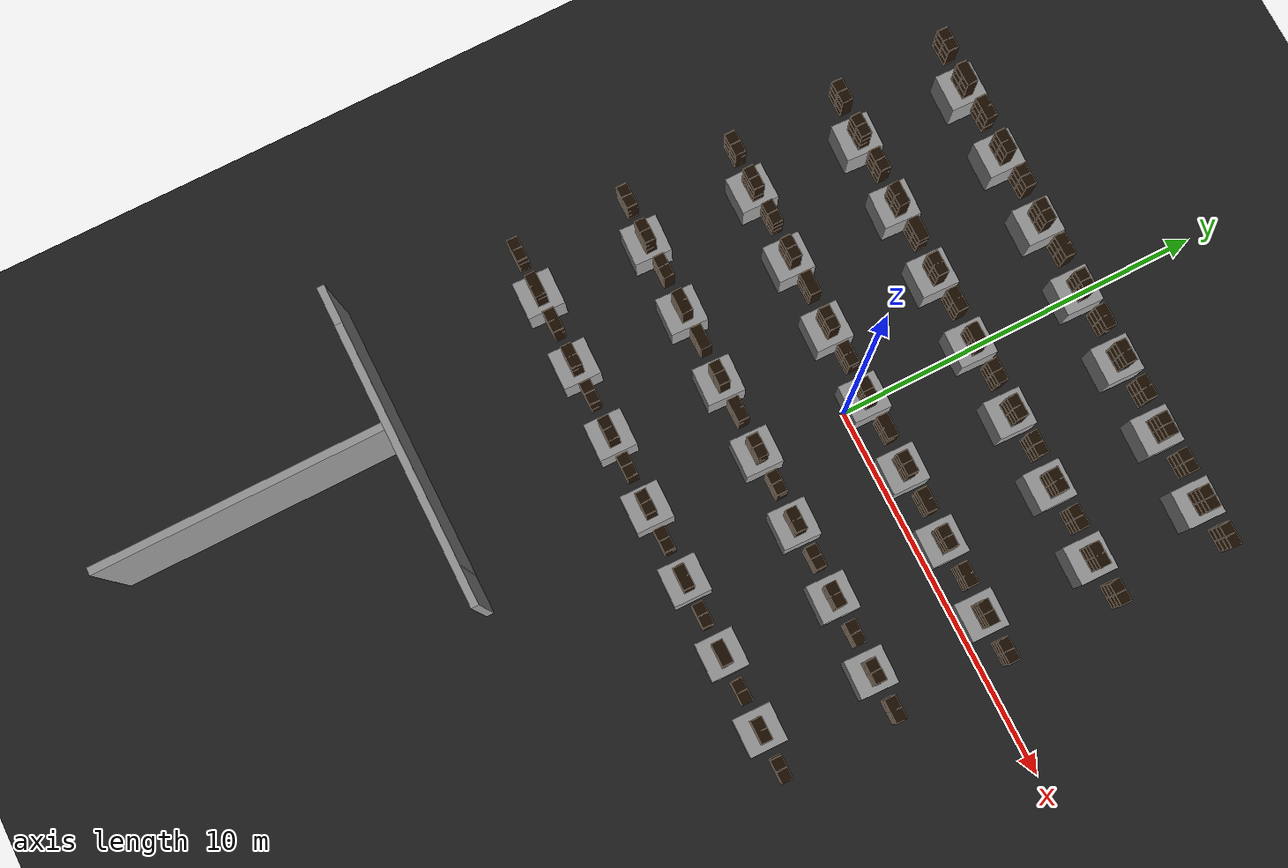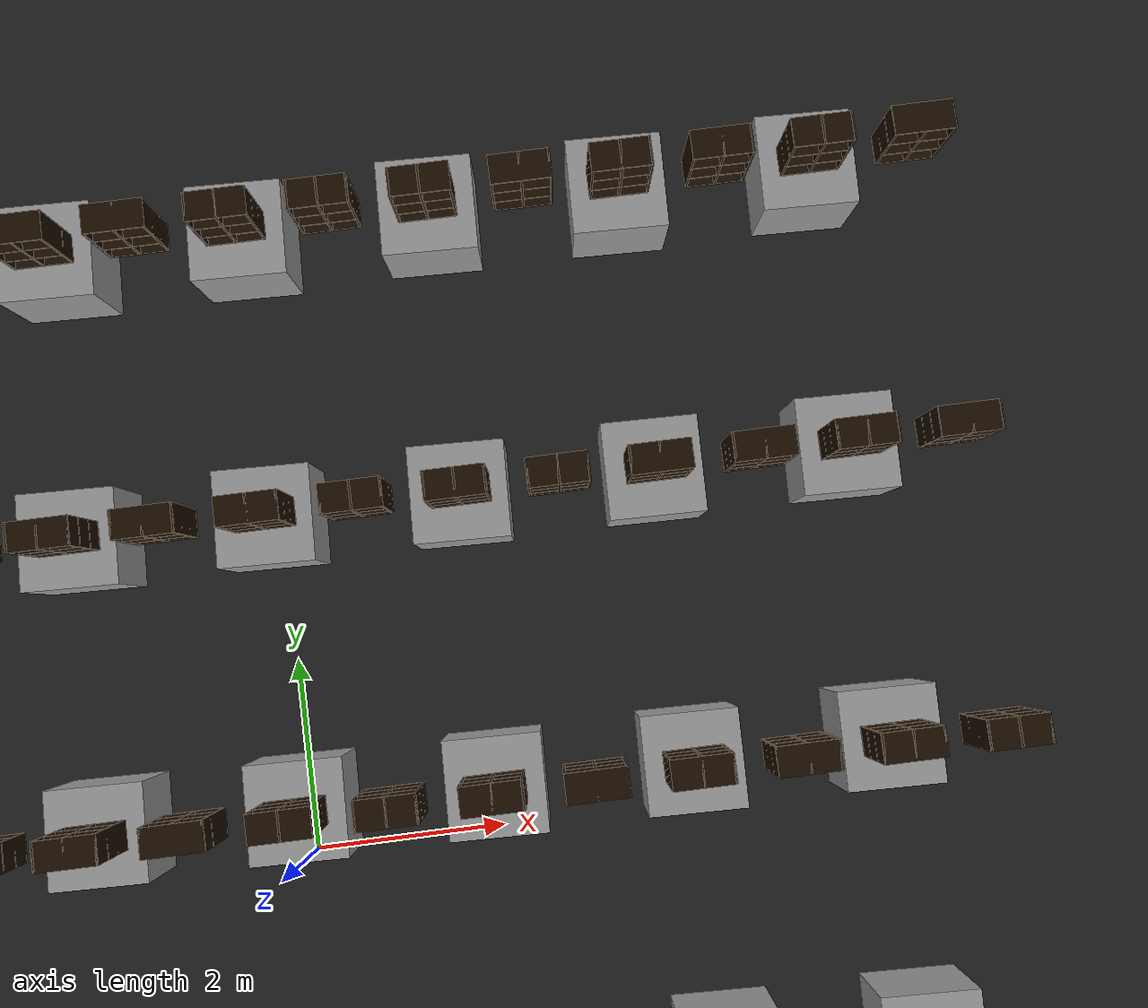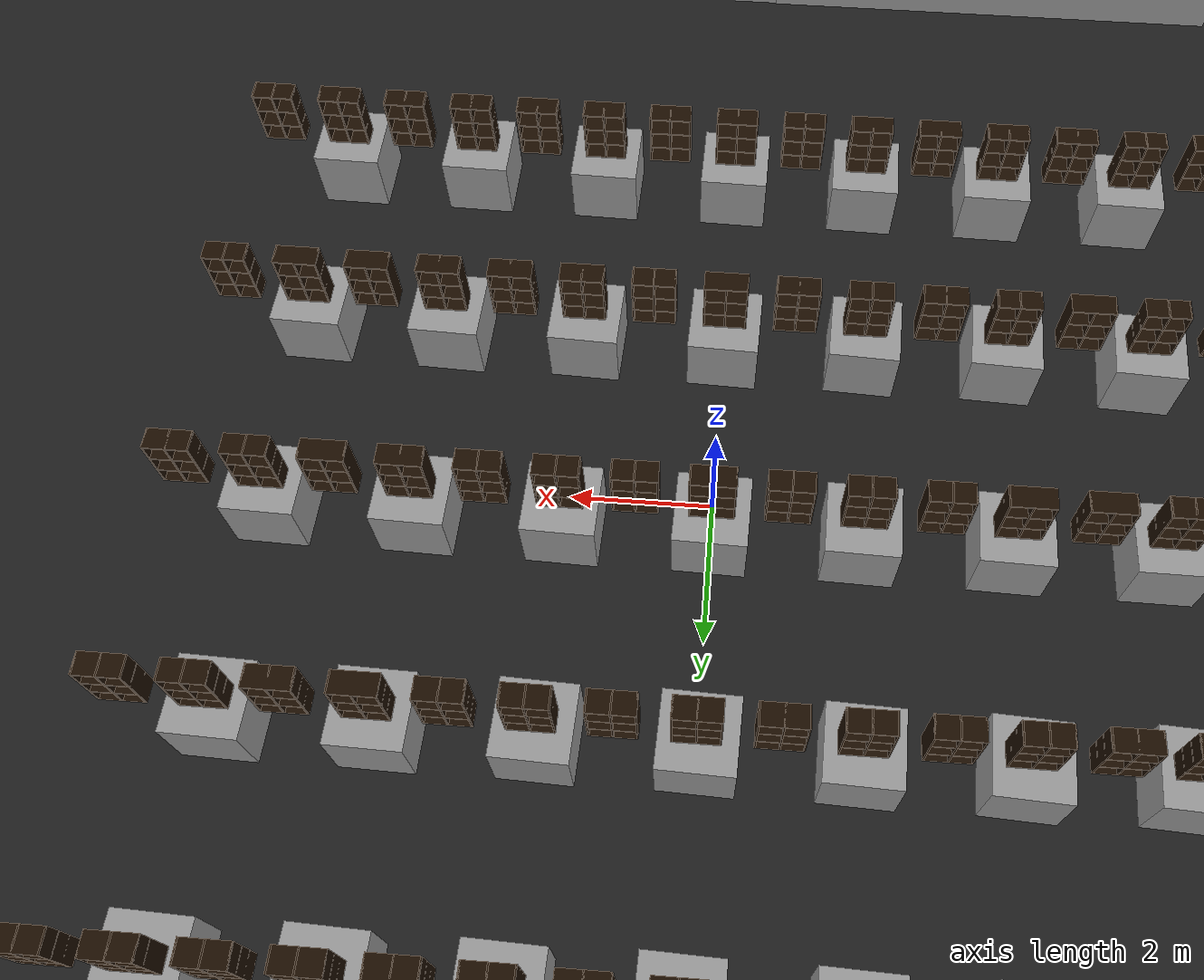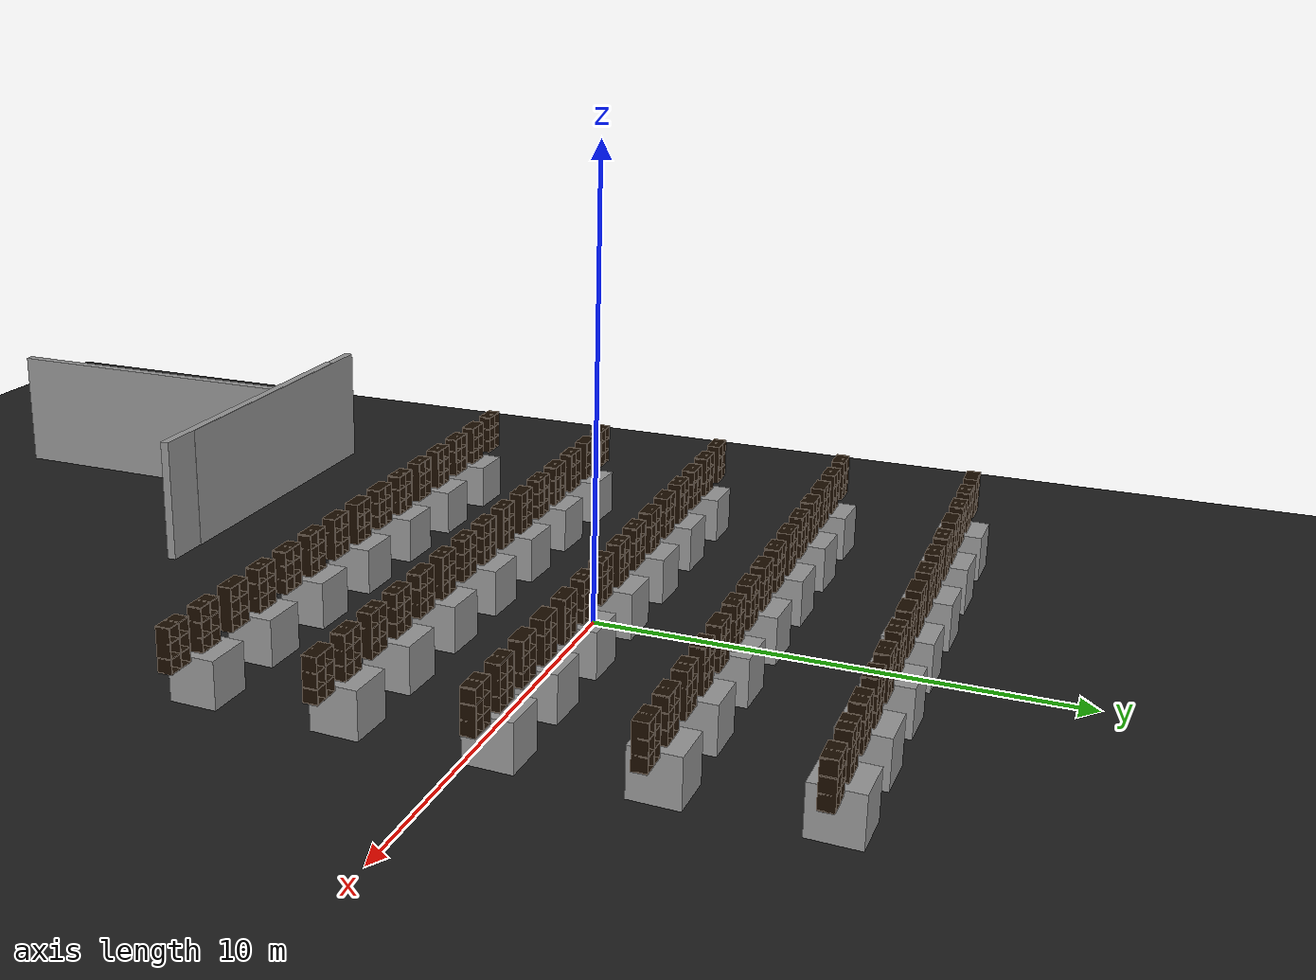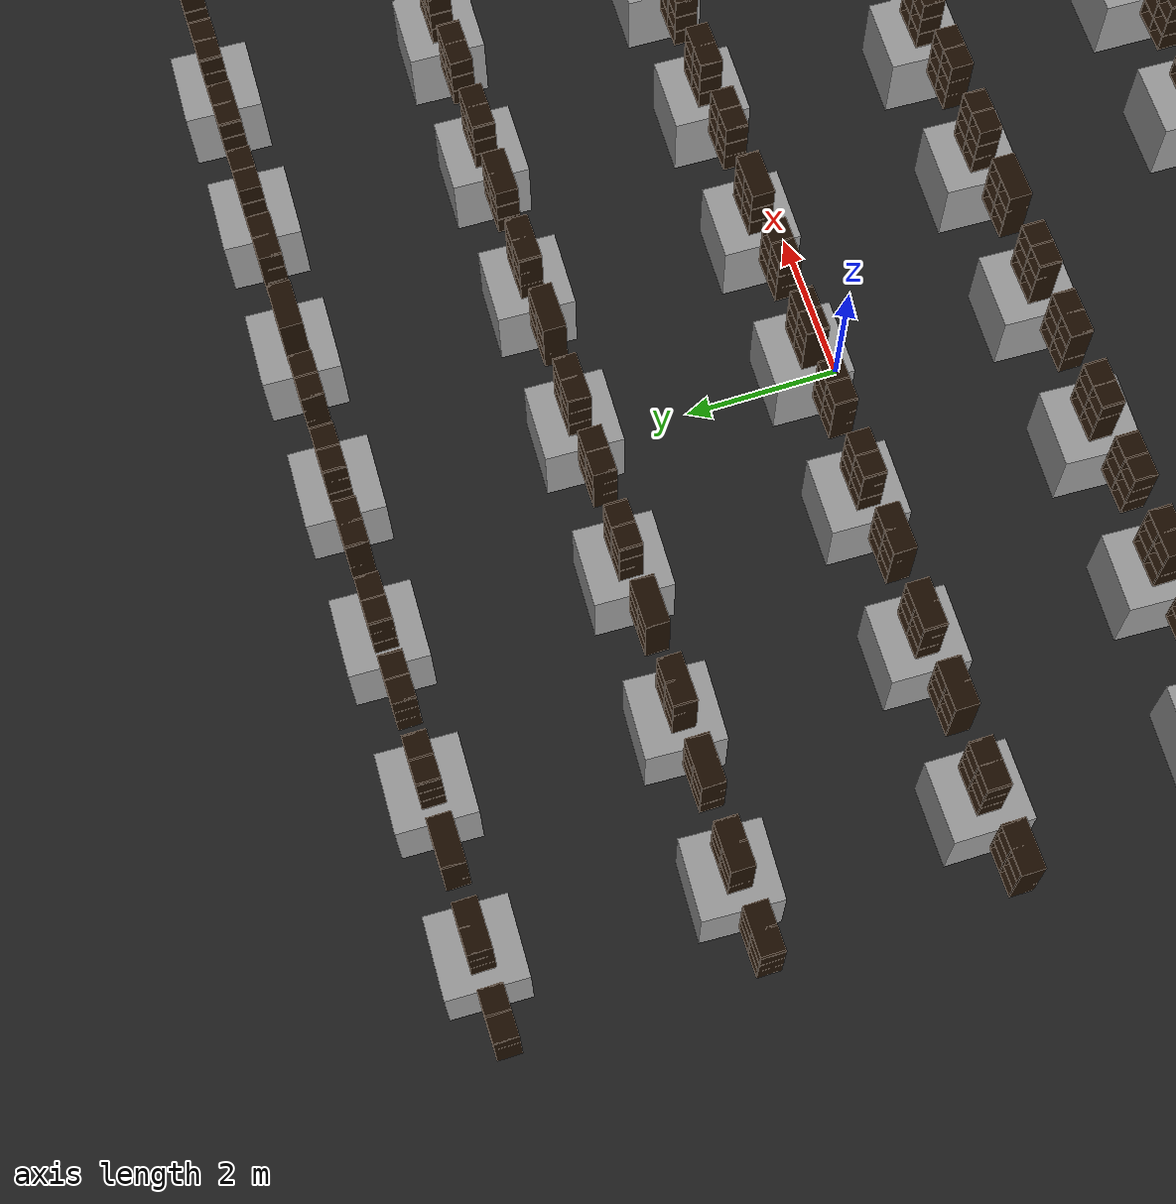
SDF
<sdf version="1.7">
 <world name="default">
  <light name="sun" type="directional">
   <cast_shadows>0</cast_shadows>
   <pose>0 0 20 0 -0 0</pose>
   <diffuse>0.8 0.8 0.8 1</diffuse>
   <specular>0.2 0.2 0.2 1</specular>
   <attenuation>
    <range>100</range>
    <constant>0.9</constant>
    <linear>0.01</linear>
    <quadratic>0.001</quadratic>
   </attenuation>
   <direction>-0.5 0.1 -0.9</direction>
   <spot><inner_angle>0</inner_angle><outer_angle>0</outer_angle><falloff>0</falloff></spot>
  </light>
  <model name="ground_plane">
   <static>1</static>
   <link name="link">
    <collision name="collision">
     <geometry><plane><normal>0 0 1</normal><size>100 100</size></plane></geometry>
     <surface><friction><ode><mu>100</mu><mu2>50</mu2></ode></friction></surface>
    </collision>
    <visual name="visual">
     <cast_shadows>0</cast_shadows>
     <geometry><plane><normal>0 0 1</normal><size>100 100</size></plane></geometry>
     <material>
      <script><uri>file://media/materials/scripts/gazebo.material</uri><name>Gazebo/BlackTransparent</name></script>
     </material>
    </visual>
   </link>
  </model>
  <gravity>0 0 -9.8</gravity>
  <magnetic_field>6e-06 2.3e-05 -4.2e-05</magnetic_field>
  <atmosphere type="adiabatic"/>
  <physics type="ode">
   <max_step_size>0.001</max_step_size>
   <real_time_factor>1</real_time_factor>
   <real_time_update_rate>1000</real_time_update_rate>
  </physics>
  <scene><ambient>0.4 0.4 0.4 1</ambient><background>0.7 0.7 0.7 1</background><shadows>0</shadows></scene>
  <spherical_coordinates>
   <surface_model>EARTH_WGS84</surface_model>
   <latitude_deg>0</latitude_deg>
   <longitude_deg>0</longitude_deg>
   <elevation>0</elevation>
   <heading_deg>0</heading_deg>
  </spherical_coordinates>
  <model name="unit_box">
   <pose>-6.01457 6.50784 0.5 0 0 -0.028631</pose>
   <link name="link">
    <inertial>
     <mass>1</mass>
     <inertia>
      <ixx>0.166667</ixx>
      <ixy>0</ixy>
      <ixz>0</ixz>
      <iyy>0.166667</iyy>
      <iyz>0</iyz>
      <izz>0.166667</izz>
     </inertia>
    </inertial>
    <collision name="collision"><geometry><box><size>1 1 1</size></box></geometry></collision>
    <visual name="visual">
     <geometry><box><size>1 1 1</size></box></geometry>
     <material>
      <script><name>Gazebo/Grey</name><uri>file://media/materials/scripts/gazebo.material</uri></script>
     </material>
    </visual>
   </link>
  </model>
  <model name="unit_box_0">
   <pose>-6.04021 3.50704 0.5 0 0 -0.048188</pose>
   <link name="link">
    <inertial>
     <mass>1</mass>
     <inertia>
      <ixx>0.166667</ixx>
      <ixy>0</ixy>
      <ixz>0</ixz>
      <iyy>0.166667</iyy>
      <iyz>0</iyz>
      <izz>0.166667</izz>
     </inertia>
    </inertial>
    <collision name="collision"><geometry><box><size>1 1 1</size></box></geometry></collision>
    <visual name="visual">
     <geometry><box><size>1 1 1</size></box></geometry>
     <material>
      <script><name>Gazebo/Grey</name><uri>file://media/materials/scripts/gazebo.material</uri></script>
     </material>
    </visual>
   </link>
  </model>
  <model name="unit_box_1">
   <pose>-6.03193 0.498311 0.5 -0 -0 -0.007554</pose>
   <link name="link">
    <inertial>
     <mass>1</mass>
     <inertia>
      <ixx>0.166667</ixx>
      <ixy>0</ixy>
      <ixz>0</ixz>
      <iyy>0.166667</iyy>
      <iyz>0</iyz>
      <izz>0.166667</izz>
     </inertia>
    </inertial>
    <collision name="collision"><geometry><box><size>1 1 1</size></box></geometry></collision>
    <visual name="visual">
     <geometry><box><size>1 1 1</size></box></geometry>
     <material>
      <script><name>Gazebo/Grey</name><uri>file://media/materials/scripts/gazebo.material</uri></script>
     </material>
    </visual>
   </link>
  </model>
  <model name="unit_box_2">
   <pose>-6.04016 -2.49948 0.5 0 -0 -0.047603</pose>
   <link name="link">
    <inertial>
     <mass>1</mass>
     <inertia>
      <ixx>0.166667</ixx>
      <ixy>0</ixy>
      <ixz>0</ixz>
      <iyy>0.166667</iyy>
      <iyz>0</iyz>
      <izz>0.166667</izz>
     </inertia>
    </inertial>
    <collision name="collision"><geometry><box><size>1 1 1</size></box></geometry></collision>
    <visual name="visual">
     <geometry><box><size>1 1 1</size></box></geometry>
     <material>
      <script><name>Gazebo/Grey</name><uri>file://media/materials/scripts/gazebo.material</uri></script>
     </material>
    </visual>
   </link>
  </model>
  <model name="unit_box_3">
   <pose>-6.01693 -5.49594 0.5 0 0 -0.024671</pose>
   <link name="link">
    <inertial>
     <mass>1</mass>
     <inertia>
      <ixx>0.166667</ixx>
      <ixy>0</ixy>
      <ixz>0</ixz>
      <iyy>0.166667</iyy>
      <iyz>0</iyz>
      <izz>0.166667</izz>
     </inertia>
    </inertial>
    <collision name="collision"><geometry><box><size>1 1 1</size></box></geometry></collision>
    <visual name="visual">
     <geometry><box><size>1 1 1</size></box></geometry>
     <material>
      <script><name>Gazebo/Grey</name><uri>file://media/materials/scripts/gazebo.material</uri></script>
     </material>
    </visual>
   </link>
  </model>
  <model name="unit_box_4">
   <pose>-4.00808 6.51203 0.5 0 0 -0.029283</pose>
   <link name="link">
    <inertial>
     <mass>1</mass>
     <inertia>
      <ixx>0.166667</ixx>
      <ixy>0</ixy>
      <ixz>0</ixz>
      <iyy>0.166667</iyy>
      <iyz>0</iyz>
      <izz>0.166667</izz>
     </inertia>
    </inertial>
    <collision name="collision"><geometry><box><size>1 1 1</size></box></geometry></collision>
    <visual name="visual">
     <geometry><box><size>1 1 1</size></box></geometry>
     <material>
      <script><name>Gazebo/Grey</name><uri>file://media/materials/scripts/gazebo.material</uri></script>
     </material>
    </visual>
   </link>
  </model>
  <model name="unit_box_5">
   <pose>-2.00694 6.5157 0.5 -0 -0 -0.029544</pose>
   <link name="link">
    <inertial>
     <mass>1</mass>
     <inertia>
      <ixx>0.166667</ixx>
      <ixy>0</ixy>
      <ixz>0</ixz>
      <iyy>0.166667</iyy>
      <iyz>0</iyz>
      <izz>0.166667</izz>
     </inertia>
    </inertial>
    <collision name="collision"><geometry><box><size>1 1 1</size></box></geometry></collision>
    <visual name="visual">
     <geometry><box><size>1 1 1</size></box></geometry>
     <material>
      <script><name>Gazebo/Grey</name><uri>file://media/materials/scripts/gazebo.material</uri></script>
     </material>
    </visual>
   </link>
  </model>
  <model name="unit_box_6">
   <pose>-0.006437 6.49747 0.5 0 -0 -0.029591</pose>
   <link name="link">
    <inertial>
     <mass>1</mass>
     <inertia>
      <ixx>0.166667</ixx>
      <ixy>0</ixy>
      <ixz>0</ixz>
      <iyy>0.166667</iyy>
      <iyz>0</iyz>
      <izz>0.166667</izz>
     </inertia>
    </inertial>
    <collision name="collision"><geometry><box><size>1 1 1</size></box></geometry></collision>
    <visual name="visual">
     <geometry><box><size>1 1 1</size></box></geometry>
     <material>
      <script><name>Gazebo/Grey</name><uri>file://media/materials/scripts/gazebo.material</uri></script>
     </material>
    </visual>
   </link>
  </model>
  <model name="unit_box_7">
   <pose>1.99571 6.51837 0.5 0 0 -0.030066</pose>
   <link name="link">
    <inertial>
     <mass>1</mass>
     <inertia>
      <ixx>0.166667</ixx>
      <ixy>0</ixy>
      <ixz>0</ixz>
      <iyy>0.166667</iyy>
      <iyz>0</iyz>
      <izz>0.166667</izz>
     </inertia>
    </inertial>
    <collision name="collision"><geometry><box><size>1 1 1</size></box></geometry></collision>
    <visual name="visual">
     <geometry><box><size>1 1 1</size></box></geometry>
     <material>
      <script><name>Gazebo/Grey</name><uri>file://media/materials/scripts/gazebo.material</uri></script>
     </material>
    </visual>
   </link>
  </model>
  <model name="unit_box_8">
   <pose>3.99685 6.50298 0.5 0 0 -0.030583</pose>
   <link name="link">
    <inertial>
     <mass>1</mass>
     <inertia>
      <ixx>0.166667</ixx>
      <ixy>0</ixy>
      <ixz>0</ixz>
      <iyy>0.166667</iyy>
      <iyz>0</iyz>
      <izz>0.166667</izz>
     </inertia>
    </inertial>
    <collision name="collision"><geometry><box><size>1 1 1</size></box></geometry></collision>
    <visual name="visual">
     <geometry><box><size>1 1 1</size></box></geometry>
     <material>
      <script><name>Gazebo/Grey</name><uri>file://media/materials/scripts/gazebo.material</uri></script>
     </material>
    </visual>
   </link>
  </model>
  <model name="unit_box_9">
   <pose>5.99874 6.50462 0.5 0 0 -0.030283</pose>
   <link name="link">
    <inertial>
     <mass>1</mass>
     <inertia>
      <ixx>0.166667</ixx>
      <ixy>0</ixy>
      <ixz>0</ixz>
      <iyy>0.166667</iyy>
      <iyz>0</iyz>
      <izz>0.166667</izz>
     </inertia>
    </inertial>
    <collision name="collision"><geometry><box><size>1 1 1</size></box></geometry></collision>
    <visual name="visual">
     <geometry><box><size>1 1 1</size></box></geometry>
     <material>
      <script><name>Gazebo/Grey</name><uri>file://media/materials/scripts/gazebo.material</uri></script>
     </material>
    </visual>
   </link>
  </model>
  <model name="unit_box_10">
   <pose>-4.03641 3.51653 0.5 0 0 -0.047204</pose>
   <link name="link">
    <inertial>
     <mass>1</mass>
     <inertia>
      <ixx>0.166667</ixx>
      <ixy>0</ixy>
      <ixz>0</ixz>
      <iyy>0.166667</iyy>
      <iyz>0</iyz>
      <izz>0.166667</izz>
     </inertia>
    </inertial>
    <collision name="collision"><geometry><box><size>1 1 1</size></box></geometry></collision>
    <visual name="visual">
     <geometry><box><size>1 1 1</size></box></geometry>
     <material>
      <script><name>Gazebo/Grey</name><uri>file://media/materials/scripts/gazebo.material</uri></script>
     </material>
    </visual>
   </link>
  </model>
  <model name="unit_box_11">
   <pose>-2.02761 3.50563 0.5 0 0 -0.031903</pose>
   <link name="link">
    <inertial>
     <mass>1</mass>
     <inertia>
      <ixx>0.166667</ixx>
      <ixy>0</ixy>
      <ixz>0</ixz>
      <iyy>0.166667</iyy>
      <iyz>0</iyz>
      <izz>0.166667</izz>
     </inertia>
    </inertial>
    <collision name="collision"><geometry><box><size>1 1 1</size></box></geometry></collision>
    <visual name="visual">
     <geometry><box><size>1 1 1</size></box></geometry>
     <material>
      <script><name>Gazebo/Grey</name><uri>file://media/materials/scripts/gazebo.material</uri></script>
     </material>
    </visual>
   </link>
  </model>
  <model name="unit_box_12">
   <pose>-0.025924 3.50002 0.5 0 0 -0.032047</pose>
   <link name="link">
    <inertial>
     <mass>1</mass>
     <inertia>
      <ixx>0.166667</ixx>
      <ixy>0</ixy>
      <ixz>0</ixz>
      <iyy>0.166667</iyy>
      <iyz>0</iyz>
      <izz>0.166667</izz>
     </inertia>
    </inertial>
    <collision name="collision"><geometry><box><size>1 1 1</size></box></geometry></collision>
    <visual name="visual">
     <geometry><box><size>1 1 1</size></box></geometry>
     <material>
      <script><name>Gazebo/Grey</name><uri>file://media/materials/scripts/gazebo.material</uri></script>
     </material>
    </visual>
   </link>
  </model>
  <model name="unit_box_13">
   <pose>1.97869 3.498 0.5 0 0 -0.03306</pose>
   <link name="link">
    <inertial>
     <mass>1</mass>
     <inertia>
      <ixx>0.166667</ixx>
      <ixy>0</ixy>
      <ixz>0</ixz>
      <iyy>0.166667</iyy>
      <iyz>0</iyz>
      <izz>0.166667</izz>
     </inertia>
    </inertial>
    <collision name="collision"><geometry><box><size>1 1 1</size></box></geometry></collision>
    <visual name="visual">
     <geometry><box><size>1 1 1</size></box></geometry>
     <material>
      <script><name>Gazebo/Grey</name><uri>file://media/materials/scripts/gazebo.material</uri></script>
     </material>
    </visual>
   </link>
  </model>
  <model name="unit_box_14">
   <pose>3.98761 3.49791 0.5 0 0 -0.021261</pose>
   <link name="link">
    <inertial>
     <mass>1</mass>
     <inertia>
      <ixx>0.166667</ixx>
      <ixy>0</ixy>
      <ixz>0</ixz>
      <iyy>0.166667</iyy>
      <iyz>0</iyz>
      <izz>0.166667</izz>
     </inertia>
    </inertial>
    <collision name="collision"><geometry><box><size>1 1 1</size></box></geometry></collision>
    <visual name="visual">
     <geometry><box><size>1 1 1</size></box></geometry>
     <material>
      <script><name>Gazebo/Grey</name><uri>file://media/materials/scripts/gazebo.material</uri></script>
     </material>
    </visual>
   </link>
  </model>
  <model name="unit_box_15">
   <pose>5.99411 3.49961 0.5 0 -0 -0.027445</pose>
   <link name="link">
    <inertial>
     <mass>1</mass>
     <inertia>
      <ixx>0.166667</ixx>
      <ixy>0</ixy>
      <ixz>0</ixz>
      <iyy>0.166667</iyy>
      <iyz>0</iyz>
      <izz>0.166667</izz>
     </inertia>
    </inertial>
    <collision name="collision"><geometry><box><size>1 1 1</size></box></geometry></collision>
    <visual name="visual">
     <geometry><box><size>1 1 1</size></box></geometry>
     <material>
      <script><name>Gazebo/Grey</name><uri>file://media/materials/scripts/gazebo.material</uri></script>
     </material>
    </visual>
   </link>
  </model>
  <model name="unit_box_16">
   <pose>-4.00948 0.496848 0.5 0 -0 -0.024916</pose>
   <link name="link">
    <inertial>
     <mass>1</mass>
     <inertia>
      <ixx>0.166667</ixx>
      <ixy>0</ixy>
      <ixz>0</ixz>
      <iyy>0.166667</iyy>
      <iyz>0</iyz>
      <izz>0.166667</izz>
     </inertia>
    </inertial>
    <collision name="collision"><geometry><box><size>1 1 1</size></box></geometry></collision>
    <visual name="visual">
     <geometry><box><size>1 1 1</size></box></geometry>
     <material>
      <script><name>Gazebo/Grey</name><uri>file://media/materials/scripts/gazebo.material</uri></script>
     </material>
    </visual>
   </link>
  </model>
  <model name="unit_box_17">
   <pose>-2.00747 0.514388 0.5 0 -0 -0.025074</pose>
   <link name="link">
    <inertial>
     <mass>1</mass>
     <inertia>
      <ixx>0.166667</ixx>
      <ixy>0</ixy>
      <ixz>0</ixz>
      <iyy>0.166667</iyy>
      <iyz>0</iyz>
      <izz>0.166667</izz>
     </inertia>
    </inertial>
    <collision name="collision"><geometry><box><size>1 1 1</size></box></geometry></collision>
    <visual name="visual">
     <geometry><box><size>1 1 1</size></box></geometry>
     <material>
      <script><name>Gazebo/Grey</name><uri>file://media/materials/scripts/gazebo.material</uri></script>
     </material>
    </visual>
   </link>
  </model>
  <model name="unit_box_18">
   <pose>-0.006792 0.511793 0.5 0 0 -0.025171</pose>
   <link name="link">
    <inertial>
     <mass>1</mass>
     <inertia>
      <ixx>0.166667</ixx>
      <ixy>0</ixy>
      <ixz>0</ixz>
      <iyy>0.166667</iyy>
      <iyz>0</iyz>
      <izz>0.166667</izz>
     </inertia>
    </inertial>
    <collision name="collision"><geometry><box><size>1 1 1</size></box></geometry></collision>
    <visual name="visual">
     <geometry><box><size>1 1 1</size></box></geometry>
     <material>
      <script><name>Gazebo/Grey</name><uri>file://media/materials/scripts/gazebo.material</uri></script>
     </material>
    </visual>
   </link>
  </model>
  <model name="unit_box_19">
   <pose>1.997 0.508723 0.5 0 -0 -0.025928</pose>
   <link name="link">
    <inertial>
     <mass>1</mass>
     <inertia>
      <ixx>0.166667</ixx>
      <ixy>0</ixy>
      <ixz>0</ixz>
      <iyy>0.166667</iyy>
      <iyz>0</iyz>
      <izz>0.166667</izz>
     </inertia>
    </inertial>
    <collision name="collision"><geometry><box><size>1 1 1</size></box></geometry></collision>
    <visual name="visual">
     <geometry><box><size>1 1 1</size></box></geometry>
     <material>
      <script><name>Gazebo/Grey</name><uri>file://media/materials/scripts/gazebo.material</uri></script>
     </material>
    </visual>
   </link>
  </model>
  <model name="unit_box_20">
   <pose>3.99851 0.502361 0.5 0 0 -0.025427</pose>
   <link name="link">
    <inertial>
     <mass>1</mass>
     <inertia>
      <ixx>0.166667</ixx>
      <ixy>0</ixy>
      <ixz>0</ixz>
      <iyy>0.166667</iyy>
      <iyz>0</iyz>
      <izz>0.166667</izz>
     </inertia>
    </inertial>
    <collision name="collision"><geometry><box><size>1 1 1</size></box></geometry></collision>
    <visual name="visual">
     <geometry><box><size>1 1 1</size></box></geometry>
     <material>
      <script><name>Gazebo/Grey</name><uri>file://media/materials/scripts/gazebo.material</uri></script>
     </material>
    </visual>
   </link>
  </model>
  <model name="unit_box_21">
   <pose>5.99967 0.500062 0.5 0 0 -0.025536</pose>
   <link name="link">
    <inertial>
     <mass>1</mass>
     <inertia>
      <ixx>0.166667</ixx>
      <ixy>0</ixy>
      <ixz>0</ixz>
      <iyy>0.166667</iyy>
      <iyz>0</iyz>
      <izz>0.166667</izz>
     </inertia>
    </inertial>
    <collision name="collision"><geometry><box><size>1 1 1</size></box></geometry></collision>
    <visual name="visual">
     <geometry><box><size>1 1 1</size></box></geometry>
     <material>
      <script><name>Gazebo/Grey</name><uri>file://media/materials/scripts/gazebo.material</uri></script>
     </material>
    </visual>
   </link>
  </model>
  <model name="unit_box_22">
   <pose>-4.02326 -2.50724 0.5 0 -0 -0.042544</pose>
   <link name="link">
    <inertial>
     <mass>1</mass>
     <inertia>
      <ixx>0.166667</ixx>
      <ixy>0</ixy>
      <ixz>0</ixz>
      <iyy>0.166667</iyy>
      <iyz>0</iyz>
      <izz>0.166667</izz>
     </inertia>
    </inertial>
    <collision name="collision"><geometry><box><size>1 1 1</size></box></geometry></collision>
    <visual name="visual">
     <geometry><box><size>1 1 1</size></box></geometry>
     <material>
      <script><name>Gazebo/Grey</name><uri>file://media/materials/scripts/gazebo.material</uri></script>
     </material>
    </visual>
   </link>
  </model>
  <model name="unit_box_23">
   <pose>-2.0206 -2.50243 0.5 0 0 -0.042386</pose>
   <link name="link">
    <inertial>
     <mass>1</mass>
     <inertia>
      <ixx>0.166667</ixx>
      <ixy>0</ixy>
      <ixz>0</ixz>
      <iyy>0.166667</iyy>
      <iyz>0</iyz>
      <izz>0.166667</izz>
     </inertia>
    </inertial>
    <collision name="collision"><geometry><box><size>1 1 1</size></box></geometry></collision>
    <visual name="visual">
     <geometry><box><size>1 1 1</size></box></geometry>
     <material>
      <script><name>Gazebo/Grey</name><uri>file://media/materials/scripts/gazebo.material</uri></script>
     </material>
    </visual>
   </link>
  </model>
  <model name="unit_box_24">
   <pose>-0.012698 -2.48702 0.5 0 0 -0.031078</pose>
   <link name="link">
    <inertial>
     <mass>1</mass>
     <inertia>
      <ixx>0.166667</ixx>
      <ixy>0</ixy>
      <ixz>0</ixz>
      <iyy>0.166667</iyy>
      <iyz>0</iyz>
      <izz>0.166667</izz>
     </inertia>
    </inertial>
    <collision name="collision"><geometry><box><size>1 1 1</size></box></geometry></collision>
    <visual name="visual">
     <geometry><box><size>1 1 1</size></box></geometry>
     <material>
      <script><name>Gazebo/Grey</name><uri>file://media/materials/scripts/gazebo.material</uri></script>
     </material>
    </visual>
   </link>
  </model>
  <model name="unit_box_25">
   <pose>1.99148 -2.49024 0.5 0 0 -0.034578</pose>
   <link name="link">
    <inertial>
     <mass>1</mass>
     <inertia>
      <ixx>0.166667</ixx>
      <ixy>0</ixy>
      <ixz>0</ixz>
      <iyy>0.166667</iyy>
      <iyz>0</iyz>
      <izz>0.166667</izz>
     </inertia>
    </inertial>
    <collision name="collision"><geometry><box><size>1 1 1</size></box></geometry></collision>
    <visual name="visual">
     <geometry><box><size>1 1 1</size></box></geometry>
     <material>
      <script><name>Gazebo/Grey</name><uri>file://media/materials/scripts/gazebo.material</uri></script>
     </material>
    </visual>
   </link>
  </model>
  <model name="unit_box_26">
   <pose>3.99339 -2.48181 0.5 0 0 -0.034708</pose>
   <link name="link">
    <inertial>
     <mass>1</mass>
     <inertia>
      <ixx>0.166667</ixx>
      <ixy>0</ixy>
      <ixz>0</ixz>
      <iyy>0.166667</iyy>
      <iyz>0</iyz>
      <izz>0.166667</izz>
     </inertia>
    </inertial>
    <collision name="collision"><geometry><box><size>1 1 1</size></box></geometry></collision>
    <visual name="visual">
     <geometry><box><size>1 1 1</size></box></geometry>
     <material>
      <script><name>Gazebo/Grey</name><uri>file://media/materials/scripts/gazebo.material</uri></script>
     </material>
    </visual>
   </link>
  </model>
  <model name="unit_box_27">
   <pose>5.99482 -2.50701 0.5 0 0 -0.035375</pose>
   <link name="link">
    <inertial>
     <mass>1</mass>
     <inertia>
      <ixx>0.166667</ixx>
      <ixy>0</ixy>
      <ixz>0</ixz>
      <iyy>0.166667</iyy>
      <iyz>0</iyz>
      <izz>0.166667</izz>
     </inertia>
    </inertial>
    <collision name="collision"><geometry><box><size>1 1 1</size></box></geometry></collision>
    <visual name="visual">
     <geometry><box><size>1 1 1</size></box></geometry>
     <material>
      <script><name>Gazebo/Grey</name><uri>file://media/materials/scripts/gazebo.material</uri></script>
     </material>
    </visual>
   </link>
  </model>
  <model name="unit_box_28">
   <pose>-4.01046 -5.49396 0.5 0 -0 -0.019734</pose>
   <link name="link">
    <inertial>
     <mass>1</mass>
     <inertia>
      <ixx>0.166667</ixx>
      <ixy>0</ixy>
      <ixz>0</ixz>
      <iyy>0.166667</iyy>
      <iyz>0</iyz>
      <izz>0.166667</izz>
     </inertia>
    </inertial>
    <collision name="collision"><geometry><box><size>1 1 1</size></box></geometry></collision>
    <visual name="visual">
     <geometry><box><size>1 1 1</size></box></geometry>
     <material>
      <script><name>Gazebo/Grey</name><uri>file://media/materials/scripts/gazebo.material</uri></script>
     </material>
    </visual>
   </link>
  </model>
  <model name="unit_box_29">
   <pose>-2.00685 -5.49705 0.5 0 0 -0.022508</pose>
   <link name="link">
    <inertial>
     <mass>1</mass>
     <inertia>
      <ixx>0.166667</ixx>
      <ixy>0</ixy>
      <ixz>0</ixz>
      <iyy>0.166667</iyy>
      <iyz>0</iyz>
      <izz>0.166667</izz>
     </inertia>
    </inertial>
    <collision name="collision"><geometry><box><size>1 1 1</size></box></geometry></collision>
    <visual name="visual">
     <geometry><box><size>1 1 1</size></box></geometry>
     <material>
      <script><name>Gazebo/Grey</name><uri>file://media/materials/scripts/gazebo.material</uri></script>
     </material>
    </visual>
   </link>
  </model>
  <model name="unit_box_30">
   <pose>-0.005245 -5.49191 0.5 0 -0 -0.020658</pose>
   <link name="link">
    <inertial>
     <mass>1</mass>
     <inertia>
      <ixx>0.166667</ixx>
      <ixy>0</ixy>
      <ixz>0</ixz>
      <iyy>0.166667</iyy>
      <iyz>0</iyz>
      <izz>0.166667</izz>
     </inertia>
    </inertial>
    <collision name="collision"><geometry><box><size>1 1 1</size></box></geometry></collision>
    <visual name="visual">
     <geometry><box><size>1 1 1</size></box></geometry>
     <material>
      <script><name>Gazebo/Grey</name><uri>file://media/materials/scripts/gazebo.material</uri></script>
     </material>
    </visual>
   </link>
  </model>
  <model name="unit_box_31">
   <pose>1.99556 -5.48651 0.5 0 0 -0.021112</pose>
   <link name="link">
    <inertial>
     <mass>1</mass>
     <inertia>
      <ixx>0.166667</ixx>
      <ixy>0</ixy>
      <ixz>0</ixz>
      <iyy>0.166667</iyy>
      <iyz>0</iyz>
      <izz>0.166667</izz>
     </inertia>
    </inertial>
    <collision name="collision"><geometry><box><size>1 1 1</size></box></geometry></collision>
    <visual name="visual">
     <geometry><box><size>1 1 1</size></box></geometry>
     <material>
      <script><name>Gazebo/Grey</name><uri>file://media/materials/scripts/gazebo.material</uri></script>
     </material>
    </visual>
   </link>
  </model>
  <model name="unit_box_32">
   <pose>3.99636 -5.49751 0.5 0 0 -0.020979</pose>
   <link name="link">
    <inertial>
     <mass>1</mass>
     <inertia>
      <ixx>0.166667</ixx>
      <ixy>0</ixy>
      <ixz>0</ixz>
      <iyy>0.166667</iyy>
      <iyz>0</iyz>
      <izz>0.166667</izz>
     </inertia>
    </inertial>
    <collision name="collision"><geometry><box><size>1 1 1</size></box></geometry></collision>
    <visual name="visual">
     <geometry><box><size>1 1 1</size></box></geometry>
     <material>
      <script><name>Gazebo/Grey</name><uri>file://media/materials/scripts/gazebo.material</uri></script>
     </material>
    </visual>
   </link>
  </model>
  <model name="unit_box_33">
   <pose>5.99752 -5.5015 0.5 0 0 -0.021423</pose>
   <link name="link">
    <inertial>
     <mass>1</mass>
     <inertia>
      <ixx>0.166667</ixx>
      <ixy>0</ixy>
      <ixz>0</ixz>
      <iyy>0.166667</iyy>
      <iyz>0</iyz>
      <izz>0.166667</izz>
     </inertia>
    </inertial>
    <collision name="collision"><geometry><box><size>1 1 1</size></box></geometry></collision>
    <visual name="visual">
     <geometry><box><size>1 1 1</size></box></geometry>
     <material>
      <script><name>Gazebo/Grey</name><uri>file://media/materials/scripts/gazebo.material</uri></script>
     </material>
    </visual>
   </link>
  </model>
  <model name="6_Cube_StorageE">
   <link name="Wall_0">
    <pose>0 0 0.01 0 -0 0</pose>
    <inertial>
     <mass>1.6201</mass>
     <inertia><ixx>0.0119</ixx><iyy>0.0631</iyy><izz>0.0513</izz><ixy>0</ixy><ixz>0</ixz><iyz>0</iyz></inertia>
    </inertial>
    <collision name="Wall_0_Collision"><geometry><box><size>0.616 0.296 0.02</size></box></geometry></collision>
    <visual name="Wall_0_Visual">
     <geometry><box><size>0.616 0.296 0.02</size></box></geometry>
     <material>
      <script><uri>file://media/materials/scripts/gazebo.material</uri><name>Gazebo/Grey</name></script>
      <ambient>0.105882 0.0509804 0 1</ambient>
     </material>
    </visual>
   </link>
   <joint name="0_2" type="fixed">
    <pose>-0.308 0 0 0 -0 0</pose>
    <parent>Wall_2</parent>
    <child>Wall_0</child>
    <axis><xyz>1 0 0</xyz><limit><lower>-1e+16</lower><upper>1e+16</upper></limit></axis>
   </joint>
   <joint name="0_12" type="fixed">
    <parent>Wall_12</parent>
    <child>Wall_0</child>
    <axis><xyz>0 0 1</xyz><limit><lower>-1e+16</lower><upper>1e+16</upper></limit></axis>
   </joint>
   <joint name="0_4" type="fixed">
    <pose>0.308 0 0 0 -0 0</pose>
    <parent>Wall_4</parent>
    <child>Wall_0</child>
    <axis><xyz>1 0 0</xyz><limit><lower>-1e+16</lower><upper>1e+16</upper></limit></axis>
   </joint>
   <link name="Wall_10">
    <pose>0 0 0.61 0 -0 0</pose>
    <inertial>
     <mass>1.6201</mass>
     <inertia><ixx>0.0119</ixx><iyy>0.0631</iyy><izz>0.0513</izz><ixy>0</ixy><ixz>0</ixz><iyz>0</iyz></inertia>
    </inertial>
    <collision name="Wall_10_Collision"><geometry><box><size>0.616 0.296 0.02</size></box></geometry></collision>
    <visual name="Wall_10_Visual">
     <geometry><box><size>0.616 0.296 0.02</size></box></geometry>
     <material>
      <script><uri>file://media/materials/scripts/gazebo.material</uri><name>Gazebo/Grey</name></script>
      <ambient>0.105882 0.0509804 0 1</ambient>
     </material>
    </visual>
   </link>
   <joint name="10_2" type="fixed">
    <pose>-0.308 0 0 0 -0 0</pose>
    <parent>Wall_2</parent>
    <child>Wall_10</child>
    <axis><xyz>1 0 0</xyz><limit><lower>-1e+16</lower><upper>1e+16</upper></limit></axis>
   </joint>
   <joint name="10_12" type="fixed">
    <parent>Wall_12</parent>
    <child>Wall_10</child>
    <axis><xyz>0 0 1</xyz><limit><lower>-1e+16</lower><upper>1e+16</upper></limit></axis>
   </joint>
   <joint name="10_4" type="fixed">
    <pose>0.308 0 0 0 -0 0</pose>
    <parent>Wall_4</parent>
    <child>Wall_10</child>
    <axis><xyz>1 0 0</xyz><limit><lower>-1e+16</lower><upper>1e+16</upper></limit></axis>
   </joint>
   <link name="Wall_12">
    <pose>0 0 0.4575 0 -0 0</pose>
    <inertial>
     <mass>2.4065</mass>
     <inertia><ixx>0.0177</ixx><iyy>0.1855</iyy><izz>0.168</izz><ixy>0</ixy><ixz>0</ixz><iyz>0</iyz></inertia>
    </inertial>
    <collision name="Wall_12_Collision"><geometry><box><size>0.02 0.296 0.915</size></box></geometry></collision>
    <visual name="Wall_12_Visual">
     <geometry><box><size>0.02 0.296 0.915</size></box></geometry>
     <material>
      <script><uri>file://media/materials/scripts/gazebo.material</uri><name>Gazebo/Grey</name></script>
      <ambient>0.105882 0.0509804 0 1</ambient>
     </material>
    </visual>
   </link>
   <link name="Wall_2">
    <pose>-0.298 0 0.4575 0 -0 0</pose>
    <inertial>
     <mass>2.4065</mass>
     <inertia><ixx>0.0177</ixx><iyy>0.1855</iyy><izz>0.168</izz><ixy>0</ixy><ixz>0</ixz><iyz>0</iyz></inertia>
    </inertial>
    <collision name="Wall_2_Collision"><geometry><box><size>0.02 0.296 0.915</size></box></geometry></collision>
    <visual name="Wall_2_Visual">
     <geometry><box><size>0.02 0.296 0.915</size></box></geometry>
     <material>
      <script><uri>file://media/materials/scripts/gazebo.material</uri><name>Gazebo/Grey</name></script>
      <ambient>0.105882 0.0509804 0 1</ambient>
     </material>
    </visual>
   </link>
   <link name="Wall_4">
    <pose>0.298 0 0.4575 0 -0 0</pose>
    <inertial>
     <mass>2.4065</mass>
     <inertia><ixx>0.0177</ixx><iyy>0.1855</iyy><izz>0.168</izz><ixy>0</ixy><ixz>0</ixz><iyz>0</iyz></inertia>
    </inertial>
    <collision name="Wall_4_Collision"><geometry><box><size>0.02 0.296 0.915</size></box></geometry></collision>
    <visual name="Wall_4_Visual">
     <geometry><box><size>0.02 0.296 0.915</size></box></geometry>
     <material>
      <script><uri>file://media/materials/scripts/gazebo.material</uri><name>Gazebo/Grey</name></script>
      <ambient>0.105882 0.0509804 0 1</ambient>
     </material>
    </visual>
   </link>
   <link name="Wall_6">
    <pose>0 0 0.905 0 -0 0</pose>
    <inertial>
     <mass>1.6201</mass>
     <inertia><ixx>0.0119</ixx><iyy>0.0631</iyy><izz>0.0513</izz><ixy>0</ixy><ixz>0</ixz><iyz>0</iyz></inertia>
    </inertial>
    <collision name="Wall_6_Collision"><geometry><box><size>0.616 0.296 0.02</size></box></geometry></collision>
    <visual name="Wall_6_Visual">
     <geometry><box><size>0.616 0.296 0.02</size></box></geometry>
     <material>
      <script><uri>file://media/materials/scripts/gazebo.material</uri><name>Gazebo/Grey</name></script>
      <ambient>0.105882 0.0509804 0 1</ambient>
     </material>
    </visual>
   </link>
   <joint name="6_2" type="fixed">
    <pose>-0.308 0 0 0 -0 0</pose>
    <parent>Wall_2</parent>
    <child>Wall_6</child>
    <axis><xyz>2 0 0</xyz><limit><lower>-1e+16</lower><upper>1e+16</upper></limit></axis>
   </joint>
   <joint name="6_12" type="fixed">
    <parent>Wall_12</parent>
    <child>Wall_6</child>
    <axis><xyz>0 0 1</xyz><limit><lower>-1e+16</lower><upper>1e+16</upper></limit></axis>
   </joint>
   <joint name="6_4" type="fixed">
    <pose>0.308 0 0 0 -0 0</pose>
    <parent>Wall_4</parent>
    <child>Wall_6</child>
    <axis><xyz>1 0 0</xyz><limit><lower>-1e+16</lower><upper>1e+16</upper></limit></axis>
   </joint>
   <link name="Wall_8">
    <pose>0 0 0.305 0 -0 0</pose>
    <inertial>
     <mass>1.6201</mass>
     <inertia><ixx>0.0119</ixx><iyy>0.0631</iyy><izz>0.0513</izz><ixy>0</ixy><ixz>0</ixz><iyz>0</iyz></inertia>
    </inertial>
    <collision name="Wall_8_Collision"><geometry><box><size>0.616 0.296 0.02</size></box></geometry></collision>
    <visual name="Wall_8_Visual">
     <geometry><box><size>0.616 0.296 0.02</size></box></geometry>
     <material>
      <script><uri>file://media/materials/scripts/gazebo.material</uri><name>Gazebo/Grey</name></script>
      <ambient>0.105882 0.0509804 0 1</ambient>
     </material>
    </visual>
   </link>
   <joint name="8_2" type="fixed">
    <pose>-0.308 0 0 0 -0 0</pose>
    <parent>Wall_2</parent>
    <child>Wall_8</child>
    <axis><xyz>1 0 0</xyz><limit><lower>-1e+16</lower><upper>1e+16</upper></limit></axis>
   </joint>
   <joint name="8_12" type="fixed">
    <parent>Wall_12</parent>
    <child>Wall_8</child>
    <axis><xyz>0 0 1</xyz><limit><lower>-1e+16</lower><upper>1e+16</upper></limit></axis>
   </joint>
   <joint name="8_4" type="fixed">
    <pose>0.308 0 0 0 -0 0</pose>
    <parent>Wall_4</parent>
    <child>Wall_8</child>
    <axis><xyz>1 0 0</xyz><limit><lower>-1e+16</lower><upper>1e+16</upper></limit></axis>
   </joint>
   <static>1</static>
   <pose>-7 6.5 1.01 0 -0 0</pose>
  </model>
  <model name="6_Cube_StorageE_clone">
   <link name="Wall_0">
    <pose>0 0 0.01 0 -0 0</pose>
    <inertial>
     <mass>1.6201</mass>
     <inertia><ixx>0.0119</ixx><iyy>0.0631</iyy><izz>0.0513</izz><ixy>0</ixy><ixz>0</ixz><iyz>0</iyz></inertia>
    </inertial>
    <collision name="Wall_0_Collision"><geometry><box><size>0.616 0.296 0.02</size></box></geometry></collision>
    <visual name="Wall_0_Visual">
     <geometry><box><size>0.616 0.296 0.02</size></box></geometry>
     <material>
      <script><uri>file://media/materials/scripts/gazebo.material</uri><name>Gazebo/Grey</name></script>
      <ambient>0.105882 0.0509804 0 1</ambient>
     </material>
    </visual>
   </link>
   <joint name="0_2" type="fixed">
    <pose>-0.308 0 0 0 -0 0</pose>
    <parent>Wall_2</parent>
    <child>Wall_0</child>
    <axis><xyz>1 0 0</xyz><limit><lower>-1e+16</lower><upper>1e+16</upper></limit></axis>
   </joint>
   <joint name="0_12" type="fixed">
    <parent>Wall_12</parent>
    <child>Wall_0</child>
    <axis><xyz>0 0 1</xyz><limit><lower>-1e+16</lower><upper>1e+16</upper></limit></axis>
   </joint>
   <joint name="0_4" type="fixed">
    <pose>0.308 0 0 0 -0 0</pose>
    <parent>Wall_4</parent>
    <child>Wall_0</child>
    <axis><xyz>1 0 0</xyz><limit><lower>-1e+16</lower><upper>1e+16</upper></limit></axis>
   </joint>
   <link name="Wall_10">
    <pose>0 0 0.61 0 -0 0</pose>
    <inertial>
     <mass>1.6201</mass>
     <inertia><ixx>0.0119</ixx><iyy>0.0631</iyy><izz>0.0513</izz><ixy>0</ixy><ixz>0</ixz><iyz>0</iyz></inertia>
    </inertial>
    <collision name="Wall_10_Collision"><geometry><box><size>0.616 0.296 0.02</size></box></geometry></collision>
    <visual name="Wall_10_Visual">
     <geometry><box><size>0.616 0.296 0.02</size></box></geometry>
     <material>
      <script><uri>file://media/materials/scripts/gazebo.material</uri><name>Gazebo/Grey</name></script>
      <ambient>0.105882 0.0509804 0 1</ambient>
     </material>
    </visual>
   </link>
   <joint name="10_2" type="fixed">
    <pose>-0.308 0 0 0 -0 0</pose>
    <parent>Wall_2</parent>
    <child>Wall_10</child>
    <axis><xyz>1 0 0</xyz><limit><lower>-1e+16</lower><upper>1e+16</upper></limit></axis>
   </joint>
   <joint name="10_12" type="fixed">
    <parent>Wall_12</parent>
    <child>Wall_10</child>
    <axis><xyz>0 0 1</xyz><limit><lower>-1e+16</lower><upper>1e+16</upper></limit></axis>
   </joint>
   <joint name="10_4" type="fixed">
    <pose>0.308 0 0 0 -0 0</pose>
    <parent>Wall_4</parent>
    <child>Wall_10</child>
    <axis><xyz>1 0 0</xyz><limit><lower>-1e+16</lower><upper>1e+16</upper></limit></axis>
   </joint>
   <link name="Wall_12">
    <pose>0 0 0.4575 0 -0 0</pose>
    <inertial>
     <mass>2.4065</mass>
     <inertia><ixx>0.0177</ixx><iyy>0.1855</iyy><izz>0.168</izz><ixy>0</ixy><ixz>0</ixz><iyz>0</iyz></inertia>
    </inertial>
    <collision name="Wall_12_Collision"><geometry><box><size>0.02 0.296 0.915</size></box></geometry></collision>
    <visual name="Wall_12_Visual">
     <geometry><box><size>0.02 0.296 0.915</size></box></geometry>
     <material>
      <script><uri>file://media/materials/scripts/gazebo.material</uri><name>Gazebo/Grey</name></script>
      <ambient>0.105882 0.0509804 0 1</ambient>
     </material>
    </visual>
   </link>
   <link name="Wall_2">
    <pose>-0.298 0 0.4575 0 -0 0</pose>
    <inertial>
     <mass>2.4065</mass>
     <inertia><ixx>0.0177</ixx><iyy>0.1855</iyy><izz>0.168</izz><ixy>0</ixy><ixz>0</ixz><iyz>0</iyz></inertia>
    </inertial>
    <collision name="Wall_2_Collision"><geometry><box><size>0.02 0.296 0.915</size></box></geometry></collision>
    <visual name="Wall_2_Visual">
     <geometry><box><size>0.02 0.296 0.915</size></box></geometry>
     <material>
      <script><uri>file://media/materials/scripts/gazebo.material</uri><name>Gazebo/Grey</name></script>
      <ambient>0.105882 0.0509804 0 1</ambient>
     </material>
    </visual>
   </link>
   <link name="Wall_4">
    <pose>0.298 0 0.4575 0 -0 0</pose>
    <inertial>
     <mass>2.4065</mass>
     <inertia><ixx>0.0177</ixx><iyy>0.1855</iyy><izz>0.168</izz><ixy>0</ixy><ixz>0</ixz><iyz>0</iyz></inertia>
    </inertial>
    <collision name="Wall_4_Collision"><geometry><box><size>0.02 0.296 0.915</size></box></geometry></collision>
    <visual name="Wall_4_Visual">
     <geometry><box><size>0.02 0.296 0.915</size></box></geometry>
     <material>
      <script><uri>file://media/materials/scripts/gazebo.material</uri><name>Gazebo/Grey</name></script>
      <ambient>0.105882 0.0509804 0 1</ambient>
     </material>
    </visual>
   </link>
   <link name="Wall_6">
    <pose>0 0 0.905 0 -0 0</pose>
    <inertial>
     <mass>1.6201</mass>
     <inertia><ixx>0.0119</ixx><iyy>0.0631</iyy><izz>0.0513</izz><ixy>0</ixy><ixz>0</ixz><iyz>0</iyz></inertia>
    </inertial>
    <collision name="Wall_6_Collision"><geometry><box><size>0.616 0.296 0.02</size></box></geometry></collision>
    <visual name="Wall_6_Visual">
     <geometry><box><size>0.616 0.296 0.02</size></box></geometry>
     <material>
      <script><uri>file://media/materials/scripts/gazebo.material</uri><name>Gazebo/Grey</name></script>
      <ambient>0.105882 0.0509804 0 1</ambient>
     </material>
    </visual>
   </link>
   <joint name="6_2" type="fixed">
    <pose>-0.308 0 0 0 -0 0</pose>
    <parent>Wall_2</parent>
    <child>Wall_6</child>
    <axis><xyz>2 0 0</xyz><limit><lower>-1e+16</lower><upper>1e+16</upper></limit></axis>
   </joint>
   <joint name="6_12" type="fixed">
    <parent>Wall_12</parent>
    <child>Wall_6</child>
    <axis><xyz>0 0 1</xyz><limit><lower>-1e+16</lower><upper>1e+16</upper></limit></axis>
   </joint>
   <joint name="6_4" type="fixed">
    <pose>0.308 0 0 0 -0 0</pose>
    <parent>Wall_4</parent>
    <child>Wall_6</child>
    <axis><xyz>1 0 0</xyz><limit><lower>-1e+16</lower><upper>1e+16</upper></limit></axis>
   </joint>
   <link name="Wall_8">
    <pose>0 0 0.305 0 -0 0</pose>
    <inertial>
     <mass>1.6201</mass>
     <inertia><ixx>0.0119</ixx><iyy>0.0631</iyy><izz>0.0513</izz><ixy>0</ixy><ixz>0</ixz><iyz>0</iyz></inertia>
    </inertial>
    <collision name="Wall_8_Collision"><geometry><box><size>0.616 0.296 0.02</size></box></geometry></collision>
    <visual name="Wall_8_Visual">
     <geometry><box><size>0.616 0.296 0.02</size></box></geometry>
     <material>
      <script><uri>file://media/materials/scripts/gazebo.material</uri><name>Gazebo/Grey</name></script>
      <ambient>0.105882 0.0509804 0 1</ambient>
     </material>
    </visual>
   </link>
   <joint name="8_2" type="fixed">
    <pose>-0.308 0 0 0 -0 0</pose>
    <parent>Wall_2</parent>
    <child>Wall_8</child>
    <axis><xyz>1 0 0</xyz><limit><lower>-1e+16</lower><upper>1e+16</upper></limit></axis>
   </joint>
   <joint name="8_12" type="fixed">
    <parent>Wall_12</parent>
    <child>Wall_8</child>
    <axis><xyz>0 0 1</xyz><limit><lower>-1e+16</lower><upper>1e+16</upper></limit></axis>
   </joint>
   <joint name="8_4" type="fixed">
    <pose>0.308 0 0 0 -0 0</pose>
    <parent>Wall_4</parent>
    <child>Wall_8</child>
    <axis><xyz>1 0 0</xyz><limit><lower>-1e+16</lower><upper>1e+16</upper></limit></axis>
   </joint>
   <static>1</static>
   <pose>-6 6.5 1.01 0 -0 0</pose>
  </model>
  <model name="6_Cube_StorageE_clone_0">
   <link name="Wall_0">
    <pose>0 0 0.01 0 -0 0</pose>
    <inertial>
     <mass>1.6201</mass>
     <inertia><ixx>0.0119</ixx><iyy>0.0631</iyy><izz>0.0513</izz><ixy>0</ixy><ixz>0</ixz><iyz>0</iyz></inertia>
    </inertial>
    <collision name="Wall_0_Collision"><geometry><box><size>0.616 0.296 0.02</size></box></geometry></collision>
    <visual name="Wall_0_Visual">
     <geometry><box><size>0.616 0.296 0.02</size></box></geometry>
     <material>
      <script><uri>file://media/materials/scripts/gazebo.material</uri><name>Gazebo/Grey</name></script>
      <ambient>0.105882 0.0509804 0 1</ambient>
     </material>
    </visual>
   </link>
   <joint name="0_2" type="fixed">
    <pose>-0.308 0 0 0 -0 0</pose>
    <parent>Wall_2</parent>
    <child>Wall_0</child>
    <axis><xyz>1 0 0</xyz><limit><lower>-1e+16</lower><upper>1e+16</upper></limit></axis>
   </joint>
   <joint name="0_12" type="fixed">
    <parent>Wall_12</parent>
    <child>Wall_0</child>
    <axis><xyz>0 0 1</xyz><limit><lower>-1e+16</lower><upper>1e+16</upper></limit></axis>
   </joint>
   <joint name="0_4" type="fixed">
    <pose>0.308 0 0 0 -0 0</pose>
    <parent>Wall_4</parent>
    <child>Wall_0</child>
    <axis><xyz>1 0 0</xyz><limit><lower>-1e+16</lower><upper>1e+16</upper></limit></axis>
   </joint>
   <link name="Wall_10">
    <pose>0 0 0.61 0 -0 0</pose>
    <inertial>
     <mass>1.6201</mass>
     <inertia><ixx>0.0119</ixx><iyy>0.0631</iyy><izz>0.0513</izz><ixy>0</ixy><ixz>0</ixz><iyz>0</iyz></inertia>
    </inertial>
    <collision name="Wall_10_Collision"><geometry><box><size>0.616 0.296 0.02</size></box></geometry></collision>
    <visual name="Wall_10_Visual">
     <geometry><box><size>0.616 0.296 0.02</size></box></geometry>
     <material>
      <script><uri>file://media/materials/scripts/gazebo.material</uri><name>Gazebo/Grey</name></script>
      <ambient>0.105882 0.0509804 0 1</ambient>
     </material>
    </visual>
   </link>
   <joint name="10_2" type="fixed">
    <pose>-0.308 0 0 0 -0 0</pose>
    <parent>Wall_2</parent>
    <child>Wall_10</child>
    <axis><xyz>1 0 0</xyz><limit><lower>-1e+16</lower><upper>1e+16</upper></limit></axis>
   </joint>
   <joint name="10_12" type="fixed">
    <parent>Wall_12</parent>
    <child>Wall_10</child>
    <axis><xyz>0 0 1</xyz><limit><lower>-1e+16</lower><upper>1e+16</upper></limit></axis>
   </joint>
   <joint name="10_4" type="fixed">
    <pose>0.308 0 0 0 -0 0</pose>
    <parent>Wall_4</parent>
    <child>Wall_10</child>
    <axis><xyz>1 0 0</xyz><limit><lower>-1e+16</lower><upper>1e+16</upper></limit></axis>
   </joint>
   <link name="Wall_12">
    <pose>0 0 0.4575 0 -0 0</pose>
    <inertial>
     <mass>2.4065</mass>
     <inertia><ixx>0.0177</ixx><iyy>0.1855</iyy><izz>0.168</izz><ixy>0</ixy><ixz>0</ixz><iyz>0</iyz></inertia>
    </inertial>
    <collision name="Wall_12_Collision"><geometry><box><size>0.02 0.296 0.915</size></box></geometry></collision>
    <visual name="Wall_12_Visual">
     <geometry><box><size>0.02 0.296 0.915</size></box></geometry>
     <material>
      <script><uri>file://media/materials/scripts/gazebo.material</uri><name>Gazebo/Grey</name></script>
      <ambient>0.105882 0.0509804 0 1</ambient>
     </material>
    </visual>
   </link>
   <link name="Wall_2">
    <pose>-0.298 0 0.4575 0 -0 0</pose>
    <inertial>
     <mass>2.4065</mass>
     <inertia><ixx>0.0177</ixx><iyy>0.1855</iyy><izz>0.168</izz><ixy>0</ixy><ixz>0</ixz><iyz>0</iyz></inertia>
    </inertial>
    <collision name="Wall_2_Collision"><geometry><box><size>0.02 0.296 0.915</size></box></geometry></collision>
    <visual name="Wall_2_Visual">
     <geometry><box><size>0.02 0.296 0.915</size></box></geometry>
     <material>
      <script><uri>file://media/materials/scripts/gazebo.material</uri><name>Gazebo/Grey</name></script>
      <ambient>0.105882 0.0509804 0 1</ambient>
     </material>
    </visual>
   </link>
   <link name="Wall_4">
    <pose>0.298 0 0.4575 0 -0 0</pose>
    <inertial>
     <mass>2.4065</mass>
     <inertia><ixx>0.0177</ixx><iyy>0.1855</iyy><izz>0.168</izz><ixy>0</ixy><ixz>0</ixz><iyz>0</iyz></inertia>
    </inertial>
    <collision name="Wall_4_Collision"><geometry><box><size>0.02 0.296 0.915</size></box></geometry></collision>
    <visual name="Wall_4_Visual">
     <geometry><box><size>0.02 0.296 0.915</size></box></geometry>
     <material>
      <script><uri>file://media/materials/scripts/gazebo.material</uri><name>Gazebo/Grey</name></script>
      <ambient>0.105882 0.0509804 0 1</ambient>
     </material>
    </visual>
   </link>
   <link name="Wall_6">
    <pose>0 0 0.905 0 -0 0</pose>
    <inertial>
     <mass>1.6201</mass>
     <inertia><ixx>0.0119</ixx><iyy>0.0631</iyy><izz>0.0513</izz><ixy>0</ixy><ixz>0</ixz><iyz>0</iyz></inertia>
    </inertial>
    <collision name="Wall_6_Collision"><geometry><box><size>0.616 0.296 0.02</size></box></geometry></collision>
    <visual name="Wall_6_Visual">
     <geometry><box><size>0.616 0.296 0.02</size></box></geometry>
     <material>
      <script><uri>file://media/materials/scripts/gazebo.material</uri><name>Gazebo/Grey</name></script>
      <ambient>0.105882 0.0509804 0 1</ambient>
     </material>
    </visual>
   </link>
   <joint name="6_2" type="fixed">
    <pose>-0.308 0 0 0 -0 0</pose>
    <parent>Wall_2</parent>
    <child>Wall_6</child>
    <axis><xyz>2 0 0</xyz><limit><lower>-1e+16</lower><upper>1e+16</upper></limit></axis>
   </joint>
   <joint name="6_12" type="fixed">
    <parent>Wall_12</parent>
    <child>Wall_6</child>
    <axis><xyz>0 0 1</xyz><limit><lower>-1e+16</lower><upper>1e+16</upper></limit></axis>
   </joint>
   <joint name="6_4" type="fixed">
    <pose>0.308 0 0 0 -0 0</pose>
    <parent>Wall_4</parent>
    <child>Wall_6</child>
    <axis><xyz>1 0 0</xyz><limit><lower>-1e+16</lower><upper>1e+16</upper></limit></axis>
   </joint>
   <link name="Wall_8">
    <pose>0 0 0.305 0 -0 0</pose>
    <inertial>
     <mass>1.6201</mass>
     <inertia><ixx>0.0119</ixx><iyy>0.0631</iyy><izz>0.0513</izz><ixy>0</ixy><ixz>0</ixz><iyz>0</iyz></inertia>
    </inertial>
    <collision name="Wall_8_Collision"><geometry><box><size>0.616 0.296 0.02</size></box></geometry></collision>
    <visual name="Wall_8_Visual">
     <geometry><box><size>0.616 0.296 0.02</size></box></geometry>
     <material>
      <script><uri>file://media/materials/scripts/gazebo.material</uri><name>Gazebo/Grey</name></script>
      <ambient>0.105882 0.0509804 0 1</ambient>
     </material>
    </visual>
   </link>
   <joint name="8_2" type="fixed">
    <pose>-0.308 0 0 0 -0 0</pose>
    <parent>Wall_2</parent>
    <child>Wall_8</child>
    <axis><xyz>1 0 0</xyz><limit><lower>-1e+16</lower><upper>1e+16</upper></limit></axis>
   </joint>
   <joint name="8_12" type="fixed">
    <parent>Wall_12</parent>
    <child>Wall_8</child>
    <axis><xyz>0 0 1</xyz><limit><lower>-1e+16</lower><upper>1e+16</upper></limit></axis>
   </joint>
   <joint name="8_4" type="fixed">
    <pose>0.308 0 0 0 -0 0</pose>
    <parent>Wall_4</parent>
    <child>Wall_8</child>
    <axis><xyz>1 0 0</xyz><limit><lower>-1e+16</lower><upper>1e+16</upper></limit></axis>
   </joint>
   <static>1</static>
   <pose>-5 6.5 1.01 0 -0 0</pose>
  </model>
  <model name="6_Cube_StorageE_clone_1">
   <link name="Wall_0">
    <pose>0 0 0.01 0 -0 0</pose>
    <inertial>
     <mass>1.6201</mass>
     <inertia><ixx>0.0119</ixx><iyy>0.0631</iyy><izz>0.0513</izz><ixy>0</ixy><ixz>0</ixz><iyz>0</iyz></inertia>
    </inertial>
    <collision name="Wall_0_Collision"><geometry><box><size>0.616 0.296 0.02</size></box></geometry></collision>
    <visual name="Wall_0_Visual">
     <geometry><box><size>0.616 0.296 0.02</size></box></geometry>
     <material>
      <script><uri>file://media/materials/scripts/gazebo.material</uri><name>Gazebo/Grey</name></script>
      <ambient>0.105882 0.0509804 0 1</ambient>
     </material>
    </visual>
   </link>
   <joint name="0_2" type="fixed">
    <pose>-0.308 0 0 0 -0 0</pose>
    <parent>Wall_2</parent>
    <child>Wall_0</child>
    <axis><xyz>1 0 0</xyz><limit><lower>-1e+16</lower><upper>1e+16</upper></limit></axis>
   </joint>
   <joint name="0_12" type="fixed">
    <parent>Wall_12</parent>
    <child>Wall_0</child>
    <axis><xyz>0 0 1</xyz><limit><lower>-1e+16</lower><upper>1e+16</upper></limit></axis>
   </joint>
   <joint name="0_4" type="fixed">
    <pose>0.308 0 0 0 -0 0</pose>
    <parent>Wall_4</parent>
    <child>Wall_0</child>
    <axis><xyz>1 0 0</xyz><limit><lower>-1e+16</lower><upper>1e+16</upper></limit></axis>
   </joint>
   <link name="Wall_10">
    <pose>0 0 0.61 0 -0 0</pose>
    <inertial>
     <mass>1.6201</mass>
     <inertia><ixx>0.0119</ixx><iyy>0.0631</iyy><izz>0.0513</izz><ixy>0</ixy><ixz>0</ixz><iyz>0</iyz></inertia>
    </inertial>
    <collision name="Wall_10_Collision"><geometry><box><size>0.616 0.296 0.02</size></box></geometry></collision>
    <visual name="Wall_10_Visual">
     <geometry><box><size>0.616 0.296 0.02</size></box></geometry>
     <material>
      <script><uri>file://media/materials/scripts/gazebo.material</uri><name>Gazebo/Grey</name></script>
      <ambient>0.105882 0.0509804 0 1</ambient>
     </material>
    </visual>
   </link>
   <joint name="10_2" type="fixed">
    <pose>-0.308 0 0 0 -0 0</pose>
    <parent>Wall_2</parent>
    <child>Wall_10</child>
    <axis><xyz>1 0 0</xyz><limit><lower>-1e+16</lower><upper>1e+16</upper></limit></axis>
   </joint>
   <joint name="10_12" type="fixed">
    <parent>Wall_12</parent>
    <child>Wall_10</child>
    <axis><xyz>0 0 1</xyz><limit><lower>-1e+16</lower><upper>1e+16</upper></limit></axis>
   </joint>
   <joint name="10_4" type="fixed">
    <pose>0.308 0 0 0 -0 0</pose>
    <parent>Wall_4</parent>
    <child>Wall_10</child>
    <axis><xyz>1 0 0</xyz><limit><lower>-1e+16</lower><upper>1e+16</upper></limit></axis>
   </joint>
   <link name="Wall_12">
    <pose>0 0 0.4575 0 -0 0</pose>
    <inertial>
     <mass>2.4065</mass>
     <inertia><ixx>0.0177</ixx><iyy>0.1855</iyy><izz>0.168</izz><ixy>0</ixy><ixz>0</ixz><iyz>0</iyz></inertia>
    </inertial>
    <collision name="Wall_12_Collision"><geometry><box><size>0.02 0.296 0.915</size></box></geometry></collision>
    <visual name="Wall_12_Visual">
     <geometry><box><size>0.02 0.296 0.915</size></box></geometry>
     <material>
      <script><uri>file://media/materials/scripts/gazebo.material</uri><name>Gazebo/Grey</name></script>
      <ambient>0.105882 0.0509804 0 1</ambient>
     </material>
    </visual>
   </link>
   <link name="Wall_2">
    <pose>-0.298 0 0.4575 0 -0 0</pose>
    <inertial>
     <mass>2.4065</mass>
     <inertia><ixx>0.0177</ixx><iyy>0.1855</iyy><izz>0.168</izz><ixy>0</ixy><ixz>0</ixz><iyz>0</iyz></inertia>
    </inertial>
    <collision name="Wall_2_Collision"><geometry><box><size>0.02 0.296 0.915</size></box></geometry></collision>
    <visual name="Wall_2_Visual">
     <geometry><box><size>0.02 0.296 0.915</size></box></geometry>
     <material>
      <script><uri>file://media/materials/scripts/gazebo.material</uri><name>Gazebo/Grey</name></script>
      <ambient>0.105882 0.0509804 0 1</ambient>
     </material>
    </visual>
   </link>
   <link name="Wall_4">
    <pose>0.298 0 0.4575 0 -0 0</pose>
    <inertial>
     <mass>2.4065</mass>
     <inertia><ixx>0.0177</ixx><iyy>0.1855</iyy><izz>0.168</izz><ixy>0</ixy><ixz>0</ixz><iyz>0</iyz></inertia>
    </inertial>
    <collision name="Wall_4_Collision"><geometry><box><size>0.02 0.296 0.915</size></box></geometry></collision>
    <visual name="Wall_4_Visual">
     <geometry><box><size>0.02 0.296 0.915</size></box></geometry>
     <material>
      <script><uri>file://media/materials/scripts/gazebo.material</uri><name>Gazebo/Grey</name></script>
      <ambient>0.105882 0.0509804 0 1</ambient>
     </material>
    </visual>
   </link>
   <link name="Wall_6">
    <pose>0 0 0.905 0 -0 0</pose>
    <inertial>
     <mass>1.6201</mass>
     <inertia><ixx>0.0119</ixx><iyy>0.0631</iyy><izz>0.0513</izz><ixy>0</ixy><ixz>0</ixz><iyz>0</iyz></inertia>
    </inertial>
    <collision name="Wall_6_Collision"><geometry><box><size>0.616 0.296 0.02</size></box></geometry></collision>
    <visual name="Wall_6_Visual">
     <geometry><box><size>0.616 0.296 0.02</size></box></geometry>
     <material>
      <script><uri>file://media/materials/scripts/gazebo.material</uri><name>Gazebo/Grey</name></script>
      <ambient>0.105882 0.0509804 0 1</ambient>
     </material>
    </visual>
   </link>
   <joint name="6_2" type="fixed">
    <pose>-0.308 0 0 0 -0 0</pose>
    <parent>Wall_2</parent>
    <child>Wall_6</child>
    <axis><xyz>2 0 0</xyz><limit><lower>-1e+16</lower><upper>1e+16</upper></limit></axis>
   </joint>
   <joint name="6_12" type="fixed">
    <parent>Wall_12</parent>
    <child>Wall_6</child>
    <axis><xyz>0 0 1</xyz><limit><lower>-1e+16</lower><upper>1e+16</upper></limit></axis>
   </joint>
   <joint name="6_4" type="fixed">
    <pose>0.308 0 0 0 -0 0</pose>
    <parent>Wall_4</parent>
    <child>Wall_6</child>
    <axis><xyz>1 0 0</xyz><limit><lower>-1e+16</lower><upper>1e+16</upper></limit></axis>
   </joint>
   <link name="Wall_8">
    <pose>0 0 0.305 0 -0 0</pose>
    <inertial>
     <mass>1.6201</mass>
     <inertia><ixx>0.0119</ixx><iyy>0.0631</iyy><izz>0.0513</izz><ixy>0</ixy><ixz>0</ixz><iyz>0</iyz></inertia>
    </inertial>
    <collision name="Wall_8_Collision"><geometry><box><size>0.616 0.296 0.02</size></box></geometry></collision>
    <visual name="Wall_8_Visual">
     <geometry><box><size>0.616 0.296 0.02</size></box></geometry>
     <material>
      <script><uri>file://media/materials/scripts/gazebo.material</uri><name>Gazebo/Grey</name></script>
      <ambient>0.105882 0.0509804 0 1</ambient>
     </material>
    </visual>
   </link>
   <joint name="8_2" type="fixed">
    <pose>-0.308 0 0 0 -0 0</pose>
    <parent>Wall_2</parent>
    <child>Wall_8</child>
    <axis><xyz>1 0 0</xyz><limit><lower>-1e+16</lower><upper>1e+16</upper></limit></axis>
   </joint>
   <joint name="8_12" type="fixed">
    <parent>Wall_12</parent>
    <child>Wall_8</child>
    <axis><xyz>0 0 1</xyz><limit><lower>-1e+16</lower><upper>1e+16</upper></limit></axis>
   </joint>
   <joint name="8_4" type="fixed">
    <pose>0.308 0 0 0 -0 0</pose>
    <parent>Wall_4</parent>
    <child>Wall_8</child>
    <axis><xyz>1 0 0</xyz><limit><lower>-1e+16</lower><upper>1e+16</upper></limit></axis>
   </joint>
   <static>1</static>
   <pose>-4 6.5 1.01 0 -0 0</pose>
  </model>
  <model name="6_Cube_StorageE_clone_2">
   <link name="Wall_0">
    <pose>0 0 0.01 0 -0 0</pose>
    <inertial>
     <mass>1.6201</mass>
     <inertia><ixx>0.0119</ixx><iyy>0.0631</iyy><izz>0.0513</izz><ixy>0</ixy><ixz>0</ixz><iyz>0</iyz></inertia>
    </inertial>
    <collision name="Wall_0_Collision"><geometry><box><size>0.616 0.296 0.02</size></box></geometry></collision>
    <visual name="Wall_0_Visual">
     <geometry><box><size>0.616 0.296 0.02</size></box></geometry>
     <material>
      <script><uri>file://media/materials/scripts/gazebo.material</uri><name>Gazebo/Grey</name></script>
      <ambient>0.105882 0.0509804 0 1</ambient>
     </material>
    </visual>
   </link>
   <joint name="0_2" type="fixed">
    <pose>-0.308 0 0 0 -0 0</pose>
    <parent>Wall_2</parent>
    <child>Wall_0</child>
    <axis><xyz>1 0 0</xyz><limit><lower>-1e+16</lower><upper>1e+16</upper></limit></axis>
   </joint>
   <joint name="0_12" type="fixed">
    <parent>Wall_12</parent>
    <child>Wall_0</child>
    <axis><xyz>0 0 1</xyz><limit><lower>-1e+16</lower><upper>1e+16</upper></limit></axis>
   </joint>
   <joint name="0_4" type="fixed">
    <pose>0.308 0 0 0 -0 0</pose>
    <parent>Wall_4</parent>
    <child>Wall_0</child>
    <axis><xyz>1 0 0</xyz><limit><lower>-1e+16</lower><upper>1e+16</upper></limit></axis>
   </joint>
   <link name="Wall_10">
    <pose>0 0 0.61 0 -0 0</pose>
    <inertial>
     <mass>1.6201</mass>
     <inertia><ixx>0.0119</ixx><iyy>0.0631</iyy><izz>0.0513</izz><ixy>0</ixy><ixz>0</ixz><iyz>0</iyz></inertia>
    </inertial>
    <collision name="Wall_10_Collision"><geometry><box><size>0.616 0.296 0.02</size></box></geometry></collision>
    <visual name="Wall_10_Visual">
     <geometry><box><size>0.616 0.296 0.02</size></box></geometry>
     <material>
      <script><uri>file://media/materials/scripts/gazebo.material</uri><name>Gazebo/Grey</name></script>
      <ambient>0.105882 0.0509804 0 1</ambient>
     </material>
    </visual>
   </link>
   <joint name="10_2" type="fixed">
    <pose>-0.308 0 0 0 -0 0</pose>
    <parent>Wall_2</parent>
    <child>Wall_10</child>
    <axis><xyz>1 0 0</xyz><limit><lower>-1e+16</lower><upper>1e+16</upper></limit></axis>
   </joint>
   <joint name="10_12" type="fixed">
    <parent>Wall_12</parent>
    <child>Wall_10</child>
    <axis><xyz>0 0 1</xyz><limit><lower>-1e+16</lower><upper>1e+16</upper></limit></axis>
   </joint>
   <joint name="10_4" type="fixed">
    <pose>0.308 0 0 0 -0 0</pose>
    <parent>Wall_4</parent>
    <child>Wall_10</child>
    <axis><xyz>1 0 0</xyz><limit><lower>-1e+16</lower><upper>1e+16</upper></limit></axis>
   </joint>
   <link name="Wall_12">
    <pose>0 0 0.4575 0 -0 0</pose>
    <inertial>
     <mass>2.4065</mass>
     <inertia><ixx>0.0177</ixx><iyy>0.1855</iyy><izz>0.168</izz><ixy>0</ixy><ixz>0</ixz><iyz>0</iyz></inertia>
    </inertial>
    <collision name="Wall_12_Collision"><geometry><box><size>0.02 0.296 0.915</size></box></geometry></collision>
    <visual name="Wall_12_Visual">
     <geometry><box><size>0.02 0.296 0.915</size></box></geometry>
     <material>
      <script><uri>file://media/materials/scripts/gazebo.material</uri><name>Gazebo/Grey</name></script>
      <ambient>0.105882 0.0509804 0 1</ambient>
     </material>
    </visual>
   </link>
   <link name="Wall_2">
    <pose>-0.298 0 0.4575 0 -0 0</pose>
    <inertial>
     <mass>2.4065</mass>
     <inertia><ixx>0.0177</ixx><iyy>0.1855</iyy><izz>0.168</izz><ixy>0</ixy><ixz>0</ixz><iyz>0</iyz></inertia>
    </inertial>
    <collision name="Wall_2_Collision"><geometry><box><size>0.02 0.296 0.915</size></box></geometry></collision>
    <visual name="Wall_2_Visual">
     <geometry><box><size>0.02 0.296 0.915</size></box></geometry>
     <material>
      <script><uri>file://media/materials/scripts/gazebo.material</uri><name>Gazebo/Grey</name></script>
      <ambient>0.105882 0.0509804 0 1</ambient>
     </material>
    </visual>
   </link>
   <link name="Wall_4">
    <pose>0.298 0 0.4575 0 -0 0</pose>
    <inertial>
     <mass>2.4065</mass>
     <inertia><ixx>0.0177</ixx><iyy>0.1855</iyy><izz>0.168</izz><ixy>0</ixy><ixz>0</ixz><iyz>0</iyz></inertia>
    </inertial>
    <collision name="Wall_4_Collision"><geometry><box><size>0.02 0.296 0.915</size></box></geometry></collision>
    <visual name="Wall_4_Visual">
     <geometry><box><size>0.02 0.296 0.915</size></box></geometry>
     <material>
      <script><uri>file://media/materials/scripts/gazebo.material</uri><name>Gazebo/Grey</name></script>
      <ambient>0.105882 0.0509804 0 1</ambient>
     </material>
    </visual>
   </link>
   <link name="Wall_6">
    <pose>0 0 0.905 0 -0 0</pose>
    <inertial>
     <mass>1.6201</mass>
     <inertia><ixx>0.0119</ixx><iyy>0.0631</iyy><izz>0.0513</izz><ixy>0</ixy><ixz>0</ixz><iyz>0</iyz></inertia>
    </inertial>
    <collision name="Wall_6_Collision"><geometry><box><size>0.616 0.296 0.02</size></box></geometry></collision>
    <visual name="Wall_6_Visual">
     <geometry><box><size>0.616 0.296 0.02</size></box></geometry>
     <material>
      <script><uri>file://media/materials/scripts/gazebo.material</uri><name>Gazebo/Grey</name></script>
      <ambient>0.105882 0.0509804 0 1</ambient>
     </material>
    </visual>
   </link>
   <joint name="6_2" type="fixed">
    <pose>-0.308 0 0 0 -0 0</pose>
    <parent>Wall_2</parent>
    <child>Wall_6</child>
    <axis><xyz>2 0 0</xyz><limit><lower>-1e+16</lower><upper>1e+16</upper></limit></axis>
   </joint>
   <joint name="6_12" type="fixed">
    <parent>Wall_12</parent>
    <child>Wall_6</child>
    <axis><xyz>0 0 1</xyz><limit><lower>-1e+16</lower><upper>1e+16</upper></limit></axis>
   </joint>
   <joint name="6_4" type="fixed">
    <pose>0.308 0 0 0 -0 0</pose>
    <parent>Wall_4</parent>
    <child>Wall_6</child>
    <axis><xyz>1 0 0</xyz><limit><lower>-1e+16</lower><upper>1e+16</upper></limit></axis>
   </joint>
   <link name="Wall_8">
    <pose>0 0 0.305 0 -0 0</pose>
    <inertial>
     <mass>1.6201</mass>
     <inertia><ixx>0.0119</ixx><iyy>0.0631</iyy><izz>0.0513</izz><ixy>0</ixy><ixz>0</ixz><iyz>0</iyz></inertia>
    </inertial>
    <collision name="Wall_8_Collision"><geometry><box><size>0.616 0.296 0.02</size></box></geometry></collision>
    <visual name="Wall_8_Visual">
     <geometry><box><size>0.616 0.296 0.02</size></box></geometry>
     <material>
      <script><uri>file://media/materials/scripts/gazebo.material</uri><name>Gazebo/Grey</name></script>
      <ambient>0.105882 0.0509804 0 1</ambient>
     </material>
    </visual>
   </link>
   <joint name="8_2" type="fixed">
    <pose>-0.308 0 0 0 -0 0</pose>
    <parent>Wall_2</parent>
    <child>Wall_8</child>
    <axis><xyz>1 0 0</xyz><limit><lower>-1e+16</lower><upper>1e+16</upper></limit></axis>
   </joint>
   <joint name="8_12" type="fixed">
    <parent>Wall_12</parent>
    <child>Wall_8</child>
    <axis><xyz>0 0 1</xyz><limit><lower>-1e+16</lower><upper>1e+16</upper></limit></axis>
   </joint>
   <joint name="8_4" type="fixed">
    <pose>0.308 0 0 0 -0 0</pose>
    <parent>Wall_4</parent>
    <child>Wall_8</child>
    <axis><xyz>1 0 0</xyz><limit><lower>-1e+16</lower><upper>1e+16</upper></limit></axis>
   </joint>
   <static>1</static>
   <pose>7 6.5 1.01 0 -0 0</pose>
  </model>
  <model name="6_Cube_StorageE_clone_3">
   <link name="Wall_0">
    <pose>0 0 0.01 0 -0 0</pose>
    <inertial>
     <mass>1.6201</mass>
     <inertia><ixx>0.0119</ixx><iyy>0.0631</iyy><izz>0.0513</izz><ixy>0</ixy><ixz>0</ixz><iyz>0</iyz></inertia>
    </inertial>
    <collision name="Wall_0_Collision"><geometry><box><size>0.616 0.296 0.02</size></box></geometry></collision>
    <visual name="Wall_0_Visual">
     <geometry><box><size>0.616 0.296 0.02</size></box></geometry>
     <material>
      <script><uri>file://media/materials/scripts/gazebo.material</uri><name>Gazebo/Grey</name></script>
      <ambient>0.105882 0.0509804 0 1</ambient>
     </material>
    </visual>
   </link>
   <joint name="0_2" type="fixed">
    <pose>-0.308 0 0 0 -0 0</pose>
    <parent>Wall_2</parent>
    <child>Wall_0</child>
    <axis><xyz>1 0 0</xyz><limit><lower>-1e+16</lower><upper>1e+16</upper></limit></axis>
   </joint>
   <joint name="0_12" type="fixed">
    <parent>Wall_12</parent>
    <child>Wall_0</child>
    <axis><xyz>0 0 1</xyz><limit><lower>-1e+16</lower><upper>1e+16</upper></limit></axis>
   </joint>
   <joint name="0_4" type="fixed">
    <pose>0.308 0 0 0 -0 0</pose>
    <parent>Wall_4</parent>
    <child>Wall_0</child>
    <axis><xyz>1 0 0</xyz><limit><lower>-1e+16</lower><upper>1e+16</upper></limit></axis>
   </joint>
   <link name="Wall_10">
    <pose>0 0 0.61 0 -0 0</pose>
    <inertial>
     <mass>1.6201</mass>
     <inertia><ixx>0.0119</ixx><iyy>0.0631</iyy><izz>0.0513</izz><ixy>0</ixy><ixz>0</ixz><iyz>0</iyz></inertia>
    </inertial>
    <collision name="Wall_10_Collision"><geometry><box><size>0.616 0.296 0.02</size></box></geometry></collision>
    <visual name="Wall_10_Visual">
     <geometry><box><size>0.616 0.296 0.02</size></box></geometry>
     <material>
      <script><uri>file://media/materials/scripts/gazebo.material</uri><name>Gazebo/Grey</name></script>
      <ambient>0.105882 0.0509804 0 1</ambient>
     </material>
    </visual>
   </link>
   <joint name="10_2" type="fixed">
    <pose>-0.308 0 0 0 -0 0</pose>
    <parent>Wall_2</parent>
    <child>Wall_10</child>
    <axis><xyz>1 0 0</xyz><limit><lower>-1e+16</lower><upper>1e+16</upper></limit></axis>
   </joint>
   <joint name="10_12" type="fixed">
    <parent>Wall_12</parent>
    <child>Wall_10</child>
    <axis><xyz>0 0 1</xyz><limit><lower>-1e+16</lower><upper>1e+16</upper></limit></axis>
   </joint>
   <joint name="10_4" type="fixed">
    <pose>0.308 0 0 0 -0 0</pose>
    <parent>Wall_4</parent>
    <child>Wall_10</child>
    <axis><xyz>1 0 0</xyz><limit><lower>-1e+16</lower><upper>1e+16</upper></limit></axis>
   </joint>
   <link name="Wall_12">
    <pose>0 0 0.4575 0 -0 0</pose>
    <inertial>
     <mass>2.4065</mass>
     <inertia><ixx>0.0177</ixx><iyy>0.1855</iyy><izz>0.168</izz><ixy>0</ixy><ixz>0</ixz><iyz>0</iyz></inertia>
    </inertial>
    <collision name="Wall_12_Collision"><geometry><box><size>0.02 0.296 0.915</size></box></geometry></collision>
    <visual name="Wall_12_Visual">
     <geometry><box><size>0.02 0.296 0.915</size></box></geometry>
     <material>
      <script><uri>file://media/materials/scripts/gazebo.material</uri><name>Gazebo/Grey</name></script>
      <ambient>0.105882 0.0509804 0 1</ambient>
     </material>
    </visual>
   </link>
   <link name="Wall_2">
    <pose>-0.298 0 0.4575 0 -0 0</pose>
    <inertial>
     <mass>2.4065</mass>
     <inertia><ixx>0.0177</ixx><iyy>0.1855</iyy><izz>0.168</izz><ixy>0</ixy><ixz>0</ixz><iyz>0</iyz></inertia>
    </inertial>
    <collision name="Wall_2_Collision"><geometry><box><size>0.02 0.296 0.915</size></box></geometry></collision>
    <visual name="Wall_2_Visual">
     <geometry><box><size>0.02 0.296 0.915</size></box></geometry>
     <material>
      <script><uri>file://media/materials/scripts/gazebo.material</uri><name>Gazebo/Grey</name></script>
      <ambient>0.105882 0.0509804 0 1</ambient>
     </material>
    </visual>
   </link>
   <link name="Wall_4">
    <pose>0.298 0 0.4575 0 -0 0</pose>
    <inertial>
     <mass>2.4065</mass>
     <inertia><ixx>0.0177</ixx><iyy>0.1855</iyy><izz>0.168</izz><ixy>0</ixy><ixz>0</ixz><iyz>0</iyz></inertia>
    </inertial>
    <collision name="Wall_4_Collision"><geometry><box><size>0.02 0.296 0.915</size></box></geometry></collision>
    <visual name="Wall_4_Visual">
     <geometry><box><size>0.02 0.296 0.915</size></box></geometry>
     <material>
      <script><uri>file://media/materials/scripts/gazebo.material</uri><name>Gazebo/Grey</name></script>
      <ambient>0.105882 0.0509804 0 1</ambient>
     </material>
    </visual>
   </link>
   <link name="Wall_6">
    <pose>0 0 0.905 0 -0 0</pose>
    <inertial>
     <mass>1.6201</mass>
     <inertia><ixx>0.0119</ixx><iyy>0.0631</iyy><izz>0.0513</izz><ixy>0</ixy><ixz>0</ixz><iyz>0</iyz></inertia>
    </inertial>
    <collision name="Wall_6_Collision"><geometry><box><size>0.616 0.296 0.02</size></box></geometry></collision>
    <visual name="Wall_6_Visual">
     <geometry><box><size>0.616 0.296 0.02</size></box></geometry>
     <material>
      <script><uri>file://media/materials/scripts/gazebo.material</uri><name>Gazebo/Grey</name></script>
      <ambient>0.105882 0.0509804 0 1</ambient>
     </material>
    </visual>
   </link>
   <joint name="6_2" type="fixed">
    <pose>-0.308 0 0 0 -0 0</pose>
    <parent>Wall_2</parent>
    <child>Wall_6</child>
    <axis><xyz>2 0 0</xyz><limit><lower>-1e+16</lower><upper>1e+16</upper></limit></axis>
   </joint>
   <joint name="6_12" type="fixed">
    <parent>Wall_12</parent>
    <child>Wall_6</child>
    <axis><xyz>0 0 1</xyz><limit><lower>-1e+16</lower><upper>1e+16</upper></limit></axis>
   </joint>
   <joint name="6_4" type="fixed">
    <pose>0.308 0 0 0 -0 0</pose>
    <parent>Wall_4</parent>
    <child>Wall_6</child>
    <axis><xyz>1 0 0</xyz><limit><lower>-1e+16</lower><upper>1e+16</upper></limit></axis>
   </joint>
   <link name="Wall_8">
    <pose>0 0 0.305 0 -0 0</pose>
    <inertial>
     <mass>1.6201</mass>
     <inertia><ixx>0.0119</ixx><iyy>0.0631</iyy><izz>0.0513</izz><ixy>0</ixy><ixz>0</ixz><iyz>0</iyz></inertia>
    </inertial>
    <collision name="Wall_8_Collision"><geometry><box><size>0.616 0.296 0.02</size></box></geometry></collision>
    <visual name="Wall_8_Visual">
     <geometry><box><size>0.616 0.296 0.02</size></box></geometry>
     <material>
      <script><uri>file://media/materials/scripts/gazebo.material</uri><name>Gazebo/Grey</name></script>
      <ambient>0.105882 0.0509804 0 1</ambient>
     </material>
    </visual>
   </link>
   <joint name="8_2" type="fixed">
    <pose>-0.308 0 0 0 -0 0</pose>
    <parent>Wall_2</parent>
    <child>Wall_8</child>
    <axis><xyz>1 0 0</xyz><limit><lower>-1e+16</lower><upper>1e+16</upper></limit></axis>
   </joint>
   <joint name="8_12" type="fixed">
    <parent>Wall_12</parent>
    <child>Wall_8</child>
    <axis><xyz>0 0 1</xyz><limit><lower>-1e+16</lower><upper>1e+16</upper></limit></axis>
   </joint>
   <joint name="8_4" type="fixed">
    <pose>0.308 0 0 0 -0 0</pose>
    <parent>Wall_4</parent>
    <child>Wall_8</child>
    <axis><xyz>1 0 0</xyz><limit><lower>-1e+16</lower><upper>1e+16</upper></limit></axis>
   </joint>
   <static>1</static>
   <pose>-3 6.5 1.01 0 -0 0</pose>
  </model>
  <model name="6_Cube_StorageE_clone_4">
   <link name="Wall_0">
    <pose>0 0 0.01 0 -0 0</pose>
    <inertial>
     <mass>1.6201</mass>
     <inertia><ixx>0.0119</ixx><iyy>0.0631</iyy><izz>0.0513</izz><ixy>0</ixy><ixz>0</ixz><iyz>0</iyz></inertia>
    </inertial>
    <collision name="Wall_0_Collision"><geometry><box><size>0.616 0.296 0.02</size></box></geometry></collision>
    <visual name="Wall_0_Visual">
     <geometry><box><size>0.616 0.296 0.02</size></box></geometry>
     <material>
      <script><uri>file://media/materials/scripts/gazebo.material</uri><name>Gazebo/Grey</name></script>
      <ambient>0.105882 0.0509804 0 1</ambient>
     </material>
    </visual>
   </link>
   <joint name="0_2" type="fixed">
    <pose>-0.308 0 0 0 -0 0</pose>
    <parent>Wall_2</parent>
    <child>Wall_0</child>
    <axis><xyz>1 0 0</xyz><limit><lower>-1e+16</lower><upper>1e+16</upper></limit></axis>
   </joint>
   <joint name="0_12" type="fixed">
    <parent>Wall_12</parent>
    <child>Wall_0</child>
    <axis><xyz>0 0 1</xyz><limit><lower>-1e+16</lower><upper>1e+16</upper></limit></axis>
   </joint>
   <joint name="0_4" type="fixed">
    <pose>0.308 0 0 0 -0 0</pose>
    <parent>Wall_4</parent>
    <child>Wall_0</child>
    <axis><xyz>1 0 0</xyz><limit><lower>-1e+16</lower><upper>1e+16</upper></limit></axis>
   </joint>
   <link name="Wall_10">
    <pose>0 0 0.61 0 -0 0</pose>
    <inertial>
     <mass>1.6201</mass>
     <inertia><ixx>0.0119</ixx><iyy>0.0631</iyy><izz>0.0513</izz><ixy>0</ixy><ixz>0</ixz><iyz>0</iyz></inertia>
    </inertial>
    <collision name="Wall_10_Collision"><geometry><box><size>0.616 0.296 0.02</size></box></geometry></collision>
    <visual name="Wall_10_Visual">
     <geometry><box><size>0.616 0.296 0.02</size></box></geometry>
     <material>
      <script><uri>file://media/materials/scripts/gazebo.material</uri><name>Gazebo/Grey</name></script>
      <ambient>0.105882 0.0509804 0 1</ambient>
     </material>
    </visual>
   </link>
   <joint name="10_2" type="fixed">
    <pose>-0.308 0 0 0 -0 0</pose>
    <parent>Wall_2</parent>
    <child>Wall_10</child>
    <axis><xyz>1 0 0</xyz><limit><lower>-1e+16</lower><upper>1e+16</upper></limit></axis>
   </joint>
   <joint name="10_12" type="fixed">
    <parent>Wall_12</parent>
    <child>Wall_10</child>
    <axis><xyz>0 0 1</xyz><limit><lower>-1e+16</lower><upper>1e+16</upper></limit></axis>
   </joint>
   <joint name="10_4" type="fixed">
    <pose>0.308 0 0 0 -0 0</pose>
    <parent>Wall_4</parent>
    <child>Wall_10</child>
    <axis><xyz>1 0 0</xyz><limit><lower>-1e+16</lower><upper>1e+16</upper></limit></axis>
   </joint>
   <link name="Wall_12">
    <pose>0 0 0.4575 0 -0 0</pose>
    <inertial>
     <mass>2.4065</mass>
     <inertia><ixx>0.0177</ixx><iyy>0.1855</iyy><izz>0.168</izz><ixy>0</ixy><ixz>0</ixz><iyz>0</iyz></inertia>
    </inertial>
    <collision name="Wall_12_Collision"><geometry><box><size>0.02 0.296 0.915</size></box></geometry></collision>
    <visual name="Wall_12_Visual">
     <geometry><box><size>0.02 0.296 0.915</size></box></geometry>
     <material>
      <script><uri>file://media/materials/scripts/gazebo.material</uri><name>Gazebo/Grey</name></script>
      <ambient>0.105882 0.0509804 0 1</ambient>
     </material>
    </visual>
   </link>
   <link name="Wall_2">
    <pose>-0.298 0 0.4575 0 -0 0</pose>
    <inertial>
     <mass>2.4065</mass>
     <inertia><ixx>0.0177</ixx><iyy>0.1855</iyy><izz>0.168</izz><ixy>0</ixy><ixz>0</ixz><iyz>0</iyz></inertia>
    </inertial>
    <collision name="Wall_2_Collision"><geometry><box><size>0.02 0.296 0.915</size></box></geometry></collision>
    <visual name="Wall_2_Visual">
     <geometry><box><size>0.02 0.296 0.915</size></box></geometry>
     <material>
      <script><uri>file://media/materials/scripts/gazebo.material</uri><name>Gazebo/Grey</name></script>
      <ambient>0.105882 0.0509804 0 1</ambient>
     </material>
    </visual>
   </link>
   <link name="Wall_4">
    <pose>0.298 0 0.4575 0 -0 0</pose>
    <inertial>
     <mass>2.4065</mass>
     <inertia><ixx>0.0177</ixx><iyy>0.1855</iyy><izz>0.168</izz><ixy>0</ixy><ixz>0</ixz><iyz>0</iyz></inertia>
    </inertial>
    <collision name="Wall_4_Collision"><geometry><box><size>0.02 0.296 0.915</size></box></geometry></collision>
    <visual name="Wall_4_Visual">
     <geometry><box><size>0.02 0.296 0.915</size></box></geometry>
     <material>
      <script><uri>file://media/materials/scripts/gazebo.material</uri><name>Gazebo/Grey</name></script>
      <ambient>0.105882 0.0509804 0 1</ambient>
     </material>
    </visual>
   </link>
   <link name="Wall_6">
    <pose>0 0 0.905 0 -0 0</pose>
    <inertial>
     <mass>1.6201</mass>
     <inertia><ixx>0.0119</ixx><iyy>0.0631</iyy><izz>0.0513</izz><ixy>0</ixy><ixz>0</ixz><iyz>0</iyz></inertia>
    </inertial>
    <collision name="Wall_6_Collision"><geometry><box><size>0.616 0.296 0.02</size></box></geometry></collision>
    <visual name="Wall_6_Visual">
     <geometry><box><size>0.616 0.296 0.02</size></box></geometry>
     <material>
      <script><uri>file://media/materials/scripts/gazebo.material</uri><name>Gazebo/Grey</name></script>
      <ambient>0.105882 0.0509804 0 1</ambient>
     </material>
    </visual>
   </link>
   <joint name="6_2" type="fixed">
    <pose>-0.308 0 0 0 -0 0</pose>
    <parent>Wall_2</parent>
    <child>Wall_6</child>
    <axis><xyz>2 0 0</xyz><limit><lower>-1e+16</lower><upper>1e+16</upper></limit></axis>
   </joint>
   <joint name="6_12" type="fixed">
    <parent>Wall_12</parent>
    <child>Wall_6</child>
    <axis><xyz>0 0 1</xyz><limit><lower>-1e+16</lower><upper>1e+16</upper></limit></axis>
   </joint>
   <joint name="6_4" type="fixed">
    <pose>0.308 0 0 0 -0 0</pose>
    <parent>Wall_4</parent>
    <child>Wall_6</child>
    <axis><xyz>1 0 0</xyz><limit><lower>-1e+16</lower><upper>1e+16</upper></limit></axis>
   </joint>
   <link name="Wall_8">
    <pose>0 0 0.305 0 -0 0</pose>
    <inertial>
     <mass>1.6201</mass>
     <inertia><ixx>0.0119</ixx><iyy>0.0631</iyy><izz>0.0513</izz><ixy>0</ixy><ixz>0</ixz><iyz>0</iyz></inertia>
    </inertial>
    <collision name="Wall_8_Collision"><geometry><box><size>0.616 0.296 0.02</size></box></geometry></collision>
    <visual name="Wall_8_Visual">
     <geometry><box><size>0.616 0.296 0.02</size></box></geometry>
     <material>
      <script><uri>file://media/materials/scripts/gazebo.material</uri><name>Gazebo/Grey</name></script>
      <ambient>0.105882 0.0509804 0 1</ambient>
     </material>
    </visual>
   </link>
   <joint name="8_2" type="fixed">
    <pose>-0.308 0 0 0 -0 0</pose>
    <parent>Wall_2</parent>
    <child>Wall_8</child>
    <axis><xyz>1 0 0</xyz><limit><lower>-1e+16</lower><upper>1e+16</upper></limit></axis>
   </joint>
   <joint name="8_12" type="fixed">
    <parent>Wall_12</parent>
    <child>Wall_8</child>
    <axis><xyz>0 0 1</xyz><limit><lower>-1e+16</lower><upper>1e+16</upper></limit></axis>
   </joint>
   <joint name="8_4" type="fixed">
    <pose>0.308 0 0 0 -0 0</pose>
    <parent>Wall_4</parent>
    <child>Wall_8</child>
    <axis><xyz>1 0 0</xyz><limit><lower>-1e+16</lower><upper>1e+16</upper></limit></axis>
   </joint>
   <static>1</static>
   <pose>-2 6.5 1.01 0 -0 0</pose>
  </model>
  <model name="6_Cube_StorageE_clone_5">
   <link name="Wall_0">
    <pose>0 0 0.01 0 -0 0</pose>
    <inertial>
     <mass>1.6201</mass>
     <inertia><ixx>0.0119</ixx><iyy>0.0631</iyy><izz>0.0513</izz><ixy>0</ixy><ixz>0</ixz><iyz>0</iyz></inertia>
    </inertial>
    <collision name="Wall_0_Collision"><geometry><box><size>0.616 0.296 0.02</size></box></geometry></collision>
    <visual name="Wall_0_Visual">
     <geometry><box><size>0.616 0.296 0.02</size></box></geometry>
     <material>
      <script><uri>file://media/materials/scripts/gazebo.material</uri><name>Gazebo/Grey</name></script>
      <ambient>0.105882 0.0509804 0 1</ambient>
     </material>
    </visual>
   </link>
   <joint name="0_2" type="fixed">
    <pose>-0.308 0 0 0 -0 0</pose>
    <parent>Wall_2</parent>
    <child>Wall_0</child>
    <axis><xyz>1 0 0</xyz><limit><lower>-1e+16</lower><upper>1e+16</upper></limit></axis>
   </joint>
   <joint name="0_12" type="fixed">
    <parent>Wall_12</parent>
    <child>Wall_0</child>
    <axis><xyz>0 0 1</xyz><limit><lower>-1e+16</lower><upper>1e+16</upper></limit></axis>
   </joint>
   <joint name="0_4" type="fixed">
    <pose>0.308 0 0 0 -0 0</pose>
    <parent>Wall_4</parent>
    <child>Wall_0</child>
    <axis><xyz>1 0 0</xyz><limit><lower>-1e+16</lower><upper>1e+16</upper></limit></axis>
   </joint>
   <link name="Wall_10">
    <pose>0 0 0.61 0 -0 0</pose>
    <inertial>
     <mass>1.6201</mass>
     <inertia><ixx>0.0119</ixx><iyy>0.0631</iyy><izz>0.0513</izz><ixy>0</ixy><ixz>0</ixz><iyz>0</iyz></inertia>
    </inertial>
    <collision name="Wall_10_Collision"><geometry><box><size>0.616 0.296 0.02</size></box></geometry></collision>
    <visual name="Wall_10_Visual">
     <geometry><box><size>0.616 0.296 0.02</size></box></geometry>
     <material>
      <script><uri>file://media/materials/scripts/gazebo.material</uri><name>Gazebo/Grey</name></script>
      <ambient>0.105882 0.0509804 0 1</ambient>
     </material>
    </visual>
   </link>
   <joint name="10_2" type="fixed">
    <pose>-0.308 0 0 0 -0 0</pose>
    <parent>Wall_2</parent>
    <child>Wall_10</child>
    <axis><xyz>1 0 0</xyz><limit><lower>-1e+16</lower><upper>1e+16</upper></limit></axis>
   </joint>
   <joint name="10_12" type="fixed">
    <parent>Wall_12</parent>
    <child>Wall_10</child>
    <axis><xyz>0 0 1</xyz><limit><lower>-1e+16</lower><upper>1e+16</upper></limit></axis>
   </joint>
   <joint name="10_4" type="fixed">
    <pose>0.308 0 0 0 -0 0</pose>
    <parent>Wall_4</parent>
    <child>Wall_10</child>
    <axis><xyz>1 0 0</xyz><limit><lower>-1e+16</lower><upper>1e+16</upper></limit></axis>
   </joint>
   <link name="Wall_12">
    <pose>0 0 0.4575 0 -0 0</pose>
    <inertial>
     <mass>2.4065</mass>
     <inertia><ixx>0.0177</ixx><iyy>0.1855</iyy><izz>0.168</izz><ixy>0</ixy><ixz>0</ixz><iyz>0</iyz></inertia>
    </inertial>
    <collision name="Wall_12_Collision"><geometry><box><size>0.02 0.296 0.915</size></box></geometry></collision>
    <visual name="Wall_12_Visual">
     <geometry><box><size>0.02 0.296 0.915</size></box></geometry>
     <material>
      <script><uri>file://media/materials/scripts/gazebo.material</uri><name>Gazebo/Grey</name></script>
      <ambient>0.105882 0.0509804 0 1</ambient>
     </material>
    </visual>
   </link>
   <link name="Wall_2">
    <pose>-0.298 0 0.4575 0 -0 0</pose>
    <inertial>
     <mass>2.4065</mass>
     <inertia><ixx>0.0177</ixx><iyy>0.1855</iyy><izz>0.168</izz><ixy>0</ixy><ixz>0</ixz><iyz>0</iyz></inertia>
    </inertial>
    <collision name="Wall_2_Collision"><geometry><box><size>0.02 0.296 0.915</size></box></geometry></collision>
    <visual name="Wall_2_Visual">
     <geometry><box><size>0.02 0.296 0.915</size></box></geometry>
     <material>
      <script><uri>file://media/materials/scripts/gazebo.material</uri><name>Gazebo/Grey</name></script>
      <ambient>0.105882 0.0509804 0 1</ambient>
     </material>
    </visual>
   </link>
   <link name="Wall_4">
    <pose>0.298 0 0.4575 0 -0 0</pose>
    <inertial>
     <mass>2.4065</mass>
     <inertia><ixx>0.0177</ixx><iyy>0.1855</iyy><izz>0.168</izz><ixy>0</ixy><ixz>0</ixz><iyz>0</iyz></inertia>
    </inertial>
    <collision name="Wall_4_Collision"><geometry><box><size>0.02 0.296 0.915</size></box></geometry></collision>
    <visual name="Wall_4_Visual">
     <geometry><box><size>0.02 0.296 0.915</size></box></geometry>
     <material>
      <script><uri>file://media/materials/scripts/gazebo.material</uri><name>Gazebo/Grey</name></script>
      <ambient>0.105882 0.0509804 0 1</ambient>
     </material>
    </visual>
   </link>
   <link name="Wall_6">
    <pose>0 0 0.905 0 -0 0</pose>
    <inertial>
     <mass>1.6201</mass>
     <inertia><ixx>0.0119</ixx><iyy>0.0631</iyy><izz>0.0513</izz><ixy>0</ixy><ixz>0</ixz><iyz>0</iyz></inertia>
    </inertial>
    <collision name="Wall_6_Collision"><geometry><box><size>0.616 0.296 0.02</size></box></geometry></collision>
    <visual name="Wall_6_Visual">
     <geometry><box><size>0.616 0.296 0.02</size></box></geometry>
     <material>
      <script><uri>file://media/materials/scripts/gazebo.material</uri><name>Gazebo/Grey</name></script>
      <ambient>0.105882 0.0509804 0 1</ambient>
     </material>
    </visual>
   </link>
   <joint name="6_2" type="fixed">
    <pose>-0.308 0 0 0 -0 0</pose>
    <parent>Wall_2</parent>
    <child>Wall_6</child>
    <axis><xyz>2 0 0</xyz><limit><lower>-1e+16</lower><upper>1e+16</upper></limit></axis>
   </joint>
   <joint name="6_12" type="fixed">
    <parent>Wall_12</parent>
    <child>Wall_6</child>
    <axis><xyz>0 0 1</xyz><limit><lower>-1e+16</lower><upper>1e+16</upper></limit></axis>
   </joint>
   <joint name="6_4" type="fixed">
    <pose>0.308 0 0 0 -0 0</pose>
    <parent>Wall_4</parent>
    <child>Wall_6</child>
    <axis><xyz>1 0 0</xyz><limit><lower>-1e+16</lower><upper>1e+16</upper></limit></axis>
   </joint>
   <link name="Wall_8">
    <pose>0 0 0.305 0 -0 0</pose>
    <inertial>
     <mass>1.6201</mass>
     <inertia><ixx>0.0119</ixx><iyy>0.0631</iyy><izz>0.0513</izz><ixy>0</ixy><ixz>0</ixz><iyz>0</iyz></inertia>
    </inertial>
    <collision name="Wall_8_Collision"><geometry><box><size>0.616 0.296 0.02</size></box></geometry></collision>
    <visual name="Wall_8_Visual">
     <geometry><box><size>0.616 0.296 0.02</size></box></geometry>
     <material>
      <script><uri>file://media/materials/scripts/gazebo.material</uri><name>Gazebo/Grey</name></script>
      <ambient>0.105882 0.0509804 0 1</ambient>
     </material>
    </visual>
   </link>
   <joint name="8_2" type="fixed">
    <pose>-0.308 0 0 0 -0 0</pose>
    <parent>Wall_2</parent>
    <child>Wall_8</child>
    <axis><xyz>1 0 0</xyz><limit><lower>-1e+16</lower><upper>1e+16</upper></limit></axis>
   </joint>
   <joint name="8_12" type="fixed">
    <parent>Wall_12</parent>
    <child>Wall_8</child>
    <axis><xyz>0 0 1</xyz><limit><lower>-1e+16</lower><upper>1e+16</upper></limit></axis>
   </joint>
   <joint name="8_4" type="fixed">
    <pose>0.308 0 0 0 -0 0</pose>
    <parent>Wall_4</parent>
    <child>Wall_8</child>
    <axis><xyz>1 0 0</xyz><limit><lower>-1e+16</lower><upper>1e+16</upper></limit></axis>
   </joint>
   <static>1</static>
   <pose>-1 6.5 1.01 0 -0 0</pose>
  </model>
  <model name="6_Cube_StorageE_clone_6">
   <link name="Wall_0">
    <pose>0 0 0.01 0 -0 0</pose>
    <inertial>
     <mass>1.6201</mass>
     <inertia><ixx>0.0119</ixx><iyy>0.0631</iyy><izz>0.0513</izz><ixy>0</ixy><ixz>0</ixz><iyz>0</iyz></inertia>
    </inertial>
    <collision name="Wall_0_Collision"><geometry><box><size>0.616 0.296 0.02</size></box></geometry></collision>
    <visual name="Wall_0_Visual">
     <geometry><box><size>0.616 0.296 0.02</size></box></geometry>
     <material>
      <script><uri>file://media/materials/scripts/gazebo.material</uri><name>Gazebo/Grey</name></script>
      <ambient>0.105882 0.0509804 0 1</ambient>
     </material>
    </visual>
   </link>
   <joint name="0_2" type="fixed">
    <pose>-0.308 0 0 0 -0 0</pose>
    <parent>Wall_2</parent>
    <child>Wall_0</child>
    <axis><xyz>1 0 0</xyz><limit><lower>-1e+16</lower><upper>1e+16</upper></limit></axis>
   </joint>
   <joint name="0_12" type="fixed">
    <parent>Wall_12</parent>
    <child>Wall_0</child>
    <axis><xyz>0 0 1</xyz><limit><lower>-1e+16</lower><upper>1e+16</upper></limit></axis>
   </joint>
   <joint name="0_4" type="fixed">
    <pose>0.308 0 0 0 -0 0</pose>
    <parent>Wall_4</parent>
    <child>Wall_0</child>
    <axis><xyz>1 0 0</xyz><limit><lower>-1e+16</lower><upper>1e+16</upper></limit></axis>
   </joint>
   <link name="Wall_10">
    <pose>0 0 0.61 0 -0 0</pose>
    <inertial>
     <mass>1.6201</mass>
     <inertia><ixx>0.0119</ixx><iyy>0.0631</iyy><izz>0.0513</izz><ixy>0</ixy><ixz>0</ixz><iyz>0</iyz></inertia>
    </inertial>
    <collision name="Wall_10_Collision"><geometry><box><size>0.616 0.296 0.02</size></box></geometry></collision>
    <visual name="Wall_10_Visual">
     <geometry><box><size>0.616 0.296 0.02</size></box></geometry>
     <material>
      <script><uri>file://media/materials/scripts/gazebo.material</uri><name>Gazebo/Grey</name></script>
      <ambient>0.105882 0.0509804 0 1</ambient>
     </material>
    </visual>
   </link>
   <joint name="10_2" type="fixed">
    <pose>-0.308 0 0 0 -0 0</pose>
    <parent>Wall_2</parent>
    <child>Wall_10</child>
    <axis><xyz>1 0 0</xyz><limit><lower>-1e+16</lower><upper>1e+16</upper></limit></axis>
   </joint>
   <joint name="10_12" type="fixed">
    <parent>Wall_12</parent>
    <child>Wall_10</child>
    <axis><xyz>0 0 1</xyz><limit><lower>-1e+16</lower><upper>1e+16</upper></limit></axis>
   </joint>
   <joint name="10_4" type="fixed">
    <pose>0.308 0 0 0 -0 0</pose>
    <parent>Wall_4</parent>
    <child>Wall_10</child>
    <axis><xyz>1 0 0</xyz><limit><lower>-1e+16</lower><upper>1e+16</upper></limit></axis>
   </joint>
   <link name="Wall_12">
    <pose>0 0 0.4575 0 -0 0</pose>
    <inertial>
     <mass>2.4065</mass>
     <inertia><ixx>0.0177</ixx><iyy>0.1855</iyy><izz>0.168</izz><ixy>0</ixy><ixz>0</ixz><iyz>0</iyz></inertia>
    </inertial>
    <collision name="Wall_12_Collision"><geometry><box><size>0.02 0.296 0.915</size></box></geometry></collision>
    <visual name="Wall_12_Visual">
     <geometry><box><size>0.02 0.296 0.915</size></box></geometry>
     <material>
      <script><uri>file://media/materials/scripts/gazebo.material</uri><name>Gazebo/Grey</name></script>
      <ambient>0.105882 0.0509804 0 1</ambient>
     </material>
    </visual>
   </link>
   <link name="Wall_2">
    <pose>-0.298 0 0.4575 0 -0 0</pose>
    <inertial>
     <mass>2.4065</mass>
     <inertia><ixx>0.0177</ixx><iyy>0.1855</iyy><izz>0.168</izz><ixy>0</ixy><ixz>0</ixz><iyz>0</iyz></inertia>
    </inertial>
    <collision name="Wall_2_Collision"><geometry><box><size>0.02 0.296 0.915</size></box></geometry></collision>
    <visual name="Wall_2_Visual">
     <geometry><box><size>0.02 0.296 0.915</size></box></geometry>
     <material>
      <script><uri>file://media/materials/scripts/gazebo.material</uri><name>Gazebo/Grey</name></script>
      <ambient>0.105882 0.0509804 0 1</ambient>
     </material>
    </visual>
   </link>
   <link name="Wall_4">
    <pose>0.298 0 0.4575 0 -0 0</pose>
    <inertial>
     <mass>2.4065</mass>
     <inertia><ixx>0.0177</ixx><iyy>0.1855</iyy><izz>0.168</izz><ixy>0</ixy><ixz>0</ixz><iyz>0</iyz></inertia>
    </inertial>
    <collision name="Wall_4_Collision"><geometry><box><size>0.02 0.296 0.915</size></box></geometry></collision>
    <visual name="Wall_4_Visual">
     <geometry><box><size>0.02 0.296 0.915</size></box></geometry>
     <material>
      <script><uri>file://media/materials/scripts/gazebo.material</uri><name>Gazebo/Grey</name></script>
      <ambient>0.105882 0.0509804 0 1</ambient>
     </material>
    </visual>
   </link>
   <link name="Wall_6">
    <pose>0 0 0.905 0 -0 0</pose>
    <inertial>
     <mass>1.6201</mass>
     <inertia><ixx>0.0119</ixx><iyy>0.0631</iyy><izz>0.0513</izz><ixy>0</ixy><ixz>0</ixz><iyz>0</iyz></inertia>
    </inertial>
    <collision name="Wall_6_Collision"><geometry><box><size>0.616 0.296 0.02</size></box></geometry></collision>
    <visual name="Wall_6_Visual">
     <geometry><box><size>0.616 0.296 0.02</size></box></geometry>
     <material>
      <script><uri>file://media/materials/scripts/gazebo.material</uri><name>Gazebo/Grey</name></script>
      <ambient>0.105882 0.0509804 0 1</ambient>
     </material>
    </visual>
   </link>
   <joint name="6_2" type="fixed">
    <pose>-0.308 0 0 0 -0 0</pose>
    <parent>Wall_2</parent>
    <child>Wall_6</child>
    <axis><xyz>2 0 0</xyz><limit><lower>-1e+16</lower><upper>1e+16</upper></limit></axis>
   </joint>
   <joint name="6_12" type="fixed">
    <parent>Wall_12</parent>
    <child>Wall_6</child>
    <axis><xyz>0 0 1</xyz><limit><lower>-1e+16</lower><upper>1e+16</upper></limit></axis>
   </joint>
   <joint name="6_4" type="fixed">
    <pose>0.308 0 0 0 -0 0</pose>
    <parent>Wall_4</parent>
    <child>Wall_6</child>
    <axis><xyz>1 0 0</xyz><limit><lower>-1e+16</lower><upper>1e+16</upper></limit></axis>
   </joint>
   <link name="Wall_8">
    <pose>0 0 0.305 0 -0 0</pose>
    <inertial>
     <mass>1.6201</mass>
     <inertia><ixx>0.0119</ixx><iyy>0.0631</iyy><izz>0.0513</izz><ixy>0</ixy><ixz>0</ixz><iyz>0</iyz></inertia>
    </inertial>
    <collision name="Wall_8_Collision"><geometry><box><size>0.616 0.296 0.02</size></box></geometry></collision>
    <visual name="Wall_8_Visual">
     <geometry><box><size>0.616 0.296 0.02</size></box></geometry>
     <material>
      <script><uri>file://media/materials/scripts/gazebo.material</uri><name>Gazebo/Grey</name></script>
      <ambient>0.105882 0.0509804 0 1</ambient>
     </material>
    </visual>
   </link>
   <joint name="8_2" type="fixed">
    <pose>-0.308 0 0 0 -0 0</pose>
    <parent>Wall_2</parent>
    <child>Wall_8</child>
    <axis><xyz>1 0 0</xyz><limit><lower>-1e+16</lower><upper>1e+16</upper></limit></axis>
   </joint>
   <joint name="8_12" type="fixed">
    <parent>Wall_12</parent>
    <child>Wall_8</child>
    <axis><xyz>0 0 1</xyz><limit><lower>-1e+16</lower><upper>1e+16</upper></limit></axis>
   </joint>
   <joint name="8_4" type="fixed">
    <pose>0.308 0 0 0 -0 0</pose>
    <parent>Wall_4</parent>
    <child>Wall_8</child>
    <axis><xyz>1 0 0</xyz><limit><lower>-1e+16</lower><upper>1e+16</upper></limit></axis>
   </joint>
   <static>1</static>
   <pose>0 6.5 1.01 0 -0 0</pose>
  </model>
  <model name="6_Cube_StorageE_clone_7">
   <link name="Wall_0">
    <pose>0 0 0.01 0 -0 0</pose>
    <inertial>
     <mass>1.6201</mass>
     <inertia><ixx>0.0119</ixx><iyy>0.0631</iyy><izz>0.0513</izz><ixy>0</ixy><ixz>0</ixz><iyz>0</iyz></inertia>
    </inertial>
    <collision name="Wall_0_Collision"><geometry><box><size>0.616 0.296 0.02</size></box></geometry></collision>
    <visual name="Wall_0_Visual">
     <geometry><box><size>0.616 0.296 0.02</size></box></geometry>
     <material>
      <script><uri>file://media/materials/scripts/gazebo.material</uri><name>Gazebo/Grey</name></script>
      <ambient>0.105882 0.0509804 0 1</ambient>
     </material>
    </visual>
   </link>
   <joint name="0_2" type="fixed">
    <pose>-0.308 0 0 0 -0 0</pose>
    <parent>Wall_2</parent>
    <child>Wall_0</child>
    <axis><xyz>1 0 0</xyz><limit><lower>-1e+16</lower><upper>1e+16</upper></limit></axis>
   </joint>
   <joint name="0_12" type="fixed">
    <parent>Wall_12</parent>
    <child>Wall_0</child>
    <axis><xyz>0 0 1</xyz><limit><lower>-1e+16</lower><upper>1e+16</upper></limit></axis>
   </joint>
   <joint name="0_4" type="fixed">
    <pose>0.308 0 0 0 -0 0</pose>
    <parent>Wall_4</parent>
    <child>Wall_0</child>
    <axis><xyz>1 0 0</xyz><limit><lower>-1e+16</lower><upper>1e+16</upper></limit></axis>
   </joint>
   <link name="Wall_10">
    <pose>0 0 0.61 0 -0 0</pose>
    <inertial>
     <mass>1.6201</mass>
     <inertia><ixx>0.0119</ixx><iyy>0.0631</iyy><izz>0.0513</izz><ixy>0</ixy><ixz>0</ixz><iyz>0</iyz></inertia>
    </inertial>
    <collision name="Wall_10_Collision"><geometry><box><size>0.616 0.296 0.02</size></box></geometry></collision>
    <visual name="Wall_10_Visual">
     <geometry><box><size>0.616 0.296 0.02</size></box></geometry>
     <material>
      <script><uri>file://media/materials/scripts/gazebo.material</uri><name>Gazebo/Grey</name></script>
      <ambient>0.105882 0.0509804 0 1</ambient>
     </material>
    </visual>
   </link>
   <joint name="10_2" type="fixed">
    <pose>-0.308 0 0 0 -0 0</pose>
    <parent>Wall_2</parent>
    <child>Wall_10</child>
    <axis><xyz>1 0 0</xyz><limit><lower>-1e+16</lower><upper>1e+16</upper></limit></axis>
   </joint>
   <joint name="10_12" type="fixed">
    <parent>Wall_12</parent>
    <child>Wall_10</child>
    <axis><xyz>0 0 1</xyz><limit><lower>-1e+16</lower><upper>1e+16</upper></limit></axis>
   </joint>
   <joint name="10_4" type="fixed">
    <pose>0.308 0 0 0 -0 0</pose>
    <parent>Wall_4</parent>
    <child>Wall_10</child>
    <axis><xyz>1 0 0</xyz><limit><lower>-1e+16</lower><upper>1e+16</upper></limit></axis>
   </joint>
   <link name="Wall_12">
    <pose>0 0 0.4575 0 -0 0</pose>
    <inertial>
     <mass>2.4065</mass>
     <inertia><ixx>0.0177</ixx><iyy>0.1855</iyy><izz>0.168</izz><ixy>0</ixy><ixz>0</ixz><iyz>0</iyz></inertia>
    </inertial>
    <collision name="Wall_12_Collision"><geometry><box><size>0.02 0.296 0.915</size></box></geometry></collision>
    <visual name="Wall_12_Visual">
     <geometry><box><size>0.02 0.296 0.915</size></box></geometry>
     <material>
      <script><uri>file://media/materials/scripts/gazebo.material</uri><name>Gazebo/Grey</name></script>
      <ambient>0.105882 0.0509804 0 1</ambient>
     </material>
    </visual>
   </link>
   <link name="Wall_2">
    <pose>-0.298 0 0.4575 0 -0 0</pose>
    <inertial>
     <mass>2.4065</mass>
     <inertia><ixx>0.0177</ixx><iyy>0.1855</iyy><izz>0.168</izz><ixy>0</ixy><ixz>0</ixz><iyz>0</iyz></inertia>
    </inertial>
    <collision name="Wall_2_Collision"><geometry><box><size>0.02 0.296 0.915</size></box></geometry></collision>
    <visual name="Wall_2_Visual">
     <geometry><box><size>0.02 0.296 0.915</size></box></geometry>
     <material>
      <script><uri>file://media/materials/scripts/gazebo.material</uri><name>Gazebo/Grey</name></script>
      <ambient>0.105882 0.0509804 0 1</ambient>
     </material>
    </visual>
   </link>
   <link name="Wall_4">
    <pose>0.298 0 0.4575 0 -0 0</pose>
    <inertial>
     <mass>2.4065</mass>
     <inertia><ixx>0.0177</ixx><iyy>0.1855</iyy><izz>0.168</izz><ixy>0</ixy><ixz>0</ixz><iyz>0</iyz></inertia>
    </inertial>
    <collision name="Wall_4_Collision"><geometry><box><size>0.02 0.296 0.915</size></box></geometry></collision>
    <visual name="Wall_4_Visual">
     <geometry><box><size>0.02 0.296 0.915</size></box></geometry>
     <material>
      <script><uri>file://media/materials/scripts/gazebo.material</uri><name>Gazebo/Grey</name></script>
      <ambient>0.105882 0.0509804 0 1</ambient>
     </material>
    </visual>
   </link>
   <link name="Wall_6">
    <pose>0 0 0.905 0 -0 0</pose>
    <inertial>
     <mass>1.6201</mass>
     <inertia><ixx>0.0119</ixx><iyy>0.0631</iyy><izz>0.0513</izz><ixy>0</ixy><ixz>0</ixz><iyz>0</iyz></inertia>
    </inertial>
    <collision name="Wall_6_Collision"><geometry><box><size>0.616 0.296 0.02</size></box></geometry></collision>
    <visual name="Wall_6_Visual">
     <geometry><box><size>0.616 0.296 0.02</size></box></geometry>
     <material>
      <script><uri>file://media/materials/scripts/gazebo.material</uri><name>Gazebo/Grey</name></script>
      <ambient>0.105882 0.0509804 0 1</ambient>
     </material>
    </visual>
   </link>
   <joint name="6_2" type="fixed">
    <pose>-0.308 0 0 0 -0 0</pose>
    <parent>Wall_2</parent>
    <child>Wall_6</child>
    <axis><xyz>2 0 0</xyz><limit><lower>-1e+16</lower><upper>1e+16</upper></limit></axis>
   </joint>
   <joint name="6_12" type="fixed">
    <parent>Wall_12</parent>
    <child>Wall_6</child>
    <axis><xyz>0 0 1</xyz><limit><lower>-1e+16</lower><upper>1e+16</upper></limit></axis>
   </joint>
   <joint name="6_4" type="fixed">
    <pose>0.308 0 0 0 -0 0</pose>
    <parent>Wall_4</parent>
    <child>Wall_6</child>
    <axis><xyz>1 0 0</xyz><limit><lower>-1e+16</lower><upper>1e+16</upper></limit></axis>
   </joint>
   <link name="Wall_8">
    <pose>0 0 0.305 0 -0 0</pose>
    <inertial>
     <mass>1.6201</mass>
     <inertia><ixx>0.0119</ixx><iyy>0.0631</iyy><izz>0.0513</izz><ixy>0</ixy><ixz>0</ixz><iyz>0</iyz></inertia>
    </inertial>
    <collision name="Wall_8_Collision"><geometry><box><size>0.616 0.296 0.02</size></box></geometry></collision>
    <visual name="Wall_8_Visual">
     <geometry><box><size>0.616 0.296 0.02</size></box></geometry>
     <material>
      <script><uri>file://media/materials/scripts/gazebo.material</uri><name>Gazebo/Grey</name></script>
      <ambient>0.105882 0.0509804 0 1</ambient>
     </material>
    </visual>
   </link>
   <joint name="8_2" type="fixed">
    <pose>-0.308 0 0 0 -0 0</pose>
    <parent>Wall_2</parent>
    <child>Wall_8</child>
    <axis><xyz>1 0 0</xyz><limit><lower>-1e+16</lower><upper>1e+16</upper></limit></axis>
   </joint>
   <joint name="8_12" type="fixed">
    <parent>Wall_12</parent>
    <child>Wall_8</child>
    <axis><xyz>0 0 1</xyz><limit><lower>-1e+16</lower><upper>1e+16</upper></limit></axis>
   </joint>
   <joint name="8_4" type="fixed">
    <pose>0.308 0 0 0 -0 0</pose>
    <parent>Wall_4</parent>
    <child>Wall_8</child>
    <axis><xyz>1 0 0</xyz><limit><lower>-1e+16</lower><upper>1e+16</upper></limit></axis>
   </joint>
   <static>1</static>
   <pose>1 6.5 1.01 0 -0 0</pose>
  </model>
  <model name="6_Cube_StorageE_clone_8">
   <link name="Wall_0">
    <pose>0 0 0.01 0 -0 0</pose>
    <inertial>
     <mass>1.6201</mass>
     <inertia><ixx>0.0119</ixx><iyy>0.0631</iyy><izz>0.0513</izz><ixy>0</ixy><ixz>0</ixz><iyz>0</iyz></inertia>
    </inertial>
    <collision name="Wall_0_Collision"><geometry><box><size>0.616 0.296 0.02</size></box></geometry></collision>
    <visual name="Wall_0_Visual">
     <geometry><box><size>0.616 0.296 0.02</size></box></geometry>
     <material>
      <script><uri>file://media/materials/scripts/gazebo.material</uri><name>Gazebo/Grey</name></script>
      <ambient>0.105882 0.0509804 0 1</ambient>
     </material>
    </visual>
   </link>
   <joint name="0_2" type="fixed">
    <pose>-0.308 0 0 0 -0 0</pose>
    <parent>Wall_2</parent>
    <child>Wall_0</child>
    <axis><xyz>1 0 0</xyz><limit><lower>-1e+16</lower><upper>1e+16</upper></limit></axis>
   </joint>
   <joint name="0_12" type="fixed">
    <parent>Wall_12</parent>
    <child>Wall_0</child>
    <axis><xyz>0 0 1</xyz><limit><lower>-1e+16</lower><upper>1e+16</upper></limit></axis>
   </joint>
   <joint name="0_4" type="fixed">
    <pose>0.308 0 0 0 -0 0</pose>
    <parent>Wall_4</parent>
    <child>Wall_0</child>
    <axis><xyz>1 0 0</xyz><limit><lower>-1e+16</lower><upper>1e+16</upper></limit></axis>
   </joint>
   <link name="Wall_10">
    <pose>0 0 0.61 0 -0 0</pose>
    <inertial>
     <mass>1.6201</mass>
     <inertia><ixx>0.0119</ixx><iyy>0.0631</iyy><izz>0.0513</izz><ixy>0</ixy><ixz>0</ixz><iyz>0</iyz></inertia>
    </inertial>
    <collision name="Wall_10_Collision"><geometry><box><size>0.616 0.296 0.02</size></box></geometry></collision>
    <visual name="Wall_10_Visual">
     <geometry><box><size>0.616 0.296 0.02</size></box></geometry>
     <material>
      <script><uri>file://media/materials/scripts/gazebo.material</uri><name>Gazebo/Grey</name></script>
      <ambient>0.105882 0.0509804 0 1</ambient>
     </material>
    </visual>
   </link>
   <joint name="10_2" type="fixed">
    <pose>-0.308 0 0 0 -0 0</pose>
    <parent>Wall_2</parent>
    <child>Wall_10</child>
    <axis><xyz>1 0 0</xyz><limit><lower>-1e+16</lower><upper>1e+16</upper></limit></axis>
   </joint>
   <joint name="10_12" type="fixed">
    <parent>Wall_12</parent>
    <child>Wall_10</child>
    <axis><xyz>0 0 1</xyz><limit><lower>-1e+16</lower><upper>1e+16</upper></limit></axis>
   </joint>
   <joint name="10_4" type="fixed">
    <pose>0.308 0 0 0 -0 0</pose>
    <parent>Wall_4</parent>
    <child>Wall_10</child>
    <axis><xyz>1 0 0</xyz><limit><lower>-1e+16</lower><upper>1e+16</upper></limit></axis>
   </joint>
   <link name="Wall_12">
    <pose>0 0 0.4575 0 -0 0</pose>
    <inertial>
     <mass>2.4065</mass>
     <inertia><ixx>0.0177</ixx><iyy>0.1855</iyy><izz>0.168</izz><ixy>0</ixy><ixz>0</ixz><iyz>0</iyz></inertia>
    </inertial>
    <collision name="Wall_12_Collision"><geometry><box><size>0.02 0.296 0.915</size></box></geometry></collision>
    <visual name="Wall_12_Visual">
     <geometry><box><size>0.02 0.296 0.915</size></box></geometry>
     <material>
      <script><uri>file://media/materials/scripts/gazebo.material</uri><name>Gazebo/Grey</name></script>
      <ambient>0.105882 0.0509804 0 1</ambient>
     </material>
    </visual>
   </link>
   <link name="Wall_2">
    <pose>-0.298 0 0.4575 0 -0 0</pose>
    <inertial>
     <mass>2.4065</mass>
     <inertia><ixx>0.0177</ixx><iyy>0.1855</iyy><izz>0.168</izz><ixy>0</ixy><ixz>0</ixz><iyz>0</iyz></inertia>
    </inertial>
    <collision name="Wall_2_Collision"><geometry><box><size>0.02 0.296 0.915</size></box></geometry></collision>
    <visual name="Wall_2_Visual">
     <geometry><box><size>0.02 0.296 0.915</size></box></geometry>
     <material>
      <script><uri>file://media/materials/scripts/gazebo.material</uri><name>Gazebo/Grey</name></script>
      <ambient>0.105882 0.0509804 0 1</ambient>
     </material>
    </visual>
   </link>
   <link name="Wall_4">
    <pose>0.298 0 0.4575 0 -0 0</pose>
    <inertial>
     <mass>2.4065</mass>
     <inertia><ixx>0.0177</ixx><iyy>0.1855</iyy><izz>0.168</izz><ixy>0</ixy><ixz>0</ixz><iyz>0</iyz></inertia>
    </inertial>
    <collision name="Wall_4_Collision"><geometry><box><size>0.02 0.296 0.915</size></box></geometry></collision>
    <visual name="Wall_4_Visual">
     <geometry><box><size>0.02 0.296 0.915</size></box></geometry>
     <material>
      <script><uri>file://media/materials/scripts/gazebo.material</uri><name>Gazebo/Grey</name></script>
      <ambient>0.105882 0.0509804 0 1</ambient>
     </material>
    </visual>
   </link>
   <link name="Wall_6">
    <pose>0 0 0.905 0 -0 0</pose>
    <inertial>
     <mass>1.6201</mass>
     <inertia><ixx>0.0119</ixx><iyy>0.0631</iyy><izz>0.0513</izz><ixy>0</ixy><ixz>0</ixz><iyz>0</iyz></inertia>
    </inertial>
    <collision name="Wall_6_Collision"><geometry><box><size>0.616 0.296 0.02</size></box></geometry></collision>
    <visual name="Wall_6_Visual">
     <geometry><box><size>0.616 0.296 0.02</size></box></geometry>
     <material>
      <script><uri>file://media/materials/scripts/gazebo.material</uri><name>Gazebo/Grey</name></script>
      <ambient>0.105882 0.0509804 0 1</ambient>
     </material>
    </visual>
   </link>
   <joint name="6_2" type="fixed">
    <pose>-0.308 0 0 0 -0 0</pose>
    <parent>Wall_2</parent>
    <child>Wall_6</child>
    <axis><xyz>2 0 0</xyz><limit><lower>-1e+16</lower><upper>1e+16</upper></limit></axis>
   </joint>
   <joint name="6_12" type="fixed">
    <parent>Wall_12</parent>
    <child>Wall_6</child>
    <axis><xyz>0 0 1</xyz><limit><lower>-1e+16</lower><upper>1e+16</upper></limit></axis>
   </joint>
   <joint name="6_4" type="fixed">
    <pose>0.308 0 0 0 -0 0</pose>
    <parent>Wall_4</parent>
    <child>Wall_6</child>
    <axis><xyz>1 0 0</xyz><limit><lower>-1e+16</lower><upper>1e+16</upper></limit></axis>
   </joint>
   <link name="Wall_8">
    <pose>0 0 0.305 0 -0 0</pose>
    <inertial>
     <mass>1.6201</mass>
     <inertia><ixx>0.0119</ixx><iyy>0.0631</iyy><izz>0.0513</izz><ixy>0</ixy><ixz>0</ixz><iyz>0</iyz></inertia>
    </inertial>
    <collision name="Wall_8_Collision"><geometry><box><size>0.616 0.296 0.02</size></box></geometry></collision>
    <visual name="Wall_8_Visual">
     <geometry><box><size>0.616 0.296 0.02</size></box></geometry>
     <material>
      <script><uri>file://media/materials/scripts/gazebo.material</uri><name>Gazebo/Grey</name></script>
      <ambient>0.105882 0.0509804 0 1</ambient>
     </material>
    </visual>
   </link>
   <joint name="8_2" type="fixed">
    <pose>-0.308 0 0 0 -0 0</pose>
    <parent>Wall_2</parent>
    <child>Wall_8</child>
    <axis><xyz>1 0 0</xyz><limit><lower>-1e+16</lower><upper>1e+16</upper></limit></axis>
   </joint>
   <joint name="8_12" type="fixed">
    <parent>Wall_12</parent>
    <child>Wall_8</child>
    <axis><xyz>0 0 1</xyz><limit><lower>-1e+16</lower><upper>1e+16</upper></limit></axis>
   </joint>
   <joint name="8_4" type="fixed">
    <pose>0.308 0 0 0 -0 0</pose>
    <parent>Wall_4</parent>
    <child>Wall_8</child>
    <axis><xyz>1 0 0</xyz><limit><lower>-1e+16</lower><upper>1e+16</upper></limit></axis>
   </joint>
   <static>1</static>
   <pose>2 6.5 1.01 0 -0 0</pose>
  </model>
  <model name="6_Cube_StorageE_clone_9">
   <link name="Wall_0">
    <pose>0 0 0.01 0 -0 0</pose>
    <inertial>
     <mass>1.6201</mass>
     <inertia><ixx>0.0119</ixx><iyy>0.0631</iyy><izz>0.0513</izz><ixy>0</ixy><ixz>0</ixz><iyz>0</iyz></inertia>
    </inertial>
    <collision name="Wall_0_Collision"><geometry><box><size>0.616 0.296 0.02</size></box></geometry></collision>
    <visual name="Wall_0_Visual">
     <geometry><box><size>0.616 0.296 0.02</size></box></geometry>
     <material>
      <script><uri>file://media/materials/scripts/gazebo.material</uri><name>Gazebo/Grey</name></script>
      <ambient>0.105882 0.0509804 0 1</ambient>
     </material>
    </visual>
   </link>
   <joint name="0_2" type="fixed">
    <pose>-0.308 0 0 0 -0 0</pose>
    <parent>Wall_2</parent>
    <child>Wall_0</child>
    <axis><xyz>1 0 0</xyz><limit><lower>-1e+16</lower><upper>1e+16</upper></limit></axis>
   </joint>
   <joint name="0_12" type="fixed">
    <parent>Wall_12</parent>
    <child>Wall_0</child>
    <axis><xyz>0 0 1</xyz><limit><lower>-1e+16</lower><upper>1e+16</upper></limit></axis>
   </joint>
   <joint name="0_4" type="fixed">
    <pose>0.308 0 0 0 -0 0</pose>
    <parent>Wall_4</parent>
    <child>Wall_0</child>
    <axis><xyz>1 0 0</xyz><limit><lower>-1e+16</lower><upper>1e+16</upper></limit></axis>
   </joint>
   <link name="Wall_10">
    <pose>0 0 0.61 0 -0 0</pose>
    <inertial>
     <mass>1.6201</mass>
     <inertia><ixx>0.0119</ixx><iyy>0.0631</iyy><izz>0.0513</izz><ixy>0</ixy><ixz>0</ixz><iyz>0</iyz></inertia>
    </inertial>
    <collision name="Wall_10_Collision"><geometry><box><size>0.616 0.296 0.02</size></box></geometry></collision>
    <visual name="Wall_10_Visual">
     <geometry><box><size>0.616 0.296 0.02</size></box></geometry>
     <material>
      <script><uri>file://media/materials/scripts/gazebo.material</uri><name>Gazebo/Grey</name></script>
      <ambient>0.105882 0.0509804 0 1</ambient>
     </material>
    </visual>
   </link>
   <joint name="10_2" type="fixed">
    <pose>-0.308 0 0 0 -0 0</pose>
    <parent>Wall_2</parent>
    <child>Wall_10</child>
    <axis><xyz>1 0 0</xyz><limit><lower>-1e+16</lower><upper>1e+16</upper></limit></axis>
   </joint>
   <joint name="10_12" type="fixed">
    <parent>Wall_12</parent>
    <child>Wall_10</child>
    <axis><xyz>0 0 1</xyz><limit><lower>-1e+16</lower><upper>1e+16</upper></limit></axis>
   </joint>
   <joint name="10_4" type="fixed">
    <pose>0.308 0 0 0 -0 0</pose>
    <parent>Wall_4</parent>
    <child>Wall_10</child>
    <axis><xyz>1 0 0</xyz><limit><lower>-1e+16</lower><upper>1e+16</upper></limit></axis>
   </joint>
   <link name="Wall_12">
    <pose>0 0 0.4575 0 -0 0</pose>
    <inertial>
     <mass>2.4065</mass>
     <inertia><ixx>0.0177</ixx><iyy>0.1855</iyy><izz>0.168</izz><ixy>0</ixy><ixz>0</ixz><iyz>0</iyz></inertia>
    </inertial>
    <collision name="Wall_12_Collision"><geometry><box><size>0.02 0.296 0.915</size></box></geometry></collision>
    <visual name="Wall_12_Visual">
     <geometry><box><size>0.02 0.296 0.915</size></box></geometry>
     <material>
      <script><uri>file://media/materials/scripts/gazebo.material</uri><name>Gazebo/Grey</name></script>
      <ambient>0.105882 0.0509804 0 1</ambient>
     </material>
    </visual>
   </link>
   <link name="Wall_2">
    <pose>-0.298 0 0.4575 0 -0 0</pose>
    <inertial>
     <mass>2.4065</mass>
     <inertia><ixx>0.0177</ixx><iyy>0.1855</iyy><izz>0.168</izz><ixy>0</ixy><ixz>0</ixz><iyz>0</iyz></inertia>
    </inertial>
    <collision name="Wall_2_Collision"><geometry><box><size>0.02 0.296 0.915</size></box></geometry></collision>
    <visual name="Wall_2_Visual">
     <geometry><box><size>0.02 0.296 0.915</size></box></geometry>
     <material>
      <script><uri>file://media/materials/scripts/gazebo.material</uri><name>Gazebo/Grey</name></script>
      <ambient>0.105882 0.0509804 0 1</ambient>
     </material>
    </visual>
   </link>
   <link name="Wall_4">
    <pose>0.298 0 0.4575 0 -0 0</pose>
    <inertial>
     <mass>2.4065</mass>
     <inertia><ixx>0.0177</ixx><iyy>0.1855</iyy><izz>0.168</izz><ixy>0</ixy><ixz>0</ixz><iyz>0</iyz></inertia>
    </inertial>
    <collision name="Wall_4_Collision"><geometry><box><size>0.02 0.296 0.915</size></box></geometry></collision>
    <visual name="Wall_4_Visual">
     <geometry><box><size>0.02 0.296 0.915</size></box></geometry>
     <material>
      <script><uri>file://media/materials/scripts/gazebo.material</uri><name>Gazebo/Grey</name></script>
      <ambient>0.105882 0.0509804 0 1</ambient>
     </material>
    </visual>
   </link>
   <link name="Wall_6">
    <pose>0 0 0.905 0 -0 0</pose>
    <inertial>
     <mass>1.6201</mass>
     <inertia><ixx>0.0119</ixx><iyy>0.0631</iyy><izz>0.0513</izz><ixy>0</ixy><ixz>0</ixz><iyz>0</iyz></inertia>
    </inertial>
    <collision name="Wall_6_Collision"><geometry><box><size>0.616 0.296 0.02</size></box></geometry></collision>
    <visual name="Wall_6_Visual">
     <geometry><box><size>0.616 0.296 0.02</size></box></geometry>
     <material>
      <script><uri>file://media/materials/scripts/gazebo.material</uri><name>Gazebo/Grey</name></script>
      <ambient>0.105882 0.0509804 0 1</ambient>
     </material>
    </visual>
   </link>
   <joint name="6_2" type="fixed">
    <pose>-0.308 0 0 0 -0 0</pose>
    <parent>Wall_2</parent>
    <child>Wall_6</child>
    <axis><xyz>2 0 0</xyz><limit><lower>-1e+16</lower><upper>1e+16</upper></limit></axis>
   </joint>
   <joint name="6_12" type="fixed">
    <parent>Wall_12</parent>
    <child>Wall_6</child>
    <axis><xyz>0 0 1</xyz><limit><lower>-1e+16</lower><upper>1e+16</upper></limit></axis>
   </joint>
   <joint name="6_4" type="fixed">
    <pose>0.308 0 0 0 -0 0</pose>
    <parent>Wall_4</parent>
    <child>Wall_6</child>
    <axis><xyz>1 0 0</xyz><limit><lower>-1e+16</lower><upper>1e+16</upper></limit></axis>
   </joint>
   <link name="Wall_8">
    <pose>0 0 0.305 0 -0 0</pose>
    <inertial>
     <mass>1.6201</mass>
     <inertia><ixx>0.0119</ixx><iyy>0.0631</iyy><izz>0.0513</izz><ixy>0</ixy><ixz>0</ixz><iyz>0</iyz></inertia>
    </inertial>
    <collision name="Wall_8_Collision"><geometry><box><size>0.616 0.296 0.02</size></box></geometry></collision>
    <visual name="Wall_8_Visual">
     <geometry><box><size>0.616 0.296 0.02</size></box></geometry>
     <material>
      <script><uri>file://media/materials/scripts/gazebo.material</uri><name>Gazebo/Grey</name></script>
      <ambient>0.105882 0.0509804 0 1</ambient>
     </material>
    </visual>
   </link>
   <joint name="8_2" type="fixed">
    <pose>-0.308 0 0 0 -0 0</pose>
    <parent>Wall_2</parent>
    <child>Wall_8</child>
    <axis><xyz>1 0 0</xyz><limit><lower>-1e+16</lower><upper>1e+16</upper></limit></axis>
   </joint>
   <joint name="8_12" type="fixed">
    <parent>Wall_12</parent>
    <child>Wall_8</child>
    <axis><xyz>0 0 1</xyz><limit><lower>-1e+16</lower><upper>1e+16</upper></limit></axis>
   </joint>
   <joint name="8_4" type="fixed">
    <pose>0.308 0 0 0 -0 0</pose>
    <parent>Wall_4</parent>
    <child>Wall_8</child>
    <axis><xyz>1 0 0</xyz><limit><lower>-1e+16</lower><upper>1e+16</upper></limit></axis>
   </joint>
   <static>1</static>
   <pose>3 6.5 1.01 0 -0 0</pose>
  </model>
  <model name="6_Cube_StorageE_clone_10">
   <link name="Wall_0">
    <pose>0 0 0.01 0 -0 0</pose>
    <inertial>
     <mass>1.6201</mass>
     <inertia><ixx>0.0119</ixx><iyy>0.0631</iyy><izz>0.0513</izz><ixy>0</ixy><ixz>0</ixz><iyz>0</iyz></inertia>
    </inertial>
    <collision name="Wall_0_Collision"><geometry><box><size>0.616 0.296 0.02</size></box></geometry></collision>
    <visual name="Wall_0_Visual">
     <geometry><box><size>0.616 0.296 0.02</size></box></geometry>
     <material>
      <script><uri>file://media/materials/scripts/gazebo.material</uri><name>Gazebo/Grey</name></script>
      <ambient>0.105882 0.0509804 0 1</ambient>
     </material>
    </visual>
   </link>
   <joint name="0_2" type="fixed">
    <pose>-0.308 0 0 0 -0 0</pose>
    <parent>Wall_2</parent>
    <child>Wall_0</child>
    <axis><xyz>1 0 0</xyz><limit><lower>-1e+16</lower><upper>1e+16</upper></limit></axis>
   </joint>
   <joint name="0_12" type="fixed">
    <parent>Wall_12</parent>
    <child>Wall_0</child>
    <axis><xyz>0 0 1</xyz><limit><lower>-1e+16</lower><upper>1e+16</upper></limit></axis>
   </joint>
   <joint name="0_4" type="fixed">
    <pose>0.308 0 0 0 -0 0</pose>
    <parent>Wall_4</parent>
    <child>Wall_0</child>
    <axis><xyz>1 0 0</xyz><limit><lower>-1e+16</lower><upper>1e+16</upper></limit></axis>
   </joint>
   <link name="Wall_10">
    <pose>0 0 0.61 0 -0 0</pose>
    <inertial>
     <mass>1.6201</mass>
     <inertia><ixx>0.0119</ixx><iyy>0.0631</iyy><izz>0.0513</izz><ixy>0</ixy><ixz>0</ixz><iyz>0</iyz></inertia>
    </inertial>
    <collision name="Wall_10_Collision"><geometry><box><size>0.616 0.296 0.02</size></box></geometry></collision>
    <visual name="Wall_10_Visual">
     <geometry><box><size>0.616 0.296 0.02</size></box></geometry>
     <material>
      <script><uri>file://media/materials/scripts/gazebo.material</uri><name>Gazebo/Grey</name></script>
      <ambient>0.105882 0.0509804 0 1</ambient>
     </material>
    </visual>
   </link>
   <joint name="10_2" type="fixed">
    <pose>-0.308 0 0 0 -0 0</pose>
    <parent>Wall_2</parent>
    <child>Wall_10</child>
    <axis><xyz>1 0 0</xyz><limit><lower>-1e+16</lower><upper>1e+16</upper></limit></axis>
   </joint>
   <joint name="10_12" type="fixed">
    <parent>Wall_12</parent>
    <child>Wall_10</child>
    <axis><xyz>0 0 1</xyz><limit><lower>-1e+16</lower><upper>1e+16</upper></limit></axis>
   </joint>
   <joint name="10_4" type="fixed">
    <pose>0.308 0 0 0 -0 0</pose>
    <parent>Wall_4</parent>
    <child>Wall_10</child>
    <axis><xyz>1 0 0</xyz><limit><lower>-1e+16</lower><upper>1e+16</upper></limit></axis>
   </joint>
   <link name="Wall_12">
    <pose>0 0 0.4575 0 -0 0</pose>
    <inertial>
     <mass>2.4065</mass>
     <inertia><ixx>0.0177</ixx><iyy>0.1855</iyy><izz>0.168</izz><ixy>0</ixy><ixz>0</ixz><iyz>0</iyz></inertia>
    </inertial>
    <collision name="Wall_12_Collision"><geometry><box><size>0.02 0.296 0.915</size></box></geometry></collision>
    <visual name="Wall_12_Visual">
     <geometry><box><size>0.02 0.296 0.915</size></box></geometry>
     <material>
      <script><uri>file://media/materials/scripts/gazebo.material</uri><name>Gazebo/Grey</name></script>
      <ambient>0.105882 0.0509804 0 1</ambient>
     </material>
    </visual>
   </link>
   <link name="Wall_2">
    <pose>-0.298 0 0.4575 0 -0 0</pose>
    <inertial>
     <mass>2.4065</mass>
     <inertia><ixx>0.0177</ixx><iyy>0.1855</iyy><izz>0.168</izz><ixy>0</ixy><ixz>0</ixz><iyz>0</iyz></inertia>
    </inertial>
    <collision name="Wall_2_Collision"><geometry><box><size>0.02 0.296 0.915</size></box></geometry></collision>
    <visual name="Wall_2_Visual">
     <geometry><box><size>0.02 0.296 0.915</size></box></geometry>
     <material>
      <script><uri>file://media/materials/scripts/gazebo.material</uri><name>Gazebo/Grey</name></script>
      <ambient>0.105882 0.0509804 0 1</ambient>
     </material>
    </visual>
   </link>
   <link name="Wall_4">
    <pose>0.298 0 0.4575 0 -0 0</pose>
    <inertial>
     <mass>2.4065</mass>
     <inertia><ixx>0.0177</ixx><iyy>0.1855</iyy><izz>0.168</izz><ixy>0</ixy><ixz>0</ixz><iyz>0</iyz></inertia>
    </inertial>
    <collision name="Wall_4_Collision"><geometry><box><size>0.02 0.296 0.915</size></box></geometry></collision>
    <visual name="Wall_4_Visual">
     <geometry><box><size>0.02 0.296 0.915</size></box></geometry>
     <material>
      <script><uri>file://media/materials/scripts/gazebo.material</uri><name>Gazebo/Grey</name></script>
      <ambient>0.105882 0.0509804 0 1</ambient>
     </material>
    </visual>
   </link>
   <link name="Wall_6">
    <pose>0 0 0.905 0 -0 0</pose>
    <inertial>
     <mass>1.6201</mass>
     <inertia><ixx>0.0119</ixx><iyy>0.0631</iyy><izz>0.0513</izz><ixy>0</ixy><ixz>0</ixz><iyz>0</iyz></inertia>
    </inertial>
    <collision name="Wall_6_Collision"><geometry><box><size>0.616 0.296 0.02</size></box></geometry></collision>
    <visual name="Wall_6_Visual">
     <geometry><box><size>0.616 0.296 0.02</size></box></geometry>
     <material>
      <script><uri>file://media/materials/scripts/gazebo.material</uri><name>Gazebo/Grey</name></script>
      <ambient>0.105882 0.0509804 0 1</ambient>
     </material>
    </visual>
   </link>
   <joint name="6_2" type="fixed">
    <pose>-0.308 0 0 0 -0 0</pose>
    <parent>Wall_2</parent>
    <child>Wall_6</child>
    <axis><xyz>2 0 0</xyz><limit><lower>-1e+16</lower><upper>1e+16</upper></limit></axis>
   </joint>
   <joint name="6_12" type="fixed">
    <parent>Wall_12</parent>
    <child>Wall_6</child>
    <axis><xyz>0 0 1</xyz><limit><lower>-1e+16</lower><upper>1e+16</upper></limit></axis>
   </joint>
   <joint name="6_4" type="fixed">
    <pose>0.308 0 0 0 -0 0</pose>
    <parent>Wall_4</parent>
    <child>Wall_6</child>
    <axis><xyz>1 0 0</xyz><limit><lower>-1e+16</lower><upper>1e+16</upper></limit></axis>
   </joint>
   <link name="Wall_8">
    <pose>0 0 0.305 0 -0 0</pose>
    <inertial>
     <mass>1.6201</mass>
     <inertia><ixx>0.0119</ixx><iyy>0.0631</iyy><izz>0.0513</izz><ixy>0</ixy><ixz>0</ixz><iyz>0</iyz></inertia>
    </inertial>
    <collision name="Wall_8_Collision"><geometry><box><size>0.616 0.296 0.02</size></box></geometry></collision>
    <visual name="Wall_8_Visual">
     <geometry><box><size>0.616 0.296 0.02</size></box></geometry>
     <material>
      <script><uri>file://media/materials/scripts/gazebo.material</uri><name>Gazebo/Grey</name></script>
      <ambient>0.105882 0.0509804 0 1</ambient>
     </material>
    </visual>
   </link>
   <joint name="8_2" type="fixed">
    <pose>-0.308 0 0 0 -0 0</pose>
    <parent>Wall_2</parent>
    <child>Wall_8</child>
    <axis><xyz>1 0 0</xyz><limit><lower>-1e+16</lower><upper>1e+16</upper></limit></axis>
   </joint>
   <joint name="8_12" type="fixed">
    <parent>Wall_12</parent>
    <child>Wall_8</child>
    <axis><xyz>0 0 1</xyz><limit><lower>-1e+16</lower><upper>1e+16</upper></limit></axis>
   </joint>
   <joint name="8_4" type="fixed">
    <pose>0.308 0 0 0 -0 0</pose>
    <parent>Wall_4</parent>
    <child>Wall_8</child>
    <axis><xyz>1 0 0</xyz><limit><lower>-1e+16</lower><upper>1e+16</upper></limit></axis>
   </joint>
   <static>1</static>
   <pose>4 6.5 1.01 0 -0 0</pose>
  </model>
  <model name="6_Cube_StorageE_clone_11">
   <link name="Wall_0">
    <pose>0 0 0.01 0 -0 0</pose>
    <inertial>
     <mass>1.6201</mass>
     <inertia><ixx>0.0119</ixx><iyy>0.0631</iyy><izz>0.0513</izz><ixy>0</ixy><ixz>0</ixz><iyz>0</iyz></inertia>
    </inertial>
    <collision name="Wall_0_Collision"><geometry><box><size>0.616 0.296 0.02</size></box></geometry></collision>
    <visual name="Wall_0_Visual">
     <geometry><box><size>0.616 0.296 0.02</size></box></geometry>
     <material>
      <script><uri>file://media/materials/scripts/gazebo.material</uri><name>Gazebo/Grey</name></script>
      <ambient>0.105882 0.0509804 0 1</ambient>
     </material>
    </visual>
   </link>
   <joint name="0_2" type="fixed">
    <pose>-0.308 0 0 0 -0 0</pose>
    <parent>Wall_2</parent>
    <child>Wall_0</child>
    <axis><xyz>1 0 0</xyz><limit><lower>-1e+16</lower><upper>1e+16</upper></limit></axis>
   </joint>
   <joint name="0_12" type="fixed">
    <parent>Wall_12</parent>
    <child>Wall_0</child>
    <axis><xyz>0 0 1</xyz><limit><lower>-1e+16</lower><upper>1e+16</upper></limit></axis>
   </joint>
   <joint name="0_4" type="fixed">
    <pose>0.308 0 0 0 -0 0</pose>
    <parent>Wall_4</parent>
    <child>Wall_0</child>
    <axis><xyz>1 0 0</xyz><limit><lower>-1e+16</lower><upper>1e+16</upper></limit></axis>
   </joint>
   <link name="Wall_10">
    <pose>0 0 0.61 0 -0 0</pose>
    <inertial>
     <mass>1.6201</mass>
     <inertia><ixx>0.0119</ixx><iyy>0.0631</iyy><izz>0.0513</izz><ixy>0</ixy><ixz>0</ixz><iyz>0</iyz></inertia>
    </inertial>
    <collision name="Wall_10_Collision"><geometry><box><size>0.616 0.296 0.02</size></box></geometry></collision>
    <visual name="Wall_10_Visual">
     <geometry><box><size>0.616 0.296 0.02</size></box></geometry>
     <material>
      <script><uri>file://media/materials/scripts/gazebo.material</uri><name>Gazebo/Grey</name></script>
      <ambient>0.105882 0.0509804 0 1</ambient>
     </material>
    </visual>
   </link>
   <joint name="10_2" type="fixed">
    <pose>-0.308 0 0 0 -0 0</pose>
    <parent>Wall_2</parent>
    <child>Wall_10</child>
    <axis><xyz>1 0 0</xyz><limit><lower>-1e+16</lower><upper>1e+16</upper></limit></axis>
   </joint>
   <joint name="10_12" type="fixed">
    <parent>Wall_12</parent>
    <child>Wall_10</child>
    <axis><xyz>0 0 1</xyz><limit><lower>-1e+16</lower><upper>1e+16</upper></limit></axis>
   </joint>
   <joint name="10_4" type="fixed">
    <pose>0.308 0 0 0 -0 0</pose>
    <parent>Wall_4</parent>
    <child>Wall_10</child>
    <axis><xyz>1 0 0</xyz><limit><lower>-1e+16</lower><upper>1e+16</upper></limit></axis>
   </joint>
   <link name="Wall_12">
    <pose>0 0 0.4575 0 -0 0</pose>
    <inertial>
     <mass>2.4065</mass>
     <inertia><ixx>0.0177</ixx><iyy>0.1855</iyy><izz>0.168</izz><ixy>0</ixy><ixz>0</ixz><iyz>0</iyz></inertia>
    </inertial>
    <collision name="Wall_12_Collision"><geometry><box><size>0.02 0.296 0.915</size></box></geometry></collision>
    <visual name="Wall_12_Visual">
     <geometry><box><size>0.02 0.296 0.915</size></box></geometry>
     <material>
      <script><uri>file://media/materials/scripts/gazebo.material</uri><name>Gazebo/Grey</name></script>
      <ambient>0.105882 0.0509804 0 1</ambient>
     </material>
    </visual>
   </link>
   <link name="Wall_2">
    <pose>-0.298 0 0.4575 0 -0 0</pose>
    <inertial>
     <mass>2.4065</mass>
     <inertia><ixx>0.0177</ixx><iyy>0.1855</iyy><izz>0.168</izz><ixy>0</ixy><ixz>0</ixz><iyz>0</iyz></inertia>
    </inertial>
    <collision name="Wall_2_Collision"><geometry><box><size>0.02 0.296 0.915</size></box></geometry></collision>
    <visual name="Wall_2_Visual">
     <geometry><box><size>0.02 0.296 0.915</size></box></geometry>
     <material>
      <script><uri>file://media/materials/scripts/gazebo.material</uri><name>Gazebo/Grey</name></script>
      <ambient>0.105882 0.0509804 0 1</ambient>
     </material>
    </visual>
   </link>
   <link name="Wall_4">
    <pose>0.298 0 0.4575 0 -0 0</pose>
    <inertial>
     <mass>2.4065</mass>
     <inertia><ixx>0.0177</ixx><iyy>0.1855</iyy><izz>0.168</izz><ixy>0</ixy><ixz>0</ixz><iyz>0</iyz></inertia>
    </inertial>
    <collision name="Wall_4_Collision"><geometry><box><size>0.02 0.296 0.915</size></box></geometry></collision>
    <visual name="Wall_4_Visual">
     <geometry><box><size>0.02 0.296 0.915</size></box></geometry>
     <material>
      <script><uri>file://media/materials/scripts/gazebo.material</uri><name>Gazebo/Grey</name></script>
      <ambient>0.105882 0.0509804 0 1</ambient>
     </material>
    </visual>
   </link>
   <link name="Wall_6">
    <pose>0 0 0.905 0 -0 0</pose>
    <inertial>
     <mass>1.6201</mass>
     <inertia><ixx>0.0119</ixx><iyy>0.0631</iyy><izz>0.0513</izz><ixy>0</ixy><ixz>0</ixz><iyz>0</iyz></inertia>
    </inertial>
    <collision name="Wall_6_Collision"><geometry><box><size>0.616 0.296 0.02</size></box></geometry></collision>
    <visual name="Wall_6_Visual">
     <geometry><box><size>0.616 0.296 0.02</size></box></geometry>
     <material>
      <script><uri>file://media/materials/scripts/gazebo.material</uri><name>Gazebo/Grey</name></script>
      <ambient>0.105882 0.0509804 0 1</ambient>
     </material>
    </visual>
   </link>
   <joint name="6_2" type="fixed">
    <pose>-0.308 0 0 0 -0 0</pose>
    <parent>Wall_2</parent>
    <child>Wall_6</child>
    <axis><xyz>2 0 0</xyz><limit><lower>-1e+16</lower><upper>1e+16</upper></limit></axis>
   </joint>
   <joint name="6_12" type="fixed">
    <parent>Wall_12</parent>
    <child>Wall_6</child>
    <axis><xyz>0 0 1</xyz><limit><lower>-1e+16</lower><upper>1e+16</upper></limit></axis>
   </joint>
   <joint name="6_4" type="fixed">
    <pose>0.308 0 0 0 -0 0</pose>
    <parent>Wall_4</parent>
    <child>Wall_6</child>
    <axis><xyz>1 0 0</xyz><limit><lower>-1e+16</lower><upper>1e+16</upper></limit></axis>
   </joint>
   <link name="Wall_8">
    <pose>0 0 0.305 0 -0 0</pose>
    <inertial>
     <mass>1.6201</mass>
     <inertia><ixx>0.0119</ixx><iyy>0.0631</iyy><izz>0.0513</izz><ixy>0</ixy><ixz>0</ixz><iyz>0</iyz></inertia>
    </inertial>
    <collision name="Wall_8_Collision"><geometry><box><size>0.616 0.296 0.02</size></box></geometry></collision>
    <visual name="Wall_8_Visual">
     <geometry><box><size>0.616 0.296 0.02</size></box></geometry>
     <material>
      <script><uri>file://media/materials/scripts/gazebo.material</uri><name>Gazebo/Grey</name></script>
      <ambient>0.105882 0.0509804 0 1</ambient>
     </material>
    </visual>
   </link>
   <joint name="8_2" type="fixed">
    <pose>-0.308 0 0 0 -0 0</pose>
    <parent>Wall_2</parent>
    <child>Wall_8</child>
    <axis><xyz>1 0 0</xyz><limit><lower>-1e+16</lower><upper>1e+16</upper></limit></axis>
   </joint>
   <joint name="8_12" type="fixed">
    <parent>Wall_12</parent>
    <child>Wall_8</child>
    <axis><xyz>0 0 1</xyz><limit><lower>-1e+16</lower><upper>1e+16</upper></limit></axis>
   </joint>
   <joint name="8_4" type="fixed">
    <pose>0.308 0 0 0 -0 0</pose>
    <parent>Wall_4</parent>
    <child>Wall_8</child>
    <axis><xyz>1 0 0</xyz><limit><lower>-1e+16</lower><upper>1e+16</upper></limit></axis>
   </joint>
   <static>1</static>
   <pose>5 6.5 1.01 0 -0 0</pose>
  </model>
  <model name="6_Cube_StorageE_clone_12">
   <link name="Wall_0">
    <pose>0 0 0.01 0 -0 0</pose>
    <inertial>
     <mass>1.6201</mass>
     <inertia><ixx>0.0119</ixx><iyy>0.0631</iyy><izz>0.0513</izz><ixy>0</ixy><ixz>0</ixz><iyz>0</iyz></inertia>
    </inertial>
    <collision name="Wall_0_Collision"><geometry><box><size>0.616 0.296 0.02</size></box></geometry></collision>
    <visual name="Wall_0_Visual">
     <geometry><box><size>0.616 0.296 0.02</size></box></geometry>
     <material>
      <script><uri>file://media/materials/scripts/gazebo.material</uri><name>Gazebo/Grey</name></script>
      <ambient>0.105882 0.0509804 0 1</ambient>
     </material>
    </visual>
   </link>
   <joint name="0_2" type="fixed">
    <pose>-0.308 0 0 0 -0 0</pose>
    <parent>Wall_2</parent>
    <child>Wall_0</child>
    <axis><xyz>1 0 0</xyz><limit><lower>-1e+16</lower><upper>1e+16</upper></limit></axis>
   </joint>
   <joint name="0_12" type="fixed">
    <parent>Wall_12</parent>
    <child>Wall_0</child>
    <axis><xyz>0 0 1</xyz><limit><lower>-1e+16</lower><upper>1e+16</upper></limit></axis>
   </joint>
   <joint name="0_4" type="fixed">
    <pose>0.308 0 0 0 -0 0</pose>
    <parent>Wall_4</parent>
    <child>Wall_0</child>
    <axis><xyz>1 0 0</xyz><limit><lower>-1e+16</lower><upper>1e+16</upper></limit></axis>
   </joint>
   <link name="Wall_10">
    <pose>0 0 0.61 0 -0 0</pose>
    <inertial>
     <mass>1.6201</mass>
     <inertia><ixx>0.0119</ixx><iyy>0.0631</iyy><izz>0.0513</izz><ixy>0</ixy><ixz>0</ixz><iyz>0</iyz></inertia>
    </inertial>
    <collision name="Wall_10_Collision"><geometry><box><size>0.616 0.296 0.02</size></box></geometry></collision>
    <visual name="Wall_10_Visual">
     <geometry><box><size>0.616 0.296 0.02</size></box></geometry>
     <material>
      <script><uri>file://media/materials/scripts/gazebo.material</uri><name>Gazebo/Grey</name></script>
      <ambient>0.105882 0.0509804 0 1</ambient>
     </material>
    </visual>
   </link>
   <joint name="10_2" type="fixed">
    <pose>-0.308 0 0 0 -0 0</pose>
    <parent>Wall_2</parent>
    <child>Wall_10</child>
    <axis><xyz>1 0 0</xyz><limit><lower>-1e+16</lower><upper>1e+16</upper></limit></axis>
   </joint>
   <joint name="10_12" type="fixed">
    <parent>Wall_12</parent>
    <child>Wall_10</child>
    <axis><xyz>0 0 1</xyz><limit><lower>-1e+16</lower><upper>1e+16</upper></limit></axis>
   </joint>
   <joint name="10_4" type="fixed">
    <pose>0.308 0 0 0 -0 0</pose>
    <parent>Wall_4</parent>
    <child>Wall_10</child>
    <axis><xyz>1 0 0</xyz><limit><lower>-1e+16</lower><upper>1e+16</upper></limit></axis>
   </joint>
   <link name="Wall_12">
    <pose>0 0 0.4575 0 -0 0</pose>
    <inertial>
     <mass>2.4065</mass>
     <inertia><ixx>0.0177</ixx><iyy>0.1855</iyy><izz>0.168</izz><ixy>0</ixy><ixz>0</ixz><iyz>0</iyz></inertia>
    </inertial>
    <collision name="Wall_12_Collision"><geometry><box><size>0.02 0.296 0.915</size></box></geometry></collision>
    <visual name="Wall_12_Visual">
     <geometry><box><size>0.02 0.296 0.915</size></box></geometry>
     <material>
      <script><uri>file://media/materials/scripts/gazebo.material</uri><name>Gazebo/Grey</name></script>
      <ambient>0.105882 0.0509804 0 1</ambient>
     </material>
    </visual>
   </link>
   <link name="Wall_2">
    <pose>-0.298 0 0.4575 0 -0 0</pose>
    <inertial>
     <mass>2.4065</mass>
     <inertia><ixx>0.0177</ixx><iyy>0.1855</iyy><izz>0.168</izz><ixy>0</ixy><ixz>0</ixz><iyz>0</iyz></inertia>
    </inertial>
    <collision name="Wall_2_Collision"><geometry><box><size>0.02 0.296 0.915</size></box></geometry></collision>
    <visual name="Wall_2_Visual">
     <geometry><box><size>0.02 0.296 0.915</size></box></geometry>
     <material>
      <script><uri>file://media/materials/scripts/gazebo.material</uri><name>Gazebo/Grey</name></script>
      <ambient>0.105882 0.0509804 0 1</ambient>
     </material>
    </visual>
   </link>
   <link name="Wall_4">
    <pose>0.298 0 0.4575 0 -0 0</pose>
    <inertial>
     <mass>2.4065</mass>
     <inertia><ixx>0.0177</ixx><iyy>0.1855</iyy><izz>0.168</izz><ixy>0</ixy><ixz>0</ixz><iyz>0</iyz></inertia>
    </inertial>
    <collision name="Wall_4_Collision"><geometry><box><size>0.02 0.296 0.915</size></box></geometry></collision>
    <visual name="Wall_4_Visual">
     <geometry><box><size>0.02 0.296 0.915</size></box></geometry>
     <material>
      <script><uri>file://media/materials/scripts/gazebo.material</uri><name>Gazebo/Grey</name></script>
      <ambient>0.105882 0.0509804 0 1</ambient>
     </material>
    </visual>
   </link>
   <link name="Wall_6">
    <pose>0 0 0.905 0 -0 0</pose>
    <inertial>
     <mass>1.6201</mass>
     <inertia><ixx>0.0119</ixx><iyy>0.0631</iyy><izz>0.0513</izz><ixy>0</ixy><ixz>0</ixz><iyz>0</iyz></inertia>
    </inertial>
    <collision name="Wall_6_Collision"><geometry><box><size>0.616 0.296 0.02</size></box></geometry></collision>
    <visual name="Wall_6_Visual">
     <geometry><box><size>0.616 0.296 0.02</size></box></geometry>
     <material>
      <script><uri>file://media/materials/scripts/gazebo.material</uri><name>Gazebo/Grey</name></script>
      <ambient>0.105882 0.0509804 0 1</ambient>
     </material>
    </visual>
   </link>
   <joint name="6_2" type="fixed">
    <pose>-0.308 0 0 0 -0 0</pose>
    <parent>Wall_2</parent>
    <child>Wall_6</child>
    <axis><xyz>2 0 0</xyz><limit><lower>-1e+16</lower><upper>1e+16</upper></limit></axis>
   </joint>
   <joint name="6_12" type="fixed">
    <parent>Wall_12</parent>
    <child>Wall_6</child>
    <axis><xyz>0 0 1</xyz><limit><lower>-1e+16</lower><upper>1e+16</upper></limit></axis>
   </joint>
   <joint name="6_4" type="fixed">
    <pose>0.308 0 0 0 -0 0</pose>
    <parent>Wall_4</parent>
    <child>Wall_6</child>
    <axis><xyz>1 0 0</xyz><limit><lower>-1e+16</lower><upper>1e+16</upper></limit></axis>
   </joint>
   <link name="Wall_8">
    <pose>0 0 0.305 0 -0 0</pose>
    <inertial>
     <mass>1.6201</mass>
     <inertia><ixx>0.0119</ixx><iyy>0.0631</iyy><izz>0.0513</izz><ixy>0</ixy><ixz>0</ixz><iyz>0</iyz></inertia>
    </inertial>
    <collision name="Wall_8_Collision"><geometry><box><size>0.616 0.296 0.02</size></box></geometry></collision>
    <visual name="Wall_8_Visual">
     <geometry><box><size>0.616 0.296 0.02</size></box></geometry>
     <material>
      <script><uri>file://media/materials/scripts/gazebo.material</uri><name>Gazebo/Grey</name></script>
      <ambient>0.105882 0.0509804 0 1</ambient>
     </material>
    </visual>
   </link>
   <joint name="8_2" type="fixed">
    <pose>-0.308 0 0 0 -0 0</pose>
    <parent>Wall_2</parent>
    <child>Wall_8</child>
    <axis><xyz>1 0 0</xyz><limit><lower>-1e+16</lower><upper>1e+16</upper></limit></axis>
   </joint>
   <joint name="8_12" type="fixed">
    <parent>Wall_12</parent>
    <child>Wall_8</child>
    <axis><xyz>0 0 1</xyz><limit><lower>-1e+16</lower><upper>1e+16</upper></limit></axis>
   </joint>
   <joint name="8_4" type="fixed">
    <pose>0.308 0 0 0 -0 0</pose>
    <parent>Wall_4</parent>
    <child>Wall_8</child>
    <axis><xyz>1 0 0</xyz><limit><lower>-1e+16</lower><upper>1e+16</upper></limit></axis>
   </joint>
   <static>1</static>
   <pose>6 6.5 1.01 0 -0 0</pose>
  </model>
  <model name="6_Cube_StorageE_clone_13">
   <link name="Wall_0">
    <pose>0 0 0.01 0 -0 0</pose>
    <inertial>
     <mass>1.6201</mass>
     <inertia><ixx>0.0119</ixx><iyy>0.0631</iyy><izz>0.0513</izz><ixy>0</ixy><ixz>0</ixz><iyz>0</iyz></inertia>
    </inertial>
    <collision name="Wall_0_Collision"><geometry><box><size>0.616 0.296 0.02</size></box></geometry></collision>
    <visual name="Wall_0_Visual">
     <geometry><box><size>0.616 0.296 0.02</size></box></geometry>
     <material>
      <script><uri>file://media/materials/scripts/gazebo.material</uri><name>Gazebo/Grey</name></script>
      <ambient>0.105882 0.0509804 0 1</ambient>
     </material>
    </visual>
   </link>
   <joint name="0_2" type="fixed">
    <pose>-0.308 0 0 0 -0 0</pose>
    <parent>Wall_2</parent>
    <child>Wall_0</child>
    <axis><xyz>1 0 0</xyz><limit><lower>-1e+16</lower><upper>1e+16</upper></limit></axis>
   </joint>
   <joint name="0_12" type="fixed">
    <parent>Wall_12</parent>
    <child>Wall_0</child>
    <axis><xyz>0 0 1</xyz><limit><lower>-1e+16</lower><upper>1e+16</upper></limit></axis>
   </joint>
   <joint name="0_4" type="fixed">
    <pose>0.308 0 0 0 -0 0</pose>
    <parent>Wall_4</parent>
    <child>Wall_0</child>
    <axis><xyz>1 0 0</xyz><limit><lower>-1e+16</lower><upper>1e+16</upper></limit></axis>
   </joint>
   <link name="Wall_10">
    <pose>0 0 0.61 0 -0 0</pose>
    <inertial>
     <mass>1.6201</mass>
     <inertia><ixx>0.0119</ixx><iyy>0.0631</iyy><izz>0.0513</izz><ixy>0</ixy><ixz>0</ixz><iyz>0</iyz></inertia>
    </inertial>
    <collision name="Wall_10_Collision"><geometry><box><size>0.616 0.296 0.02</size></box></geometry></collision>
    <visual name="Wall_10_Visual">
     <geometry><box><size>0.616 0.296 0.02</size></box></geometry>
     <material>
      <script><uri>file://media/materials/scripts/gazebo.material</uri><name>Gazebo/Grey</name></script>
      <ambient>0.105882 0.0509804 0 1</ambient>
     </material>
    </visual>
   </link>
   <joint name="10_2" type="fixed">
    <pose>-0.308 0 0 0 -0 0</pose>
    <parent>Wall_2</parent>
    <child>Wall_10</child>
    <axis><xyz>1 0 0</xyz><limit><lower>-1e+16</lower><upper>1e+16</upper></limit></axis>
   </joint>
   <joint name="10_12" type="fixed">
    <parent>Wall_12</parent>
    <child>Wall_10</child>
    <axis><xyz>0 0 1</xyz><limit><lower>-1e+16</lower><upper>1e+16</upper></limit></axis>
   </joint>
   <joint name="10_4" type="fixed">
    <pose>0.308 0 0 0 -0 0</pose>
    <parent>Wall_4</parent>
    <child>Wall_10</child>
    <axis><xyz>1 0 0</xyz><limit><lower>-1e+16</lower><upper>1e+16</upper></limit></axis>
   </joint>
   <link name="Wall_12">
    <pose>0 0 0.4575 0 -0 0</pose>
    <inertial>
     <mass>2.4065</mass>
     <inertia><ixx>0.0177</ixx><iyy>0.1855</iyy><izz>0.168</izz><ixy>0</ixy><ixz>0</ixz><iyz>0</iyz></inertia>
    </inertial>
    <collision name="Wall_12_Collision"><geometry><box><size>0.02 0.296 0.915</size></box></geometry></collision>
    <visual name="Wall_12_Visual">
     <geometry><box><size>0.02 0.296 0.915</size></box></geometry>
     <material>
      <script><uri>file://media/materials/scripts/gazebo.material</uri><name>Gazebo/Grey</name></script>
      <ambient>0.105882 0.0509804 0 1</ambient>
     </material>
    </visual>
   </link>
   <link name="Wall_2">
    <pose>-0.298 0 0.4575 0 -0 0</pose>
    <inertial>
     <mass>2.4065</mass>
     <inertia><ixx>0.0177</ixx><iyy>0.1855</iyy><izz>0.168</izz><ixy>0</ixy><ixz>0</ixz><iyz>0</iyz></inertia>
    </inertial>
    <collision name="Wall_2_Collision"><geometry><box><size>0.02 0.296 0.915</size></box></geometry></collision>
    <visual name="Wall_2_Visual">
     <geometry><box><size>0.02 0.296 0.915</size></box></geometry>
     <material>
      <script><uri>file://media/materials/scripts/gazebo.material</uri><name>Gazebo/Grey</name></script>
      <ambient>0.105882 0.0509804 0 1</ambient>
     </material>
    </visual>
   </link>
   <link name="Wall_4">
    <pose>0.298 0 0.4575 0 -0 0</pose>
    <inertial>
     <mass>2.4065</mass>
     <inertia><ixx>0.0177</ixx><iyy>0.1855</iyy><izz>0.168</izz><ixy>0</ixy><ixz>0</ixz><iyz>0</iyz></inertia>
    </inertial>
    <collision name="Wall_4_Collision"><geometry><box><size>0.02 0.296 0.915</size></box></geometry></collision>
    <visual name="Wall_4_Visual">
     <geometry><box><size>0.02 0.296 0.915</size></box></geometry>
     <material>
      <script><uri>file://media/materials/scripts/gazebo.material</uri><name>Gazebo/Grey</name></script>
      <ambient>0.105882 0.0509804 0 1</ambient>
     </material>
    </visual>
   </link>
   <link name="Wall_6">
    <pose>0 0 0.905 0 -0 0</pose>
    <inertial>
     <mass>1.6201</mass>
     <inertia><ixx>0.0119</ixx><iyy>0.0631</iyy><izz>0.0513</izz><ixy>0</ixy><ixz>0</ixz><iyz>0</iyz></inertia>
    </inertial>
    <collision name="Wall_6_Collision"><geometry><box><size>0.616 0.296 0.02</size></box></geometry></collision>
    <visual name="Wall_6_Visual">
     <geometry><box><size>0.616 0.296 0.02</size></box></geometry>
     <material>
      <script><uri>file://media/materials/scripts/gazebo.material</uri><name>Gazebo/Grey</name></script>
      <ambient>0.105882 0.0509804 0 1</ambient>
     </material>
    </visual>
   </link>
   <joint name="6_2" type="fixed">
    <pose>-0.308 0 0 0 -0 0</pose>
    <parent>Wall_2</parent>
    <child>Wall_6</child>
    <axis><xyz>2 0 0</xyz><limit><lower>-1e+16</lower><upper>1e+16</upper></limit></axis>
   </joint>
   <joint name="6_12" type="fixed">
    <parent>Wall_12</parent>
    <child>Wall_6</child>
    <axis><xyz>0 0 1</xyz><limit><lower>-1e+16</lower><upper>1e+16</upper></limit></axis>
   </joint>
   <joint name="6_4" type="fixed">
    <pose>0.308 0 0 0 -0 0</pose>
    <parent>Wall_4</parent>
    <child>Wall_6</child>
    <axis><xyz>1 0 0</xyz><limit><lower>-1e+16</lower><upper>1e+16</upper></limit></axis>
   </joint>
   <link name="Wall_8">
    <pose>0 0 0.305 0 -0 0</pose>
    <inertial>
     <mass>1.6201</mass>
     <inertia><ixx>0.0119</ixx><iyy>0.0631</iyy><izz>0.0513</izz><ixy>0</ixy><ixz>0</ixz><iyz>0</iyz></inertia>
    </inertial>
    <collision name="Wall_8_Collision"><geometry><box><size>0.616 0.296 0.02</size></box></geometry></collision>
    <visual name="Wall_8_Visual">
     <geometry><box><size>0.616 0.296 0.02</size></box></geometry>
     <material>
      <script><uri>file://media/materials/scripts/gazebo.material</uri><name>Gazebo/Grey</name></script>
      <ambient>0.105882 0.0509804 0 1</ambient>
     </material>
    </visual>
   </link>
   <joint name="8_2" type="fixed">
    <pose>-0.308 0 0 0 -0 0</pose>
    <parent>Wall_2</parent>
    <child>Wall_8</child>
    <axis><xyz>1 0 0</xyz><limit><lower>-1e+16</lower><upper>1e+16</upper></limit></axis>
   </joint>
   <joint name="8_12" type="fixed">
    <parent>Wall_12</parent>
    <child>Wall_8</child>
    <axis><xyz>0 0 1</xyz><limit><lower>-1e+16</lower><upper>1e+16</upper></limit></axis>
   </joint>
   <joint name="8_4" type="fixed">
    <pose>0.308 0 0 0 -0 0</pose>
    <parent>Wall_4</parent>
    <child>Wall_8</child>
    <axis><xyz>1 0 0</xyz><limit><lower>-1e+16</lower><upper>1e+16</upper></limit></axis>
   </joint>
   <static>1</static>
   <pose>7 3.5 1.01 0 -0 0</pose>
  </model>
  <model name="6_Cube_StorageE_clone_14">
   <link name="Wall_0">
    <pose>0 0 0.01 0 -0 0</pose>
    <inertial>
     <mass>1.6201</mass>
     <inertia><ixx>0.0119</ixx><iyy>0.0631</iyy><izz>0.0513</izz><ixy>0</ixy><ixz>0</ixz><iyz>0</iyz></inertia>
    </inertial>
    <collision name="Wall_0_Collision"><geometry><box><size>0.616 0.296 0.02</size></box></geometry></collision>
    <visual name="Wall_0_Visual">
     <geometry><box><size>0.616 0.296 0.02</size></box></geometry>
     <material>
      <script><uri>file://media/materials/scripts/gazebo.material</uri><name>Gazebo/Grey</name></script>
      <ambient>0.105882 0.0509804 0 1</ambient>
     </material>
    </visual>
   </link>
   <joint name="0_2" type="fixed">
    <pose>-0.308 0 0 0 -0 0</pose>
    <parent>Wall_2</parent>
    <child>Wall_0</child>
    <axis><xyz>1 0 0</xyz><limit><lower>-1e+16</lower><upper>1e+16</upper></limit></axis>
   </joint>
   <joint name="0_12" type="fixed">
    <parent>Wall_12</parent>
    <child>Wall_0</child>
    <axis><xyz>0 0 1</xyz><limit><lower>-1e+16</lower><upper>1e+16</upper></limit></axis>
   </joint>
   <joint name="0_4" type="fixed">
    <pose>0.308 0 0 0 -0 0</pose>
    <parent>Wall_4</parent>
    <child>Wall_0</child>
    <axis><xyz>1 0 0</xyz><limit><lower>-1e+16</lower><upper>1e+16</upper></limit></axis>
   </joint>
   <link name="Wall_10">
    <pose>0 0 0.61 0 -0 0</pose>
    <inertial>
     <mass>1.6201</mass>
     <inertia><ixx>0.0119</ixx><iyy>0.0631</iyy><izz>0.0513</izz><ixy>0</ixy><ixz>0</ixz><iyz>0</iyz></inertia>
    </inertial>
    <collision name="Wall_10_Collision"><geometry><box><size>0.616 0.296 0.02</size></box></geometry></collision>
    <visual name="Wall_10_Visual">
     <geometry><box><size>0.616 0.296 0.02</size></box></geometry>
     <material>
      <script><uri>file://media/materials/scripts/gazebo.material</uri><name>Gazebo/Grey</name></script>
      <ambient>0.105882 0.0509804 0 1</ambient>
     </material>
    </visual>
   </link>
   <joint name="10_2" type="fixed">
    <pose>-0.308 0 0 0 -0 0</pose>
    <parent>Wall_2</parent>
    <child>Wall_10</child>
    <axis><xyz>1 0 0</xyz><limit><lower>-1e+16</lower><upper>1e+16</upper></limit></axis>
   </joint>
   <joint name="10_12" type="fixed">
    <parent>Wall_12</parent>
    <child>Wall_10</child>
    <axis><xyz>0 0 1</xyz><limit><lower>-1e+16</lower><upper>1e+16</upper></limit></axis>
   </joint>
   <joint name="10_4" type="fixed">
    <pose>0.308 0 0 0 -0 0</pose>
    <parent>Wall_4</parent>
    <child>Wall_10</child>
    <axis><xyz>1 0 0</xyz><limit><lower>-1e+16</lower><upper>1e+16</upper></limit></axis>
   </joint>
   <link name="Wall_12">
    <pose>0 0 0.4575 0 -0 0</pose>
    <inertial>
     <mass>2.4065</mass>
     <inertia><ixx>0.0177</ixx><iyy>0.1855</iyy><izz>0.168</izz><ixy>0</ixy><ixz>0</ixz><iyz>0</iyz></inertia>
    </inertial>
    <collision name="Wall_12_Collision"><geometry><box><size>0.02 0.296 0.915</size></box></geometry></collision>
    <visual name="Wall_12_Visual">
     <geometry><box><size>0.02 0.296 0.915</size></box></geometry>
     <material>
      <script><uri>file://media/materials/scripts/gazebo.material</uri><name>Gazebo/Grey</name></script>
      <ambient>0.105882 0.0509804 0 1</ambient>
     </material>
    </visual>
   </link>
   <link name="Wall_2">
    <pose>-0.298 0 0.4575 0 -0 0</pose>
    <inertial>
     <mass>2.4065</mass>
     <inertia><ixx>0.0177</ixx><iyy>0.1855</iyy><izz>0.168</izz><ixy>0</ixy><ixz>0</ixz><iyz>0</iyz></inertia>
    </inertial>
    <collision name="Wall_2_Collision"><geometry><box><size>0.02 0.296 0.915</size></box></geometry></collision>
    <visual name="Wall_2_Visual">
     <geometry><box><size>0.02 0.296 0.915</size></box></geometry>
     <material>
      <script><uri>file://media/materials/scripts/gazebo.material</uri><name>Gazebo/Grey</name></script>
      <ambient>0.105882 0.0509804 0 1</ambient>
     </material>
    </visual>
   </link>
   <link name="Wall_4">
    <pose>0.298 0 0.4575 0 -0 0</pose>
    <inertial>
     <mass>2.4065</mass>
     <inertia><ixx>0.0177</ixx><iyy>0.1855</iyy><izz>0.168</izz><ixy>0</ixy><ixz>0</ixz><iyz>0</iyz></inertia>
    </inertial>
    <collision name="Wall_4_Collision"><geometry><box><size>0.02 0.296 0.915</size></box></geometry></collision>
    <visual name="Wall_4_Visual">
     <geometry><box><size>0.02 0.296 0.915</size></box></geometry>
     <material>
      <script><uri>file://media/materials/scripts/gazebo.material</uri><name>Gazebo/Grey</name></script>
      <ambient>0.105882 0.0509804 0 1</ambient>
     </material>
    </visual>
   </link>
   <link name="Wall_6">
    <pose>0 0 0.905 0 -0 0</pose>
    <inertial>
     <mass>1.6201</mass>
     <inertia><ixx>0.0119</ixx><iyy>0.0631</iyy><izz>0.0513</izz><ixy>0</ixy><ixz>0</ixz><iyz>0</iyz></inertia>
    </inertial>
    <collision name="Wall_6_Collision"><geometry><box><size>0.616 0.296 0.02</size></box></geometry></collision>
    <visual name="Wall_6_Visual">
     <geometry><box><size>0.616 0.296 0.02</size></box></geometry>
     <material>
      <script><uri>file://media/materials/scripts/gazebo.material</uri><name>Gazebo/Grey</name></script>
      <ambient>0.105882 0.0509804 0 1</ambient>
     </material>
    </visual>
   </link>
   <joint name="6_2" type="fixed">
    <pose>-0.308 0 0 0 -0 0</pose>
    <parent>Wall_2</parent>
    <child>Wall_6</child>
    <axis><xyz>2 0 0</xyz><limit><lower>-1e+16</lower><upper>1e+16</upper></limit></axis>
   </joint>
   <joint name="6_12" type="fixed">
    <parent>Wall_12</parent>
    <child>Wall_6</child>
    <axis><xyz>0 0 1</xyz><limit><lower>-1e+16</lower><upper>1e+16</upper></limit></axis>
   </joint>
   <joint name="6_4" type="fixed">
    <pose>0.308 0 0 0 -0 0</pose>
    <parent>Wall_4</parent>
    <child>Wall_6</child>
    <axis><xyz>1 0 0</xyz><limit><lower>-1e+16</lower><upper>1e+16</upper></limit></axis>
   </joint>
   <link name="Wall_8">
    <pose>0 0 0.305 0 -0 0</pose>
    <inertial>
     <mass>1.6201</mass>
     <inertia><ixx>0.0119</ixx><iyy>0.0631</iyy><izz>0.0513</izz><ixy>0</ixy><ixz>0</ixz><iyz>0</iyz></inertia>
    </inertial>
    <collision name="Wall_8_Collision"><geometry><box><size>0.616 0.296 0.02</size></box></geometry></collision>
    <visual name="Wall_8_Visual">
     <geometry><box><size>0.616 0.296 0.02</size></box></geometry>
     <material>
      <script><uri>file://media/materials/scripts/gazebo.material</uri><name>Gazebo/Grey</name></script>
      <ambient>0.105882 0.0509804 0 1</ambient>
     </material>
    </visual>
   </link>
   <joint name="8_2" type="fixed">
    <pose>-0.308 0 0 0 -0 0</pose>
    <parent>Wall_2</parent>
    <child>Wall_8</child>
    <axis><xyz>1 0 0</xyz><limit><lower>-1e+16</lower><upper>1e+16</upper></limit></axis>
   </joint>
   <joint name="8_12" type="fixed">
    <parent>Wall_12</parent>
    <child>Wall_8</child>
    <axis><xyz>0 0 1</xyz><limit><lower>-1e+16</lower><upper>1e+16</upper></limit></axis>
   </joint>
   <joint name="8_4" type="fixed">
    <pose>0.308 0 0 0 -0 0</pose>
    <parent>Wall_4</parent>
    <child>Wall_8</child>
    <axis><xyz>1 0 0</xyz><limit><lower>-1e+16</lower><upper>1e+16</upper></limit></axis>
   </joint>
   <static>1</static>
   <pose>6 3.5 1.01 0 -0 0</pose>
  </model>
  <model name="6_Cube_StorageE_clone_15">
   <link name="Wall_0">
    <pose>0 0 0.01 0 -0 0</pose>
    <inertial>
     <mass>1.6201</mass>
     <inertia><ixx>0.0119</ixx><iyy>0.0631</iyy><izz>0.0513</izz><ixy>0</ixy><ixz>0</ixz><iyz>0</iyz></inertia>
    </inertial>
    <collision name="Wall_0_Collision"><geometry><box><size>0.616 0.296 0.02</size></box></geometry></collision>
    <visual name="Wall_0_Visual">
     <geometry><box><size>0.616 0.296 0.02</size></box></geometry>
     <material>
      <script><uri>file://media/materials/scripts/gazebo.material</uri><name>Gazebo/Grey</name></script>
      <ambient>0.105882 0.0509804 0 1</ambient>
     </material>
    </visual>
   </link>
   <joint name="0_2" type="fixed">
    <pose>-0.308 0 0 0 -0 0</pose>
    <parent>Wall_2</parent>
    <child>Wall_0</child>
    <axis><xyz>1 0 0</xyz><limit><lower>-1e+16</lower><upper>1e+16</upper></limit></axis>
   </joint>
   <joint name="0_12" type="fixed">
    <parent>Wall_12</parent>
    <child>Wall_0</child>
    <axis><xyz>0 0 1</xyz><limit><lower>-1e+16</lower><upper>1e+16</upper></limit></axis>
   </joint>
   <joint name="0_4" type="fixed">
    <pose>0.308 0 0 0 -0 0</pose>
    <parent>Wall_4</parent>
    <child>Wall_0</child>
    <axis><xyz>1 0 0</xyz><limit><lower>-1e+16</lower><upper>1e+16</upper></limit></axis>
   </joint>
   <link name="Wall_10">
    <pose>0 0 0.61 0 -0 0</pose>
    <inertial>
     <mass>1.6201</mass>
     <inertia><ixx>0.0119</ixx><iyy>0.0631</iyy><izz>0.0513</izz><ixy>0</ixy><ixz>0</ixz><iyz>0</iyz></inertia>
    </inertial>
    <collision name="Wall_10_Collision"><geometry><box><size>0.616 0.296 0.02</size></box></geometry></collision>
    <visual name="Wall_10_Visual">
     <geometry><box><size>0.616 0.296 0.02</size></box></geometry>
     <material>
      <script><uri>file://media/materials/scripts/gazebo.material</uri><name>Gazebo/Grey</name></script>
      <ambient>0.105882 0.0509804 0 1</ambient>
     </material>
    </visual>
   </link>
   <joint name="10_2" type="fixed">
    <pose>-0.308 0 0 0 -0 0</pose>
    <parent>Wall_2</parent>
    <child>Wall_10</child>
    <axis><xyz>1 0 0</xyz><limit><lower>-1e+16</lower><upper>1e+16</upper></limit></axis>
   </joint>
   <joint name="10_12" type="fixed">
    <parent>Wall_12</parent>
    <child>Wall_10</child>
    <axis><xyz>0 0 1</xyz><limit><lower>-1e+16</lower><upper>1e+16</upper></limit></axis>
   </joint>
   <joint name="10_4" type="fixed">
    <pose>0.308 0 0 0 -0 0</pose>
    <parent>Wall_4</parent>
    <child>Wall_10</child>
    <axis><xyz>1 0 0</xyz><limit><lower>-1e+16</lower><upper>1e+16</upper></limit></axis>
   </joint>
   <link name="Wall_12">
    <pose>0 0 0.4575 0 -0 0</pose>
    <inertial>
     <mass>2.4065</mass>
     <inertia><ixx>0.0177</ixx><iyy>0.1855</iyy><izz>0.168</izz><ixy>0</ixy><ixz>0</ixz><iyz>0</iyz></inertia>
    </inertial>
    <collision name="Wall_12_Collision"><geometry><box><size>0.02 0.296 0.915</size></box></geometry></collision>
    <visual name="Wall_12_Visual">
     <geometry><box><size>0.02 0.296 0.915</size></box></geometry>
     <material>
      <script><uri>file://media/materials/scripts/gazebo.material</uri><name>Gazebo/Grey</name></script>
      <ambient>0.105882 0.0509804 0 1</ambient>
     </material>
    </visual>
   </link>
   <link name="Wall_2">
    <pose>-0.298 0 0.4575 0 -0 0</pose>
    <inertial>
     <mass>2.4065</mass>
     <inertia><ixx>0.0177</ixx><iyy>0.1855</iyy><izz>0.168</izz><ixy>0</ixy><ixz>0</ixz><iyz>0</iyz></inertia>
    </inertial>
    <collision name="Wall_2_Collision"><geometry><box><size>0.02 0.296 0.915</size></box></geometry></collision>
    <visual name="Wall_2_Visual">
     <geometry><box><size>0.02 0.296 0.915</size></box></geometry>
     <material>
      <script><uri>file://media/materials/scripts/gazebo.material</uri><name>Gazebo/Grey</name></script>
      <ambient>0.105882 0.0509804 0 1</ambient>
     </material>
    </visual>
   </link>
   <link name="Wall_4">
    <pose>0.298 0 0.4575 0 -0 0</pose>
    <inertial>
     <mass>2.4065</mass>
     <inertia><ixx>0.0177</ixx><iyy>0.1855</iyy><izz>0.168</izz><ixy>0</ixy><ixz>0</ixz><iyz>0</iyz></inertia>
    </inertial>
    <collision name="Wall_4_Collision"><geometry><box><size>0.02 0.296 0.915</size></box></geometry></collision>
    <visual name="Wall_4_Visual">
     <geometry><box><size>0.02 0.296 0.915</size></box></geometry>
     <material>
      <script><uri>file://media/materials/scripts/gazebo.material</uri><name>Gazebo/Grey</name></script>
      <ambient>0.105882 0.0509804 0 1</ambient>
     </material>
    </visual>
   </link>
   <link name="Wall_6">
    <pose>0 0 0.905 0 -0 0</pose>
    <inertial>
     <mass>1.6201</mass>
     <inertia><ixx>0.0119</ixx><iyy>0.0631</iyy><izz>0.0513</izz><ixy>0</ixy><ixz>0</ixz><iyz>0</iyz></inertia>
    </inertial>
    <collision name="Wall_6_Collision"><geometry><box><size>0.616 0.296 0.02</size></box></geometry></collision>
    <visual name="Wall_6_Visual">
     <geometry><box><size>0.616 0.296 0.02</size></box></geometry>
     <material>
      <script><uri>file://media/materials/scripts/gazebo.material</uri><name>Gazebo/Grey</name></script>
      <ambient>0.105882 0.0509804 0 1</ambient>
     </material>
    </visual>
   </link>
   <joint name="6_2" type="fixed">
    <pose>-0.308 0 0 0 -0 0</pose>
    <parent>Wall_2</parent>
    <child>Wall_6</child>
    <axis><xyz>2 0 0</xyz><limit><lower>-1e+16</lower><upper>1e+16</upper></limit></axis>
   </joint>
   <joint name="6_12" type="fixed">
    <parent>Wall_12</parent>
    <child>Wall_6</child>
    <axis><xyz>0 0 1</xyz><limit><lower>-1e+16</lower><upper>1e+16</upper></limit></axis>
   </joint>
   <joint name="6_4" type="fixed">
    <pose>0.308 0 0 0 -0 0</pose>
    <parent>Wall_4</parent>
    <child>Wall_6</child>
    <axis><xyz>1 0 0</xyz><limit><lower>-1e+16</lower><upper>1e+16</upper></limit></axis>
   </joint>
   <link name="Wall_8">
    <pose>0 0 0.305 0 -0 0</pose>
    <inertial>
     <mass>1.6201</mass>
     <inertia><ixx>0.0119</ixx><iyy>0.0631</iyy><izz>0.0513</izz><ixy>0</ixy><ixz>0</ixz><iyz>0</iyz></inertia>
    </inertial>
    <collision name="Wall_8_Collision"><geometry><box><size>0.616 0.296 0.02</size></box></geometry></collision>
    <visual name="Wall_8_Visual">
     <geometry><box><size>0.616 0.296 0.02</size></box></geometry>
     <material>
      <script><uri>file://media/materials/scripts/gazebo.material</uri><name>Gazebo/Grey</name></script>
      <ambient>0.105882 0.0509804 0 1</ambient>
     </material>
    </visual>
   </link>
   <joint name="8_2" type="fixed">
    <pose>-0.308 0 0 0 -0 0</pose>
    <parent>Wall_2</parent>
    <child>Wall_8</child>
    <axis><xyz>1 0 0</xyz><limit><lower>-1e+16</lower><upper>1e+16</upper></limit></axis>
   </joint>
   <joint name="8_12" type="fixed">
    <parent>Wall_12</parent>
    <child>Wall_8</child>
    <axis><xyz>0 0 1</xyz><limit><lower>-1e+16</lower><upper>1e+16</upper></limit></axis>
   </joint>
   <joint name="8_4" type="fixed">
    <pose>0.308 0 0 0 -0 0</pose>
    <parent>Wall_4</parent>
    <child>Wall_8</child>
    <axis><xyz>1 0 0</xyz><limit><lower>-1e+16</lower><upper>1e+16</upper></limit></axis>
   </joint>
   <static>1</static>
   <pose>5 3.5 1.01 0 -0 0</pose>
  </model>
  <model name="6_Cube_StorageE_clone_16">
   <link name="Wall_0">
    <pose>0 0 0.01 0 -0 0</pose>
    <inertial>
     <mass>1.6201</mass>
     <inertia><ixx>0.0119</ixx><iyy>0.0631</iyy><izz>0.0513</izz><ixy>0</ixy><ixz>0</ixz><iyz>0</iyz></inertia>
    </inertial>
    <collision name="Wall_0_Collision"><geometry><box><size>0.616 0.296 0.02</size></box></geometry></collision>
    <visual name="Wall_0_Visual">
     <geometry><box><size>0.616 0.296 0.02</size></box></geometry>
     <material>
      <script><uri>file://media/materials/scripts/gazebo.material</uri><name>Gazebo/Grey</name></script>
      <ambient>0.105882 0.0509804 0 1</ambient>
     </material>
    </visual>
   </link>
   <joint name="0_2" type="fixed">
    <pose>-0.308 0 0 0 -0 0</pose>
    <parent>Wall_2</parent>
    <child>Wall_0</child>
    <axis><xyz>1 0 0</xyz><limit><lower>-1e+16</lower><upper>1e+16</upper></limit></axis>
   </joint>
   <joint name="0_12" type="fixed">
    <parent>Wall_12</parent>
    <child>Wall_0</child>
    <axis><xyz>0 0 1</xyz><limit><lower>-1e+16</lower><upper>1e+16</upper></limit></axis>
   </joint>
   <joint name="0_4" type="fixed">
    <pose>0.308 0 0 0 -0 0</pose>
    <parent>Wall_4</parent>
    <child>Wall_0</child>
    <axis><xyz>1 0 0</xyz><limit><lower>-1e+16</lower><upper>1e+16</upper></limit></axis>
   </joint>
   <link name="Wall_10">
    <pose>0 0 0.61 0 -0 0</pose>
    <inertial>
     <mass>1.6201</mass>
     <inertia><ixx>0.0119</ixx><iyy>0.0631</iyy><izz>0.0513</izz><ixy>0</ixy><ixz>0</ixz><iyz>0</iyz></inertia>
    </inertial>
    <collision name="Wall_10_Collision"><geometry><box><size>0.616 0.296 0.02</size></box></geometry></collision>
    <visual name="Wall_10_Visual">
     <geometry><box><size>0.616 0.296 0.02</size></box></geometry>
     <material>
      <script><uri>file://media/materials/scripts/gazebo.material</uri><name>Gazebo/Grey</name></script>
      <ambient>0.105882 0.0509804 0 1</ambient>
     </material>
    </visual>
   </link>
   <joint name="10_2" type="fixed">
    <pose>-0.308 0 0 0 -0 0</pose>
    <parent>Wall_2</parent>
    <child>Wall_10</child>
    <axis><xyz>1 0 0</xyz><limit><lower>-1e+16</lower><upper>1e+16</upper></limit></axis>
   </joint>
   <joint name="10_12" type="fixed">
    <parent>Wall_12</parent>
    <child>Wall_10</child>
    <axis><xyz>0 0 1</xyz><limit><lower>-1e+16</lower><upper>1e+16</upper></limit></axis>
   </joint>
   <joint name="10_4" type="fixed">
    <pose>0.308 0 0 0 -0 0</pose>
    <parent>Wall_4</parent>
    <child>Wall_10</child>
    <axis><xyz>1 0 0</xyz><limit><lower>-1e+16</lower><upper>1e+16</upper></limit></axis>
   </joint>
   <link name="Wall_12">
    <pose>0 0 0.4575 0 -0 0</pose>
    <inertial>
     <mass>2.4065</mass>
     <inertia><ixx>0.0177</ixx><iyy>0.1855</iyy><izz>0.168</izz><ixy>0</ixy><ixz>0</ixz><iyz>0</iyz></inertia>
    </inertial>
    <collision name="Wall_12_Collision"><geometry><box><size>0.02 0.296 0.915</size></box></geometry></collision>
    <visual name="Wall_12_Visual">
     <geometry><box><size>0.02 0.296 0.915</size></box></geometry>
     <material>
      <script><uri>file://media/materials/scripts/gazebo.material</uri><name>Gazebo/Grey</name></script>
      <ambient>0.105882 0.0509804 0 1</ambient>
     </material>
    </visual>
   </link>
   <link name="Wall_2">
    <pose>-0.298 0 0.4575 0 -0 0</pose>
    <inertial>
     <mass>2.4065</mass>
     <inertia><ixx>0.0177</ixx><iyy>0.1855</iyy><izz>0.168</izz><ixy>0</ixy><ixz>0</ixz><iyz>0</iyz></inertia>
    </inertial>
    <collision name="Wall_2_Collision"><geometry><box><size>0.02 0.296 0.915</size></box></geometry></collision>
    <visual name="Wall_2_Visual">
     <geometry><box><size>0.02 0.296 0.915</size></box></geometry>
     <material>
      <script><uri>file://media/materials/scripts/gazebo.material</uri><name>Gazebo/Grey</name></script>
      <ambient>0.105882 0.0509804 0 1</ambient>
     </material>
    </visual>
   </link>
   <link name="Wall_4">
    <pose>0.298 0 0.4575 0 -0 0</pose>
    <inertial>
     <mass>2.4065</mass>
     <inertia><ixx>0.0177</ixx><iyy>0.1855</iyy><izz>0.168</izz><ixy>0</ixy><ixz>0</ixz><iyz>0</iyz></inertia>
    </inertial>
    <collision name="Wall_4_Collision"><geometry><box><size>0.02 0.296 0.915</size></box></geometry></collision>
    <visual name="Wall_4_Visual">
     <geometry><box><size>0.02 0.296 0.915</size></box></geometry>
     <material>
      <script><uri>file://media/materials/scripts/gazebo.material</uri><name>Gazebo/Grey</name></script>
      <ambient>0.105882 0.0509804 0 1</ambient>
     </material>
    </visual>
   </link>
   <link name="Wall_6">
    <pose>0 0 0.905 0 -0 0</pose>
    <inertial>
     <mass>1.6201</mass>
     <inertia><ixx>0.0119</ixx><iyy>0.0631</iyy><izz>0.0513</izz><ixy>0</ixy><ixz>0</ixz><iyz>0</iyz></inertia>
    </inertial>
    <collision name="Wall_6_Collision"><geometry><box><size>0.616 0.296 0.02</size></box></geometry></collision>
    <visual name="Wall_6_Visual">
     <geometry><box><size>0.616 0.296 0.02</size></box></geometry>
     <material>
      <script><uri>file://media/materials/scripts/gazebo.material</uri><name>Gazebo/Grey</name></script>
      <ambient>0.105882 0.0509804 0 1</ambient>
     </material>
    </visual>
   </link>
   <joint name="6_2" type="fixed">
    <pose>-0.308 0 0 0 -0 0</pose>
    <parent>Wall_2</parent>
    <child>Wall_6</child>
    <axis><xyz>2 0 0</xyz><limit><lower>-1e+16</lower><upper>1e+16</upper></limit></axis>
   </joint>
   <joint name="6_12" type="fixed">
    <parent>Wall_12</parent>
    <child>Wall_6</child>
    <axis><xyz>0 0 1</xyz><limit><lower>-1e+16</lower><upper>1e+16</upper></limit></axis>
   </joint>
   <joint name="6_4" type="fixed">
    <pose>0.308 0 0 0 -0 0</pose>
    <parent>Wall_4</parent>
    <child>Wall_6</child>
    <axis><xyz>1 0 0</xyz><limit><lower>-1e+16</lower><upper>1e+16</upper></limit></axis>
   </joint>
   <link name="Wall_8">
    <pose>0 0 0.305 0 -0 0</pose>
    <inertial>
     <mass>1.6201</mass>
     <inertia><ixx>0.0119</ixx><iyy>0.0631</iyy><izz>0.0513</izz><ixy>0</ixy><ixz>0</ixz><iyz>0</iyz></inertia>
    </inertial>
    <collision name="Wall_8_Collision"><geometry><box><size>0.616 0.296 0.02</size></box></geometry></collision>
    <visual name="Wall_8_Visual">
     <geometry><box><size>0.616 0.296 0.02</size></box></geometry>
     <material>
      <script><uri>file://media/materials/scripts/gazebo.material</uri><name>Gazebo/Grey</name></script>
      <ambient>0.105882 0.0509804 0 1</ambient>
     </material>
    </visual>
   </link>
   <joint name="8_2" type="fixed">
    <pose>-0.308 0 0 0 -0 0</pose>
    <parent>Wall_2</parent>
    <child>Wall_8</child>
    <axis><xyz>1 0 0</xyz><limit><lower>-1e+16</lower><upper>1e+16</upper></limit></axis>
   </joint>
   <joint name="8_12" type="fixed">
    <parent>Wall_12</parent>
    <child>Wall_8</child>
    <axis><xyz>0 0 1</xyz><limit><lower>-1e+16</lower><upper>1e+16</upper></limit></axis>
   </joint>
   <joint name="8_4" type="fixed">
    <pose>0.308 0 0 0 -0 0</pose>
    <parent>Wall_4</parent>
    <child>Wall_8</child>
    <axis><xyz>1 0 0</xyz><limit><lower>-1e+16</lower><upper>1e+16</upper></limit></axis>
   </joint>
   <static>1</static>
   <pose>4 3.5 1.01 0 -0 0</pose>
  </model>
  <model name="6_Cube_StorageE_clone_17">
   <link name="Wall_0">
    <pose>0 0 0.01 0 -0 0</pose>
    <inertial>
     <mass>1.6201</mass>
     <inertia><ixx>0.0119</ixx><iyy>0.0631</iyy><izz>0.0513</izz><ixy>0</ixy><ixz>0</ixz><iyz>0</iyz></inertia>
    </inertial>
    <collision name="Wall_0_Collision"><geometry><box><size>0.616 0.296 0.02</size></box></geometry></collision>
    <visual name="Wall_0_Visual">
     <geometry><box><size>0.616 0.296 0.02</size></box></geometry>
     <material>
      <script><uri>file://media/materials/scripts/gazebo.material</uri><name>Gazebo/Grey</name></script>
      <ambient>0.105882 0.0509804 0 1</ambient>
     </material>
    </visual>
   </link>
   <joint name="0_2" type="fixed">
    <pose>-0.308 0 0 0 -0 0</pose>
    <parent>Wall_2</parent>
    <child>Wall_0</child>
    <axis><xyz>1 0 0</xyz><limit><lower>-1e+16</lower><upper>1e+16</upper></limit></axis>
   </joint>
   <joint name="0_12" type="fixed">
    <parent>Wall_12</parent>
    <child>Wall_0</child>
    <axis><xyz>0 0 1</xyz><limit><lower>-1e+16</lower><upper>1e+16</upper></limit></axis>
   </joint>
   <joint name="0_4" type="fixed">
    <pose>0.308 0 0 0 -0 0</pose>
    <parent>Wall_4</parent>
    <child>Wall_0</child>
    <axis><xyz>1 0 0</xyz><limit><lower>-1e+16</lower><upper>1e+16</upper></limit></axis>
   </joint>
   <link name="Wall_10">
    <pose>0 0 0.61 0 -0 0</pose>
    <inertial>
     <mass>1.6201</mass>
     <inertia><ixx>0.0119</ixx><iyy>0.0631</iyy><izz>0.0513</izz><ixy>0</ixy><ixz>0</ixz><iyz>0</iyz></inertia>
    </inertial>
    <collision name="Wall_10_Collision"><geometry><box><size>0.616 0.296 0.02</size></box></geometry></collision>
    <visual name="Wall_10_Visual">
     <geometry><box><size>0.616 0.296 0.02</size></box></geometry>
     <material>
      <script><uri>file://media/materials/scripts/gazebo.material</uri><name>Gazebo/Grey</name></script>
      <ambient>0.105882 0.0509804 0 1</ambient>
     </material>
    </visual>
   </link>
   <joint name="10_2" type="fixed">
    <pose>-0.308 0 0 0 -0 0</pose>
    <parent>Wall_2</parent>
    <child>Wall_10</child>
    <axis><xyz>1 0 0</xyz><limit><lower>-1e+16</lower><upper>1e+16</upper></limit></axis>
   </joint>
   <joint name="10_12" type="fixed">
    <parent>Wall_12</parent>
    <child>Wall_10</child>
    <axis><xyz>0 0 1</xyz><limit><lower>-1e+16</lower><upper>1e+16</upper></limit></axis>
   </joint>
   <joint name="10_4" type="fixed">
    <pose>0.308 0 0 0 -0 0</pose>
    <parent>Wall_4</parent>
    <child>Wall_10</child>
    <axis><xyz>1 0 0</xyz><limit><lower>-1e+16</lower><upper>1e+16</upper></limit></axis>
   </joint>
   <link name="Wall_12">
    <pose>0 0 0.4575 0 -0 0</pose>
    <inertial>
     <mass>2.4065</mass>
     <inertia><ixx>0.0177</ixx><iyy>0.1855</iyy><izz>0.168</izz><ixy>0</ixy><ixz>0</ixz><iyz>0</iyz></inertia>
    </inertial>
    <collision name="Wall_12_Collision"><geometry><box><size>0.02 0.296 0.915</size></box></geometry></collision>
    <visual name="Wall_12_Visual">
     <geometry><box><size>0.02 0.296 0.915</size></box></geometry>
     <material>
      <script><uri>file://media/materials/scripts/gazebo.material</uri><name>Gazebo/Grey</name></script>
      <ambient>0.105882 0.0509804 0 1</ambient>
     </material>
    </visual>
   </link>
   <link name="Wall_2">
    <pose>-0.298 0 0.4575 0 -0 0</pose>
    <inertial>
     <mass>2.4065</mass>
     <inertia><ixx>0.0177</ixx><iyy>0.1855</iyy><izz>0.168</izz><ixy>0</ixy><ixz>0</ixz><iyz>0</iyz></inertia>
    </inertial>
    <collision name="Wall_2_Collision"><geometry><box><size>0.02 0.296 0.915</size></box></geometry></collision>
    <visual name="Wall_2_Visual">
     <geometry><box><size>0.02 0.296 0.915</size></box></geometry>
     <material>
      <script><uri>file://media/materials/scripts/gazebo.material</uri><name>Gazebo/Grey</name></script>
      <ambient>0.105882 0.0509804 0 1</ambient>
     </material>
    </visual>
   </link>
   <link name="Wall_4">
    <pose>0.298 0 0.4575 0 -0 0</pose>
    <inertial>
     <mass>2.4065</mass>
     <inertia><ixx>0.0177</ixx><iyy>0.1855</iyy><izz>0.168</izz><ixy>0</ixy><ixz>0</ixz><iyz>0</iyz></inertia>
    </inertial>
    <collision name="Wall_4_Collision"><geometry><box><size>0.02 0.296 0.915</size></box></geometry></collision>
    <visual name="Wall_4_Visual">
     <geometry><box><size>0.02 0.296 0.915</size></box></geometry>
     <material>
      <script><uri>file://media/materials/scripts/gazebo.material</uri><name>Gazebo/Grey</name></script>
      <ambient>0.105882 0.0509804 0 1</ambient>
     </material>
    </visual>
   </link>
   <link name="Wall_6">
    <pose>0 0 0.905 0 -0 0</pose>
    <inertial>
     <mass>1.6201</mass>
     <inertia><ixx>0.0119</ixx><iyy>0.0631</iyy><izz>0.0513</izz><ixy>0</ixy><ixz>0</ixz><iyz>0</iyz></inertia>
    </inertial>
    <collision name="Wall_6_Collision"><geometry><box><size>0.616 0.296 0.02</size></box></geometry></collision>
    <visual name="Wall_6_Visual">
     <geometry><box><size>0.616 0.296 0.02</size></box></geometry>
     <material>
      <script><uri>file://media/materials/scripts/gazebo.material</uri><name>Gazebo/Grey</name></script>
      <ambient>0.105882 0.0509804 0 1</ambient>
     </material>
    </visual>
   </link>
   <joint name="6_2" type="fixed">
    <pose>-0.308 0 0 0 -0 0</pose>
    <parent>Wall_2</parent>
    <child>Wall_6</child>
    <axis><xyz>2 0 0</xyz><limit><lower>-1e+16</lower><upper>1e+16</upper></limit></axis>
   </joint>
   <joint name="6_12" type="fixed">
    <parent>Wall_12</parent>
    <child>Wall_6</child>
    <axis><xyz>0 0 1</xyz><limit><lower>-1e+16</lower><upper>1e+16</upper></limit></axis>
   </joint>
   <joint name="6_4" type="fixed">
    <pose>0.308 0 0 0 -0 0</pose>
    <parent>Wall_4</parent>
    <child>Wall_6</child>
    <axis><xyz>1 0 0</xyz><limit><lower>-1e+16</lower><upper>1e+16</upper></limit></axis>
   </joint>
   <link name="Wall_8">
    <pose>0 0 0.305 0 -0 0</pose>
    <inertial>
     <mass>1.6201</mass>
     <inertia><ixx>0.0119</ixx><iyy>0.0631</iyy><izz>0.0513</izz><ixy>0</ixy><ixz>0</ixz><iyz>0</iyz></inertia>
    </inertial>
    <collision name="Wall_8_Collision"><geometry><box><size>0.616 0.296 0.02</size></box></geometry></collision>
    <visual name="Wall_8_Visual">
     <geometry><box><size>0.616 0.296 0.02</size></box></geometry>
     <material>
      <script><uri>file://media/materials/scripts/gazebo.material</uri><name>Gazebo/Grey</name></script>
      <ambient>0.105882 0.0509804 0 1</ambient>
     </material>
    </visual>
   </link>
   <joint name="8_2" type="fixed">
    <pose>-0.308 0 0 0 -0 0</pose>
    <parent>Wall_2</parent>
    <child>Wall_8</child>
    <axis><xyz>1 0 0</xyz><limit><lower>-1e+16</lower><upper>1e+16</upper></limit></axis>
   </joint>
   <joint name="8_12" type="fixed">
    <parent>Wall_12</parent>
    <child>Wall_8</child>
    <axis><xyz>0 0 1</xyz><limit><lower>-1e+16</lower><upper>1e+16</upper></limit></axis>
   </joint>
   <joint name="8_4" type="fixed">
    <pose>0.308 0 0 0 -0 0</pose>
    <parent>Wall_4</parent>
    <child>Wall_8</child>
    <axis><xyz>1 0 0</xyz><limit><lower>-1e+16</lower><upper>1e+16</upper></limit></axis>
   </joint>
   <static>1</static>
   <pose>3 3.5 1.01 0 -0 0</pose>
  </model>
  <model name="6_Cube_StorageE_clone_18">
   <link name="Wall_0">
    <pose>0 0 0.01 0 -0 0</pose>
    <inertial>
     <mass>1.6201</mass>
     <inertia><ixx>0.0119</ixx><iyy>0.0631</iyy><izz>0.0513</izz><ixy>0</ixy><ixz>0</ixz><iyz>0</iyz></inertia>
    </inertial>
    <collision name="Wall_0_Collision"><geometry><box><size>0.616 0.296 0.02</size></box></geometry></collision>
    <visual name="Wall_0_Visual">
     <geometry><box><size>0.616 0.296 0.02</size></box></geometry>
     <material>
      <script><uri>file://media/materials/scripts/gazebo.material</uri><name>Gazebo/Grey</name></script>
      <ambient>0.105882 0.0509804 0 1</ambient>
     </material>
    </visual>
   </link>
   <joint name="0_2" type="fixed">
    <pose>-0.308 0 0 0 -0 0</pose>
    <parent>Wall_2</parent>
    <child>Wall_0</child>
    <axis><xyz>1 0 0</xyz><limit><lower>-1e+16</lower><upper>1e+16</upper></limit></axis>
   </joint>
   <joint name="0_12" type="fixed">
    <parent>Wall_12</parent>
    <child>Wall_0</child>
    <axis><xyz>0 0 1</xyz><limit><lower>-1e+16</lower><upper>1e+16</upper></limit></axis>
   </joint>
   <joint name="0_4" type="fixed">
    <pose>0.308 0 0 0 -0 0</pose>
    <parent>Wall_4</parent>
    <child>Wall_0</child>
    <axis><xyz>1 0 0</xyz><limit><lower>-1e+16</lower><upper>1e+16</upper></limit></axis>
   </joint>
   <link name="Wall_10">
    <pose>0 0 0.61 0 -0 0</pose>
    <inertial>
     <mass>1.6201</mass>
     <inertia><ixx>0.0119</ixx><iyy>0.0631</iyy><izz>0.0513</izz><ixy>0</ixy><ixz>0</ixz><iyz>0</iyz></inertia>
    </inertial>
    <collision name="Wall_10_Collision"><geometry><box><size>0.616 0.296 0.02</size></box></geometry></collision>
    <visual name="Wall_10_Visual">
     <geometry><box><size>0.616 0.296 0.02</size></box></geometry>
     <material>
      <script><uri>file://media/materials/scripts/gazebo.material</uri><name>Gazebo/Grey</name></script>
      <ambient>0.105882 0.0509804 0 1</ambient>
     </material>
    </visual>
   </link>
   <joint name="10_2" type="fixed">
    <pose>-0.308 0 0 0 -0 0</pose>
    <parent>Wall_2</parent>
    <child>Wall_10</child>
    <axis><xyz>1 0 0</xyz><limit><lower>-1e+16</lower><upper>1e+16</upper></limit></axis>
   </joint>
   <joint name="10_12" type="fixed">
    <parent>Wall_12</parent>
    <child>Wall_10</child>
    <axis><xyz>0 0 1</xyz><limit><lower>-1e+16</lower><upper>1e+16</upper></limit></axis>
   </joint>
   <joint name="10_4" type="fixed">
    <pose>0.308 0 0 0 -0 0</pose>
    <parent>Wall_4</parent>
    <child>Wall_10</child>
    <axis><xyz>1 0 0</xyz><limit><lower>-1e+16</lower><upper>1e+16</upper></limit></axis>
   </joint>
   <link name="Wall_12">
    <pose>0 0 0.4575 0 -0 0</pose>
    <inertial>
     <mass>2.4065</mass>
     <inertia><ixx>0.0177</ixx><iyy>0.1855</iyy><izz>0.168</izz><ixy>0</ixy><ixz>0</ixz><iyz>0</iyz></inertia>
    </inertial>
    <collision name="Wall_12_Collision"><geometry><box><size>0.02 0.296 0.915</size></box></geometry></collision>
    <visual name="Wall_12_Visual">
     <geometry><box><size>0.02 0.296 0.915</size></box></geometry>
     <material>
      <script><uri>file://media/materials/scripts/gazebo.material</uri><name>Gazebo/Grey</name></script>
      <ambient>0.105882 0.0509804 0 1</ambient>
     </material>
    </visual>
   </link>
   <link name="Wall_2">
    <pose>-0.298 0 0.4575 0 -0 0</pose>
    <inertial>
     <mass>2.4065</mass>
     <inertia><ixx>0.0177</ixx><iyy>0.1855</iyy><izz>0.168</izz><ixy>0</ixy><ixz>0</ixz><iyz>0</iyz></inertia>
    </inertial>
    <collision name="Wall_2_Collision"><geometry><box><size>0.02 0.296 0.915</size></box></geometry></collision>
    <visual name="Wall_2_Visual">
     <geometry><box><size>0.02 0.296 0.915</size></box></geometry>
     <material>
      <script><uri>file://media/materials/scripts/gazebo.material</uri><name>Gazebo/Grey</name></script>
      <ambient>0.105882 0.0509804 0 1</ambient>
     </material>
    </visual>
   </link>
   <link name="Wall_4">
    <pose>0.298 0 0.4575 0 -0 0</pose>
    <inertial>
     <mass>2.4065</mass>
     <inertia><ixx>0.0177</ixx><iyy>0.1855</iyy><izz>0.168</izz><ixy>0</ixy><ixz>0</ixz><iyz>0</iyz></inertia>
    </inertial>
    <collision name="Wall_4_Collision"><geometry><box><size>0.02 0.296 0.915</size></box></geometry></collision>
    <visual name="Wall_4_Visual">
     <geometry><box><size>0.02 0.296 0.915</size></box></geometry>
     <material>
      <script><uri>file://media/materials/scripts/gazebo.material</uri><name>Gazebo/Grey</name></script>
      <ambient>0.105882 0.0509804 0 1</ambient>
     </material>
    </visual>
   </link>
   <link name="Wall_6">
    <pose>0 0 0.905 0 -0 0</pose>
    <inertial>
     <mass>1.6201</mass>
     <inertia><ixx>0.0119</ixx><iyy>0.0631</iyy><izz>0.0513</izz><ixy>0</ixy><ixz>0</ixz><iyz>0</iyz></inertia>
    </inertial>
    <collision name="Wall_6_Collision"><geometry><box><size>0.616 0.296 0.02</size></box></geometry></collision>
    <visual name="Wall_6_Visual">
     <geometry><box><size>0.616 0.296 0.02</size></box></geometry>
     <material>
      <script><uri>file://media/materials/scripts/gazebo.material</uri><name>Gazebo/Grey</name></script>
      <ambient>0.105882 0.0509804 0 1</ambient>
     </material>
    </visual>
   </link>
   <joint name="6_2" type="fixed">
    <pose>-0.308 0 0 0 -0 0</pose>
    <parent>Wall_2</parent>
    <child>Wall_6</child>
    <axis><xyz>2 0 0</xyz><limit><lower>-1e+16</lower><upper>1e+16</upper></limit></axis>
   </joint>
   <joint name="6_12" type="fixed">
    <parent>Wall_12</parent>
    <child>Wall_6</child>
    <axis><xyz>0 0 1</xyz><limit><lower>-1e+16</lower><upper>1e+16</upper></limit></axis>
   </joint>
   <joint name="6_4" type="fixed">
    <pose>0.308 0 0 0 -0 0</pose>
    <parent>Wall_4</parent>
    <child>Wall_6</child>
    <axis><xyz>1 0 0</xyz><limit><lower>-1e+16</lower><upper>1e+16</upper></limit></axis>
   </joint>
   <link name="Wall_8">
    <pose>0 0 0.305 0 -0 0</pose>
    <inertial>
     <mass>1.6201</mass>
     <inertia><ixx>0.0119</ixx><iyy>0.0631</iyy><izz>0.0513</izz><ixy>0</ixy><ixz>0</ixz><iyz>0</iyz></inertia>
    </inertial>
    <collision name="Wall_8_Collision"><geometry><box><size>0.616 0.296 0.02</size></box></geometry></collision>
    <visual name="Wall_8_Visual">
     <geometry><box><size>0.616 0.296 0.02</size></box></geometry>
     <material>
      <script><uri>file://media/materials/scripts/gazebo.material</uri><name>Gazebo/Grey</name></script>
      <ambient>0.105882 0.0509804 0 1</ambient>
     </material>
    </visual>
   </link>
   <joint name="8_2" type="fixed">
    <pose>-0.308 0 0 0 -0 0</pose>
    <parent>Wall_2</parent>
    <child>Wall_8</child>
    <axis><xyz>1 0 0</xyz><limit><lower>-1e+16</lower><upper>1e+16</upper></limit></axis>
   </joint>
   <joint name="8_12" type="fixed">
    <parent>Wall_12</parent>
    <child>Wall_8</child>
    <axis><xyz>0 0 1</xyz><limit><lower>-1e+16</lower><upper>1e+16</upper></limit></axis>
   </joint>
   <joint name="8_4" type="fixed">
    <pose>0.308 0 0 0 -0 0</pose>
    <parent>Wall_4</parent>
    <child>Wall_8</child>
    <axis><xyz>1 0 0</xyz><limit><lower>-1e+16</lower><upper>1e+16</upper></limit></axis>
   </joint>
   <static>1</static>
   <pose>2 3.5 1.01 0 -0 0</pose>
  </model>
  <model name="6_Cube_StorageE_clone_19">
   <link name="Wall_0">
    <pose>0 0 0.01 0 -0 0</pose>
    <inertial>
     <mass>1.6201</mass>
     <inertia><ixx>0.0119</ixx><iyy>0.0631</iyy><izz>0.0513</izz><ixy>0</ixy><ixz>0</ixz><iyz>0</iyz></inertia>
    </inertial>
    <collision name="Wall_0_Collision"><geometry><box><size>0.616 0.296 0.02</size></box></geometry></collision>
    <visual name="Wall_0_Visual">
     <geometry><box><size>0.616 0.296 0.02</size></box></geometry>
     <material>
      <script><uri>file://media/materials/scripts/gazebo.material</uri><name>Gazebo/Grey</name></script>
      <ambient>0.105882 0.0509804 0 1</ambient>
     </material>
    </visual>
   </link>
   <joint name="0_2" type="fixed">
    <pose>-0.308 0 0 0 -0 0</pose>
    <parent>Wall_2</parent>
    <child>Wall_0</child>
    <axis><xyz>1 0 0</xyz><limit><lower>-1e+16</lower><upper>1e+16</upper></limit></axis>
   </joint>
   <joint name="0_12" type="fixed">
    <parent>Wall_12</parent>
    <child>Wall_0</child>
    <axis><xyz>0 0 1</xyz><limit><lower>-1e+16</lower><upper>1e+16</upper></limit></axis>
   </joint>
   <joint name="0_4" type="fixed">
    <pose>0.308 0 0 0 -0 0</pose>
    <parent>Wall_4</parent>
    <child>Wall_0</child>
    <axis><xyz>1 0 0</xyz><limit><lower>-1e+16</lower><upper>1e+16</upper></limit></axis>
   </joint>
   <link name="Wall_10">
    <pose>0 0 0.61 0 -0 0</pose>
    <inertial>
     <mass>1.6201</mass>
     <inertia><ixx>0.0119</ixx><iyy>0.0631</iyy><izz>0.0513</izz><ixy>0</ixy><ixz>0</ixz><iyz>0</iyz></inertia>
    </inertial>
    <collision name="Wall_10_Collision"><geometry><box><size>0.616 0.296 0.02</size></box></geometry></collision>
    <visual name="Wall_10_Visual">
     <geometry><box><size>0.616 0.296 0.02</size></box></geometry>
     <material>
      <script><uri>file://media/materials/scripts/gazebo.material</uri><name>Gazebo/Grey</name></script>
      <ambient>0.105882 0.0509804 0 1</ambient>
     </material>
    </visual>
   </link>
   <joint name="10_2" type="fixed">
    <pose>-0.308 0 0 0 -0 0</pose>
    <parent>Wall_2</parent>
    <child>Wall_10</child>
    <axis><xyz>1 0 0</xyz><limit><lower>-1e+16</lower><upper>1e+16</upper></limit></axis>
   </joint>
   <joint name="10_12" type="fixed">
    <parent>Wall_12</parent>
    <child>Wall_10</child>
    <axis><xyz>0 0 1</xyz><limit><lower>-1e+16</lower><upper>1e+16</upper></limit></axis>
   </joint>
   <joint name="10_4" type="fixed">
    <pose>0.308 0 0 0 -0 0</pose>
    <parent>Wall_4</parent>
    <child>Wall_10</child>
    <axis><xyz>1 0 0</xyz><limit><lower>-1e+16</lower><upper>1e+16</upper></limit></axis>
   </joint>
   <link name="Wall_12">
    <pose>0 0 0.4575 0 -0 0</pose>
    <inertial>
     <mass>2.4065</mass>
     <inertia><ixx>0.0177</ixx><iyy>0.1855</iyy><izz>0.168</izz><ixy>0</ixy><ixz>0</ixz><iyz>0</iyz></inertia>
    </inertial>
    <collision name="Wall_12_Collision"><geometry><box><size>0.02 0.296 0.915</size></box></geometry></collision>
    <visual name="Wall_12_Visual">
     <geometry><box><size>0.02 0.296 0.915</size></box></geometry>
     <material>
      <script><uri>file://media/materials/scripts/gazebo.material</uri><name>Gazebo/Grey</name></script>
      <ambient>0.105882 0.0509804 0 1</ambient>
     </material>
    </visual>
   </link>
   <link name="Wall_2">
    <pose>-0.298 0 0.4575 0 -0 0</pose>
    <inertial>
     <mass>2.4065</mass>
     <inertia><ixx>0.0177</ixx><iyy>0.1855</iyy><izz>0.168</izz><ixy>0</ixy><ixz>0</ixz><iyz>0</iyz></inertia>
    </inertial>
    <collision name="Wall_2_Collision"><geometry><box><size>0.02 0.296 0.915</size></box></geometry></collision>
    <visual name="Wall_2_Visual">
     <geometry><box><size>0.02 0.296 0.915</size></box></geometry>
     <material>
      <script><uri>file://media/materials/scripts/gazebo.material</uri><name>Gazebo/Grey</name></script>
      <ambient>0.105882 0.0509804 0 1</ambient>
     </material>
    </visual>
   </link>
   <link name="Wall_4">
    <pose>0.298 0 0.4575 0 -0 0</pose>
    <inertial>
     <mass>2.4065</mass>
     <inertia><ixx>0.0177</ixx><iyy>0.1855</iyy><izz>0.168</izz><ixy>0</ixy><ixz>0</ixz><iyz>0</iyz></inertia>
    </inertial>
    <collision name="Wall_4_Collision"><geometry><box><size>0.02 0.296 0.915</size></box></geometry></collision>
    <visual name="Wall_4_Visual">
     <geometry><box><size>0.02 0.296 0.915</size></box></geometry>
     <material>
      <script><uri>file://media/materials/scripts/gazebo.material</uri><name>Gazebo/Grey</name></script>
      <ambient>0.105882 0.0509804 0 1</ambient>
     </material>
    </visual>
   </link>
   <link name="Wall_6">
    <pose>0 0 0.905 0 -0 0</pose>
    <inertial>
     <mass>1.6201</mass>
     <inertia><ixx>0.0119</ixx><iyy>0.0631</iyy><izz>0.0513</izz><ixy>0</ixy><ixz>0</ixz><iyz>0</iyz></inertia>
    </inertial>
    <collision name="Wall_6_Collision"><geometry><box><size>0.616 0.296 0.02</size></box></geometry></collision>
    <visual name="Wall_6_Visual">
     <geometry><box><size>0.616 0.296 0.02</size></box></geometry>
     <material>
      <script><uri>file://media/materials/scripts/gazebo.material</uri><name>Gazebo/Grey</name></script>
      <ambient>0.105882 0.0509804 0 1</ambient>
     </material>
    </visual>
   </link>
   <joint name="6_2" type="fixed">
    <pose>-0.308 0 0 0 -0 0</pose>
    <parent>Wall_2</parent>
    <child>Wall_6</child>
    <axis><xyz>2 0 0</xyz><limit><lower>-1e+16</lower><upper>1e+16</upper></limit></axis>
   </joint>
   <joint name="6_12" type="fixed">
    <parent>Wall_12</parent>
    <child>Wall_6</child>
    <axis><xyz>0 0 1</xyz><limit><lower>-1e+16</lower><upper>1e+16</upper></limit></axis>
   </joint>
   <joint name="6_4" type="fixed">
    <pose>0.308 0 0 0 -0 0</pose>
    <parent>Wall_4</parent>
    <child>Wall_6</child>
    <axis><xyz>1 0 0</xyz><limit><lower>-1e+16</lower><upper>1e+16</upper></limit></axis>
   </joint>
   <link name="Wall_8">
    <pose>0 0 0.305 0 -0 0</pose>
    <inertial>
     <mass>1.6201</mass>
     <inertia><ixx>0.0119</ixx><iyy>0.0631</iyy><izz>0.0513</izz><ixy>0</ixy><ixz>0</ixz><iyz>0</iyz></inertia>
    </inertial>
    <collision name="Wall_8_Collision"><geometry><box><size>0.616 0.296 0.02</size></box></geometry></collision>
    <visual name="Wall_8_Visual">
     <geometry><box><size>0.616 0.296 0.02</size></box></geometry>
     <material>
      <script><uri>file://media/materials/scripts/gazebo.material</uri><name>Gazebo/Grey</name></script>
      <ambient>0.105882 0.0509804 0 1</ambient>
     </material>
    </visual>
   </link>
   <joint name="8_2" type="fixed">
    <pose>-0.308 0 0 0 -0 0</pose>
    <parent>Wall_2</parent>
    <child>Wall_8</child>
    <axis><xyz>1 0 0</xyz><limit><lower>-1e+16</lower><upper>1e+16</upper></limit></axis>
   </joint>
   <joint name="8_12" type="fixed">
    <parent>Wall_12</parent>
    <child>Wall_8</child>
    <axis><xyz>0 0 1</xyz><limit><lower>-1e+16</lower><upper>1e+16</upper></limit></axis>
   </joint>
   <joint name="8_4" type="fixed">
    <pose>0.308 0 0 0 -0 0</pose>
    <parent>Wall_4</parent>
    <child>Wall_8</child>
    <axis><xyz>1 0 0</xyz><limit><lower>-1e+16</lower><upper>1e+16</upper></limit></axis>
   </joint>
   <static>1</static>
   <pose>1 3.5 1.01 0 -0 0</pose>
  </model>
  <model name="6_Cube_StorageE_clone_20">
   <link name="Wall_0">
    <pose>0 0 0.01 0 -0 0</pose>
    <inertial>
     <mass>1.6201</mass>
     <inertia><ixx>0.0119</ixx><iyy>0.0631</iyy><izz>0.0513</izz><ixy>0</ixy><ixz>0</ixz><iyz>0</iyz></inertia>
    </inertial>
    <collision name="Wall_0_Collision"><geometry><box><size>0.616 0.296 0.02</size></box></geometry></collision>
    <visual name="Wall_0_Visual">
     <geometry><box><size>0.616 0.296 0.02</size></box></geometry>
     <material>
      <script><uri>file://media/materials/scripts/gazebo.material</uri><name>Gazebo/Grey</name></script>
      <ambient>0.105882 0.0509804 0 1</ambient>
     </material>
    </visual>
   </link>
   <joint name="0_2" type="fixed">
    <pose>-0.308 0 0 0 -0 0</pose>
    <parent>Wall_2</parent>
    <child>Wall_0</child>
    <axis><xyz>1 0 0</xyz><limit><lower>-1e+16</lower><upper>1e+16</upper></limit></axis>
   </joint>
   <joint name="0_12" type="fixed">
    <parent>Wall_12</parent>
    <child>Wall_0</child>
    <axis><xyz>0 0 1</xyz><limit><lower>-1e+16</lower><upper>1e+16</upper></limit></axis>
   </joint>
   <joint name="0_4" type="fixed">
    <pose>0.308 0 0 0 -0 0</pose>
    <parent>Wall_4</parent>
    <child>Wall_0</child>
    <axis><xyz>1 0 0</xyz><limit><lower>-1e+16</lower><upper>1e+16</upper></limit></axis>
   </joint>
   <link name="Wall_10">
    <pose>0 0 0.61 0 -0 0</pose>
    <inertial>
     <mass>1.6201</mass>
     <inertia><ixx>0.0119</ixx><iyy>0.0631</iyy><izz>0.0513</izz><ixy>0</ixy><ixz>0</ixz><iyz>0</iyz></inertia>
    </inertial>
    <collision name="Wall_10_Collision"><geometry><box><size>0.616 0.296 0.02</size></box></geometry></collision>
    <visual name="Wall_10_Visual">
     <geometry><box><size>0.616 0.296 0.02</size></box></geometry>
     <material>
      <script><uri>file://media/materials/scripts/gazebo.material</uri><name>Gazebo/Grey</name></script>
      <ambient>0.105882 0.0509804 0 1</ambient>
     </material>
    </visual>
   </link>
   <joint name="10_2" type="fixed">
    <pose>-0.308 0 0 0 -0 0</pose>
    <parent>Wall_2</parent>
    <child>Wall_10</child>
    <axis><xyz>1 0 0</xyz><limit><lower>-1e+16</lower><upper>1e+16</upper></limit></axis>
   </joint>
   <joint name="10_12" type="fixed">
    <parent>Wall_12</parent>
    <child>Wall_10</child>
    <axis><xyz>0 0 1</xyz><limit><lower>-1e+16</lower><upper>1e+16</upper></limit></axis>
   </joint>
   <joint name="10_4" type="fixed">
    <pose>0.308 0 0 0 -0 0</pose>
    <parent>Wall_4</parent>
    <child>Wall_10</child>
    <axis><xyz>1 0 0</xyz><limit><lower>-1e+16</lower><upper>1e+16</upper></limit></axis>
   </joint>
   <link name="Wall_12">
    <pose>0 0 0.4575 0 -0 0</pose>
    <inertial>
     <mass>2.4065</mass>
     <inertia><ixx>0.0177</ixx><iyy>0.1855</iyy><izz>0.168</izz><ixy>0</ixy><ixz>0</ixz><iyz>0</iyz></inertia>
    </inertial>
    <collision name="Wall_12_Collision"><geometry><box><size>0.02 0.296 0.915</size></box></geometry></collision>
    <visual name="Wall_12_Visual">
     <geometry><box><size>0.02 0.296 0.915</size></box></geometry>
     <material>
      <script><uri>file://media/materials/scripts/gazebo.material</uri><name>Gazebo/Grey</name></script>
      <ambient>0.105882 0.0509804 0 1</ambient>
     </material>
    </visual>
   </link>
   <link name="Wall_2">
    <pose>-0.298 0 0.4575 0 -0 0</pose>
    <inertial>
     <mass>2.4065</mass>
     <inertia><ixx>0.0177</ixx><iyy>0.1855</iyy><izz>0.168</izz><ixy>0</ixy><ixz>0</ixz><iyz>0</iyz></inertia>
    </inertial>
    <collision name="Wall_2_Collision"><geometry><box><size>0.02 0.296 0.915</size></box></geometry></collision>
    <visual name="Wall_2_Visual">
     <geometry><box><size>0.02 0.296 0.915</size></box></geometry>
     <material>
      <script><uri>file://media/materials/scripts/gazebo.material</uri><name>Gazebo/Grey</name></script>
      <ambient>0.105882 0.0509804 0 1</ambient>
     </material>
    </visual>
   </link>
   <link name="Wall_4">
    <pose>0.298 0 0.4575 0 -0 0</pose>
    <inertial>
     <mass>2.4065</mass>
     <inertia><ixx>0.0177</ixx><iyy>0.1855</iyy><izz>0.168</izz><ixy>0</ixy><ixz>0</ixz><iyz>0</iyz></inertia>
    </inertial>
    <collision name="Wall_4_Collision"><geometry><box><size>0.02 0.296 0.915</size></box></geometry></collision>
    <visual name="Wall_4_Visual">
     <geometry><box><size>0.02 0.296 0.915</size></box></geometry>
     <material>
      <script><uri>file://media/materials/scripts/gazebo.material</uri><name>Gazebo/Grey</name></script>
      <ambient>0.105882 0.0509804 0 1</ambient>
     </material>
    </visual>
   </link>
   <link name="Wall_6">
    <pose>0 0 0.905 0 -0 0</pose>
    <inertial>
     <mass>1.6201</mass>
     <inertia><ixx>0.0119</ixx><iyy>0.0631</iyy><izz>0.0513</izz><ixy>0</ixy><ixz>0</ixz><iyz>0</iyz></inertia>
    </inertial>
    <collision name="Wall_6_Collision"><geometry><box><size>0.616 0.296 0.02</size></box></geometry></collision>
    <visual name="Wall_6_Visual">
     <geometry><box><size>0.616 0.296 0.02</size></box></geometry>
     <material>
      <script><uri>file://media/materials/scripts/gazebo.material</uri><name>Gazebo/Grey</name></script>
      <ambient>0.105882 0.0509804 0 1</ambient>
     </material>
    </visual>
   </link>
   <joint name="6_2" type="fixed">
    <pose>-0.308 0 0 0 -0 0</pose>
    <parent>Wall_2</parent>
    <child>Wall_6</child>
    <axis><xyz>2 0 0</xyz><limit><lower>-1e+16</lower><upper>1e+16</upper></limit></axis>
   </joint>
   <joint name="6_12" type="fixed">
    <parent>Wall_12</parent>
    <child>Wall_6</child>
    <axis><xyz>0 0 1</xyz><limit><lower>-1e+16</lower><upper>1e+16</upper></limit></axis>
   </joint>
   <joint name="6_4" type="fixed">
    <pose>0.308 0 0 0 -0 0</pose>
    <parent>Wall_4</parent>
    <child>Wall_6</child>
    <axis><xyz>1 0 0</xyz><limit><lower>-1e+16</lower><upper>1e+16</upper></limit></axis>
   </joint>
   <link name="Wall_8">
    <pose>0 0 0.305 0 -0 0</pose>
    <inertial>
     <mass>1.6201</mass>
     <inertia><ixx>0.0119</ixx><iyy>0.0631</iyy><izz>0.0513</izz><ixy>0</ixy><ixz>0</ixz><iyz>0</iyz></inertia>
    </inertial>
    <collision name="Wall_8_Collision"><geometry><box><size>0.616 0.296 0.02</size></box></geometry></collision>
    <visual name="Wall_8_Visual">
     <geometry><box><size>0.616 0.296 0.02</size></box></geometry>
     <material>
      <script><uri>file://media/materials/scripts/gazebo.material</uri><name>Gazebo/Grey</name></script>
      <ambient>0.105882 0.0509804 0 1</ambient>
     </material>
    </visual>
   </link>
   <joint name="8_2" type="fixed">
    <pose>-0.308 0 0 0 -0 0</pose>
    <parent>Wall_2</parent>
    <child>Wall_8</child>
    <axis><xyz>1 0 0</xyz><limit><lower>-1e+16</lower><upper>1e+16</upper></limit></axis>
   </joint>
   <joint name="8_12" type="fixed">
    <parent>Wall_12</parent>
    <child>Wall_8</child>
    <axis><xyz>0 0 1</xyz><limit><lower>-1e+16</lower><upper>1e+16</upper></limit></axis>
   </joint>
   <joint name="8_4" type="fixed">
    <pose>0.308 0 0 0 -0 0</pose>
    <parent>Wall_4</parent>
    <child>Wall_8</child>
    <axis><xyz>1 0 0</xyz><limit><lower>-1e+16</lower><upper>1e+16</upper></limit></axis>
   </joint>
   <static>1</static>
   <pose>0 3.5 1.01 0 -0 0</pose>
  </model>
  <model name="6_Cube_StorageE_clone_21">
   <link name="Wall_0">
    <pose>0 0 0.01 0 -0 0</pose>
    <inertial>
     <mass>1.6201</mass>
     <inertia><ixx>0.0119</ixx><iyy>0.0631</iyy><izz>0.0513</izz><ixy>0</ixy><ixz>0</ixz><iyz>0</iyz></inertia>
    </inertial>
    <collision name="Wall_0_Collision"><geometry><box><size>0.616 0.296 0.02</size></box></geometry></collision>
    <visual name="Wall_0_Visual">
     <geometry><box><size>0.616 0.296 0.02</size></box></geometry>
     <material>
      <script><uri>file://media/materials/scripts/gazebo.material</uri><name>Gazebo/Grey</name></script>
      <ambient>0.105882 0.0509804 0 1</ambient>
     </material>
    </visual>
   </link>
   <joint name="0_2" type="fixed">
    <pose>-0.308 0 0 0 -0 0</pose>
    <parent>Wall_2</parent>
    <child>Wall_0</child>
    <axis><xyz>1 0 0</xyz><limit><lower>-1e+16</lower><upper>1e+16</upper></limit></axis>
   </joint>
   <joint name="0_12" type="fixed">
    <parent>Wall_12</parent>
    <child>Wall_0</child>
    <axis><xyz>0 0 1</xyz><limit><lower>-1e+16</lower><upper>1e+16</upper></limit></axis>
   </joint>
   <joint name="0_4" type="fixed">
    <pose>0.308 0 0 0 -0 0</pose>
    <parent>Wall_4</parent>
    <child>Wall_0</child>
    <axis><xyz>1 0 0</xyz><limit><lower>-1e+16</lower><upper>1e+16</upper></limit></axis>
   </joint>
   <link name="Wall_10">
    <pose>0 0 0.61 0 -0 0</pose>
    <inertial>
     <mass>1.6201</mass>
     <inertia><ixx>0.0119</ixx><iyy>0.0631</iyy><izz>0.0513</izz><ixy>0</ixy><ixz>0</ixz><iyz>0</iyz></inertia>
    </inertial>
    <collision name="Wall_10_Collision"><geometry><box><size>0.616 0.296 0.02</size></box></geometry></collision>
    <visual name="Wall_10_Visual">
     <geometry><box><size>0.616 0.296 0.02</size></box></geometry>
     <material>
      <script><uri>file://media/materials/scripts/gazebo.material</uri><name>Gazebo/Grey</name></script>
      <ambient>0.105882 0.0509804 0 1</ambient>
     </material>
    </visual>
   </link>
   <joint name="10_2" type="fixed">
    <pose>-0.308 0 0 0 -0 0</pose>
    <parent>Wall_2</parent>
    <child>Wall_10</child>
    <axis><xyz>1 0 0</xyz><limit><lower>-1e+16</lower><upper>1e+16</upper></limit></axis>
   </joint>
   <joint name="10_12" type="fixed">
    <parent>Wall_12</parent>
    <child>Wall_10</child>
    <axis><xyz>0 0 1</xyz><limit><lower>-1e+16</lower><upper>1e+16</upper></limit></axis>
   </joint>
   <joint name="10_4" type="fixed">
    <pose>0.308 0 0 0 -0 0</pose>
    <parent>Wall_4</parent>
    <child>Wall_10</child>
    <axis><xyz>1 0 0</xyz><limit><lower>-1e+16</lower><upper>1e+16</upper></limit></axis>
   </joint>
   <link name="Wall_12">
    <pose>0 0 0.4575 0 -0 0</pose>
    <inertial>
     <mass>2.4065</mass>
     <inertia><ixx>0.0177</ixx><iyy>0.1855</iyy><izz>0.168</izz><ixy>0</ixy><ixz>0</ixz><iyz>0</iyz></inertia>
    </inertial>
    <collision name="Wall_12_Collision"><geometry><box><size>0.02 0.296 0.915</size></box></geometry></collision>
    <visual name="Wall_12_Visual">
     <geometry><box><size>0.02 0.296 0.915</size></box></geometry>
     <material>
      <script><uri>file://media/materials/scripts/gazebo.material</uri><name>Gazebo/Grey</name></script>
      <ambient>0.105882 0.0509804 0 1</ambient>
     </material>
    </visual>
   </link>
   <link name="Wall_2">
    <pose>-0.298 0 0.4575 0 -0 0</pose>
    <inertial>
     <mass>2.4065</mass>
     <inertia><ixx>0.0177</ixx><iyy>0.1855</iyy><izz>0.168</izz><ixy>0</ixy><ixz>0</ixz><iyz>0</iyz></inertia>
    </inertial>
    <collision name="Wall_2_Collision"><geometry><box><size>0.02 0.296 0.915</size></box></geometry></collision>
    <visual name="Wall_2_Visual">
     <geometry><box><size>0.02 0.296 0.915</size></box></geometry>
     <material>
      <script><uri>file://media/materials/scripts/gazebo.material</uri><name>Gazebo/Grey</name></script>
      <ambient>0.105882 0.0509804 0 1</ambient>
     </material>
    </visual>
   </link>
   <link name="Wall_4">
    <pose>0.298 0 0.4575 0 -0 0</pose>
    <inertial>
     <mass>2.4065</mass>
     <inertia><ixx>0.0177</ixx><iyy>0.1855</iyy><izz>0.168</izz><ixy>0</ixy><ixz>0</ixz><iyz>0</iyz></inertia>
    </inertial>
    <collision name="Wall_4_Collision"><geometry><box><size>0.02 0.296 0.915</size></box></geometry></collision>
    <visual name="Wall_4_Visual">
     <geometry><box><size>0.02 0.296 0.915</size></box></geometry>
     <material>
      <script><uri>file://media/materials/scripts/gazebo.material</uri><name>Gazebo/Grey</name></script>
      <ambient>0.105882 0.0509804 0 1</ambient>
     </material>
    </visual>
   </link>
   <link name="Wall_6">
    <pose>0 0 0.905 0 -0 0</pose>
    <inertial>
     <mass>1.6201</mass>
     <inertia><ixx>0.0119</ixx><iyy>0.0631</iyy><izz>0.0513</izz><ixy>0</ixy><ixz>0</ixz><iyz>0</iyz></inertia>
    </inertial>
    <collision name="Wall_6_Collision"><geometry><box><size>0.616 0.296 0.02</size></box></geometry></collision>
    <visual name="Wall_6_Visual">
     <geometry><box><size>0.616 0.296 0.02</size></box></geometry>
     <material>
      <script><uri>file://media/materials/scripts/gazebo.material</uri><name>Gazebo/Grey</name></script>
      <ambient>0.105882 0.0509804 0 1</ambient>
     </material>
    </visual>
   </link>
   <joint name="6_2" type="fixed">
    <pose>-0.308 0 0 0 -0 0</pose>
    <parent>Wall_2</parent>
    <child>Wall_6</child>
    <axis><xyz>2 0 0</xyz><limit><lower>-1e+16</lower><upper>1e+16</upper></limit></axis>
   </joint>
   <joint name="6_12" type="fixed">
    <parent>Wall_12</parent>
    <child>Wall_6</child>
    <axis><xyz>0 0 1</xyz><limit><lower>-1e+16</lower><upper>1e+16</upper></limit></axis>
   </joint>
   <joint name="6_4" type="fixed">
    <pose>0.308 0 0 0 -0 0</pose>
    <parent>Wall_4</parent>
    <child>Wall_6</child>
    <axis><xyz>1 0 0</xyz><limit><lower>-1e+16</lower><upper>1e+16</upper></limit></axis>
   </joint>
   <link name="Wall_8">
    <pose>0 0 0.305 0 -0 0</pose>
    <inertial>
     <mass>1.6201</mass>
     <inertia><ixx>0.0119</ixx><iyy>0.0631</iyy><izz>0.0513</izz><ixy>0</ixy><ixz>0</ixz><iyz>0</iyz></inertia>
    </inertial>
    <collision name="Wall_8_Collision"><geometry><box><size>0.616 0.296 0.02</size></box></geometry></collision>
    <visual name="Wall_8_Visual">
     <geometry><box><size>0.616 0.296 0.02</size></box></geometry>
     <material>
      <script><uri>file://media/materials/scripts/gazebo.material</uri><name>Gazebo/Grey</name></script>
      <ambient>0.105882 0.0509804 0 1</ambient>
     </material>
    </visual>
   </link>
   <joint name="8_2" type="fixed">
    <pose>-0.308 0 0 0 -0 0</pose>
    <parent>Wall_2</parent>
    <child>Wall_8</child>
    <axis><xyz>1 0 0</xyz><limit><lower>-1e+16</lower><upper>1e+16</upper></limit></axis>
   </joint>
   <joint name="8_12" type="fixed">
    <parent>Wall_12</parent>
    <child>Wall_8</child>
    <axis><xyz>0 0 1</xyz><limit><lower>-1e+16</lower><upper>1e+16</upper></limit></axis>
   </joint>
   <joint name="8_4" type="fixed">
    <pose>0.308 0 0 0 -0 0</pose>
    <parent>Wall_4</parent>
    <child>Wall_8</child>
    <axis><xyz>1 0 0</xyz><limit><lower>-1e+16</lower><upper>1e+16</upper></limit></axis>
   </joint>
   <static>1</static>
   <pose>-1 3.5 1.01 0 -0 0</pose>
  </model>
  <model name="6_Cube_StorageE_clone_22">
   <link name="Wall_0">
    <pose>0 0 0.01 0 -0 0</pose>
    <inertial>
     <mass>1.6201</mass>
     <inertia><ixx>0.0119</ixx><iyy>0.0631</iyy><izz>0.0513</izz><ixy>0</ixy><ixz>0</ixz><iyz>0</iyz></inertia>
    </inertial>
    <collision name="Wall_0_Collision"><geometry><box><size>0.616 0.296 0.02</size></box></geometry></collision>
    <visual name="Wall_0_Visual">
     <geometry><box><size>0.616 0.296 0.02</size></box></geometry>
     <material>
      <script><uri>file://media/materials/scripts/gazebo.material</uri><name>Gazebo/Grey</name></script>
      <ambient>0.105882 0.0509804 0 1</ambient>
     </material>
    </visual>
   </link>
   <joint name="0_2" type="fixed">
    <pose>-0.308 0 0 0 -0 0</pose>
    <parent>Wall_2</parent>
    <child>Wall_0</child>
    <axis><xyz>1 0 0</xyz><limit><lower>-1e+16</lower><upper>1e+16</upper></limit></axis>
   </joint>
   <joint name="0_12" type="fixed">
    <parent>Wall_12</parent>
    <child>Wall_0</child>
    <axis><xyz>0 0 1</xyz><limit><lower>-1e+16</lower><upper>1e+16</upper></limit></axis>
   </joint>
   <joint name="0_4" type="fixed">
    <pose>0.308 0 0 0 -0 0</pose>
    <parent>Wall_4</parent>
    <child>Wall_0</child>
    <axis><xyz>1 0 0</xyz><limit><lower>-1e+16</lower><upper>1e+16</upper></limit></axis>
   </joint>
   <link name="Wall_10">
    <pose>0 0 0.61 0 -0 0</pose>
    <inertial>
     <mass>1.6201</mass>
     <inertia><ixx>0.0119</ixx><iyy>0.0631</iyy><izz>0.0513</izz><ixy>0</ixy><ixz>0</ixz><iyz>0</iyz></inertia>
    </inertial>
    <collision name="Wall_10_Collision"><geometry><box><size>0.616 0.296 0.02</size></box></geometry></collision>
    <visual name="Wall_10_Visual">
     <geometry><box><size>0.616 0.296 0.02</size></box></geometry>
     <material>
      <script><uri>file://media/materials/scripts/gazebo.material</uri><name>Gazebo/Grey</name></script>
      <ambient>0.105882 0.0509804 0 1</ambient>
     </material>
    </visual>
   </link>
   <joint name="10_2" type="fixed">
    <pose>-0.308 0 0 0 -0 0</pose>
    <parent>Wall_2</parent>
    <child>Wall_10</child>
    <axis><xyz>1 0 0</xyz><limit><lower>-1e+16</lower><upper>1e+16</upper></limit></axis>
   </joint>
   <joint name="10_12" type="fixed">
    <parent>Wall_12</parent>
    <child>Wall_10</child>
    <axis><xyz>0 0 1</xyz><limit><lower>-1e+16</lower><upper>1e+16</upper></limit></axis>
   </joint>
   <joint name="10_4" type="fixed">
    <pose>0.308 0 0 0 -0 0</pose>
    <parent>Wall_4</parent>
    <child>Wall_10</child>
    <axis><xyz>1 0 0</xyz><limit><lower>-1e+16</lower><upper>1e+16</upper></limit></axis>
   </joint>
   <link name="Wall_12">
    <pose>0 0 0.4575 0 -0 0</pose>
    <inertial>
     <mass>2.4065</mass>
     <inertia><ixx>0.0177</ixx><iyy>0.1855</iyy><izz>0.168</izz><ixy>0</ixy><ixz>0</ixz><iyz>0</iyz></inertia>
    </inertial>
    <collision name="Wall_12_Collision"><geometry><box><size>0.02 0.296 0.915</size></box></geometry></collision>
    <visual name="Wall_12_Visual">
     <geometry><box><size>0.02 0.296 0.915</size></box></geometry>
     <material>
      <script><uri>file://media/materials/scripts/gazebo.material</uri><name>Gazebo/Grey</name></script>
      <ambient>0.105882 0.0509804 0 1</ambient>
     </material>
    </visual>
   </link>
   <link name="Wall_2">
    <pose>-0.298 0 0.4575 0 -0 0</pose>
    <inertial>
     <mass>2.4065</mass>
     <inertia><ixx>0.0177</ixx><iyy>0.1855</iyy><izz>0.168</izz><ixy>0</ixy><ixz>0</ixz><iyz>0</iyz></inertia>
    </inertial>
    <collision name="Wall_2_Collision"><geometry><box><size>0.02 0.296 0.915</size></box></geometry></collision>
    <visual name="Wall_2_Visual">
     <geometry><box><size>0.02 0.296 0.915</size></box></geometry>
     <material>
      <script><uri>file://media/materials/scripts/gazebo.material</uri><name>Gazebo/Grey</name></script>
      <ambient>0.105882 0.0509804 0 1</ambient>
     </material>
    </visual>
   </link>
   <link name="Wall_4">
    <pose>0.298 0 0.4575 0 -0 0</pose>
    <inertial>
     <mass>2.4065</mass>
     <inertia><ixx>0.0177</ixx><iyy>0.1855</iyy><izz>0.168</izz><ixy>0</ixy><ixz>0</ixz><iyz>0</iyz></inertia>
    </inertial>
    <collision name="Wall_4_Collision"><geometry><box><size>0.02 0.296 0.915</size></box></geometry></collision>
    <visual name="Wall_4_Visual">
     <geometry><box><size>0.02 0.296 0.915</size></box></geometry>
     <material>
      <script><uri>file://media/materials/scripts/gazebo.material</uri><name>Gazebo/Grey</name></script>
      <ambient>0.105882 0.0509804 0 1</ambient>
     </material>
    </visual>
   </link>
   <link name="Wall_6">
    <pose>0 0 0.905 0 -0 0</pose>
    <inertial>
     <mass>1.6201</mass>
     <inertia><ixx>0.0119</ixx><iyy>0.0631</iyy><izz>0.0513</izz><ixy>0</ixy><ixz>0</ixz><iyz>0</iyz></inertia>
    </inertial>
    <collision name="Wall_6_Collision"><geometry><box><size>0.616 0.296 0.02</size></box></geometry></collision>
    <visual name="Wall_6_Visual">
     <geometry><box><size>0.616 0.296 0.02</size></box></geometry>
     <material>
      <script><uri>file://media/materials/scripts/gazebo.material</uri><name>Gazebo/Grey</name></script>
      <ambient>0.105882 0.0509804 0 1</ambient>
     </material>
    </visual>
   </link>
   <joint name="6_2" type="fixed">
    <pose>-0.308 0 0 0 -0 0</pose>
    <parent>Wall_2</parent>
    <child>Wall_6</child>
    <axis><xyz>2 0 0</xyz><limit><lower>-1e+16</lower><upper>1e+16</upper></limit></axis>
   </joint>
   <joint name="6_12" type="fixed">
    <parent>Wall_12</parent>
    <child>Wall_6</child>
    <axis><xyz>0 0 1</xyz><limit><lower>-1e+16</lower><upper>1e+16</upper></limit></axis>
   </joint>
   <joint name="6_4" type="fixed">
    <pose>0.308 0 0 0 -0 0</pose>
    <parent>Wall_4</parent>
    <child>Wall_6</child>
    <axis><xyz>1 0 0</xyz><limit><lower>-1e+16</lower><upper>1e+16</upper></limit></axis>
   </joint>
   <link name="Wall_8">
    <pose>0 0 0.305 0 -0 0</pose>
    <inertial>
     <mass>1.6201</mass>
     <inertia><ixx>0.0119</ixx><iyy>0.0631</iyy><izz>0.0513</izz><ixy>0</ixy><ixz>0</ixz><iyz>0</iyz></inertia>
    </inertial>
    <collision name="Wall_8_Collision"><geometry><box><size>0.616 0.296 0.02</size></box></geometry></collision>
    <visual name="Wall_8_Visual">
     <geometry><box><size>0.616 0.296 0.02</size></box></geometry>
     <material>
      <script><uri>file://media/materials/scripts/gazebo.material</uri><name>Gazebo/Grey</name></script>
      <ambient>0.105882 0.0509804 0 1</ambient>
     </material>
    </visual>
   </link>
   <joint name="8_2" type="fixed">
    <pose>-0.308 0 0 0 -0 0</pose>
    <parent>Wall_2</parent>
    <child>Wall_8</child>
    <axis><xyz>1 0 0</xyz><limit><lower>-1e+16</lower><upper>1e+16</upper></limit></axis>
   </joint>
   <joint name="8_12" type="fixed">
    <parent>Wall_12</parent>
    <child>Wall_8</child>
    <axis><xyz>0 0 1</xyz><limit><lower>-1e+16</lower><upper>1e+16</upper></limit></axis>
   </joint>
   <joint name="8_4" type="fixed">
    <pose>0.308 0 0 0 -0 0</pose>
    <parent>Wall_4</parent>
    <child>Wall_8</child>
    <axis><xyz>1 0 0</xyz><limit><lower>-1e+16</lower><upper>1e+16</upper></limit></axis>
   </joint>
   <static>1</static>
   <pose>-2 3.5 1.01 0 -0 0</pose>
  </model>
  <model name="6_Cube_StorageE_clone_23">
   <link name="Wall_0">
    <pose>0 0 0.01 0 -0 0</pose>
    <inertial>
     <mass>1.6201</mass>
     <inertia><ixx>0.0119</ixx><iyy>0.0631</iyy><izz>0.0513</izz><ixy>0</ixy><ixz>0</ixz><iyz>0</iyz></inertia>
    </inertial>
    <collision name="Wall_0_Collision"><geometry><box><size>0.616 0.296 0.02</size></box></geometry></collision>
    <visual name="Wall_0_Visual">
     <geometry><box><size>0.616 0.296 0.02</size></box></geometry>
     <material>
      <script><uri>file://media/materials/scripts/gazebo.material</uri><name>Gazebo/Grey</name></script>
      <ambient>0.105882 0.0509804 0 1</ambient>
     </material>
    </visual>
   </link>
   <joint name="0_2" type="fixed">
    <pose>-0.308 0 0 0 -0 0</pose>
    <parent>Wall_2</parent>
    <child>Wall_0</child>
    <axis><xyz>1 0 0</xyz><limit><lower>-1e+16</lower><upper>1e+16</upper></limit></axis>
   </joint>
   <joint name="0_12" type="fixed">
    <parent>Wall_12</parent>
    <child>Wall_0</child>
    <axis><xyz>0 0 1</xyz><limit><lower>-1e+16</lower><upper>1e+16</upper></limit></axis>
   </joint>
   <joint name="0_4" type="fixed">
    <pose>0.308 0 0 0 -0 0</pose>
    <parent>Wall_4</parent>
    <child>Wall_0</child>
    <axis><xyz>1 0 0</xyz><limit><lower>-1e+16</lower><upper>1e+16</upper></limit></axis>
   </joint>
   <link name="Wall_10">
    <pose>0 0 0.61 0 -0 0</pose>
    <inertial>
     <mass>1.6201</mass>
     <inertia><ixx>0.0119</ixx><iyy>0.0631</iyy><izz>0.0513</izz><ixy>0</ixy><ixz>0</ixz><iyz>0</iyz></inertia>
    </inertial>
    <collision name="Wall_10_Collision"><geometry><box><size>0.616 0.296 0.02</size></box></geometry></collision>
    <visual name="Wall_10_Visual">
     <geometry><box><size>0.616 0.296 0.02</size></box></geometry>
     <material>
      <script><uri>file://media/materials/scripts/gazebo.material</uri><name>Gazebo/Grey</name></script>
      <ambient>0.105882 0.0509804 0 1</ambient>
     </material>
    </visual>
   </link>
   <joint name="10_2" type="fixed">
    <pose>-0.308 0 0 0 -0 0</pose>
    <parent>Wall_2</parent>
    <child>Wall_10</child>
    <axis><xyz>1 0 0</xyz><limit><lower>-1e+16</lower><upper>1e+16</upper></limit></axis>
   </joint>
   <joint name="10_12" type="fixed">
    <parent>Wall_12</parent>
    <child>Wall_10</child>
    <axis><xyz>0 0 1</xyz><limit><lower>-1e+16</lower><upper>1e+16</upper></limit></axis>
   </joint>
   <joint name="10_4" type="fixed">
    <pose>0.308 0 0 0 -0 0</pose>
    <parent>Wall_4</parent>
    <child>Wall_10</child>
    <axis><xyz>1 0 0</xyz><limit><lower>-1e+16</lower><upper>1e+16</upper></limit></axis>
   </joint>
   <link name="Wall_12">
    <pose>0 0 0.4575 0 -0 0</pose>
    <inertial>
     <mass>2.4065</mass>
     <inertia><ixx>0.0177</ixx><iyy>0.1855</iyy><izz>0.168</izz><ixy>0</ixy><ixz>0</ixz><iyz>0</iyz></inertia>
    </inertial>
    <collision name="Wall_12_Collision"><geometry><box><size>0.02 0.296 0.915</size></box></geometry></collision>
    <visual name="Wall_12_Visual">
     <geometry><box><size>0.02 0.296 0.915</size></box></geometry>
     <material>
      <script><uri>file://media/materials/scripts/gazebo.material</uri><name>Gazebo/Grey</name></script>
      <ambient>0.105882 0.0509804 0 1</ambient>
     </material>
    </visual>
   </link>
   <link name="Wall_2">
    <pose>-0.298 0 0.4575 0 -0 0</pose>
    <inertial>
     <mass>2.4065</mass>
     <inertia><ixx>0.0177</ixx><iyy>0.1855</iyy><izz>0.168</izz><ixy>0</ixy><ixz>0</ixz><iyz>0</iyz></inertia>
    </inertial>
    <collision name="Wall_2_Collision"><geometry><box><size>0.02 0.296 0.915</size></box></geometry></collision>
    <visual name="Wall_2_Visual">
     <geometry><box><size>0.02 0.296 0.915</size></box></geometry>
     <material>
      <script><uri>file://media/materials/scripts/gazebo.material</uri><name>Gazebo/Grey</name></script>
      <ambient>0.105882 0.0509804 0 1</ambient>
     </material>
    </visual>
   </link>
   <link name="Wall_4">
    <pose>0.298 0 0.4575 0 -0 0</pose>
    <inertial>
     <mass>2.4065</mass>
     <inertia><ixx>0.0177</ixx><iyy>0.1855</iyy><izz>0.168</izz><ixy>0</ixy><ixz>0</ixz><iyz>0</iyz></inertia>
    </inertial>
    <collision name="Wall_4_Collision"><geometry><box><size>0.02 0.296 0.915</size></box></geometry></collision>
    <visual name="Wall_4_Visual">
     <geometry><box><size>0.02 0.296 0.915</size></box></geometry>
     <material>
      <script><uri>file://media/materials/scripts/gazebo.material</uri><name>Gazebo/Grey</name></script>
      <ambient>0.105882 0.0509804 0 1</ambient>
     </material>
    </visual>
   </link>
   <link name="Wall_6">
    <pose>0 0 0.905 0 -0 0</pose>
    <inertial>
     <mass>1.6201</mass>
     <inertia><ixx>0.0119</ixx><iyy>0.0631</iyy><izz>0.0513</izz><ixy>0</ixy><ixz>0</ixz><iyz>0</iyz></inertia>
    </inertial>
    <collision name="Wall_6_Collision"><geometry><box><size>0.616 0.296 0.02</size></box></geometry></collision>
    <visual name="Wall_6_Visual">
     <geometry><box><size>0.616 0.296 0.02</size></box></geometry>
     <material>
      <script><uri>file://media/materials/scripts/gazebo.material</uri><name>Gazebo/Grey</name></script>
      <ambient>0.105882 0.0509804 0 1</ambient>
     </material>
    </visual>
   </link>
   <joint name="6_2" type="fixed">
    <pose>-0.308 0 0 0 -0 0</pose>
    <parent>Wall_2</parent>
    <child>Wall_6</child>
    <axis><xyz>2 0 0</xyz><limit><lower>-1e+16</lower><upper>1e+16</upper></limit></axis>
   </joint>
   <joint name="6_12" type="fixed">
    <parent>Wall_12</parent>
    <child>Wall_6</child>
    <axis><xyz>0 0 1</xyz><limit><lower>-1e+16</lower><upper>1e+16</upper></limit></axis>
   </joint>
   <joint name="6_4" type="fixed">
    <pose>0.308 0 0 0 -0 0</pose>
    <parent>Wall_4</parent>
    <child>Wall_6</child>
    <axis><xyz>1 0 0</xyz><limit><lower>-1e+16</lower><upper>1e+16</upper></limit></axis>
   </joint>
   <link name="Wall_8">
    <pose>0 0 0.305 0 -0 0</pose>
    <inertial>
     <mass>1.6201</mass>
     <inertia><ixx>0.0119</ixx><iyy>0.0631</iyy><izz>0.0513</izz><ixy>0</ixy><ixz>0</ixz><iyz>0</iyz></inertia>
    </inertial>
    <collision name="Wall_8_Collision"><geometry><box><size>0.616 0.296 0.02</size></box></geometry></collision>
    <visual name="Wall_8_Visual">
     <geometry><box><size>0.616 0.296 0.02</size></box></geometry>
     <material>
      <script><uri>file://media/materials/scripts/gazebo.material</uri><name>Gazebo/Grey</name></script>
      <ambient>0.105882 0.0509804 0 1</ambient>
     </material>
    </visual>
   </link>
   <joint name="8_2" type="fixed">
    <pose>-0.308 0 0 0 -0 0</pose>
    <parent>Wall_2</parent>
    <child>Wall_8</child>
    <axis><xyz>1 0 0</xyz><limit><lower>-1e+16</lower><upper>1e+16</upper></limit></axis>
   </joint>
   <joint name="8_12" type="fixed">
    <parent>Wall_12</parent>
    <child>Wall_8</child>
    <axis><xyz>0 0 1</xyz><limit><lower>-1e+16</lower><upper>1e+16</upper></limit></axis>
   </joint>
   <joint name="8_4" type="fixed">
    <pose>0.308 0 0 0 -0 0</pose>
    <parent>Wall_4</parent>
    <child>Wall_8</child>
    <axis><xyz>1 0 0</xyz><limit><lower>-1e+16</lower><upper>1e+16</upper></limit></axis>
   </joint>
   <static>1</static>
   <pose>-3 3.5 1.01 0 -0 0</pose>
  </model>
  <model name="6_Cube_StorageE_clone_24">
   <link name="Wall_0">
    <pose>0 0 0.01 0 -0 0</pose>
    <inertial>
     <mass>1.6201</mass>
     <inertia><ixx>0.0119</ixx><iyy>0.0631</iyy><izz>0.0513</izz><ixy>0</ixy><ixz>0</ixz><iyz>0</iyz></inertia>
    </inertial>
    <collision name="Wall_0_Collision"><geometry><box><size>0.616 0.296 0.02</size></box></geometry></collision>
    <visual name="Wall_0_Visual">
     <geometry><box><size>0.616 0.296 0.02</size></box></geometry>
     <material>
      <script><uri>file://media/materials/scripts/gazebo.material</uri><name>Gazebo/Grey</name></script>
      <ambient>0.105882 0.0509804 0 1</ambient>
     </material>
    </visual>
   </link>
   <joint name="0_2" type="fixed">
    <pose>-0.308 0 0 0 -0 0</pose>
    <parent>Wall_2</parent>
    <child>Wall_0</child>
    <axis><xyz>1 0 0</xyz><limit><lower>-1e+16</lower><upper>1e+16</upper></limit></axis>
   </joint>
   <joint name="0_12" type="fixed">
    <parent>Wall_12</parent>
    <child>Wall_0</child>
    <axis><xyz>0 0 1</xyz><limit><lower>-1e+16</lower><upper>1e+16</upper></limit></axis>
   </joint>
   <joint name="0_4" type="fixed">
    <pose>0.308 0 0 0 -0 0</pose>
    <parent>Wall_4</parent>
    <child>Wall_0</child>
    <axis><xyz>1 0 0</xyz><limit><lower>-1e+16</lower><upper>1e+16</upper></limit></axis>
   </joint>
   <link name="Wall_10">
    <pose>0 0 0.61 0 -0 0</pose>
    <inertial>
     <mass>1.6201</mass>
     <inertia><ixx>0.0119</ixx><iyy>0.0631</iyy><izz>0.0513</izz><ixy>0</ixy><ixz>0</ixz><iyz>0</iyz></inertia>
    </inertial>
    <collision name="Wall_10_Collision"><geometry><box><size>0.616 0.296 0.02</size></box></geometry></collision>
    <visual name="Wall_10_Visual">
     <geometry><box><size>0.616 0.296 0.02</size></box></geometry>
     <material>
      <script><uri>file://media/materials/scripts/gazebo.material</uri><name>Gazebo/Grey</name></script>
      <ambient>0.105882 0.0509804 0 1</ambient>
     </material>
    </visual>
   </link>
   <joint name="10_2" type="fixed">
    <pose>-0.308 0 0 0 -0 0</pose>
    <parent>Wall_2</parent>
    <child>Wall_10</child>
    <axis><xyz>1 0 0</xyz><limit><lower>-1e+16</lower><upper>1e+16</upper></limit></axis>
   </joint>
   <joint name="10_12" type="fixed">
    <parent>Wall_12</parent>
    <child>Wall_10</child>
    <axis><xyz>0 0 1</xyz><limit><lower>-1e+16</lower><upper>1e+16</upper></limit></axis>
   </joint>
   <joint name="10_4" type="fixed">
    <pose>0.308 0 0 0 -0 0</pose>
    <parent>Wall_4</parent>
    <child>Wall_10</child>
    <axis><xyz>1 0 0</xyz><limit><lower>-1e+16</lower><upper>1e+16</upper></limit></axis>
   </joint>
   <link name="Wall_12">
    <pose>0 0 0.4575 0 -0 0</pose>
    <inertial>
     <mass>2.4065</mass>
     <inertia><ixx>0.0177</ixx><iyy>0.1855</iyy><izz>0.168</izz><ixy>0</ixy><ixz>0</ixz><iyz>0</iyz></inertia>
    </inertial>
    <collision name="Wall_12_Collision"><geometry><box><size>0.02 0.296 0.915</size></box></geometry></collision>
    <visual name="Wall_12_Visual">
     <geometry><box><size>0.02 0.296 0.915</size></box></geometry>
     <material>
      <script><uri>file://media/materials/scripts/gazebo.material</uri><name>Gazebo/Grey</name></script>
      <ambient>0.105882 0.0509804 0 1</ambient>
     </material>
    </visual>
   </link>
   <link name="Wall_2">
    <pose>-0.298 0 0.4575 0 -0 0</pose>
    <inertial>
     <mass>2.4065</mass>
     <inertia><ixx>0.0177</ixx><iyy>0.1855</iyy><izz>0.168</izz><ixy>0</ixy><ixz>0</ixz><iyz>0</iyz></inertia>
    </inertial>
    <collision name="Wall_2_Collision"><geometry><box><size>0.02 0.296 0.915</size></box></geometry></collision>
    <visual name="Wall_2_Visual">
     <geometry><box><size>0.02 0.296 0.915</size></box></geometry>
     <material>
      <script><uri>file://media/materials/scripts/gazebo.material</uri><name>Gazebo/Grey</name></script>
      <ambient>0.105882 0.0509804 0 1</ambient>
     </material>
    </visual>
   </link>
   <link name="Wall_4">
    <pose>0.298 0 0.4575 0 -0 0</pose>
    <inertial>
     <mass>2.4065</mass>
     <inertia><ixx>0.0177</ixx><iyy>0.1855</iyy><izz>0.168</izz><ixy>0</ixy><ixz>0</ixz><iyz>0</iyz></inertia>
    </inertial>
    <collision name="Wall_4_Collision"><geometry><box><size>0.02 0.296 0.915</size></box></geometry></collision>
    <visual name="Wall_4_Visual">
     <geometry><box><size>0.02 0.296 0.915</size></box></geometry>
     <material>
      <script><uri>file://media/materials/scripts/gazebo.material</uri><name>Gazebo/Grey</name></script>
      <ambient>0.105882 0.0509804 0 1</ambient>
     </material>
    </visual>
   </link>
   <link name="Wall_6">
    <pose>0 0 0.905 0 -0 0</pose>
    <inertial>
     <mass>1.6201</mass>
     <inertia><ixx>0.0119</ixx><iyy>0.0631</iyy><izz>0.0513</izz><ixy>0</ixy><ixz>0</ixz><iyz>0</iyz></inertia>
    </inertial>
    <collision name="Wall_6_Collision"><geometry><box><size>0.616 0.296 0.02</size></box></geometry></collision>
    <visual name="Wall_6_Visual">
     <geometry><box><size>0.616 0.296 0.02</size></box></geometry>
     <material>
      <script><uri>file://media/materials/scripts/gazebo.material</uri><name>Gazebo/Grey</name></script>
      <ambient>0.105882 0.0509804 0 1</ambient>
     </material>
    </visual>
   </link>
   <joint name="6_2" type="fixed">
    <pose>-0.308 0 0 0 -0 0</pose>
    <parent>Wall_2</parent>
    <child>Wall_6</child>
    <axis><xyz>2 0 0</xyz><limit><lower>-1e+16</lower><upper>1e+16</upper></limit></axis>
   </joint>
   <joint name="6_12" type="fixed">
    <parent>Wall_12</parent>
    <child>Wall_6</child>
    <axis><xyz>0 0 1</xyz><limit><lower>-1e+16</lower><upper>1e+16</upper></limit></axis>
   </joint>
   <joint name="6_4" type="fixed">
    <pose>0.308 0 0 0 -0 0</pose>
    <parent>Wall_4</parent>
    <child>Wall_6</child>
    <axis><xyz>1 0 0</xyz><limit><lower>-1e+16</lower><upper>1e+16</upper></limit></axis>
   </joint>
   <link name="Wall_8">
    <pose>0 0 0.305 0 -0 0</pose>
    <inertial>
     <mass>1.6201</mass>
     <inertia><ixx>0.0119</ixx><iyy>0.0631</iyy><izz>0.0513</izz><ixy>0</ixy><ixz>0</ixz><iyz>0</iyz></inertia>
    </inertial>
    <collision name="Wall_8_Collision"><geometry><box><size>0.616 0.296 0.02</size></box></geometry></collision>
    <visual name="Wall_8_Visual">
     <geometry><box><size>0.616 0.296 0.02</size></box></geometry>
     <material>
      <script><uri>file://media/materials/scripts/gazebo.material</uri><name>Gazebo/Grey</name></script>
      <ambient>0.105882 0.0509804 0 1</ambient>
     </material>
    </visual>
   </link>
   <joint name="8_2" type="fixed">
    <pose>-0.308 0 0 0 -0 0</pose>
    <parent>Wall_2</parent>
    <child>Wall_8</child>
    <axis><xyz>1 0 0</xyz><limit><lower>-1e+16</lower><upper>1e+16</upper></limit></axis>
   </joint>
   <joint name="8_12" type="fixed">
    <parent>Wall_12</parent>
    <child>Wall_8</child>
    <axis><xyz>0 0 1</xyz><limit><lower>-1e+16</lower><upper>1e+16</upper></limit></axis>
   </joint>
   <joint name="8_4" type="fixed">
    <pose>0.308 0 0 0 -0 0</pose>
    <parent>Wall_4</parent>
    <child>Wall_8</child>
    <axis><xyz>1 0 0</xyz><limit><lower>-1e+16</lower><upper>1e+16</upper></limit></axis>
   </joint>
   <static>1</static>
   <pose>-4 3.5 1.01 0 -0 0</pose>
  </model>
  <model name="6_Cube_StorageE_clone_25">
   <link name="Wall_0">
    <pose>0 0 0.01 0 -0 0</pose>
    <inertial>
     <mass>1.6201</mass>
     <inertia><ixx>0.0119</ixx><iyy>0.0631</iyy><izz>0.0513</izz><ixy>0</ixy><ixz>0</ixz><iyz>0</iyz></inertia>
    </inertial>
    <collision name="Wall_0_Collision"><geometry><box><size>0.616 0.296 0.02</size></box></geometry></collision>
    <visual name="Wall_0_Visual">
     <geometry><box><size>0.616 0.296 0.02</size></box></geometry>
     <material>
      <script><uri>file://media/materials/scripts/gazebo.material</uri><name>Gazebo/Grey</name></script>
      <ambient>0.105882 0.0509804 0 1</ambient>
     </material>
    </visual>
   </link>
   <joint name="0_2" type="fixed">
    <pose>-0.308 0 0 0 -0 0</pose>
    <parent>Wall_2</parent>
    <child>Wall_0</child>
    <axis><xyz>1 0 0</xyz><limit><lower>-1e+16</lower><upper>1e+16</upper></limit></axis>
   </joint>
   <joint name="0_12" type="fixed">
    <parent>Wall_12</parent>
    <child>Wall_0</child>
    <axis><xyz>0 0 1</xyz><limit><lower>-1e+16</lower><upper>1e+16</upper></limit></axis>
   </joint>
   <joint name="0_4" type="fixed">
    <pose>0.308 0 0 0 -0 0</pose>
    <parent>Wall_4</parent>
    <child>Wall_0</child>
    <axis><xyz>1 0 0</xyz><limit><lower>-1e+16</lower><upper>1e+16</upper></limit></axis>
   </joint>
   <link name="Wall_10">
    <pose>0 0 0.61 0 -0 0</pose>
    <inertial>
     <mass>1.6201</mass>
     <inertia><ixx>0.0119</ixx><iyy>0.0631</iyy><izz>0.0513</izz><ixy>0</ixy><ixz>0</ixz><iyz>0</iyz></inertia>
    </inertial>
    <collision name="Wall_10_Collision"><geometry><box><size>0.616 0.296 0.02</size></box></geometry></collision>
    <visual name="Wall_10_Visual">
     <geometry><box><size>0.616 0.296 0.02</size></box></geometry>
     <material>
      <script><uri>file://media/materials/scripts/gazebo.material</uri><name>Gazebo/Grey</name></script>
      <ambient>0.105882 0.0509804 0 1</ambient>
     </material>
    </visual>
   </link>
   <joint name="10_2" type="fixed">
    <pose>-0.308 0 0 0 -0 0</pose>
    <parent>Wall_2</parent>
    <child>Wall_10</child>
    <axis><xyz>1 0 0</xyz><limit><lower>-1e+16</lower><upper>1e+16</upper></limit></axis>
   </joint>
   <joint name="10_12" type="fixed">
    <parent>Wall_12</parent>
    <child>Wall_10</child>
    <axis><xyz>0 0 1</xyz><limit><lower>-1e+16</lower><upper>1e+16</upper></limit></axis>
   </joint>
   <joint name="10_4" type="fixed">
    <pose>0.308 0 0 0 -0 0</pose>
    <parent>Wall_4</parent>
    <child>Wall_10</child>
    <axis><xyz>1 0 0</xyz><limit><lower>-1e+16</lower><upper>1e+16</upper></limit></axis>
   </joint>
   <link name="Wall_12">
    <pose>0 0 0.4575 0 -0 0</pose>
    <inertial>
     <mass>2.4065</mass>
     <inertia><ixx>0.0177</ixx><iyy>0.1855</iyy><izz>0.168</izz><ixy>0</ixy><ixz>0</ixz><iyz>0</iyz></inertia>
    </inertial>
    <collision name="Wall_12_Collision"><geometry><box><size>0.02 0.296 0.915</size></box></geometry></collision>
    <visual name="Wall_12_Visual">
     <geometry><box><size>0.02 0.296 0.915</size></box></geometry>
     <material>
      <script><uri>file://media/materials/scripts/gazebo.material</uri><name>Gazebo/Grey</name></script>
      <ambient>0.105882 0.0509804 0 1</ambient>
     </material>
    </visual>
   </link>
   <link name="Wall_2">
    <pose>-0.298 0 0.4575 0 -0 0</pose>
    <inertial>
     <mass>2.4065</mass>
     <inertia><ixx>0.0177</ixx><iyy>0.1855</iyy><izz>0.168</izz><ixy>0</ixy><ixz>0</ixz><iyz>0</iyz></inertia>
    </inertial>
    <collision name="Wall_2_Collision"><geometry><box><size>0.02 0.296 0.915</size></box></geometry></collision>
    <visual name="Wall_2_Visual">
     <geometry><box><size>0.02 0.296 0.915</size></box></geometry>
     <material>
      <script><uri>file://media/materials/scripts/gazebo.material</uri><name>Gazebo/Grey</name></script>
      <ambient>0.105882 0.0509804 0 1</ambient>
     </material>
    </visual>
   </link>
   <link name="Wall_4">
    <pose>0.298 0 0.4575 0 -0 0</pose>
    <inertial>
     <mass>2.4065</mass>
     <inertia><ixx>0.0177</ixx><iyy>0.1855</iyy><izz>0.168</izz><ixy>0</ixy><ixz>0</ixz><iyz>0</iyz></inertia>
    </inertial>
    <collision name="Wall_4_Collision"><geometry><box><size>0.02 0.296 0.915</size></box></geometry></collision>
    <visual name="Wall_4_Visual">
     <geometry><box><size>0.02 0.296 0.915</size></box></geometry>
     <material>
      <script><uri>file://media/materials/scripts/gazebo.material</uri><name>Gazebo/Grey</name></script>
      <ambient>0.105882 0.0509804 0 1</ambient>
     </material>
    </visual>
   </link>
   <link name="Wall_6">
    <pose>0 0 0.905 0 -0 0</pose>
    <inertial>
     <mass>1.6201</mass>
     <inertia><ixx>0.0119</ixx><iyy>0.0631</iyy><izz>0.0513</izz><ixy>0</ixy><ixz>0</ixz><iyz>0</iyz></inertia>
    </inertial>
    <collision name="Wall_6_Collision"><geometry><box><size>0.616 0.296 0.02</size></box></geometry></collision>
    <visual name="Wall_6_Visual">
     <geometry><box><size>0.616 0.296 0.02</size></box></geometry>
     <material>
      <script><uri>file://media/materials/scripts/gazebo.material</uri><name>Gazebo/Grey</name></script>
      <ambient>0.105882 0.0509804 0 1</ambient>
     </material>
    </visual>
   </link>
   <joint name="6_2" type="fixed">
    <pose>-0.308 0 0 0 -0 0</pose>
    <parent>Wall_2</parent>
    <child>Wall_6</child>
    <axis><xyz>2 0 0</xyz><limit><lower>-1e+16</lower><upper>1e+16</upper></limit></axis>
   </joint>
   <joint name="6_12" type="fixed">
    <parent>Wall_12</parent>
    <child>Wall_6</child>
    <axis><xyz>0 0 1</xyz><limit><lower>-1e+16</lower><upper>1e+16</upper></limit></axis>
   </joint>
   <joint name="6_4" type="fixed">
    <pose>0.308 0 0 0 -0 0</pose>
    <parent>Wall_4</parent>
    <child>Wall_6</child>
    <axis><xyz>1 0 0</xyz><limit><lower>-1e+16</lower><upper>1e+16</upper></limit></axis>
   </joint>
   <link name="Wall_8">
    <pose>0 0 0.305 0 -0 0</pose>
    <inertial>
     <mass>1.6201</mass>
     <inertia><ixx>0.0119</ixx><iyy>0.0631</iyy><izz>0.0513</izz><ixy>0</ixy><ixz>0</ixz><iyz>0</iyz></inertia>
    </inertial>
    <collision name="Wall_8_Collision"><geometry><box><size>0.616 0.296 0.02</size></box></geometry></collision>
    <visual name="Wall_8_Visual">
     <geometry><box><size>0.616 0.296 0.02</size></box></geometry>
     <material>
      <script><uri>file://media/materials/scripts/gazebo.material</uri><name>Gazebo/Grey</name></script>
      <ambient>0.105882 0.0509804 0 1</ambient>
     </material>
    </visual>
   </link>
   <joint name="8_2" type="fixed">
    <pose>-0.308 0 0 0 -0 0</pose>
    <parent>Wall_2</parent>
    <child>Wall_8</child>
    <axis><xyz>1 0 0</xyz><limit><lower>-1e+16</lower><upper>1e+16</upper></limit></axis>
   </joint>
   <joint name="8_12" type="fixed">
    <parent>Wall_12</parent>
    <child>Wall_8</child>
    <axis><xyz>0 0 1</xyz><limit><lower>-1e+16</lower><upper>1e+16</upper></limit></axis>
   </joint>
   <joint name="8_4" type="fixed">
    <pose>0.308 0 0 0 -0 0</pose>
    <parent>Wall_4</parent>
    <child>Wall_8</child>
    <axis><xyz>1 0 0</xyz><limit><lower>-1e+16</lower><upper>1e+16</upper></limit></axis>
   </joint>
   <static>1</static>
   <pose>-5 3.5 1.01 0 -0 0</pose>
  </model>
  <model name="6_Cube_StorageE_clone_26">
   <link name="Wall_0">
    <pose>0 0 0.01 0 -0 0</pose>
    <inertial>
     <mass>1.6201</mass>
     <inertia><ixx>0.0119</ixx><iyy>0.0631</iyy><izz>0.0513</izz><ixy>0</ixy><ixz>0</ixz><iyz>0</iyz></inertia>
    </inertial>
    <collision name="Wall_0_Collision"><geometry><box><size>0.616 0.296 0.02</size></box></geometry></collision>
    <visual name="Wall_0_Visual">
     <geometry><box><size>0.616 0.296 0.02</size></box></geometry>
     <material>
      <script><uri>file://media/materials/scripts/gazebo.material</uri><name>Gazebo/Grey</name></script>
      <ambient>0.105882 0.0509804 0 1</ambient>
     </material>
    </visual>
   </link>
   <joint name="0_2" type="fixed">
    <pose>-0.308 0 0 0 -0 0</pose>
    <parent>Wall_2</parent>
    <child>Wall_0</child>
    <axis><xyz>1 0 0</xyz><limit><lower>-1e+16</lower><upper>1e+16</upper></limit></axis>
   </joint>
   <joint name="0_12" type="fixed">
    <parent>Wall_12</parent>
    <child>Wall_0</child>
    <axis><xyz>0 0 1</xyz><limit><lower>-1e+16</lower><upper>1e+16</upper></limit></axis>
   </joint>
   <joint name="0_4" type="fixed">
    <pose>0.308 0 0 0 -0 0</pose>
    <parent>Wall_4</parent>
    <child>Wall_0</child>
    <axis><xyz>1 0 0</xyz><limit><lower>-1e+16</lower><upper>1e+16</upper></limit></axis>
   </joint>
   <link name="Wall_10">
    <pose>0 0 0.61 0 -0 0</pose>
    <inertial>
     <mass>1.6201</mass>
     <inertia><ixx>0.0119</ixx><iyy>0.0631</iyy><izz>0.0513</izz><ixy>0</ixy><ixz>0</ixz><iyz>0</iyz></inertia>
    </inertial>
    <collision name="Wall_10_Collision"><geometry><box><size>0.616 0.296 0.02</size></box></geometry></collision>
    <visual name="Wall_10_Visual">
     <geometry><box><size>0.616 0.296 0.02</size></box></geometry>
     <material>
      <script><uri>file://media/materials/scripts/gazebo.material</uri><name>Gazebo/Grey</name></script>
      <ambient>0.105882 0.0509804 0 1</ambient>
     </material>
    </visual>
   </link>
   <joint name="10_2" type="fixed">
    <pose>-0.308 0 0 0 -0 0</pose>
    <parent>Wall_2</parent>
    <child>Wall_10</child>
    <axis><xyz>1 0 0</xyz><limit><lower>-1e+16</lower><upper>1e+16</upper></limit></axis>
   </joint>
   <joint name="10_12" type="fixed">
    <parent>Wall_12</parent>
    <child>Wall_10</child>
    <axis><xyz>0 0 1</xyz><limit><lower>-1e+16</lower><upper>1e+16</upper></limit></axis>
   </joint>
   <joint name="10_4" type="fixed">
    <pose>0.308 0 0 0 -0 0</pose>
    <parent>Wall_4</parent>
    <child>Wall_10</child>
    <axis><xyz>1 0 0</xyz><limit><lower>-1e+16</lower><upper>1e+16</upper></limit></axis>
   </joint>
   <link name="Wall_12">
    <pose>0 0 0.4575 0 -0 0</pose>
    <inertial>
     <mass>2.4065</mass>
     <inertia><ixx>0.0177</ixx><iyy>0.1855</iyy><izz>0.168</izz><ixy>0</ixy><ixz>0</ixz><iyz>0</iyz></inertia>
    </inertial>
    <collision name="Wall_12_Collision"><geometry><box><size>0.02 0.296 0.915</size></box></geometry></collision>
    <visual name="Wall_12_Visual">
     <geometry><box><size>0.02 0.296 0.915</size></box></geometry>
     <material>
      <script><uri>file://media/materials/scripts/gazebo.material</uri><name>Gazebo/Grey</name></script>
      <ambient>0.105882 0.0509804 0 1</ambient>
     </material>
    </visual>
   </link>
   <link name="Wall_2">
    <pose>-0.298 0 0.4575 0 -0 0</pose>
    <inertial>
     <mass>2.4065</mass>
     <inertia><ixx>0.0177</ixx><iyy>0.1855</iyy><izz>0.168</izz><ixy>0</ixy><ixz>0</ixz><iyz>0</iyz></inertia>
    </inertial>
    <collision name="Wall_2_Collision"><geometry><box><size>0.02 0.296 0.915</size></box></geometry></collision>
    <visual name="Wall_2_Visual">
     <geometry><box><size>0.02 0.296 0.915</size></box></geometry>
     <material>
      <script><uri>file://media/materials/scripts/gazebo.material</uri><name>Gazebo/Grey</name></script>
      <ambient>0.105882 0.0509804 0 1</ambient>
     </material>
    </visual>
   </link>
   <link name="Wall_4">
    <pose>0.298 0 0.4575 0 -0 0</pose>
    <inertial>
     <mass>2.4065</mass>
     <inertia><ixx>0.0177</ixx><iyy>0.1855</iyy><izz>0.168</izz><ixy>0</ixy><ixz>0</ixz><iyz>0</iyz></inertia>
    </inertial>
    <collision name="Wall_4_Collision"><geometry><box><size>0.02 0.296 0.915</size></box></geometry></collision>
    <visual name="Wall_4_Visual">
     <geometry><box><size>0.02 0.296 0.915</size></box></geometry>
     <material>
      <script><uri>file://media/materials/scripts/gazebo.material</uri><name>Gazebo/Grey</name></script>
      <ambient>0.105882 0.0509804 0 1</ambient>
     </material>
    </visual>
   </link>
   <link name="Wall_6">
    <pose>0 0 0.905 0 -0 0</pose>
    <inertial>
     <mass>1.6201</mass>
     <inertia><ixx>0.0119</ixx><iyy>0.0631</iyy><izz>0.0513</izz><ixy>0</ixy><ixz>0</ixz><iyz>0</iyz></inertia>
    </inertial>
    <collision name="Wall_6_Collision"><geometry><box><size>0.616 0.296 0.02</size></box></geometry></collision>
    <visual name="Wall_6_Visual">
     <geometry><box><size>0.616 0.296 0.02</size></box></geometry>
     <material>
      <script><uri>file://media/materials/scripts/gazebo.material</uri><name>Gazebo/Grey</name></script>
      <ambient>0.105882 0.0509804 0 1</ambient>
     </material>
    </visual>
   </link>
   <joint name="6_2" type="fixed">
    <pose>-0.308 0 0 0 -0 0</pose>
    <parent>Wall_2</parent>
    <child>Wall_6</child>
    <axis><xyz>2 0 0</xyz><limit><lower>-1e+16</lower><upper>1e+16</upper></limit></axis>
   </joint>
   <joint name="6_12" type="fixed">
    <parent>Wall_12</parent>
    <child>Wall_6</child>
    <axis><xyz>0 0 1</xyz><limit><lower>-1e+16</lower><upper>1e+16</upper></limit></axis>
   </joint>
   <joint name="6_4" type="fixed">
    <pose>0.308 0 0 0 -0 0</pose>
    <parent>Wall_4</parent>
    <child>Wall_6</child>
    <axis><xyz>1 0 0</xyz><limit><lower>-1e+16</lower><upper>1e+16</upper></limit></axis>
   </joint>
   <link name="Wall_8">
    <pose>0 0 0.305 0 -0 0</pose>
    <inertial>
     <mass>1.6201</mass>
     <inertia><ixx>0.0119</ixx><iyy>0.0631</iyy><izz>0.0513</izz><ixy>0</ixy><ixz>0</ixz><iyz>0</iyz></inertia>
    </inertial>
    <collision name="Wall_8_Collision"><geometry><box><size>0.616 0.296 0.02</size></box></geometry></collision>
    <visual name="Wall_8_Visual">
     <geometry><box><size>0.616 0.296 0.02</size></box></geometry>
     <material>
      <script><uri>file://media/materials/scripts/gazebo.material</uri><name>Gazebo/Grey</name></script>
      <ambient>0.105882 0.0509804 0 1</ambient>
     </material>
    </visual>
   </link>
   <joint name="8_2" type="fixed">
    <pose>-0.308 0 0 0 -0 0</pose>
    <parent>Wall_2</parent>
    <child>Wall_8</child>
    <axis><xyz>1 0 0</xyz><limit><lower>-1e+16</lower><upper>1e+16</upper></limit></axis>
   </joint>
   <joint name="8_12" type="fixed">
    <parent>Wall_12</parent>
    <child>Wall_8</child>
    <axis><xyz>0 0 1</xyz><limit><lower>-1e+16</lower><upper>1e+16</upper></limit></axis>
   </joint>
   <joint name="8_4" type="fixed">
    <pose>0.308 0 0 0 -0 0</pose>
    <parent>Wall_4</parent>
    <child>Wall_8</child>
    <axis><xyz>1 0 0</xyz><limit><lower>-1e+16</lower><upper>1e+16</upper></limit></axis>
   </joint>
   <static>1</static>
   <pose>-6 3.5 1.01 0 -0 0</pose>
  </model>
  <model name="6_Cube_StorageE_clone_27">
   <link name="Wall_0">
    <pose>0 0 0.01 0 -0 0</pose>
    <inertial>
     <mass>1.6201</mass>
     <inertia><ixx>0.0119</ixx><iyy>0.0631</iyy><izz>0.0513</izz><ixy>0</ixy><ixz>0</ixz><iyz>0</iyz></inertia>
    </inertial>
    <collision name="Wall_0_Collision"><geometry><box><size>0.616 0.296 0.02</size></box></geometry></collision>
    <visual name="Wall_0_Visual">
     <geometry><box><size>0.616 0.296 0.02</size></box></geometry>
     <material>
      <script><uri>file://media/materials/scripts/gazebo.material</uri><name>Gazebo/Grey</name></script>
      <ambient>0.105882 0.0509804 0 1</ambient>
     </material>
    </visual>
   </link>
   <joint name="0_2" type="fixed">
    <pose>-0.308 0 0 0 -0 0</pose>
    <parent>Wall_2</parent>
    <child>Wall_0</child>
    <axis><xyz>1 0 0</xyz><limit><lower>-1e+16</lower><upper>1e+16</upper></limit></axis>
   </joint>
   <joint name="0_12" type="fixed">
    <parent>Wall_12</parent>
    <child>Wall_0</child>
    <axis><xyz>0 0 1</xyz><limit><lower>-1e+16</lower><upper>1e+16</upper></limit></axis>
   </joint>
   <joint name="0_4" type="fixed">
    <pose>0.308 0 0 0 -0 0</pose>
    <parent>Wall_4</parent>
    <child>Wall_0</child>
    <axis><xyz>1 0 0</xyz><limit><lower>-1e+16</lower><upper>1e+16</upper></limit></axis>
   </joint>
   <link name="Wall_10">
    <pose>0 0 0.61 0 -0 0</pose>
    <inertial>
     <mass>1.6201</mass>
     <inertia><ixx>0.0119</ixx><iyy>0.0631</iyy><izz>0.0513</izz><ixy>0</ixy><ixz>0</ixz><iyz>0</iyz></inertia>
    </inertial>
    <collision name="Wall_10_Collision"><geometry><box><size>0.616 0.296 0.02</size></box></geometry></collision>
    <visual name="Wall_10_Visual">
     <geometry><box><size>0.616 0.296 0.02</size></box></geometry>
     <material>
      <script><uri>file://media/materials/scripts/gazebo.material</uri><name>Gazebo/Grey</name></script>
      <ambient>0.105882 0.0509804 0 1</ambient>
     </material>
    </visual>
   </link>
   <joint name="10_2" type="fixed">
    <pose>-0.308 0 0 0 -0 0</pose>
    <parent>Wall_2</parent>
    <child>Wall_10</child>
    <axis><xyz>1 0 0</xyz><limit><lower>-1e+16</lower><upper>1e+16</upper></limit></axis>
   </joint>
   <joint name="10_12" type="fixed">
    <parent>Wall_12</parent>
    <child>Wall_10</child>
    <axis><xyz>0 0 1</xyz><limit><lower>-1e+16</lower><upper>1e+16</upper></limit></axis>
   </joint>
   <joint name="10_4" type="fixed">
    <pose>0.308 0 0 0 -0 0</pose>
    <parent>Wall_4</parent>
    <child>Wall_10</child>
    <axis><xyz>1 0 0</xyz><limit><lower>-1e+16</lower><upper>1e+16</upper></limit></axis>
   </joint>
   <link name="Wall_12">
    <pose>0 0 0.4575 0 -0 0</pose>
    <inertial>
     <mass>2.4065</mass>
     <inertia><ixx>0.0177</ixx><iyy>0.1855</iyy><izz>0.168</izz><ixy>0</ixy><ixz>0</ixz><iyz>0</iyz></inertia>
    </inertial>
    <collision name="Wall_12_Collision"><geometry><box><size>0.02 0.296 0.915</size></box></geometry></collision>
    <visual name="Wall_12_Visual">
     <geometry><box><size>0.02 0.296 0.915</size></box></geometry>
     <material>
      <script><uri>file://media/materials/scripts/gazebo.material</uri><name>Gazebo/Grey</name></script>
      <ambient>0.105882 0.0509804 0 1</ambient>
     </material>
    </visual>
   </link>
   <link name="Wall_2">
    <pose>-0.298 0 0.4575 0 -0 0</pose>
    <inertial>
     <mass>2.4065</mass>
     <inertia><ixx>0.0177</ixx><iyy>0.1855</iyy><izz>0.168</izz><ixy>0</ixy><ixz>0</ixz><iyz>0</iyz></inertia>
    </inertial>
    <collision name="Wall_2_Collision"><geometry><box><size>0.02 0.296 0.915</size></box></geometry></collision>
    <visual name="Wall_2_Visual">
     <geometry><box><size>0.02 0.296 0.915</size></box></geometry>
     <material>
      <script><uri>file://media/materials/scripts/gazebo.material</uri><name>Gazebo/Grey</name></script>
      <ambient>0.105882 0.0509804 0 1</ambient>
     </material>
    </visual>
   </link>
   <link name="Wall_4">
    <pose>0.298 0 0.4575 0 -0 0</pose>
    <inertial>
     <mass>2.4065</mass>
     <inertia><ixx>0.0177</ixx><iyy>0.1855</iyy><izz>0.168</izz><ixy>0</ixy><ixz>0</ixz><iyz>0</iyz></inertia>
    </inertial>
    <collision name="Wall_4_Collision"><geometry><box><size>0.02 0.296 0.915</size></box></geometry></collision>
    <visual name="Wall_4_Visual">
     <geometry><box><size>0.02 0.296 0.915</size></box></geometry>
     <material>
      <script><uri>file://media/materials/scripts/gazebo.material</uri><name>Gazebo/Grey</name></script>
      <ambient>0.105882 0.0509804 0 1</ambient>
     </material>
    </visual>
   </link>
   <link name="Wall_6">
    <pose>0 0 0.905 0 -0 0</pose>
    <inertial>
     <mass>1.6201</mass>
     <inertia><ixx>0.0119</ixx><iyy>0.0631</iyy><izz>0.0513</izz><ixy>0</ixy><ixz>0</ixz><iyz>0</iyz></inertia>
    </inertial>
    <collision name="Wall_6_Collision"><geometry><box><size>0.616 0.296 0.02</size></box></geometry></collision>
    <visual name="Wall_6_Visual">
     <geometry><box><size>0.616 0.296 0.02</size></box></geometry>
     <material>
      <script><uri>file://media/materials/scripts/gazebo.material</uri><name>Gazebo/Grey</name></script>
      <ambient>0.105882 0.0509804 0 1</ambient>
     </material>
    </visual>
   </link>
   <joint name="6_2" type="fixed">
    <pose>-0.308 0 0 0 -0 0</pose>
    <parent>Wall_2</parent>
    <child>Wall_6</child>
    <axis><xyz>2 0 0</xyz><limit><lower>-1e+16</lower><upper>1e+16</upper></limit></axis>
   </joint>
   <joint name="6_12" type="fixed">
    <parent>Wall_12</parent>
    <child>Wall_6</child>
    <axis><xyz>0 0 1</xyz><limit><lower>-1e+16</lower><upper>1e+16</upper></limit></axis>
   </joint>
   <joint name="6_4" type="fixed">
    <pose>0.308 0 0 0 -0 0</pose>
    <parent>Wall_4</parent>
    <child>Wall_6</child>
    <axis><xyz>1 0 0</xyz><limit><lower>-1e+16</lower><upper>1e+16</upper></limit></axis>
   </joint>
   <link name="Wall_8">
    <pose>0 0 0.305 0 -0 0</pose>
    <inertial>
     <mass>1.6201</mass>
     <inertia><ixx>0.0119</ixx><iyy>0.0631</iyy><izz>0.0513</izz><ixy>0</ixy><ixz>0</ixz><iyz>0</iyz></inertia>
    </inertial>
    <collision name="Wall_8_Collision"><geometry><box><size>0.616 0.296 0.02</size></box></geometry></collision>
    <visual name="Wall_8_Visual">
     <geometry><box><size>0.616 0.296 0.02</size></box></geometry>
     <material>
      <script><uri>file://media/materials/scripts/gazebo.material</uri><name>Gazebo/Grey</name></script>
      <ambient>0.105882 0.0509804 0 1</ambient>
     </material>
    </visual>
   </link>
   <joint name="8_2" type="fixed">
    <pose>-0.308 0 0 0 -0 0</pose>
    <parent>Wall_2</parent>
    <child>Wall_8</child>
    <axis><xyz>1 0 0</xyz><limit><lower>-1e+16</lower><upper>1e+16</upper></limit></axis>
   </joint>
   <joint name="8_12" type="fixed">
    <parent>Wall_12</parent>
    <child>Wall_8</child>
    <axis><xyz>0 0 1</xyz><limit><lower>-1e+16</lower><upper>1e+16</upper></limit></axis>
   </joint>
   <joint name="8_4" type="fixed">
    <pose>0.308 0 0 0 -0 0</pose>
    <parent>Wall_4</parent>
    <child>Wall_8</child>
    <axis><xyz>1 0 0</xyz><limit><lower>-1e+16</lower><upper>1e+16</upper></limit></axis>
   </joint>
   <static>1</static>
   <pose>-7 3.5 1.01 0 -0 0</pose>
  </model>
  <model name="6_Cube_StorageE_clone_28">
   <link name="Wall_0">
    <pose>0 0 0.01 0 -0 0</pose>
    <inertial>
     <mass>1.6201</mass>
     <inertia><ixx>0.0119</ixx><iyy>0.0631</iyy><izz>0.0513</izz><ixy>0</ixy><ixz>0</ixz><iyz>0</iyz></inertia>
    </inertial>
    <collision name="Wall_0_Collision"><geometry><box><size>0.616 0.296 0.02</size></box></geometry></collision>
    <visual name="Wall_0_Visual">
     <geometry><box><size>0.616 0.296 0.02</size></box></geometry>
     <material>
      <script><uri>file://media/materials/scripts/gazebo.material</uri><name>Gazebo/Grey</name></script>
      <ambient>0.105882 0.0509804 0 1</ambient>
     </material>
    </visual>
   </link>
   <joint name="0_2" type="fixed">
    <pose>-0.308 0 0 0 -0 0</pose>
    <parent>Wall_2</parent>
    <child>Wall_0</child>
    <axis><xyz>1 0 0</xyz><limit><lower>-1e+16</lower><upper>1e+16</upper></limit></axis>
   </joint>
   <joint name="0_12" type="fixed">
    <parent>Wall_12</parent>
    <child>Wall_0</child>
    <axis><xyz>0 0 1</xyz><limit><lower>-1e+16</lower><upper>1e+16</upper></limit></axis>
   </joint>
   <joint name="0_4" type="fixed">
    <pose>0.308 0 0 0 -0 0</pose>
    <parent>Wall_4</parent>
    <child>Wall_0</child>
    <axis><xyz>1 0 0</xyz><limit><lower>-1e+16</lower><upper>1e+16</upper></limit></axis>
   </joint>
   <link name="Wall_10">
    <pose>0 0 0.61 0 -0 0</pose>
    <inertial>
     <mass>1.6201</mass>
     <inertia><ixx>0.0119</ixx><iyy>0.0631</iyy><izz>0.0513</izz><ixy>0</ixy><ixz>0</ixz><iyz>0</iyz></inertia>
    </inertial>
    <collision name="Wall_10_Collision"><geometry><box><size>0.616 0.296 0.02</size></box></geometry></collision>
    <visual name="Wall_10_Visual">
     <geometry><box><size>0.616 0.296 0.02</size></box></geometry>
     <material>
      <script><uri>file://media/materials/scripts/gazebo.material</uri><name>Gazebo/Grey</name></script>
      <ambient>0.105882 0.0509804 0 1</ambient>
     </material>
    </visual>
   </link>
   <joint name="10_2" type="fixed">
    <pose>-0.308 0 0 0 -0 0</pose>
    <parent>Wall_2</parent>
    <child>Wall_10</child>
    <axis><xyz>1 0 0</xyz><limit><lower>-1e+16</lower><upper>1e+16</upper></limit></axis>
   </joint>
   <joint name="10_12" type="fixed">
    <parent>Wall_12</parent>
    <child>Wall_10</child>
    <axis><xyz>0 0 1</xyz><limit><lower>-1e+16</lower><upper>1e+16</upper></limit></axis>
   </joint>
   <joint name="10_4" type="fixed">
    <pose>0.308 0 0 0 -0 0</pose>
    <parent>Wall_4</parent>
    <child>Wall_10</child>
    <axis><xyz>1 0 0</xyz><limit><lower>-1e+16</lower><upper>1e+16</upper></limit></axis>
   </joint>
   <link name="Wall_12">
    <pose>0 0 0.4575 0 -0 0</pose>
    <inertial>
     <mass>2.4065</mass>
     <inertia><ixx>0.0177</ixx><iyy>0.1855</iyy><izz>0.168</izz><ixy>0</ixy><ixz>0</ixz><iyz>0</iyz></inertia>
    </inertial>
    <collision name="Wall_12_Collision"><geometry><box><size>0.02 0.296 0.915</size></box></geometry></collision>
    <visual name="Wall_12_Visual">
     <geometry><box><size>0.02 0.296 0.915</size></box></geometry>
     <material>
      <script><uri>file://media/materials/scripts/gazebo.material</uri><name>Gazebo/Grey</name></script>
      <ambient>0.105882 0.0509804 0 1</ambient>
     </material>
    </visual>
   </link>
   <link name="Wall_2">
    <pose>-0.298 0 0.4575 0 -0 0</pose>
    <inertial>
     <mass>2.4065</mass>
     <inertia><ixx>0.0177</ixx><iyy>0.1855</iyy><izz>0.168</izz><ixy>0</ixy><ixz>0</ixz><iyz>0</iyz></inertia>
    </inertial>
    <collision name="Wall_2_Collision"><geometry><box><size>0.02 0.296 0.915</size></box></geometry></collision>
    <visual name="Wall_2_Visual">
     <geometry><box><size>0.02 0.296 0.915</size></box></geometry>
     <material>
      <script><uri>file://media/materials/scripts/gazebo.material</uri><name>Gazebo/Grey</name></script>
      <ambient>0.105882 0.0509804 0 1</ambient>
     </material>
    </visual>
   </link>
   <link name="Wall_4">
    <pose>0.298 0 0.4575 0 -0 0</pose>
    <inertial>
     <mass>2.4065</mass>
     <inertia><ixx>0.0177</ixx><iyy>0.1855</iyy><izz>0.168</izz><ixy>0</ixy><ixz>0</ixz><iyz>0</iyz></inertia>
    </inertial>
    <collision name="Wall_4_Collision"><geometry><box><size>0.02 0.296 0.915</size></box></geometry></collision>
    <visual name="Wall_4_Visual">
     <geometry><box><size>0.02 0.296 0.915</size></box></geometry>
     <material>
      <script><uri>file://media/materials/scripts/gazebo.material</uri><name>Gazebo/Grey</name></script>
      <ambient>0.105882 0.0509804 0 1</ambient>
     </material>
    </visual>
   </link>
   <link name="Wall_6">
    <pose>0 0 0.905 0 -0 0</pose>
    <inertial>
     <mass>1.6201</mass>
     <inertia><ixx>0.0119</ixx><iyy>0.0631</iyy><izz>0.0513</izz><ixy>0</ixy><ixz>0</ixz><iyz>0</iyz></inertia>
    </inertial>
    <collision name="Wall_6_Collision"><geometry><box><size>0.616 0.296 0.02</size></box></geometry></collision>
    <visual name="Wall_6_Visual">
     <geometry><box><size>0.616 0.296 0.02</size></box></geometry>
     <material>
      <script><uri>file://media/materials/scripts/gazebo.material</uri><name>Gazebo/Grey</name></script>
      <ambient>0.105882 0.0509804 0 1</ambient>
     </material>
    </visual>
   </link>
   <joint name="6_2" type="fixed">
    <pose>-0.308 0 0 0 -0 0</pose>
    <parent>Wall_2</parent>
    <child>Wall_6</child>
    <axis><xyz>2 0 0</xyz><limit><lower>-1e+16</lower><upper>1e+16</upper></limit></axis>
   </joint>
   <joint name="6_12" type="fixed">
    <parent>Wall_12</parent>
    <child>Wall_6</child>
    <axis><xyz>0 0 1</xyz><limit><lower>-1e+16</lower><upper>1e+16</upper></limit></axis>
   </joint>
   <joint name="6_4" type="fixed">
    <pose>0.308 0 0 0 -0 0</pose>
    <parent>Wall_4</parent>
    <child>Wall_6</child>
    <axis><xyz>1 0 0</xyz><limit><lower>-1e+16</lower><upper>1e+16</upper></limit></axis>
   </joint>
   <link name="Wall_8">
    <pose>0 0 0.305 0 -0 0</pose>
    <inertial>
     <mass>1.6201</mass>
     <inertia><ixx>0.0119</ixx><iyy>0.0631</iyy><izz>0.0513</izz><ixy>0</ixy><ixz>0</ixz><iyz>0</iyz></inertia>
    </inertial>
    <collision name="Wall_8_Collision"><geometry><box><size>0.616 0.296 0.02</size></box></geometry></collision>
    <visual name="Wall_8_Visual">
     <geometry><box><size>0.616 0.296 0.02</size></box></geometry>
     <material>
      <script><uri>file://media/materials/scripts/gazebo.material</uri><name>Gazebo/Grey</name></script>
      <ambient>0.105882 0.0509804 0 1</ambient>
     </material>
    </visual>
   </link>
   <joint name="8_2" type="fixed">
    <pose>-0.308 0 0 0 -0 0</pose>
    <parent>Wall_2</parent>
    <child>Wall_8</child>
    <axis><xyz>1 0 0</xyz><limit><lower>-1e+16</lower><upper>1e+16</upper></limit></axis>
   </joint>
   <joint name="8_12" type="fixed">
    <parent>Wall_12</parent>
    <child>Wall_8</child>
    <axis><xyz>0 0 1</xyz><limit><lower>-1e+16</lower><upper>1e+16</upper></limit></axis>
   </joint>
   <joint name="8_4" type="fixed">
    <pose>0.308 0 0 0 -0 0</pose>
    <parent>Wall_4</parent>
    <child>Wall_8</child>
    <axis><xyz>1 0 0</xyz><limit><lower>-1e+16</lower><upper>1e+16</upper></limit></axis>
   </joint>
   <static>1</static>
   <pose>-7 0.5 1.01 0 -0 0</pose>
  </model>
  <model name="6_Cube_StorageE_clone_29">
   <link name="Wall_0">
    <pose>0 0 0.01 0 -0 0</pose>
    <inertial>
     <mass>1.6201</mass>
     <inertia><ixx>0.0119</ixx><iyy>0.0631</iyy><izz>0.0513</izz><ixy>0</ixy><ixz>0</ixz><iyz>0</iyz></inertia>
    </inertial>
    <collision name="Wall_0_Collision"><geometry><box><size>0.616 0.296 0.02</size></box></geometry></collision>
    <visual name="Wall_0_Visual">
     <geometry><box><size>0.616 0.296 0.02</size></box></geometry>
     <material>
      <script><uri>file://media/materials/scripts/gazebo.material</uri><name>Gazebo/Grey</name></script>
      <ambient>0.105882 0.0509804 0 1</ambient>
     </material>
    </visual>
   </link>
   <joint name="0_2" type="fixed">
    <pose>-0.308 0 0 0 -0 0</pose>
    <parent>Wall_2</parent>
    <child>Wall_0</child>
    <axis><xyz>1 0 0</xyz><limit><lower>-1e+16</lower><upper>1e+16</upper></limit></axis>
   </joint>
   <joint name="0_12" type="fixed">
    <parent>Wall_12</parent>
    <child>Wall_0</child>
    <axis><xyz>0 0 1</xyz><limit><lower>-1e+16</lower><upper>1e+16</upper></limit></axis>
   </joint>
   <joint name="0_4" type="fixed">
    <pose>0.308 0 0 0 -0 0</pose>
    <parent>Wall_4</parent>
    <child>Wall_0</child>
    <axis><xyz>1 0 0</xyz><limit><lower>-1e+16</lower><upper>1e+16</upper></limit></axis>
   </joint>
   <link name="Wall_10">
    <pose>0 0 0.61 0 -0 0</pose>
    <inertial>
     <mass>1.6201</mass>
     <inertia><ixx>0.0119</ixx><iyy>0.0631</iyy><izz>0.0513</izz><ixy>0</ixy><ixz>0</ixz><iyz>0</iyz></inertia>
    </inertial>
    <collision name="Wall_10_Collision"><geometry><box><size>0.616 0.296 0.02</size></box></geometry></collision>
    <visual name="Wall_10_Visual">
     <geometry><box><size>0.616 0.296 0.02</size></box></geometry>
     <material>
      <script><uri>file://media/materials/scripts/gazebo.material</uri><name>Gazebo/Grey</name></script>
      <ambient>0.105882 0.0509804 0 1</ambient>
     </material>
    </visual>
   </link>
   <joint name="10_2" type="fixed">
    <pose>-0.308 0 0 0 -0 0</pose>
    <parent>Wall_2</parent>
    <child>Wall_10</child>
    <axis><xyz>1 0 0</xyz><limit><lower>-1e+16</lower><upper>1e+16</upper></limit></axis>
   </joint>
   <joint name="10_12" type="fixed">
    <parent>Wall_12</parent>
    <child>Wall_10</child>
    <axis><xyz>0 0 1</xyz><limit><lower>-1e+16</lower><upper>1e+16</upper></limit></axis>
   </joint>
   <joint name="10_4" type="fixed">
    <pose>0.308 0 0 0 -0 0</pose>
    <parent>Wall_4</parent>
    <child>Wall_10</child>
    <axis><xyz>1 0 0</xyz><limit><lower>-1e+16</lower><upper>1e+16</upper></limit></axis>
   </joint>
   <link name="Wall_12">
    <pose>0 0 0.4575 0 -0 0</pose>
    <inertial>
     <mass>2.4065</mass>
     <inertia><ixx>0.0177</ixx><iyy>0.1855</iyy><izz>0.168</izz><ixy>0</ixy><ixz>0</ixz><iyz>0</iyz></inertia>
    </inertial>
    <collision name="Wall_12_Collision"><geometry><box><size>0.02 0.296 0.915</size></box></geometry></collision>
    <visual name="Wall_12_Visual">
     <geometry><box><size>0.02 0.296 0.915</size></box></geometry>
     <material>
      <script><uri>file://media/materials/scripts/gazebo.material</uri><name>Gazebo/Grey</name></script>
      <ambient>0.105882 0.0509804 0 1</ambient>
     </material>
    </visual>
   </link>
   <link name="Wall_2">
    <pose>-0.298 0 0.4575 0 -0 0</pose>
    <inertial>
     <mass>2.4065</mass>
     <inertia><ixx>0.0177</ixx><iyy>0.1855</iyy><izz>0.168</izz><ixy>0</ixy><ixz>0</ixz><iyz>0</iyz></inertia>
    </inertial>
    <collision name="Wall_2_Collision"><geometry><box><size>0.02 0.296 0.915</size></box></geometry></collision>
    <visual name="Wall_2_Visual">
     <geometry><box><size>0.02 0.296 0.915</size></box></geometry>
     <material>
      <script><uri>file://media/materials/scripts/gazebo.material</uri><name>Gazebo/Grey</name></script>
      <ambient>0.105882 0.0509804 0 1</ambient>
     </material>
    </visual>
   </link>
   <link name="Wall_4">
    <pose>0.298 0 0.4575 0 -0 0</pose>
    <inertial>
     <mass>2.4065</mass>
     <inertia><ixx>0.0177</ixx><iyy>0.1855</iyy><izz>0.168</izz><ixy>0</ixy><ixz>0</ixz><iyz>0</iyz></inertia>
    </inertial>
    <collision name="Wall_4_Collision"><geometry><box><size>0.02 0.296 0.915</size></box></geometry></collision>
    <visual name="Wall_4_Visual">
     <geometry><box><size>0.02 0.296 0.915</size></box></geometry>
     <material>
      <script><uri>file://media/materials/scripts/gazebo.material</uri><name>Gazebo/Grey</name></script>
      <ambient>0.105882 0.0509804 0 1</ambient>
     </material>
    </visual>
   </link>
   <link name="Wall_6">
    <pose>0 0 0.905 0 -0 0</pose>
    <inertial>
     <mass>1.6201</mass>
     <inertia><ixx>0.0119</ixx><iyy>0.0631</iyy><izz>0.0513</izz><ixy>0</ixy><ixz>0</ixz><iyz>0</iyz></inertia>
    </inertial>
    <collision name="Wall_6_Collision"><geometry><box><size>0.616 0.296 0.02</size></box></geometry></collision>
    <visual name="Wall_6_Visual">
     <geometry><box><size>0.616 0.296 0.02</size></box></geometry>
     <material>
      <script><uri>file://media/materials/scripts/gazebo.material</uri><name>Gazebo/Grey</name></script>
      <ambient>0.105882 0.0509804 0 1</ambient>
     </material>
    </visual>
   </link>
   <joint name="6_2" type="fixed">
    <pose>-0.308 0 0 0 -0 0</pose>
    <parent>Wall_2</parent>
    <child>Wall_6</child>
    <axis><xyz>2 0 0</xyz><limit><lower>-1e+16</lower><upper>1e+16</upper></limit></axis>
   </joint>
   <joint name="6_12" type="fixed">
    <parent>Wall_12</parent>
    <child>Wall_6</child>
    <axis><xyz>0 0 1</xyz><limit><lower>-1e+16</lower><upper>1e+16</upper></limit></axis>
   </joint>
   <joint name="6_4" type="fixed">
    <pose>0.308 0 0 0 -0 0</pose>
    <parent>Wall_4</parent>
    <child>Wall_6</child>
    <axis><xyz>1 0 0</xyz><limit><lower>-1e+16</lower><upper>1e+16</upper></limit></axis>
   </joint>
   <link name="Wall_8">
    <pose>0 0 0.305 0 -0 0</pose>
    <inertial>
     <mass>1.6201</mass>
     <inertia><ixx>0.0119</ixx><iyy>0.0631</iyy><izz>0.0513</izz><ixy>0</ixy><ixz>0</ixz><iyz>0</iyz></inertia>
    </inertial>
    <collision name="Wall_8_Collision"><geometry><box><size>0.616 0.296 0.02</size></box></geometry></collision>
    <visual name="Wall_8_Visual">
     <geometry><box><size>0.616 0.296 0.02</size></box></geometry>
     <material>
      <script><uri>file://media/materials/scripts/gazebo.material</uri><name>Gazebo/Grey</name></script>
      <ambient>0.105882 0.0509804 0 1</ambient>
     </material>
    </visual>
   </link>
   <joint name="8_2" type="fixed">
    <pose>-0.308 0 0 0 -0 0</pose>
    <parent>Wall_2</parent>
    <child>Wall_8</child>
    <axis><xyz>1 0 0</xyz><limit><lower>-1e+16</lower><upper>1e+16</upper></limit></axis>
   </joint>
   <joint name="8_12" type="fixed">
    <parent>Wall_12</parent>
    <child>Wall_8</child>
    <axis><xyz>0 0 1</xyz><limit><lower>-1e+16</lower><upper>1e+16</upper></limit></axis>
   </joint>
   <joint name="8_4" type="fixed">
    <pose>0.308 0 0 0 -0 0</pose>
    <parent>Wall_4</parent>
    <child>Wall_8</child>
    <axis><xyz>1 0 0</xyz><limit><lower>-1e+16</lower><upper>1e+16</upper></limit></axis>
   </joint>
   <static>1</static>
   <pose>-6 0.5 1.01 0 -0 0</pose>
  </model>
  <model name="6_Cube_StorageE_clone_30">
   <link name="Wall_0">
    <pose>0 0 0.01 0 -0 0</pose>
    <inertial>
     <mass>1.6201</mass>
     <inertia><ixx>0.0119</ixx><iyy>0.0631</iyy><izz>0.0513</izz><ixy>0</ixy><ixz>0</ixz><iyz>0</iyz></inertia>
    </inertial>
    <collision name="Wall_0_Collision"><geometry><box><size>0.616 0.296 0.02</size></box></geometry></collision>
    <visual name="Wall_0_Visual">
     <geometry><box><size>0.616 0.296 0.02</size></box></geometry>
     <material>
      <script><uri>file://media/materials/scripts/gazebo.material</uri><name>Gazebo/Grey</name></script>
      <ambient>0.105882 0.0509804 0 1</ambient>
     </material>
    </visual>
   </link>
   <joint name="0_2" type="fixed">
    <pose>-0.308 0 0 0 -0 0</pose>
    <parent>Wall_2</parent>
    <child>Wall_0</child>
    <axis><xyz>1 0 0</xyz><limit><lower>-1e+16</lower><upper>1e+16</upper></limit></axis>
   </joint>
   <joint name="0_12" type="fixed">
    <parent>Wall_12</parent>
    <child>Wall_0</child>
    <axis><xyz>0 0 1</xyz><limit><lower>-1e+16</lower><upper>1e+16</upper></limit></axis>
   </joint>
   <joint name="0_4" type="fixed">
    <pose>0.308 0 0 0 -0 0</pose>
    <parent>Wall_4</parent>
    <child>Wall_0</child>
    <axis><xyz>1 0 0</xyz><limit><lower>-1e+16</lower><upper>1e+16</upper></limit></axis>
   </joint>
   <link name="Wall_10">
    <pose>0 0 0.61 0 -0 0</pose>
    <inertial>
     <mass>1.6201</mass>
     <inertia><ixx>0.0119</ixx><iyy>0.0631</iyy><izz>0.0513</izz><ixy>0</ixy><ixz>0</ixz><iyz>0</iyz></inertia>
    </inertial>
    <collision name="Wall_10_Collision"><geometry><box><size>0.616 0.296 0.02</size></box></geometry></collision>
    <visual name="Wall_10_Visual">
     <geometry><box><size>0.616 0.296 0.02</size></box></geometry>
     <material>
      <script><uri>file://media/materials/scripts/gazebo.material</uri><name>Gazebo/Grey</name></script>
      <ambient>0.105882 0.0509804 0 1</ambient>
     </material>
    </visual>
   </link>
   <joint name="10_2" type="fixed">
    <pose>-0.308 0 0 0 -0 0</pose>
    <parent>Wall_2</parent>
    <child>Wall_10</child>
    <axis><xyz>1 0 0</xyz><limit><lower>-1e+16</lower><upper>1e+16</upper></limit></axis>
   </joint>
   <joint name="10_12" type="fixed">
    <parent>Wall_12</parent>
    <child>Wall_10</child>
    <axis><xyz>0 0 1</xyz><limit><lower>-1e+16</lower><upper>1e+16</upper></limit></axis>
   </joint>
   <joint name="10_4" type="fixed">
    <pose>0.308 0 0 0 -0 0</pose>
    <parent>Wall_4</parent>
    <child>Wall_10</child>
    <axis><xyz>1 0 0</xyz><limit><lower>-1e+16</lower><upper>1e+16</upper></limit></axis>
   </joint>
   <link name="Wall_12">
    <pose>0 0 0.4575 0 -0 0</pose>
    <inertial>
     <mass>2.4065</mass>
     <inertia><ixx>0.0177</ixx><iyy>0.1855</iyy><izz>0.168</izz><ixy>0</ixy><ixz>0</ixz><iyz>0</iyz></inertia>
    </inertial>
    <collision name="Wall_12_Collision"><geometry><box><size>0.02 0.296 0.915</size></box></geometry></collision>
    <visual name="Wall_12_Visual">
     <geometry><box><size>0.02 0.296 0.915</size></box></geometry>
     <material>
      <script><uri>file://media/materials/scripts/gazebo.material</uri><name>Gazebo/Grey</name></script>
      <ambient>0.105882 0.0509804 0 1</ambient>
     </material>
    </visual>
   </link>
   <link name="Wall_2">
    <pose>-0.298 0 0.4575 0 -0 0</pose>
    <inertial>
     <mass>2.4065</mass>
     <inertia><ixx>0.0177</ixx><iyy>0.1855</iyy><izz>0.168</izz><ixy>0</ixy><ixz>0</ixz><iyz>0</iyz></inertia>
    </inertial>
    <collision name="Wall_2_Collision"><geometry><box><size>0.02 0.296 0.915</size></box></geometry></collision>
    <visual name="Wall_2_Visual">
     <geometry><box><size>0.02 0.296 0.915</size></box></geometry>
     <material>
      <script><uri>file://media/materials/scripts/gazebo.material</uri><name>Gazebo/Grey</name></script>
      <ambient>0.105882 0.0509804 0 1</ambient>
     </material>
    </visual>
   </link>
   <link name="Wall_4">
    <pose>0.298 0 0.4575 0 -0 0</pose>
    <inertial>
     <mass>2.4065</mass>
     <inertia><ixx>0.0177</ixx><iyy>0.1855</iyy><izz>0.168</izz><ixy>0</ixy><ixz>0</ixz><iyz>0</iyz></inertia>
    </inertial>
    <collision name="Wall_4_Collision"><geometry><box><size>0.02 0.296 0.915</size></box></geometry></collision>
    <visual name="Wall_4_Visual">
     <geometry><box><size>0.02 0.296 0.915</size></box></geometry>
     <material>
      <script><uri>file://media/materials/scripts/gazebo.material</uri><name>Gazebo/Grey</name></script>
      <ambient>0.105882 0.0509804 0 1</ambient>
     </material>
    </visual>
   </link>
   <link name="Wall_6">
    <pose>0 0 0.905 0 -0 0</pose>
    <inertial>
     <mass>1.6201</mass>
     <inertia><ixx>0.0119</ixx><iyy>0.0631</iyy><izz>0.0513</izz><ixy>0</ixy><ixz>0</ixz><iyz>0</iyz></inertia>
    </inertial>
    <collision name="Wall_6_Collision"><geometry><box><size>0.616 0.296 0.02</size></box></geometry></collision>
    <visual name="Wall_6_Visual">
     <geometry><box><size>0.616 0.296 0.02</size></box></geometry>
     <material>
      <script><uri>file://media/materials/scripts/gazebo.material</uri><name>Gazebo/Grey</name></script>
      <ambient>0.105882 0.0509804 0 1</ambient>
     </material>
    </visual>
   </link>
   <joint name="6_2" type="fixed">
    <pose>-0.308 0 0 0 -0 0</pose>
    <parent>Wall_2</parent>
    <child>Wall_6</child>
    <axis><xyz>2 0 0</xyz><limit><lower>-1e+16</lower><upper>1e+16</upper></limit></axis>
   </joint>
   <joint name="6_12" type="fixed">
    <parent>Wall_12</parent>
    <child>Wall_6</child>
    <axis><xyz>0 0 1</xyz><limit><lower>-1e+16</lower><upper>1e+16</upper></limit></axis>
   </joint>
   <joint name="6_4" type="fixed">
    <pose>0.308 0 0 0 -0 0</pose>
    <parent>Wall_4</parent>
    <child>Wall_6</child>
    <axis><xyz>1 0 0</xyz><limit><lower>-1e+16</lower><upper>1e+16</upper></limit></axis>
   </joint>
   <link name="Wall_8">
    <pose>0 0 0.305 0 -0 0</pose>
    <inertial>
     <mass>1.6201</mass>
     <inertia><ixx>0.0119</ixx><iyy>0.0631</iyy><izz>0.0513</izz><ixy>0</ixy><ixz>0</ixz><iyz>0</iyz></inertia>
    </inertial>
    <collision name="Wall_8_Collision"><geometry><box><size>0.616 0.296 0.02</size></box></geometry></collision>
    <visual name="Wall_8_Visual">
     <geometry><box><size>0.616 0.296 0.02</size></box></geometry>
     <material>
      <script><uri>file://media/materials/scripts/gazebo.material</uri><name>Gazebo/Grey</name></script>
      <ambient>0.105882 0.0509804 0 1</ambient>
     </material>
    </visual>
   </link>
   <joint name="8_2" type="fixed">
    <pose>-0.308 0 0 0 -0 0</pose>
    <parent>Wall_2</parent>
    <child>Wall_8</child>
    <axis><xyz>1 0 0</xyz><limit><lower>-1e+16</lower><upper>1e+16</upper></limit></axis>
   </joint>
   <joint name="8_12" type="fixed">
    <parent>Wall_12</parent>
    <child>Wall_8</child>
    <axis><xyz>0 0 1</xyz><limit><lower>-1e+16</lower><upper>1e+16</upper></limit></axis>
   </joint>
   <joint name="8_4" type="fixed">
    <pose>0.308 0 0 0 -0 0</pose>
    <parent>Wall_4</parent>
    <child>Wall_8</child>
    <axis><xyz>1 0 0</xyz><limit><lower>-1e+16</lower><upper>1e+16</upper></limit></axis>
   </joint>
   <static>1</static>
   <pose>-5 0.5 1.01 0 -0 0</pose>
  </model>
  <model name="6_Cube_StorageE_clone_31">
   <link name="Wall_0">
    <pose>0 0 0.01 0 -0 0</pose>
    <inertial>
     <mass>1.6201</mass>
     <inertia><ixx>0.0119</ixx><iyy>0.0631</iyy><izz>0.0513</izz><ixy>0</ixy><ixz>0</ixz><iyz>0</iyz></inertia>
    </inertial>
    <collision name="Wall_0_Collision"><geometry><box><size>0.616 0.296 0.02</size></box></geometry></collision>
    <visual name="Wall_0_Visual">
     <geometry><box><size>0.616 0.296 0.02</size></box></geometry>
     <material>
      <script><uri>file://media/materials/scripts/gazebo.material</uri><name>Gazebo/Grey</name></script>
      <ambient>0.105882 0.0509804 0 1</ambient>
     </material>
    </visual>
   </link>
   <joint name="0_2" type="fixed">
    <pose>-0.308 0 0 0 -0 0</pose>
    <parent>Wall_2</parent>
    <child>Wall_0</child>
    <axis><xyz>1 0 0</xyz><limit><lower>-1e+16</lower><upper>1e+16</upper></limit></axis>
   </joint>
   <joint name="0_12" type="fixed">
    <parent>Wall_12</parent>
    <child>Wall_0</child>
    <axis><xyz>0 0 1</xyz><limit><lower>-1e+16</lower><upper>1e+16</upper></limit></axis>
   </joint>
   <joint name="0_4" type="fixed">
    <pose>0.308 0 0 0 -0 0</pose>
    <parent>Wall_4</parent>
    <child>Wall_0</child>
    <axis><xyz>1 0 0</xyz><limit><lower>-1e+16</lower><upper>1e+16</upper></limit></axis>
   </joint>
   <link name="Wall_10">
    <pose>0 0 0.61 0 -0 0</pose>
    <inertial>
     <mass>1.6201</mass>
     <inertia><ixx>0.0119</ixx><iyy>0.0631</iyy><izz>0.0513</izz><ixy>0</ixy><ixz>0</ixz><iyz>0</iyz></inertia>
    </inertial>
    <collision name="Wall_10_Collision"><geometry><box><size>0.616 0.296 0.02</size></box></geometry></collision>
    <visual name="Wall_10_Visual">
     <geometry><box><size>0.616 0.296 0.02</size></box></geometry>
     <material>
      <script><uri>file://media/materials/scripts/gazebo.material</uri><name>Gazebo/Grey</name></script>
      <ambient>0.105882 0.0509804 0 1</ambient>
     </material>
    </visual>
   </link>
   <joint name="10_2" type="fixed">
    <pose>-0.308 0 0 0 -0 0</pose>
    <parent>Wall_2</parent>
    <child>Wall_10</child>
    <axis><xyz>1 0 0</xyz><limit><lower>-1e+16</lower><upper>1e+16</upper></limit></axis>
   </joint>
   <joint name="10_12" type="fixed">
    <parent>Wall_12</parent>
    <child>Wall_10</child>
    <axis><xyz>0 0 1</xyz><limit><lower>-1e+16</lower><upper>1e+16</upper></limit></axis>
   </joint>
   <joint name="10_4" type="fixed">
    <pose>0.308 0 0 0 -0 0</pose>
    <parent>Wall_4</parent>
    <child>Wall_10</child>
    <axis><xyz>1 0 0</xyz><limit><lower>-1e+16</lower><upper>1e+16</upper></limit></axis>
   </joint>
   <link name="Wall_12">
    <pose>0 0 0.4575 0 -0 0</pose>
    <inertial>
     <mass>2.4065</mass>
     <inertia><ixx>0.0177</ixx><iyy>0.1855</iyy><izz>0.168</izz><ixy>0</ixy><ixz>0</ixz><iyz>0</iyz></inertia>
    </inertial>
    <collision name="Wall_12_Collision"><geometry><box><size>0.02 0.296 0.915</size></box></geometry></collision>
    <visual name="Wall_12_Visual">
     <geometry><box><size>0.02 0.296 0.915</size></box></geometry>
     <material>
      <script><uri>file://media/materials/scripts/gazebo.material</uri><name>Gazebo/Grey</name></script>
      <ambient>0.105882 0.0509804 0 1</ambient>
     </material>
    </visual>
   </link>
   <link name="Wall_2">
    <pose>-0.298 0 0.4575 0 -0 0</pose>
    <inertial>
     <mass>2.4065</mass>
     <inertia><ixx>0.0177</ixx><iyy>0.1855</iyy><izz>0.168</izz><ixy>0</ixy><ixz>0</ixz><iyz>0</iyz></inertia>
    </inertial>
    <collision name="Wall_2_Collision"><geometry><box><size>0.02 0.296 0.915</size></box></geometry></collision>
    <visual name="Wall_2_Visual">
     <geometry><box><size>0.02 0.296 0.915</size></box></geometry>
     <material>
      <script><uri>file://media/materials/scripts/gazebo.material</uri><name>Gazebo/Grey</name></script>
      <ambient>0.105882 0.0509804 0 1</ambient>
     </material>
    </visual>
   </link>
   <link name="Wall_4">
    <pose>0.298 0 0.4575 0 -0 0</pose>
    <inertial>
     <mass>2.4065</mass>
     <inertia><ixx>0.0177</ixx><iyy>0.1855</iyy><izz>0.168</izz><ixy>0</ixy><ixz>0</ixz><iyz>0</iyz></inertia>
    </inertial>
    <collision name="Wall_4_Collision"><geometry><box><size>0.02 0.296 0.915</size></box></geometry></collision>
    <visual name="Wall_4_Visual">
     <geometry><box><size>0.02 0.296 0.915</size></box></geometry>
     <material>
      <script><uri>file://media/materials/scripts/gazebo.material</uri><name>Gazebo/Grey</name></script>
      <ambient>0.105882 0.0509804 0 1</ambient>
     </material>
    </visual>
   </link>
   <link name="Wall_6">
    <pose>0 0 0.905 0 -0 0</pose>
    <inertial>
     <mass>1.6201</mass>
     <inertia><ixx>0.0119</ixx><iyy>0.0631</iyy><izz>0.0513</izz><ixy>0</ixy><ixz>0</ixz><iyz>0</iyz></inertia>
    </inertial>
    <collision name="Wall_6_Collision"><geometry><box><size>0.616 0.296 0.02</size></box></geometry></collision>
    <visual name="Wall_6_Visual">
     <geometry><box><size>0.616 0.296 0.02</size></box></geometry>
     <material>
      <script><uri>file://media/materials/scripts/gazebo.material</uri><name>Gazebo/Grey</name></script>
      <ambient>0.105882 0.0509804 0 1</ambient>
     </material>
    </visual>
   </link>
   <joint name="6_2" type="fixed">
    <pose>-0.308 0 0 0 -0 0</pose>
    <parent>Wall_2</parent>
    <child>Wall_6</child>
    <axis><xyz>2 0 0</xyz><limit><lower>-1e+16</lower><upper>1e+16</upper></limit></axis>
   </joint>
   <joint name="6_12" type="fixed">
    <parent>Wall_12</parent>
    <child>Wall_6</child>
    <axis><xyz>0 0 1</xyz><limit><lower>-1e+16</lower><upper>1e+16</upper></limit></axis>
   </joint>
   <joint name="6_4" type="fixed">
    <pose>0.308 0 0 0 -0 0</pose>
    <parent>Wall_4</parent>
    <child>Wall_6</child>
    <axis><xyz>1 0 0</xyz><limit><lower>-1e+16</lower><upper>1e+16</upper></limit></axis>
   </joint>
   <link name="Wall_8">
    <pose>0 0 0.305 0 -0 0</pose>
    <inertial>
     <mass>1.6201</mass>
     <inertia><ixx>0.0119</ixx><iyy>0.0631</iyy><izz>0.0513</izz><ixy>0</ixy><ixz>0</ixz><iyz>0</iyz></inertia>
    </inertial>
    <collision name="Wall_8_Collision"><geometry><box><size>0.616 0.296 0.02</size></box></geometry></collision>
    <visual name="Wall_8_Visual">
     <geometry><box><size>0.616 0.296 0.02</size></box></geometry>
     <material>
      <script><uri>file://media/materials/scripts/gazebo.material</uri><name>Gazebo/Grey</name></script>
      <ambient>0.105882 0.0509804 0 1</ambient>
     </material>
    </visual>
   </link>
   <joint name="8_2" type="fixed">
    <pose>-0.308 0 0 0 -0 0</pose>
    <parent>Wall_2</parent>
    <child>Wall_8</child>
    <axis><xyz>1 0 0</xyz><limit><lower>-1e+16</lower><upper>1e+16</upper></limit></axis>
   </joint>
   <joint name="8_12" type="fixed">
    <parent>Wall_12</parent>
    <child>Wall_8</child>
    <axis><xyz>0 0 1</xyz><limit><lower>-1e+16</lower><upper>1e+16</upper></limit></axis>
   </joint>
   <joint name="8_4" type="fixed">
    <pose>0.308 0 0 0 -0 0</pose>
    <parent>Wall_4</parent>
    <child>Wall_8</child>
    <axis><xyz>1 0 0</xyz><limit><lower>-1e+16</lower><upper>1e+16</upper></limit></axis>
   </joint>
   <static>1</static>
   <pose>-4 0.5 1.01 0 -0 0</pose>
  </model>
  <model name="6_Cube_StorageE_clone_32">
   <link name="Wall_0">
    <pose>0 0 0.01 0 -0 0</pose>
    <inertial>
     <mass>1.6201</mass>
     <inertia><ixx>0.0119</ixx><iyy>0.0631</iyy><izz>0.0513</izz><ixy>0</ixy><ixz>0</ixz><iyz>0</iyz></inertia>
    </inertial>
    <collision name="Wall_0_Collision"><geometry><box><size>0.616 0.296 0.02</size></box></geometry></collision>
    <visual name="Wall_0_Visual">
     <geometry><box><size>0.616 0.296 0.02</size></box></geometry>
     <material>
      <script><uri>file://media/materials/scripts/gazebo.material</uri><name>Gazebo/Grey</name></script>
      <ambient>0.105882 0.0509804 0 1</ambient>
     </material>
    </visual>
   </link>
   <joint name="0_2" type="fixed">
    <pose>-0.308 0 0 0 -0 0</pose>
    <parent>Wall_2</parent>
    <child>Wall_0</child>
    <axis><xyz>1 0 0</xyz><limit><lower>-1e+16</lower><upper>1e+16</upper></limit></axis>
   </joint>
   <joint name="0_12" type="fixed">
    <parent>Wall_12</parent>
    <child>Wall_0</child>
    <axis><xyz>0 0 1</xyz><limit><lower>-1e+16</lower><upper>1e+16</upper></limit></axis>
   </joint>
   <joint name="0_4" type="fixed">
    <pose>0.308 0 0 0 -0 0</pose>
    <parent>Wall_4</parent>
    <child>Wall_0</child>
    <axis><xyz>1 0 0</xyz><limit><lower>-1e+16</lower><upper>1e+16</upper></limit></axis>
   </joint>
   <link name="Wall_10">
    <pose>0 0 0.61 0 -0 0</pose>
    <inertial>
     <mass>1.6201</mass>
     <inertia><ixx>0.0119</ixx><iyy>0.0631</iyy><izz>0.0513</izz><ixy>0</ixy><ixz>0</ixz><iyz>0</iyz></inertia>
    </inertial>
    <collision name="Wall_10_Collision"><geometry><box><size>0.616 0.296 0.02</size></box></geometry></collision>
    <visual name="Wall_10_Visual">
     <geometry><box><size>0.616 0.296 0.02</size></box></geometry>
     <material>
      <script><uri>file://media/materials/scripts/gazebo.material</uri><name>Gazebo/Grey</name></script>
      <ambient>0.105882 0.0509804 0 1</ambient>
     </material>
    </visual>
   </link>
   <joint name="10_2" type="fixed">
    <pose>-0.308 0 0 0 -0 0</pose>
    <parent>Wall_2</parent>
    <child>Wall_10</child>
    <axis><xyz>1 0 0</xyz><limit><lower>-1e+16</lower><upper>1e+16</upper></limit></axis>
   </joint>
   <joint name="10_12" type="fixed">
    <parent>Wall_12</parent>
    <child>Wall_10</child>
    <axis><xyz>0 0 1</xyz><limit><lower>-1e+16</lower><upper>1e+16</upper></limit></axis>
   </joint>
   <joint name="10_4" type="fixed">
    <pose>0.308 0 0 0 -0 0</pose>
    <parent>Wall_4</parent>
    <child>Wall_10</child>
    <axis><xyz>1 0 0</xyz><limit><lower>-1e+16</lower><upper>1e+16</upper></limit></axis>
   </joint>
   <link name="Wall_12">
    <pose>0 0 0.4575 0 -0 0</pose>
    <inertial>
     <mass>2.4065</mass>
     <inertia><ixx>0.0177</ixx><iyy>0.1855</iyy><izz>0.168</izz><ixy>0</ixy><ixz>0</ixz><iyz>0</iyz></inertia>
    </inertial>
    <collision name="Wall_12_Collision"><geometry><box><size>0.02 0.296 0.915</size></box></geometry></collision>
    <visual name="Wall_12_Visual">
     <geometry><box><size>0.02 0.296 0.915</size></box></geometry>
     <material>
      <script><uri>file://media/materials/scripts/gazebo.material</uri><name>Gazebo/Grey</name></script>
      <ambient>0.105882 0.0509804 0 1</ambient>
     </material>
    </visual>
   </link>
   <link name="Wall_2">
    <pose>-0.298 0 0.4575 0 -0 0</pose>
    <inertial>
     <mass>2.4065</mass>
     <inertia><ixx>0.0177</ixx><iyy>0.1855</iyy><izz>0.168</izz><ixy>0</ixy><ixz>0</ixz><iyz>0</iyz></inertia>
    </inertial>
    <collision name="Wall_2_Collision"><geometry><box><size>0.02 0.296 0.915</size></box></geometry></collision>
    <visual name="Wall_2_Visual">
     <geometry><box><size>0.02 0.296 0.915</size></box></geometry>
     <material>
      <script><uri>file://media/materials/scripts/gazebo.material</uri><name>Gazebo/Grey</name></script>
      <ambient>0.105882 0.0509804 0 1</ambient>
     </material>
    </visual>
   </link>
   <link name="Wall_4">
    <pose>0.298 0 0.4575 0 -0 0</pose>
    <inertial>
     <mass>2.4065</mass>
     <inertia><ixx>0.0177</ixx><iyy>0.1855</iyy><izz>0.168</izz><ixy>0</ixy><ixz>0</ixz><iyz>0</iyz></inertia>
    </inertial>
    <collision name="Wall_4_Collision"><geometry><box><size>0.02 0.296 0.915</size></box></geometry></collision>
    <visual name="Wall_4_Visual">
     <geometry><box><size>0.02 0.296 0.915</size></box></geometry>
     <material>
      <script><uri>file://media/materials/scripts/gazebo.material</uri><name>Gazebo/Grey</name></script>
      <ambient>0.105882 0.0509804 0 1</ambient>
     </material>
    </visual>
   </link>
   <link name="Wall_6">
    <pose>0 0 0.905 0 -0 0</pose>
    <inertial>
     <mass>1.6201</mass>
     <inertia><ixx>0.0119</ixx><iyy>0.0631</iyy><izz>0.0513</izz><ixy>0</ixy><ixz>0</ixz><iyz>0</iyz></inertia>
    </inertial>
    <collision name="Wall_6_Collision"><geometry><box><size>0.616 0.296 0.02</size></box></geometry></collision>
    <visual name="Wall_6_Visual">
     <geometry><box><size>0.616 0.296 0.02</size></box></geometry>
     <material>
      <script><uri>file://media/materials/scripts/gazebo.material</uri><name>Gazebo/Grey</name></script>
      <ambient>0.105882 0.0509804 0 1</ambient>
     </material>
    </visual>
   </link>
   <joint name="6_2" type="fixed">
    <pose>-0.308 0 0 0 -0 0</pose>
    <parent>Wall_2</parent>
    <child>Wall_6</child>
    <axis><xyz>2 0 0</xyz><limit><lower>-1e+16</lower><upper>1e+16</upper></limit></axis>
   </joint>
   <joint name="6_12" type="fixed">
    <parent>Wall_12</parent>
    <child>Wall_6</child>
    <axis><xyz>0 0 1</xyz><limit><lower>-1e+16</lower><upper>1e+16</upper></limit></axis>
   </joint>
   <joint name="6_4" type="fixed">
    <pose>0.308 0 0 0 -0 0</pose>
    <parent>Wall_4</parent>
    <child>Wall_6</child>
    <axis><xyz>1 0 0</xyz><limit><lower>-1e+16</lower><upper>1e+16</upper></limit></axis>
   </joint>
   <link name="Wall_8">
    <pose>0 0 0.305 0 -0 0</pose>
    <inertial>
     <mass>1.6201</mass>
     <inertia><ixx>0.0119</ixx><iyy>0.0631</iyy><izz>0.0513</izz><ixy>0</ixy><ixz>0</ixz><iyz>0</iyz></inertia>
    </inertial>
    <collision name="Wall_8_Collision"><geometry><box><size>0.616 0.296 0.02</size></box></geometry></collision>
    <visual name="Wall_8_Visual">
     <geometry><box><size>0.616 0.296 0.02</size></box></geometry>
     <material>
      <script><uri>file://media/materials/scripts/gazebo.material</uri><name>Gazebo/Grey</name></script>
      <ambient>0.105882 0.0509804 0 1</ambient>
     </material>
    </visual>
   </link>
   <joint name="8_2" type="fixed">
    <pose>-0.308 0 0 0 -0 0</pose>
    <parent>Wall_2</parent>
    <child>Wall_8</child>
    <axis><xyz>1 0 0</xyz><limit><lower>-1e+16</lower><upper>1e+16</upper></limit></axis>
   </joint>
   <joint name="8_12" type="fixed">
    <parent>Wall_12</parent>
    <child>Wall_8</child>
    <axis><xyz>0 0 1</xyz><limit><lower>-1e+16</lower><upper>1e+16</upper></limit></axis>
   </joint>
   <joint name="8_4" type="fixed">
    <pose>0.308 0 0 0 -0 0</pose>
    <parent>Wall_4</parent>
    <child>Wall_8</child>
    <axis><xyz>1 0 0</xyz><limit><lower>-1e+16</lower><upper>1e+16</upper></limit></axis>
   </joint>
   <static>1</static>
   <pose>-3 0.5 1.01 0 -0 0</pose>
  </model>
  <model name="6_Cube_StorageE_clone_33">
   <link name="Wall_0">
    <pose>0 0 0.01 0 -0 0</pose>
    <inertial>
     <mass>1.6201</mass>
     <inertia><ixx>0.0119</ixx><iyy>0.0631</iyy><izz>0.0513</izz><ixy>0</ixy><ixz>0</ixz><iyz>0</iyz></inertia>
    </inertial>
    <collision name="Wall_0_Collision"><geometry><box><size>0.616 0.296 0.02</size></box></geometry></collision>
    <visual name="Wall_0_Visual">
     <geometry><box><size>0.616 0.296 0.02</size></box></geometry>
     <material>
      <script><uri>file://media/materials/scripts/gazebo.material</uri><name>Gazebo/Grey</name></script>
      <ambient>0.105882 0.0509804 0 1</ambient>
     </material>
    </visual>
   </link>
   <joint name="0_2" type="fixed">
    <pose>-0.308 0 0 0 -0 0</pose>
    <parent>Wall_2</parent>
    <child>Wall_0</child>
    <axis><xyz>1 0 0</xyz><limit><lower>-1e+16</lower><upper>1e+16</upper></limit></axis>
   </joint>
   <joint name="0_12" type="fixed">
    <parent>Wall_12</parent>
    <child>Wall_0</child>
    <axis><xyz>0 0 1</xyz><limit><lower>-1e+16</lower><upper>1e+16</upper></limit></axis>
   </joint>
   <joint name="0_4" type="fixed">
    <pose>0.308 0 0 0 -0 0</pose>
    <parent>Wall_4</parent>
    <child>Wall_0</child>
    <axis><xyz>1 0 0</xyz><limit><lower>-1e+16</lower><upper>1e+16</upper></limit></axis>
   </joint>
   <link name="Wall_10">
    <pose>0 0 0.61 0 -0 0</pose>
    <inertial>
     <mass>1.6201</mass>
     <inertia><ixx>0.0119</ixx><iyy>0.0631</iyy><izz>0.0513</izz><ixy>0</ixy><ixz>0</ixz><iyz>0</iyz></inertia>
    </inertial>
    <collision name="Wall_10_Collision"><geometry><box><size>0.616 0.296 0.02</size></box></geometry></collision>
    <visual name="Wall_10_Visual">
     <geometry><box><size>0.616 0.296 0.02</size></box></geometry>
     <material>
      <script><uri>file://media/materials/scripts/gazebo.material</uri><name>Gazebo/Grey</name></script>
      <ambient>0.105882 0.0509804 0 1</ambient>
     </material>
    </visual>
   </link>
   <joint name="10_2" type="fixed">
    <pose>-0.308 0 0 0 -0 0</pose>
    <parent>Wall_2</parent>
    <child>Wall_10</child>
    <axis><xyz>1 0 0</xyz><limit><lower>-1e+16</lower><upper>1e+16</upper></limit></axis>
   </joint>
   <joint name="10_12" type="fixed">
    <parent>Wall_12</parent>
    <child>Wall_10</child>
    <axis><xyz>0 0 1</xyz><limit><lower>-1e+16</lower><upper>1e+16</upper></limit></axis>
   </joint>
   <joint name="10_4" type="fixed">
    <pose>0.308 0 0 0 -0 0</pose>
    <parent>Wall_4</parent>
    <child>Wall_10</child>
    <axis><xyz>1 0 0</xyz><limit><lower>-1e+16</lower><upper>1e+16</upper></limit></axis>
   </joint>
   <link name="Wall_12">
    <pose>0 0 0.4575 0 -0 0</pose>
    <inertial>
     <mass>2.4065</mass>
     <inertia><ixx>0.0177</ixx><iyy>0.1855</iyy><izz>0.168</izz><ixy>0</ixy><ixz>0</ixz><iyz>0</iyz></inertia>
    </inertial>
    <collision name="Wall_12_Collision"><geometry><box><size>0.02 0.296 0.915</size></box></geometry></collision>
    <visual name="Wall_12_Visual">
     <geometry><box><size>0.02 0.296 0.915</size></box></geometry>
     <material>
      <script><uri>file://media/materials/scripts/gazebo.material</uri><name>Gazebo/Grey</name></script>
      <ambient>0.105882 0.0509804 0 1</ambient>
     </material>
    </visual>
   </link>
   <link name="Wall_2">
    <pose>-0.298 0 0.4575 0 -0 0</pose>
    <inertial>
     <mass>2.4065</mass>
     <inertia><ixx>0.0177</ixx><iyy>0.1855</iyy><izz>0.168</izz><ixy>0</ixy><ixz>0</ixz><iyz>0</iyz></inertia>
    </inertial>
    <collision name="Wall_2_Collision"><geometry><box><size>0.02 0.296 0.915</size></box></geometry></collision>
    <visual name="Wall_2_Visual">
     <geometry><box><size>0.02 0.296 0.915</size></box></geometry>
     <material>
      <script><uri>file://media/materials/scripts/gazebo.material</uri><name>Gazebo/Grey</name></script>
      <ambient>0.105882 0.0509804 0 1</ambient>
     </material>
    </visual>
   </link>
   <link name="Wall_4">
    <pose>0.298 0 0.4575 0 -0 0</pose>
    <inertial>
     <mass>2.4065</mass>
     <inertia><ixx>0.0177</ixx><iyy>0.1855</iyy><izz>0.168</izz><ixy>0</ixy><ixz>0</ixz><iyz>0</iyz></inertia>
    </inertial>
    <collision name="Wall_4_Collision"><geometry><box><size>0.02 0.296 0.915</size></box></geometry></collision>
    <visual name="Wall_4_Visual">
     <geometry><box><size>0.02 0.296 0.915</size></box></geometry>
     <material>
      <script><uri>file://media/materials/scripts/gazebo.material</uri><name>Gazebo/Grey</name></script>
      <ambient>0.105882 0.0509804 0 1</ambient>
     </material>
    </visual>
   </link>
   <link name="Wall_6">
    <pose>0 0 0.905 0 -0 0</pose>
    <inertial>
     <mass>1.6201</mass>
     <inertia><ixx>0.0119</ixx><iyy>0.0631</iyy><izz>0.0513</izz><ixy>0</ixy><ixz>0</ixz><iyz>0</iyz></inertia>
    </inertial>
    <collision name="Wall_6_Collision"><geometry><box><size>0.616 0.296 0.02</size></box></geometry></collision>
    <visual name="Wall_6_Visual">
     <geometry><box><size>0.616 0.296 0.02</size></box></geometry>
     <material>
      <script><uri>file://media/materials/scripts/gazebo.material</uri><name>Gazebo/Grey</name></script>
      <ambient>0.105882 0.0509804 0 1</ambient>
     </material>
    </visual>
   </link>
   <joint name="6_2" type="fixed">
    <pose>-0.308 0 0 0 -0 0</pose>
    <parent>Wall_2</parent>
    <child>Wall_6</child>
    <axis><xyz>2 0 0</xyz><limit><lower>-1e+16</lower><upper>1e+16</upper></limit></axis>
   </joint>
   <joint name="6_12" type="fixed">
    <parent>Wall_12</parent>
    <child>Wall_6</child>
    <axis><xyz>0 0 1</xyz><limit><lower>-1e+16</lower><upper>1e+16</upper></limit></axis>
   </joint>
   <joint name="6_4" type="fixed">
    <pose>0.308 0 0 0 -0 0</pose>
    <parent>Wall_4</parent>
    <child>Wall_6</child>
    <axis><xyz>1 0 0</xyz><limit><lower>-1e+16</lower><upper>1e+16</upper></limit></axis>
   </joint>
   <link name="Wall_8">
    <pose>0 0 0.305 0 -0 0</pose>
    <inertial>
     <mass>1.6201</mass>
     <inertia><ixx>0.0119</ixx><iyy>0.0631</iyy><izz>0.0513</izz><ixy>0</ixy><ixz>0</ixz><iyz>0</iyz></inertia>
    </inertial>
    <collision name="Wall_8_Collision"><geometry><box><size>0.616 0.296 0.02</size></box></geometry></collision>
    <visual name="Wall_8_Visual">
     <geometry><box><size>0.616 0.296 0.02</size></box></geometry>
     <material>
      <script><uri>file://media/materials/scripts/gazebo.material</uri><name>Gazebo/Grey</name></script>
      <ambient>0.105882 0.0509804 0 1</ambient>
     </material>
    </visual>
   </link>
   <joint name="8_2" type="fixed">
    <pose>-0.308 0 0 0 -0 0</pose>
    <parent>Wall_2</parent>
    <child>Wall_8</child>
    <axis><xyz>1 0 0</xyz><limit><lower>-1e+16</lower><upper>1e+16</upper></limit></axis>
   </joint>
   <joint name="8_12" type="fixed">
    <parent>Wall_12</parent>
    <child>Wall_8</child>
    <axis><xyz>0 0 1</xyz><limit><lower>-1e+16</lower><upper>1e+16</upper></limit></axis>
   </joint>
   <joint name="8_4" type="fixed">
    <pose>0.308 0 0 0 -0 0</pose>
    <parent>Wall_4</parent>
    <child>Wall_8</child>
    <axis><xyz>1 0 0</xyz><limit><lower>-1e+16</lower><upper>1e+16</upper></limit></axis>
   </joint>
   <static>1</static>
   <pose>-2 0.5 1.01 0 -0 0</pose>
  </model>
  <model name="6_Cube_StorageE_clone_34">
   <link name="Wall_0">
    <pose>0 0 0.01 0 -0 0</pose>
    <inertial>
     <mass>1.6201</mass>
     <inertia><ixx>0.0119</ixx><iyy>0.0631</iyy><izz>0.0513</izz><ixy>0</ixy><ixz>0</ixz><iyz>0</iyz></inertia>
    </inertial>
    <collision name="Wall_0_Collision"><geometry><box><size>0.616 0.296 0.02</size></box></geometry></collision>
    <visual name="Wall_0_Visual">
     <geometry><box><size>0.616 0.296 0.02</size></box></geometry>
     <material>
      <script><uri>file://media/materials/scripts/gazebo.material</uri><name>Gazebo/Grey</name></script>
      <ambient>0.105882 0.0509804 0 1</ambient>
     </material>
    </visual>
   </link>
   <joint name="0_2" type="fixed">
    <pose>-0.308 0 0 0 -0 0</pose>
    <parent>Wall_2</parent>
    <child>Wall_0</child>
    <axis><xyz>1 0 0</xyz><limit><lower>-1e+16</lower><upper>1e+16</upper></limit></axis>
   </joint>
   <joint name="0_12" type="fixed">
    <parent>Wall_12</parent>
    <child>Wall_0</child>
    <axis><xyz>0 0 1</xyz><limit><lower>-1e+16</lower><upper>1e+16</upper></limit></axis>
   </joint>
   <joint name="0_4" type="fixed">
    <pose>0.308 0 0 0 -0 0</pose>
    <parent>Wall_4</parent>
    <child>Wall_0</child>
    <axis><xyz>1 0 0</xyz><limit><lower>-1e+16</lower><upper>1e+16</upper></limit></axis>
   </joint>
   <link name="Wall_10">
    <pose>0 0 0.61 0 -0 0</pose>
    <inertial>
     <mass>1.6201</mass>
     <inertia><ixx>0.0119</ixx><iyy>0.0631</iyy><izz>0.0513</izz><ixy>0</ixy><ixz>0</ixz><iyz>0</iyz></inertia>
    </inertial>
    <collision name="Wall_10_Collision"><geometry><box><size>0.616 0.296 0.02</size></box></geometry></collision>
    <visual name="Wall_10_Visual">
     <geometry><box><size>0.616 0.296 0.02</size></box></geometry>
     <material>
      <script><uri>file://media/materials/scripts/gazebo.material</uri><name>Gazebo/Grey</name></script>
      <ambient>0.105882 0.0509804 0 1</ambient>
     </material>
    </visual>
   </link>
   <joint name="10_2" type="fixed">
    <pose>-0.308 0 0 0 -0 0</pose>
    <parent>Wall_2</parent>
    <child>Wall_10</child>
    <axis><xyz>1 0 0</xyz><limit><lower>-1e+16</lower><upper>1e+16</upper></limit></axis>
   </joint>
   <joint name="10_12" type="fixed">
    <parent>Wall_12</parent>
    <child>Wall_10</child>
    <axis><xyz>0 0 1</xyz><limit><lower>-1e+16</lower><upper>1e+16</upper></limit></axis>
   </joint>
   <joint name="10_4" type="fixed">
    <pose>0.308 0 0 0 -0 0</pose>
    <parent>Wall_4</parent>
    <child>Wall_10</child>
    <axis><xyz>1 0 0</xyz><limit><lower>-1e+16</lower><upper>1e+16</upper></limit></axis>
   </joint>
   <link name="Wall_12">
    <pose>0 0 0.4575 0 -0 0</pose>
    <inertial>
     <mass>2.4065</mass>
     <inertia><ixx>0.0177</ixx><iyy>0.1855</iyy><izz>0.168</izz><ixy>0</ixy><ixz>0</ixz><iyz>0</iyz></inertia>
    </inertial>
    <collision name="Wall_12_Collision"><geometry><box><size>0.02 0.296 0.915</size></box></geometry></collision>
    <visual name="Wall_12_Visual">
     <geometry><box><size>0.02 0.296 0.915</size></box></geometry>
     <material>
      <script><uri>file://media/materials/scripts/gazebo.material</uri><name>Gazebo/Grey</name></script>
      <ambient>0.105882 0.0509804 0 1</ambient>
     </material>
    </visual>
   </link>
   <link name="Wall_2">
    <pose>-0.298 0 0.4575 0 -0 0</pose>
    <inertial>
     <mass>2.4065</mass>
     <inertia><ixx>0.0177</ixx><iyy>0.1855</iyy><izz>0.168</izz><ixy>0</ixy><ixz>0</ixz><iyz>0</iyz></inertia>
    </inertial>
    <collision name="Wall_2_Collision"><geometry><box><size>0.02 0.296 0.915</size></box></geometry></collision>
    <visual name="Wall_2_Visual">
     <geometry><box><size>0.02 0.296 0.915</size></box></geometry>
     <material>
      <script><uri>file://media/materials/scripts/gazebo.material</uri><name>Gazebo/Grey</name></script>
      <ambient>0.105882 0.0509804 0 1</ambient>
     </material>
    </visual>
   </link>
   <link name="Wall_4">
    <pose>0.298 0 0.4575 0 -0 0</pose>
    <inertial>
     <mass>2.4065</mass>
     <inertia><ixx>0.0177</ixx><iyy>0.1855</iyy><izz>0.168</izz><ixy>0</ixy><ixz>0</ixz><iyz>0</iyz></inertia>
    </inertial>
    <collision name="Wall_4_Collision"><geometry><box><size>0.02 0.296 0.915</size></box></geometry></collision>
    <visual name="Wall_4_Visual">
     <geometry><box><size>0.02 0.296 0.915</size></box></geometry>
     <material>
      <script><uri>file://media/materials/scripts/gazebo.material</uri><name>Gazebo/Grey</name></script>
      <ambient>0.105882 0.0509804 0 1</ambient>
     </material>
    </visual>
   </link>
   <link name="Wall_6">
    <pose>0 0 0.905 0 -0 0</pose>
    <inertial>
     <mass>1.6201</mass>
     <inertia><ixx>0.0119</ixx><iyy>0.0631</iyy><izz>0.0513</izz><ixy>0</ixy><ixz>0</ixz><iyz>0</iyz></inertia>
    </inertial>
    <collision name="Wall_6_Collision"><geometry><box><size>0.616 0.296 0.02</size></box></geometry></collision>
    <visual name="Wall_6_Visual">
     <geometry><box><size>0.616 0.296 0.02</size></box></geometry>
     <material>
      <script><uri>file://media/materials/scripts/gazebo.material</uri><name>Gazebo/Grey</name></script>
      <ambient>0.105882 0.0509804 0 1</ambient>
     </material>
    </visual>
   </link>
   <joint name="6_2" type="fixed">
    <pose>-0.308 0 0 0 -0 0</pose>
    <parent>Wall_2</parent>
    <child>Wall_6</child>
    <axis><xyz>2 0 0</xyz><limit><lower>-1e+16</lower><upper>1e+16</upper></limit></axis>
   </joint>
   <joint name="6_12" type="fixed">
    <parent>Wall_12</parent>
    <child>Wall_6</child>
    <axis><xyz>0 0 1</xyz><limit><lower>-1e+16</lower><upper>1e+16</upper></limit></axis>
   </joint>
   <joint name="6_4" type="fixed">
    <pose>0.308 0 0 0 -0 0</pose>
    <parent>Wall_4</parent>
    <child>Wall_6</child>
    <axis><xyz>1 0 0</xyz><limit><lower>-1e+16</lower><upper>1e+16</upper></limit></axis>
   </joint>
   <link name="Wall_8">
    <pose>0 0 0.305 0 -0 0</pose>
    <inertial>
     <mass>1.6201</mass>
     <inertia><ixx>0.0119</ixx><iyy>0.0631</iyy><izz>0.0513</izz><ixy>0</ixy><ixz>0</ixz><iyz>0</iyz></inertia>
    </inertial>
    <collision name="Wall_8_Collision"><geometry><box><size>0.616 0.296 0.02</size></box></geometry></collision>
    <visual name="Wall_8_Visual">
     <geometry><box><size>0.616 0.296 0.02</size></box></geometry>
     <material>
      <script><uri>file://media/materials/scripts/gazebo.material</uri><name>Gazebo/Grey</name></script>
      <ambient>0.105882 0.0509804 0 1</ambient>
     </material>
    </visual>
   </link>
   <joint name="8_2" type="fixed">
    <pose>-0.308 0 0 0 -0 0</pose>
    <parent>Wall_2</parent>
    <child>Wall_8</child>
    <axis><xyz>1 0 0</xyz><limit><lower>-1e+16</lower><upper>1e+16</upper></limit></axis>
   </joint>
   <joint name="8_12" type="fixed">
    <parent>Wall_12</parent>
    <child>Wall_8</child>
    <axis><xyz>0 0 1</xyz><limit><lower>-1e+16</lower><upper>1e+16</upper></limit></axis>
   </joint>
   <joint name="8_4" type="fixed">
    <pose>0.308 0 0 0 -0 0</pose>
    <parent>Wall_4</parent>
    <child>Wall_8</child>
    <axis><xyz>1 0 0</xyz><limit><lower>-1e+16</lower><upper>1e+16</upper></limit></axis>
   </joint>
   <static>1</static>
   <pose>-1 0.5 1.01 0 -0 0</pose>
  </model>
  <model name="6_Cube_StorageE_clone_35">
   <link name="Wall_0">
    <pose>0 0 0.01 0 -0 0</pose>
    <inertial>
     <mass>1.6201</mass>
     <inertia><ixx>0.0119</ixx><iyy>0.0631</iyy><izz>0.0513</izz><ixy>0</ixy><ixz>0</ixz><iyz>0</iyz></inertia>
    </inertial>
    <collision name="Wall_0_Collision"><geometry><box><size>0.616 0.296 0.02</size></box></geometry></collision>
    <visual name="Wall_0_Visual">
     <geometry><box><size>0.616 0.296 0.02</size></box></geometry>
     <material>
      <script><uri>file://media/materials/scripts/gazebo.material</uri><name>Gazebo/Grey</name></script>
      <ambient>0.105882 0.0509804 0 1</ambient>
     </material>
    </visual>
   </link>
   <joint name="0_2" type="fixed">
    <pose>-0.308 0 0 0 -0 0</pose>
    <parent>Wall_2</parent>
    <child>Wall_0</child>
    <axis><xyz>1 0 0</xyz><limit><lower>-1e+16</lower><upper>1e+16</upper></limit></axis>
   </joint>
   <joint name="0_12" type="fixed">
    <parent>Wall_12</parent>
    <child>Wall_0</child>
    <axis><xyz>0 0 1</xyz><limit><lower>-1e+16</lower><upper>1e+16</upper></limit></axis>
   </joint>
   <joint name="0_4" type="fixed">
    <pose>0.308 0 0 0 -0 0</pose>
    <parent>Wall_4</parent>
    <child>Wall_0</child>
    <axis><xyz>1 0 0</xyz><limit><lower>-1e+16</lower><upper>1e+16</upper></limit></axis>
   </joint>
   <link name="Wall_10">
    <pose>0 0 0.61 0 -0 0</pose>
    <inertial>
     <mass>1.6201</mass>
     <inertia><ixx>0.0119</ixx><iyy>0.0631</iyy><izz>0.0513</izz><ixy>0</ixy><ixz>0</ixz><iyz>0</iyz></inertia>
    </inertial>
    <collision name="Wall_10_Collision"><geometry><box><size>0.616 0.296 0.02</size></box></geometry></collision>
    <visual name="Wall_10_Visual">
     <geometry><box><size>0.616 0.296 0.02</size></box></geometry>
     <material>
      <script><uri>file://media/materials/scripts/gazebo.material</uri><name>Gazebo/Grey</name></script>
      <ambient>0.105882 0.0509804 0 1</ambient>
     </material>
    </visual>
   </link>
   <joint name="10_2" type="fixed">
    <pose>-0.308 0 0 0 -0 0</pose>
    <parent>Wall_2</parent>
    <child>Wall_10</child>
    <axis><xyz>1 0 0</xyz><limit><lower>-1e+16</lower><upper>1e+16</upper></limit></axis>
   </joint>
   <joint name="10_12" type="fixed">
    <parent>Wall_12</parent>
    <child>Wall_10</child>
    <axis><xyz>0 0 1</xyz><limit><lower>-1e+16</lower><upper>1e+16</upper></limit></axis>
   </joint>
   <joint name="10_4" type="fixed">
    <pose>0.308 0 0 0 -0 0</pose>
    <parent>Wall_4</parent>
    <child>Wall_10</child>
    <axis><xyz>1 0 0</xyz><limit><lower>-1e+16</lower><upper>1e+16</upper></limit></axis>
   </joint>
   <link name="Wall_12">
    <pose>0 0 0.4575 0 -0 0</pose>
    <inertial>
     <mass>2.4065</mass>
     <inertia><ixx>0.0177</ixx><iyy>0.1855</iyy><izz>0.168</izz><ixy>0</ixy><ixz>0</ixz><iyz>0</iyz></inertia>
    </inertial>
    <collision name="Wall_12_Collision"><geometry><box><size>0.02 0.296 0.915</size></box></geometry></collision>
    <visual name="Wall_12_Visual">
     <geometry><box><size>0.02 0.296 0.915</size></box></geometry>
     <material>
      <script><uri>file://media/materials/scripts/gazebo.material</uri><name>Gazebo/Grey</name></script>
      <ambient>0.105882 0.0509804 0 1</ambient>
     </material>
    </visual>
   </link>
   <link name="Wall_2">
    <pose>-0.298 0 0.4575 0 -0 0</pose>
    <inertial>
     <mass>2.4065</mass>
     <inertia><ixx>0.0177</ixx><iyy>0.1855</iyy><izz>0.168</izz><ixy>0</ixy><ixz>0</ixz><iyz>0</iyz></inertia>
    </inertial>
    <collision name="Wall_2_Collision"><geometry><box><size>0.02 0.296 0.915</size></box></geometry></collision>
    <visual name="Wall_2_Visual">
     <geometry><box><size>0.02 0.296 0.915</size></box></geometry>
     <material>
      <script><uri>file://media/materials/scripts/gazebo.material</uri><name>Gazebo/Grey</name></script>
      <ambient>0.105882 0.0509804 0 1</ambient>
     </material>
    </visual>
   </link>
   <link name="Wall_4">
    <pose>0.298 0 0.4575 0 -0 0</pose>
    <inertial>
     <mass>2.4065</mass>
     <inertia><ixx>0.0177</ixx><iyy>0.1855</iyy><izz>0.168</izz><ixy>0</ixy><ixz>0</ixz><iyz>0</iyz></inertia>
    </inertial>
    <collision name="Wall_4_Collision"><geometry><box><size>0.02 0.296 0.915</size></box></geometry></collision>
    <visual name="Wall_4_Visual">
     <geometry><box><size>0.02 0.296 0.915</size></box></geometry>
     <material>
      <script><uri>file://media/materials/scripts/gazebo.material</uri><name>Gazebo/Grey</name></script>
      <ambient>0.105882 0.0509804 0 1</ambient>
     </material>
    </visual>
   </link>
   <link name="Wall_6">
    <pose>0 0 0.905 0 -0 0</pose>
    <inertial>
     <mass>1.6201</mass>
     <inertia><ixx>0.0119</ixx><iyy>0.0631</iyy><izz>0.0513</izz><ixy>0</ixy><ixz>0</ixz><iyz>0</iyz></inertia>
    </inertial>
    <collision name="Wall_6_Collision"><geometry><box><size>0.616 0.296 0.02</size></box></geometry></collision>
    <visual name="Wall_6_Visual">
     <geometry><box><size>0.616 0.296 0.02</size></box></geometry>
     <material>
      <script><uri>file://media/materials/scripts/gazebo.material</uri><name>Gazebo/Grey</name></script>
      <ambient>0.105882 0.0509804 0 1</ambient>
     </material>
    </visual>
   </link>
   <joint name="6_2" type="fixed">
    <pose>-0.308 0 0 0 -0 0</pose>
    <parent>Wall_2</parent>
    <child>Wall_6</child>
    <axis><xyz>2 0 0</xyz><limit><lower>-1e+16</lower><upper>1e+16</upper></limit></axis>
   </joint>
   <joint name="6_12" type="fixed">
    <parent>Wall_12</parent>
    <child>Wall_6</child>
    <axis><xyz>0 0 1</xyz><limit><lower>-1e+16</lower><upper>1e+16</upper></limit></axis>
   </joint>
   <joint name="6_4" type="fixed">
    <pose>0.308 0 0 0 -0 0</pose>
    <parent>Wall_4</parent>
    <child>Wall_6</child>
    <axis><xyz>1 0 0</xyz><limit><lower>-1e+16</lower><upper>1e+16</upper></limit></axis>
   </joint>
   <link name="Wall_8">
    <pose>0 0 0.305 0 -0 0</pose>
    <inertial>
     <mass>1.6201</mass>
     <inertia><ixx>0.0119</ixx><iyy>0.0631</iyy><izz>0.0513</izz><ixy>0</ixy><ixz>0</ixz><iyz>0</iyz></inertia>
    </inertial>
    <collision name="Wall_8_Collision"><geometry><box><size>0.616 0.296 0.02</size></box></geometry></collision>
    <visual name="Wall_8_Visual">
     <geometry><box><size>0.616 0.296 0.02</size></box></geometry>
     <material>
      <script><uri>file://media/materials/scripts/gazebo.material</uri><name>Gazebo/Grey</name></script>
      <ambient>0.105882 0.0509804 0 1</ambient>
     </material>
    </visual>
   </link>
   <joint name="8_2" type="fixed">
    <pose>-0.308 0 0 0 -0 0</pose>
    <parent>Wall_2</parent>
    <child>Wall_8</child>
    <axis><xyz>1 0 0</xyz><limit><lower>-1e+16</lower><upper>1e+16</upper></limit></axis>
   </joint>
   <joint name="8_12" type="fixed">
    <parent>Wall_12</parent>
    <child>Wall_8</child>
    <axis><xyz>0 0 1</xyz><limit><lower>-1e+16</lower><upper>1e+16</upper></limit></axis>
   </joint>
   <joint name="8_4" type="fixed">
    <pose>0.308 0 0 0 -0 0</pose>
    <parent>Wall_4</parent>
    <child>Wall_8</child>
    <axis><xyz>1 0 0</xyz><limit><lower>-1e+16</lower><upper>1e+16</upper></limit></axis>
   </joint>
   <static>1</static>
   <pose>0 0.5 1.01 0 -0 0</pose>
  </model>
  <model name="6_Cube_StorageE_clone_36">
   <link name="Wall_0">
    <pose>0 0 0.01 0 -0 0</pose>
    <inertial>
     <mass>1.6201</mass>
     <inertia><ixx>0.0119</ixx><iyy>0.0631</iyy><izz>0.0513</izz><ixy>0</ixy><ixz>0</ixz><iyz>0</iyz></inertia>
    </inertial>
    <collision name="Wall_0_Collision"><geometry><box><size>0.616 0.296 0.02</size></box></geometry></collision>
    <visual name="Wall_0_Visual">
     <geometry><box><size>0.616 0.296 0.02</size></box></geometry>
     <material>
      <script><uri>file://media/materials/scripts/gazebo.material</uri><name>Gazebo/Grey</name></script>
      <ambient>0.105882 0.0509804 0 1</ambient>
     </material>
    </visual>
   </link>
   <joint name="0_2" type="fixed">
    <pose>-0.308 0 0 0 -0 0</pose>
    <parent>Wall_2</parent>
    <child>Wall_0</child>
    <axis><xyz>1 0 0</xyz><limit><lower>-1e+16</lower><upper>1e+16</upper></limit></axis>
   </joint>
   <joint name="0_12" type="fixed">
    <parent>Wall_12</parent>
    <child>Wall_0</child>
    <axis><xyz>0 0 1</xyz><limit><lower>-1e+16</lower><upper>1e+16</upper></limit></axis>
   </joint>
   <joint name="0_4" type="fixed">
    <pose>0.308 0 0 0 -0 0</pose>
    <parent>Wall_4</parent>
    <child>Wall_0</child>
    <axis><xyz>1 0 0</xyz><limit><lower>-1e+16</lower><upper>1e+16</upper></limit></axis>
   </joint>
   <link name="Wall_10">
    <pose>0 0 0.61 0 -0 0</pose>
    <inertial>
     <mass>1.6201</mass>
     <inertia><ixx>0.0119</ixx><iyy>0.0631</iyy><izz>0.0513</izz><ixy>0</ixy><ixz>0</ixz><iyz>0</iyz></inertia>
    </inertial>
    <collision name="Wall_10_Collision"><geometry><box><size>0.616 0.296 0.02</size></box></geometry></collision>
    <visual name="Wall_10_Visual">
     <geometry><box><size>0.616 0.296 0.02</size></box></geometry>
     <material>
      <script><uri>file://media/materials/scripts/gazebo.material</uri><name>Gazebo/Grey</name></script>
      <ambient>0.105882 0.0509804 0 1</ambient>
     </material>
    </visual>
   </link>
   <joint name="10_2" type="fixed">
    <pose>-0.308 0 0 0 -0 0</pose>
    <parent>Wall_2</parent>
    <child>Wall_10</child>
    <axis><xyz>1 0 0</xyz><limit><lower>-1e+16</lower><upper>1e+16</upper></limit></axis>
   </joint>
   <joint name="10_12" type="fixed">
    <parent>Wall_12</parent>
    <child>Wall_10</child>
    <axis><xyz>0 0 1</xyz><limit><lower>-1e+16</lower><upper>1e+16</upper></limit></axis>
   </joint>
   <joint name="10_4" type="fixed">
    <pose>0.308 0 0 0 -0 0</pose>
    <parent>Wall_4</parent>
    <child>Wall_10</child>
    <axis><xyz>1 0 0</xyz><limit><lower>-1e+16</lower><upper>1e+16</upper></limit></axis>
   </joint>
   <link name="Wall_12">
    <pose>0 0 0.4575 0 -0 0</pose>
    <inertial>
     <mass>2.4065</mass>
     <inertia><ixx>0.0177</ixx><iyy>0.1855</iyy><izz>0.168</izz><ixy>0</ixy><ixz>0</ixz><iyz>0</iyz></inertia>
    </inertial>
    <collision name="Wall_12_Collision"><geometry><box><size>0.02 0.296 0.915</size></box></geometry></collision>
    <visual name="Wall_12_Visual">
     <geometry><box><size>0.02 0.296 0.915</size></box></geometry>
     <material>
      <script><uri>file://media/materials/scripts/gazebo.material</uri><name>Gazebo/Grey</name></script>
      <ambient>0.105882 0.0509804 0 1</ambient>
     </material>
    </visual>
   </link>
   <link name="Wall_2">
    <pose>-0.298 0 0.4575 0 -0 0</pose>
    <inertial>
     <mass>2.4065</mass>
     <inertia><ixx>0.0177</ixx><iyy>0.1855</iyy><izz>0.168</izz><ixy>0</ixy><ixz>0</ixz><iyz>0</iyz></inertia>
    </inertial>
    <collision name="Wall_2_Collision"><geometry><box><size>0.02 0.296 0.915</size></box></geometry></collision>
    <visual name="Wall_2_Visual">
     <geometry><box><size>0.02 0.296 0.915</size></box></geometry>
     <material>
      <script><uri>file://media/materials/scripts/gazebo.material</uri><name>Gazebo/Grey</name></script>
      <ambient>0.105882 0.0509804 0 1</ambient>
     </material>
    </visual>
   </link>
   <link name="Wall_4">
    <pose>0.298 0 0.4575 0 -0 0</pose>
    <inertial>
     <mass>2.4065</mass>
     <inertia><ixx>0.0177</ixx><iyy>0.1855</iyy><izz>0.168</izz><ixy>0</ixy><ixz>0</ixz><iyz>0</iyz></inertia>
    </inertial>
    <collision name="Wall_4_Collision"><geometry><box><size>0.02 0.296 0.915</size></box></geometry></collision>
    <visual name="Wall_4_Visual">
     <geometry><box><size>0.02 0.296 0.915</size></box></geometry>
     <material>
      <script><uri>file://media/materials/scripts/gazebo.material</uri><name>Gazebo/Grey</name></script>
      <ambient>0.105882 0.0509804 0 1</ambient>
     </material>
    </visual>
   </link>
   <link name="Wall_6">
    <pose>0 0 0.905 0 -0 0</pose>
    <inertial>
     <mass>1.6201</mass>
     <inertia><ixx>0.0119</ixx><iyy>0.0631</iyy><izz>0.0513</izz><ixy>0</ixy><ixz>0</ixz><iyz>0</iyz></inertia>
    </inertial>
    <collision name="Wall_6_Collision"><geometry><box><size>0.616 0.296 0.02</size></box></geometry></collision>
    <visual name="Wall_6_Visual">
     <geometry><box><size>0.616 0.296 0.02</size></box></geometry>
     <material>
      <script><uri>file://media/materials/scripts/gazebo.material</uri><name>Gazebo/Grey</name></script>
      <ambient>0.105882 0.0509804 0 1</ambient>
     </material>
    </visual>
   </link>
   <joint name="6_2" type="fixed">
    <pose>-0.308 0 0 0 -0 0</pose>
    <parent>Wall_2</parent>
    <child>Wall_6</child>
    <axis><xyz>2 0 0</xyz><limit><lower>-1e+16</lower><upper>1e+16</upper></limit></axis>
   </joint>
   <joint name="6_12" type="fixed">
    <parent>Wall_12</parent>
    <child>Wall_6</child>
    <axis><xyz>0 0 1</xyz><limit><lower>-1e+16</lower><upper>1e+16</upper></limit></axis>
   </joint>
   <joint name="6_4" type="fixed">
    <pose>0.308 0 0 0 -0 0</pose>
    <parent>Wall_4</parent>
    <child>Wall_6</child>
    <axis><xyz>1 0 0</xyz><limit><lower>-1e+16</lower><upper>1e+16</upper></limit></axis>
   </joint>
   <link name="Wall_8">
    <pose>0 0 0.305 0 -0 0</pose>
    <inertial>
     <mass>1.6201</mass>
     <inertia><ixx>0.0119</ixx><iyy>0.0631</iyy><izz>0.0513</izz><ixy>0</ixy><ixz>0</ixz><iyz>0</iyz></inertia>
    </inertial>
    <collision name="Wall_8_Collision"><geometry><box><size>0.616 0.296 0.02</size></box></geometry></collision>
    <visual name="Wall_8_Visual">
     <geometry><box><size>0.616 0.296 0.02</size></box></geometry>
     <material>
      <script><uri>file://media/materials/scripts/gazebo.material</uri><name>Gazebo/Grey</name></script>
      <ambient>0.105882 0.0509804 0 1</ambient>
     </material>
    </visual>
   </link>
   <joint name="8_2" type="fixed">
    <pose>-0.308 0 0 0 -0 0</pose>
    <parent>Wall_2</parent>
    <child>Wall_8</child>
    <axis><xyz>1 0 0</xyz><limit><lower>-1e+16</lower><upper>1e+16</upper></limit></axis>
   </joint>
   <joint name="8_12" type="fixed">
    <parent>Wall_12</parent>
    <child>Wall_8</child>
    <axis><xyz>0 0 1</xyz><limit><lower>-1e+16</lower><upper>1e+16</upper></limit></axis>
   </joint>
   <joint name="8_4" type="fixed">
    <pose>0.308 0 0 0 -0 0</pose>
    <parent>Wall_4</parent>
    <child>Wall_8</child>
    <axis><xyz>1 0 0</xyz><limit><lower>-1e+16</lower><upper>1e+16</upper></limit></axis>
   </joint>
   <static>1</static>
   <pose>1 0.5 1.01 0 -0 0</pose>
  </model>
  <model name="6_Cube_StorageE_clone_37">
   <link name="Wall_0">
    <pose>0 0 0.01 0 -0 0</pose>
    <inertial>
     <mass>1.6201</mass>
     <inertia><ixx>0.0119</ixx><iyy>0.0631</iyy><izz>0.0513</izz><ixy>0</ixy><ixz>0</ixz><iyz>0</iyz></inertia>
    </inertial>
    <collision name="Wall_0_Collision"><geometry><box><size>0.616 0.296 0.02</size></box></geometry></collision>
    <visual name="Wall_0_Visual">
     <geometry><box><size>0.616 0.296 0.02</size></box></geometry>
     <material>
      <script><uri>file://media/materials/scripts/gazebo.material</uri><name>Gazebo/Grey</name></script>
      <ambient>0.105882 0.0509804 0 1</ambient>
     </material>
    </visual>
   </link>
   <joint name="0_2" type="fixed">
    <pose>-0.308 0 0 0 -0 0</pose>
    <parent>Wall_2</parent>
    <child>Wall_0</child>
    <axis><xyz>1 0 0</xyz><limit><lower>-1e+16</lower><upper>1e+16</upper></limit></axis>
   </joint>
   <joint name="0_12" type="fixed">
    <parent>Wall_12</parent>
    <child>Wall_0</child>
    <axis><xyz>0 0 1</xyz><limit><lower>-1e+16</lower><upper>1e+16</upper></limit></axis>
   </joint>
   <joint name="0_4" type="fixed">
    <pose>0.308 0 0 0 -0 0</pose>
    <parent>Wall_4</parent>
    <child>Wall_0</child>
    <axis><xyz>1 0 0</xyz><limit><lower>-1e+16</lower><upper>1e+16</upper></limit></axis>
   </joint>
   <link name="Wall_10">
    <pose>0 0 0.61 0 -0 0</pose>
    <inertial>
     <mass>1.6201</mass>
     <inertia><ixx>0.0119</ixx><iyy>0.0631</iyy><izz>0.0513</izz><ixy>0</ixy><ixz>0</ixz><iyz>0</iyz></inertia>
    </inertial>
    <collision name="Wall_10_Collision"><geometry><box><size>0.616 0.296 0.02</size></box></geometry></collision>
    <visual name="Wall_10_Visual">
     <geometry><box><size>0.616 0.296 0.02</size></box></geometry>
     <material>
      <script><uri>file://media/materials/scripts/gazebo.material</uri><name>Gazebo/Grey</name></script>
      <ambient>0.105882 0.0509804 0 1</ambient>
     </material>
    </visual>
   </link>
   <joint name="10_2" type="fixed">
    <pose>-0.308 0 0 0 -0 0</pose>
    <parent>Wall_2</parent>
    <child>Wall_10</child>
    <axis><xyz>1 0 0</xyz><limit><lower>-1e+16</lower><upper>1e+16</upper></limit></axis>
   </joint>
   <joint name="10_12" type="fixed">
    <parent>Wall_12</parent>
    <child>Wall_10</child>
    <axis><xyz>0 0 1</xyz><limit><lower>-1e+16</lower><upper>1e+16</upper></limit></axis>
   </joint>
   <joint name="10_4" type="fixed">
    <pose>0.308 0 0 0 -0 0</pose>
    <parent>Wall_4</parent>
    <child>Wall_10</child>
    <axis><xyz>1 0 0</xyz><limit><lower>-1e+16</lower><upper>1e+16</upper></limit></axis>
   </joint>
   <link name="Wall_12">
    <pose>0 0 0.4575 0 -0 0</pose>
    <inertial>
     <mass>2.4065</mass>
     <inertia><ixx>0.0177</ixx><iyy>0.1855</iyy><izz>0.168</izz><ixy>0</ixy><ixz>0</ixz><iyz>0</iyz></inertia>
    </inertial>
    <collision name="Wall_12_Collision"><geometry><box><size>0.02 0.296 0.915</size></box></geometry></collision>
    <visual name="Wall_12_Visual">
     <geometry><box><size>0.02 0.296 0.915</size></box></geometry>
     <material>
      <script><uri>file://media/materials/scripts/gazebo.material</uri><name>Gazebo/Grey</name></script>
      <ambient>0.105882 0.0509804 0 1</ambient>
     </material>
    </visual>
   </link>
   <link name="Wall_2">
    <pose>-0.298 0 0.4575 0 -0 0</pose>
    <inertial>
     <mass>2.4065</mass>
     <inertia><ixx>0.0177</ixx><iyy>0.1855</iyy><izz>0.168</izz><ixy>0</ixy><ixz>0</ixz><iyz>0</iyz></inertia>
    </inertial>
    <collision name="Wall_2_Collision"><geometry><box><size>0.02 0.296 0.915</size></box></geometry></collision>
    <visual name="Wall_2_Visual">
     <geometry><box><size>0.02 0.296 0.915</size></box></geometry>
     <material>
      <script><uri>file://media/materials/scripts/gazebo.material</uri><name>Gazebo/Grey</name></script>
      <ambient>0.105882 0.0509804 0 1</ambient>
     </material>
    </visual>
   </link>
   <link name="Wall_4">
    <pose>0.298 0 0.4575 0 -0 0</pose>
    <inertial>
     <mass>2.4065</mass>
     <inertia><ixx>0.0177</ixx><iyy>0.1855</iyy><izz>0.168</izz><ixy>0</ixy><ixz>0</ixz><iyz>0</iyz></inertia>
    </inertial>
    <collision name="Wall_4_Collision"><geometry><box><size>0.02 0.296 0.915</size></box></geometry></collision>
    <visual name="Wall_4_Visual">
     <geometry><box><size>0.02 0.296 0.915</size></box></geometry>
     <material>
      <script><uri>file://media/materials/scripts/gazebo.material</uri><name>Gazebo/Grey</name></script>
      <ambient>0.105882 0.0509804 0 1</ambient>
     </material>
    </visual>
   </link>
   <link name="Wall_6">
    <pose>0 0 0.905 0 -0 0</pose>
    <inertial>
     <mass>1.6201</mass>
     <inertia><ixx>0.0119</ixx><iyy>0.0631</iyy><izz>0.0513</izz><ixy>0</ixy><ixz>0</ixz><iyz>0</iyz></inertia>
    </inertial>
    <collision name="Wall_6_Collision"><geometry><box><size>0.616 0.296 0.02</size></box></geometry></collision>
    <visual name="Wall_6_Visual">
     <geometry><box><size>0.616 0.296 0.02</size></box></geometry>
     <material>
      <script><uri>file://media/materials/scripts/gazebo.material</uri><name>Gazebo/Grey</name></script>
      <ambient>0.105882 0.0509804 0 1</ambient>
     </material>
    </visual>
   </link>
   <joint name="6_2" type="fixed">
    <pose>-0.308 0 0 0 -0 0</pose>
    <parent>Wall_2</parent>
    <child>Wall_6</child>
    <axis><xyz>2 0 0</xyz><limit><lower>-1e+16</lower><upper>1e+16</upper></limit></axis>
   </joint>
   <joint name="6_12" type="fixed">
    <parent>Wall_12</parent>
    <child>Wall_6</child>
    <axis><xyz>0 0 1</xyz><limit><lower>-1e+16</lower><upper>1e+16</upper></limit></axis>
   </joint>
   <joint name="6_4" type="fixed">
    <pose>0.308 0 0 0 -0 0</pose>
    <parent>Wall_4</parent>
    <child>Wall_6</child>
    <axis><xyz>1 0 0</xyz><limit><lower>-1e+16</lower><upper>1e+16</upper></limit></axis>
   </joint>
   <link name="Wall_8">
    <pose>0 0 0.305 0 -0 0</pose>
    <inertial>
     <mass>1.6201</mass>
     <inertia><ixx>0.0119</ixx><iyy>0.0631</iyy><izz>0.0513</izz><ixy>0</ixy><ixz>0</ixz><iyz>0</iyz></inertia>
    </inertial>
    <collision name="Wall_8_Collision"><geometry><box><size>0.616 0.296 0.02</size></box></geometry></collision>
    <visual name="Wall_8_Visual">
     <geometry><box><size>0.616 0.296 0.02</size></box></geometry>
     <material>
      <script><uri>file://media/materials/scripts/gazebo.material</uri><name>Gazebo/Grey</name></script>
      <ambient>0.105882 0.0509804 0 1</ambient>
     </material>
    </visual>
   </link>
   <joint name="8_2" type="fixed">
    <pose>-0.308 0 0 0 -0 0</pose>
    <parent>Wall_2</parent>
    <child>Wall_8</child>
    <axis><xyz>1 0 0</xyz><limit><lower>-1e+16</lower><upper>1e+16</upper></limit></axis>
   </joint>
   <joint name="8_12" type="fixed">
    <parent>Wall_12</parent>
    <child>Wall_8</child>
    <axis><xyz>0 0 1</xyz><limit><lower>-1e+16</lower><upper>1e+16</upper></limit></axis>
   </joint>
   <joint name="8_4" type="fixed">
    <pose>0.308 0 0 0 -0 0</pose>
    <parent>Wall_4</parent>
    <child>Wall_8</child>
    <axis><xyz>1 0 0</xyz><limit><lower>-1e+16</lower><upper>1e+16</upper></limit></axis>
   </joint>
   <static>1</static>
   <pose>2 0.5 1.01 0 -0 0</pose>
  </model>
  <model name="6_Cube_StorageE_clone_38">
   <link name="Wall_0">
    <pose>0 0 0.01 0 -0 0</pose>
    <inertial>
     <mass>1.6201</mass>
     <inertia><ixx>0.0119</ixx><iyy>0.0631</iyy><izz>0.0513</izz><ixy>0</ixy><ixz>0</ixz><iyz>0</iyz></inertia>
    </inertial>
    <collision name="Wall_0_Collision"><geometry><box><size>0.616 0.296 0.02</size></box></geometry></collision>
    <visual name="Wall_0_Visual">
     <geometry><box><size>0.616 0.296 0.02</size></box></geometry>
     <material>
      <script><uri>file://media/materials/scripts/gazebo.material</uri><name>Gazebo/Grey</name></script>
      <ambient>0.105882 0.0509804 0 1</ambient>
     </material>
    </visual>
   </link>
   <joint name="0_2" type="fixed">
    <pose>-0.308 0 0 0 -0 0</pose>
    <parent>Wall_2</parent>
    <child>Wall_0</child>
    <axis><xyz>1 0 0</xyz><limit><lower>-1e+16</lower><upper>1e+16</upper></limit></axis>
   </joint>
   <joint name="0_12" type="fixed">
    <parent>Wall_12</parent>
    <child>Wall_0</child>
    <axis><xyz>0 0 1</xyz><limit><lower>-1e+16</lower><upper>1e+16</upper></limit></axis>
   </joint>
   <joint name="0_4" type="fixed">
    <pose>0.308 0 0 0 -0 0</pose>
    <parent>Wall_4</parent>
    <child>Wall_0</child>
    <axis><xyz>1 0 0</xyz><limit><lower>-1e+16</lower><upper>1e+16</upper></limit></axis>
   </joint>
   <link name="Wall_10">
    <pose>0 0 0.61 0 -0 0</pose>
    <inertial>
     <mass>1.6201</mass>
     <inertia><ixx>0.0119</ixx><iyy>0.0631</iyy><izz>0.0513</izz><ixy>0</ixy><ixz>0</ixz><iyz>0</iyz></inertia>
    </inertial>
    <collision name="Wall_10_Collision"><geometry><box><size>0.616 0.296 0.02</size></box></geometry></collision>
    <visual name="Wall_10_Visual">
     <geometry><box><size>0.616 0.296 0.02</size></box></geometry>
     <material>
      <script><uri>file://media/materials/scripts/gazebo.material</uri><name>Gazebo/Grey</name></script>
      <ambient>0.105882 0.0509804 0 1</ambient>
     </material>
    </visual>
   </link>
   <joint name="10_2" type="fixed">
    <pose>-0.308 0 0 0 -0 0</pose>
    <parent>Wall_2</parent>
    <child>Wall_10</child>
    <axis><xyz>1 0 0</xyz><limit><lower>-1e+16</lower><upper>1e+16</upper></limit></axis>
   </joint>
   <joint name="10_12" type="fixed">
    <parent>Wall_12</parent>
    <child>Wall_10</child>
    <axis><xyz>0 0 1</xyz><limit><lower>-1e+16</lower><upper>1e+16</upper></limit></axis>
   </joint>
   <joint name="10_4" type="fixed">
    <pose>0.308 0 0 0 -0 0</pose>
    <parent>Wall_4</parent>
    <child>Wall_10</child>
    <axis><xyz>1 0 0</xyz><limit><lower>-1e+16</lower><upper>1e+16</upper></limit></axis>
   </joint>
   <link name="Wall_12">
    <pose>0 0 0.4575 0 -0 0</pose>
    <inertial>
     <mass>2.4065</mass>
     <inertia><ixx>0.0177</ixx><iyy>0.1855</iyy><izz>0.168</izz><ixy>0</ixy><ixz>0</ixz><iyz>0</iyz></inertia>
    </inertial>
    <collision name="Wall_12_Collision"><geometry><box><size>0.02 0.296 0.915</size></box></geometry></collision>
    <visual name="Wall_12_Visual">
     <geometry><box><size>0.02 0.296 0.915</size></box></geometry>
     <material>
      <script><uri>file://media/materials/scripts/gazebo.material</uri><name>Gazebo/Grey</name></script>
      <ambient>0.105882 0.0509804 0 1</ambient>
     </material>
    </visual>
   </link>
   <link name="Wall_2">
    <pose>-0.298 0 0.4575 0 -0 0</pose>
    <inertial>
     <mass>2.4065</mass>
     <inertia><ixx>0.0177</ixx><iyy>0.1855</iyy><izz>0.168</izz><ixy>0</ixy><ixz>0</ixz><iyz>0</iyz></inertia>
    </inertial>
    <collision name="Wall_2_Collision"><geometry><box><size>0.02 0.296 0.915</size></box></geometry></collision>
    <visual name="Wall_2_Visual">
     <geometry><box><size>0.02 0.296 0.915</size></box></geometry>
     <material>
      <script><uri>file://media/materials/scripts/gazebo.material</uri><name>Gazebo/Grey</name></script>
      <ambient>0.105882 0.0509804 0 1</ambient>
     </material>
    </visual>
   </link>
   <link name="Wall_4">
    <pose>0.298 0 0.4575 0 -0 0</pose>
    <inertial>
     <mass>2.4065</mass>
     <inertia><ixx>0.0177</ixx><iyy>0.1855</iyy><izz>0.168</izz><ixy>0</ixy><ixz>0</ixz><iyz>0</iyz></inertia>
    </inertial>
    <collision name="Wall_4_Collision"><geometry><box><size>0.02 0.296 0.915</size></box></geometry></collision>
    <visual name="Wall_4_Visual">
     <geometry><box><size>0.02 0.296 0.915</size></box></geometry>
     <material>
      <script><uri>file://media/materials/scripts/gazebo.material</uri><name>Gazebo/Grey</name></script>
      <ambient>0.105882 0.0509804 0 1</ambient>
     </material>
    </visual>
   </link>
   <link name="Wall_6">
    <pose>0 0 0.905 0 -0 0</pose>
    <inertial>
     <mass>1.6201</mass>
     <inertia><ixx>0.0119</ixx><iyy>0.0631</iyy><izz>0.0513</izz><ixy>0</ixy><ixz>0</ixz><iyz>0</iyz></inertia>
    </inertial>
    <collision name="Wall_6_Collision"><geometry><box><size>0.616 0.296 0.02</size></box></geometry></collision>
    <visual name="Wall_6_Visual">
     <geometry><box><size>0.616 0.296 0.02</size></box></geometry>
     <material>
      <script><uri>file://media/materials/scripts/gazebo.material</uri><name>Gazebo/Grey</name></script>
      <ambient>0.105882 0.0509804 0 1</ambient>
     </material>
    </visual>
   </link>
   <joint name="6_2" type="fixed">
    <pose>-0.308 0 0 0 -0 0</pose>
    <parent>Wall_2</parent>
    <child>Wall_6</child>
    <axis><xyz>2 0 0</xyz><limit><lower>-1e+16</lower><upper>1e+16</upper></limit></axis>
   </joint>
   <joint name="6_12" type="fixed">
    <parent>Wall_12</parent>
    <child>Wall_6</child>
    <axis><xyz>0 0 1</xyz><limit><lower>-1e+16</lower><upper>1e+16</upper></limit></axis>
   </joint>
   <joint name="6_4" type="fixed">
    <pose>0.308 0 0 0 -0 0</pose>
    <parent>Wall_4</parent>
    <child>Wall_6</child>
    <axis><xyz>1 0 0</xyz><limit><lower>-1e+16</lower><upper>1e+16</upper></limit></axis>
   </joint>
   <link name="Wall_8">
    <pose>0 0 0.305 0 -0 0</pose>
    <inertial>
     <mass>1.6201</mass>
     <inertia><ixx>0.0119</ixx><iyy>0.0631</iyy><izz>0.0513</izz><ixy>0</ixy><ixz>0</ixz><iyz>0</iyz></inertia>
    </inertial>
    <collision name="Wall_8_Collision"><geometry><box><size>0.616 0.296 0.02</size></box></geometry></collision>
    <visual name="Wall_8_Visual">
     <geometry><box><size>0.616 0.296 0.02</size></box></geometry>
     <material>
      <script><uri>file://media/materials/scripts/gazebo.material</uri><name>Gazebo/Grey</name></script>
      <ambient>0.105882 0.0509804 0 1</ambient>
     </material>
    </visual>
   </link>
   <joint name="8_2" type="fixed">
    <pose>-0.308 0 0 0 -0 0</pose>
    <parent>Wall_2</parent>
    <child>Wall_8</child>
    <axis><xyz>1 0 0</xyz><limit><lower>-1e+16</lower><upper>1e+16</upper></limit></axis>
   </joint>
   <joint name="8_12" type="fixed">
    <parent>Wall_12</parent>
    <child>Wall_8</child>
    <axis><xyz>0 0 1</xyz><limit><lower>-1e+16</lower><upper>1e+16</upper></limit></axis>
   </joint>
   <joint name="8_4" type="fixed">
    <pose>0.308 0 0 0 -0 0</pose>
    <parent>Wall_4</parent>
    <child>Wall_8</child>
    <axis><xyz>1 0 0</xyz><limit><lower>-1e+16</lower><upper>1e+16</upper></limit></axis>
   </joint>
   <static>1</static>
   <pose>3 0.5 1.01 0 -0 0</pose>
  </model>
  <model name="6_Cube_StorageE_clone_39">
   <link name="Wall_0">
    <pose>0 0 0.01 0 -0 0</pose>
    <inertial>
     <mass>1.6201</mass>
     <inertia><ixx>0.0119</ixx><iyy>0.0631</iyy><izz>0.0513</izz><ixy>0</ixy><ixz>0</ixz><iyz>0</iyz></inertia>
    </inertial>
    <collision name="Wall_0_Collision"><geometry><box><size>0.616 0.296 0.02</size></box></geometry></collision>
    <visual name="Wall_0_Visual">
     <geometry><box><size>0.616 0.296 0.02</size></box></geometry>
     <material>
      <script><uri>file://media/materials/scripts/gazebo.material</uri><name>Gazebo/Grey</name></script>
      <ambient>0.105882 0.0509804 0 1</ambient>
     </material>
    </visual>
   </link>
   <joint name="0_2" type="fixed">
    <pose>-0.308 0 0 0 -0 0</pose>
    <parent>Wall_2</parent>
    <child>Wall_0</child>
    <axis><xyz>1 0 0</xyz><limit><lower>-1e+16</lower><upper>1e+16</upper></limit></axis>
   </joint>
   <joint name="0_12" type="fixed">
    <parent>Wall_12</parent>
    <child>Wall_0</child>
    <axis><xyz>0 0 1</xyz><limit><lower>-1e+16</lower><upper>1e+16</upper></limit></axis>
   </joint>
   <joint name="0_4" type="fixed">
    <pose>0.308 0 0 0 -0 0</pose>
    <parent>Wall_4</parent>
    <child>Wall_0</child>
    <axis><xyz>1 0 0</xyz><limit><lower>-1e+16</lower><upper>1e+16</upper></limit></axis>
   </joint>
   <link name="Wall_10">
    <pose>0 0 0.61 0 -0 0</pose>
    <inertial>
     <mass>1.6201</mass>
     <inertia><ixx>0.0119</ixx><iyy>0.0631</iyy><izz>0.0513</izz><ixy>0</ixy><ixz>0</ixz><iyz>0</iyz></inertia>
    </inertial>
    <collision name="Wall_10_Collision"><geometry><box><size>0.616 0.296 0.02</size></box></geometry></collision>
    <visual name="Wall_10_Visual">
     <geometry><box><size>0.616 0.296 0.02</size></box></geometry>
     <material>
      <script><uri>file://media/materials/scripts/gazebo.material</uri><name>Gazebo/Grey</name></script>
      <ambient>0.105882 0.0509804 0 1</ambient>
     </material>
    </visual>
   </link>
   <joint name="10_2" type="fixed">
    <pose>-0.308 0 0 0 -0 0</pose>
    <parent>Wall_2</parent>
    <child>Wall_10</child>
    <axis><xyz>1 0 0</xyz><limit><lower>-1e+16</lower><upper>1e+16</upper></limit></axis>
   </joint>
   <joint name="10_12" type="fixed">
    <parent>Wall_12</parent>
    <child>Wall_10</child>
    <axis><xyz>0 0 1</xyz><limit><lower>-1e+16</lower><upper>1e+16</upper></limit></axis>
   </joint>
   <joint name="10_4" type="fixed">
    <pose>0.308 0 0 0 -0 0</pose>
    <parent>Wall_4</parent>
    <child>Wall_10</child>
    <axis><xyz>1 0 0</xyz><limit><lower>-1e+16</lower><upper>1e+16</upper></limit></axis>
   </joint>
   <link name="Wall_12">
    <pose>0 0 0.4575 0 -0 0</pose>
    <inertial>
     <mass>2.4065</mass>
     <inertia><ixx>0.0177</ixx><iyy>0.1855</iyy><izz>0.168</izz><ixy>0</ixy><ixz>0</ixz><iyz>0</iyz></inertia>
    </inertial>
    <collision name="Wall_12_Collision"><geometry><box><size>0.02 0.296 0.915</size></box></geometry></collision>
    <visual name="Wall_12_Visual">
     <geometry><box><size>0.02 0.296 0.915</size></box></geometry>
     <material>
      <script><uri>file://media/materials/scripts/gazebo.material</uri><name>Gazebo/Grey</name></script>
      <ambient>0.105882 0.0509804 0 1</ambient>
     </material>
    </visual>
   </link>
   <link name="Wall_2">
    <pose>-0.298 0 0.4575 0 -0 0</pose>
    <inertial>
     <mass>2.4065</mass>
     <inertia><ixx>0.0177</ixx><iyy>0.1855</iyy><izz>0.168</izz><ixy>0</ixy><ixz>0</ixz><iyz>0</iyz></inertia>
    </inertial>
    <collision name="Wall_2_Collision"><geometry><box><size>0.02 0.296 0.915</size></box></geometry></collision>
    <visual name="Wall_2_Visual">
     <geometry><box><size>0.02 0.296 0.915</size></box></geometry>
     <material>
      <script><uri>file://media/materials/scripts/gazebo.material</uri><name>Gazebo/Grey</name></script>
      <ambient>0.105882 0.0509804 0 1</ambient>
     </material>
    </visual>
   </link>
   <link name="Wall_4">
    <pose>0.298 0 0.4575 0 -0 0</pose>
    <inertial>
     <mass>2.4065</mass>
     <inertia><ixx>0.0177</ixx><iyy>0.1855</iyy><izz>0.168</izz><ixy>0</ixy><ixz>0</ixz><iyz>0</iyz></inertia>
    </inertial>
    <collision name="Wall_4_Collision"><geometry><box><size>0.02 0.296 0.915</size></box></geometry></collision>
    <visual name="Wall_4_Visual">
     <geometry><box><size>0.02 0.296 0.915</size></box></geometry>
     <material>
      <script><uri>file://media/materials/scripts/gazebo.material</uri><name>Gazebo/Grey</name></script>
      <ambient>0.105882 0.0509804 0 1</ambient>
     </material>
    </visual>
   </link>
   <link name="Wall_6">
    <pose>0 0 0.905 0 -0 0</pose>
    <inertial>
     <mass>1.6201</mass>
     <inertia><ixx>0.0119</ixx><iyy>0.0631</iyy><izz>0.0513</izz><ixy>0</ixy><ixz>0</ixz><iyz>0</iyz></inertia>
    </inertial>
    <collision name="Wall_6_Collision"><geometry><box><size>0.616 0.296 0.02</size></box></geometry></collision>
    <visual name="Wall_6_Visual">
     <geometry><box><size>0.616 0.296 0.02</size></box></geometry>
     <material>
      <script><uri>file://media/materials/scripts/gazebo.material</uri><name>Gazebo/Grey</name></script>
      <ambient>0.105882 0.0509804 0 1</ambient>
     </material>
    </visual>
   </link>
   <joint name="6_2" type="fixed">
    <pose>-0.308 0 0 0 -0 0</pose>
    <parent>Wall_2</parent>
    <child>Wall_6</child>
    <axis><xyz>2 0 0</xyz><limit><lower>-1e+16</lower><upper>1e+16</upper></limit></axis>
   </joint>
   <joint name="6_12" type="fixed">
    <parent>Wall_12</parent>
    <child>Wall_6</child>
    <axis><xyz>0 0 1</xyz><limit><lower>-1e+16</lower><upper>1e+16</upper></limit></axis>
   </joint>
   <joint name="6_4" type="fixed">
    <pose>0.308 0 0 0 -0 0</pose>
    <parent>Wall_4</parent>
    <child>Wall_6</child>
    <axis><xyz>1 0 0</xyz><limit><lower>-1e+16</lower><upper>1e+16</upper></limit></axis>
   </joint>
   <link name="Wall_8">
    <pose>0 0 0.305 0 -0 0</pose>
    <inertial>
     <mass>1.6201</mass>
     <inertia><ixx>0.0119</ixx><iyy>0.0631</iyy><izz>0.0513</izz><ixy>0</ixy><ixz>0</ixz><iyz>0</iyz></inertia>
    </inertial>
    <collision name="Wall_8_Collision"><geometry><box><size>0.616 0.296 0.02</size></box></geometry></collision>
    <visual name="Wall_8_Visual">
     <geometry><box><size>0.616 0.296 0.02</size></box></geometry>
     <material>
      <script><uri>file://media/materials/scripts/gazebo.material</uri><name>Gazebo/Grey</name></script>
      <ambient>0.105882 0.0509804 0 1</ambient>
     </material>
    </visual>
   </link>
   <joint name="8_2" type="fixed">
    <pose>-0.308 0 0 0 -0 0</pose>
    <parent>Wall_2</parent>
    <child>Wall_8</child>
    <axis><xyz>1 0 0</xyz><limit><lower>-1e+16</lower><upper>1e+16</upper></limit></axis>
   </joint>
   <joint name="8_12" type="fixed">
    <parent>Wall_12</parent>
    <child>Wall_8</child>
    <axis><xyz>0 0 1</xyz><limit><lower>-1e+16</lower><upper>1e+16</upper></limit></axis>
   </joint>
   <joint name="8_4" type="fixed">
    <pose>0.308 0 0 0 -0 0</pose>
    <parent>Wall_4</parent>
    <child>Wall_8</child>
    <axis><xyz>1 0 0</xyz><limit><lower>-1e+16</lower><upper>1e+16</upper></limit></axis>
   </joint>
   <static>1</static>
   <pose>4 0.5 1.01 0 -0 0</pose>
  </model>
  <model name="6_Cube_StorageE_clone_40">
   <link name="Wall_0">
    <pose>0 0 0.01 0 -0 0</pose>
    <inertial>
     <mass>1.6201</mass>
     <inertia><ixx>0.0119</ixx><iyy>0.0631</iyy><izz>0.0513</izz><ixy>0</ixy><ixz>0</ixz><iyz>0</iyz></inertia>
    </inertial>
    <collision name="Wall_0_Collision"><geometry><box><size>0.616 0.296 0.02</size></box></geometry></collision>
    <visual name="Wall_0_Visual">
     <geometry><box><size>0.616 0.296 0.02</size></box></geometry>
     <material>
      <script><uri>file://media/materials/scripts/gazebo.material</uri><name>Gazebo/Grey</name></script>
      <ambient>0.105882 0.0509804 0 1</ambient>
     </material>
    </visual>
   </link>
   <joint name="0_2" type="fixed">
    <pose>-0.308 0 0 0 -0 0</pose>
    <parent>Wall_2</parent>
    <child>Wall_0</child>
    <axis><xyz>1 0 0</xyz><limit><lower>-1e+16</lower><upper>1e+16</upper></limit></axis>
   </joint>
   <joint name="0_12" type="fixed">
    <parent>Wall_12</parent>
    <child>Wall_0</child>
    <axis><xyz>0 0 1</xyz><limit><lower>-1e+16</lower><upper>1e+16</upper></limit></axis>
   </joint>
   <joint name="0_4" type="fixed">
    <pose>0.308 0 0 0 -0 0</pose>
    <parent>Wall_4</parent>
    <child>Wall_0</child>
    <axis><xyz>1 0 0</xyz><limit><lower>-1e+16</lower><upper>1e+16</upper></limit></axis>
   </joint>
   <link name="Wall_10">
    <pose>0 0 0.61 0 -0 0</pose>
    <inertial>
     <mass>1.6201</mass>
     <inertia><ixx>0.0119</ixx><iyy>0.0631</iyy><izz>0.0513</izz><ixy>0</ixy><ixz>0</ixz><iyz>0</iyz></inertia>
    </inertial>
    <collision name="Wall_10_Collision"><geometry><box><size>0.616 0.296 0.02</size></box></geometry></collision>
    <visual name="Wall_10_Visual">
     <geometry><box><size>0.616 0.296 0.02</size></box></geometry>
     <material>
      <script><uri>file://media/materials/scripts/gazebo.material</uri><name>Gazebo/Grey</name></script>
      <ambient>0.105882 0.0509804 0 1</ambient>
     </material>
    </visual>
   </link>
   <joint name="10_2" type="fixed">
    <pose>-0.308 0 0 0 -0 0</pose>
    <parent>Wall_2</parent>
    <child>Wall_10</child>
    <axis><xyz>1 0 0</xyz><limit><lower>-1e+16</lower><upper>1e+16</upper></limit></axis>
   </joint>
   <joint name="10_12" type="fixed">
    <parent>Wall_12</parent>
    <child>Wall_10</child>
    <axis><xyz>0 0 1</xyz><limit><lower>-1e+16</lower><upper>1e+16</upper></limit></axis>
   </joint>
   <joint name="10_4" type="fixed">
    <pose>0.308 0 0 0 -0 0</pose>
    <parent>Wall_4</parent>
    <child>Wall_10</child>
    <axis><xyz>1 0 0</xyz><limit><lower>-1e+16</lower><upper>1e+16</upper></limit></axis>
   </joint>
   <link name="Wall_12">
    <pose>0 0 0.4575 0 -0 0</pose>
    <inertial>
     <mass>2.4065</mass>
     <inertia><ixx>0.0177</ixx><iyy>0.1855</iyy><izz>0.168</izz><ixy>0</ixy><ixz>0</ixz><iyz>0</iyz></inertia>
    </inertial>
    <collision name="Wall_12_Collision"><geometry><box><size>0.02 0.296 0.915</size></box></geometry></collision>
    <visual name="Wall_12_Visual">
     <geometry><box><size>0.02 0.296 0.915</size></box></geometry>
     <material>
      <script><uri>file://media/materials/scripts/gazebo.material</uri><name>Gazebo/Grey</name></script>
      <ambient>0.105882 0.0509804 0 1</ambient>
     </material>
    </visual>
   </link>
   <link name="Wall_2">
    <pose>-0.298 0 0.4575 0 -0 0</pose>
    <inertial>
     <mass>2.4065</mass>
     <inertia><ixx>0.0177</ixx><iyy>0.1855</iyy><izz>0.168</izz><ixy>0</ixy><ixz>0</ixz><iyz>0</iyz></inertia>
    </inertial>
    <collision name="Wall_2_Collision"><geometry><box><size>0.02 0.296 0.915</size></box></geometry></collision>
    <visual name="Wall_2_Visual">
     <geometry><box><size>0.02 0.296 0.915</size></box></geometry>
     <material>
      <script><uri>file://media/materials/scripts/gazebo.material</uri><name>Gazebo/Grey</name></script>
      <ambient>0.105882 0.0509804 0 1</ambient>
     </material>
    </visual>
   </link>
   <link name="Wall_4">
    <pose>0.298 0 0.4575 0 -0 0</pose>
    <inertial>
     <mass>2.4065</mass>
     <inertia><ixx>0.0177</ixx><iyy>0.1855</iyy><izz>0.168</izz><ixy>0</ixy><ixz>0</ixz><iyz>0</iyz></inertia>
    </inertial>
    <collision name="Wall_4_Collision"><geometry><box><size>0.02 0.296 0.915</size></box></geometry></collision>
    <visual name="Wall_4_Visual">
     <geometry><box><size>0.02 0.296 0.915</size></box></geometry>
     <material>
      <script><uri>file://media/materials/scripts/gazebo.material</uri><name>Gazebo/Grey</name></script>
      <ambient>0.105882 0.0509804 0 1</ambient>
     </material>
    </visual>
   </link>
   <link name="Wall_6">
    <pose>0 0 0.905 0 -0 0</pose>
    <inertial>
     <mass>1.6201</mass>
     <inertia><ixx>0.0119</ixx><iyy>0.0631</iyy><izz>0.0513</izz><ixy>0</ixy><ixz>0</ixz><iyz>0</iyz></inertia>
    </inertial>
    <collision name="Wall_6_Collision"><geometry><box><size>0.616 0.296 0.02</size></box></geometry></collision>
    <visual name="Wall_6_Visual">
     <geometry><box><size>0.616 0.296 0.02</size></box></geometry>
     <material>
      <script><uri>file://media/materials/scripts/gazebo.material</uri><name>Gazebo/Grey</name></script>
      <ambient>0.105882 0.0509804 0 1</ambient>
     </material>
    </visual>
   </link>
   <joint name="6_2" type="fixed">
    <pose>-0.308 0 0 0 -0 0</pose>
    <parent>Wall_2</parent>
    <child>Wall_6</child>
    <axis><xyz>2 0 0</xyz><limit><lower>-1e+16</lower><upper>1e+16</upper></limit></axis>
   </joint>
   <joint name="6_12" type="fixed">
    <parent>Wall_12</parent>
    <child>Wall_6</child>
    <axis><xyz>0 0 1</xyz><limit><lower>-1e+16</lower><upper>1e+16</upper></limit></axis>
   </joint>
   <joint name="6_4" type="fixed">
    <pose>0.308 0 0 0 -0 0</pose>
    <parent>Wall_4</parent>
    <child>Wall_6</child>
    <axis><xyz>1 0 0</xyz><limit><lower>-1e+16</lower><upper>1e+16</upper></limit></axis>
   </joint>
   <link name="Wall_8">
    <pose>0 0 0.305 0 -0 0</pose>
    <inertial>
     <mass>1.6201</mass>
     <inertia><ixx>0.0119</ixx><iyy>0.0631</iyy><izz>0.0513</izz><ixy>0</ixy><ixz>0</ixz><iyz>0</iyz></inertia>
    </inertial>
    <collision name="Wall_8_Collision"><geometry><box><size>0.616 0.296 0.02</size></box></geometry></collision>
    <visual name="Wall_8_Visual">
     <geometry><box><size>0.616 0.296 0.02</size></box></geometry>
     <material>
      <script><uri>file://media/materials/scripts/gazebo.material</uri><name>Gazebo/Grey</name></script>
      <ambient>0.105882 0.0509804 0 1</ambient>
     </material>
    </visual>
   </link>
   <joint name="8_2" type="fixed">
    <pose>-0.308 0 0 0 -0 0</pose>
    <parent>Wall_2</parent>
    <child>Wall_8</child>
    <axis><xyz>1 0 0</xyz><limit><lower>-1e+16</lower><upper>1e+16</upper></limit></axis>
   </joint>
   <joint name="8_12" type="fixed">
    <parent>Wall_12</parent>
    <child>Wall_8</child>
    <axis><xyz>0 0 1</xyz><limit><lower>-1e+16</lower><upper>1e+16</upper></limit></axis>
   </joint>
   <joint name="8_4" type="fixed">
    <pose>0.308 0 0 0 -0 0</pose>
    <parent>Wall_4</parent>
    <child>Wall_8</child>
    <axis><xyz>1 0 0</xyz><limit><lower>-1e+16</lower><upper>1e+16</upper></limit></axis>
   </joint>
   <static>1</static>
   <pose>5 0.5 1.01 0 -0 0</pose>
  </model>
  <model name="6_Cube_StorageE_clone_41">
   <link name="Wall_0">
    <pose>0 0 0.01 0 -0 0</pose>
    <inertial>
     <mass>1.6201</mass>
     <inertia><ixx>0.0119</ixx><iyy>0.0631</iyy><izz>0.0513</izz><ixy>0</ixy><ixz>0</ixz><iyz>0</iyz></inertia>
    </inertial>
    <collision name="Wall_0_Collision"><geometry><box><size>0.616 0.296 0.02</size></box></geometry></collision>
    <visual name="Wall_0_Visual">
     <geometry><box><size>0.616 0.296 0.02</size></box></geometry>
     <material>
      <script><uri>file://media/materials/scripts/gazebo.material</uri><name>Gazebo/Grey</name></script>
      <ambient>0.105882 0.0509804 0 1</ambient>
     </material>
    </visual>
   </link>
   <joint name="0_2" type="fixed">
    <pose>-0.308 0 0 0 -0 0</pose>
    <parent>Wall_2</parent>
    <child>Wall_0</child>
    <axis><xyz>1 0 0</xyz><limit><lower>-1e+16</lower><upper>1e+16</upper></limit></axis>
   </joint>
   <joint name="0_12" type="fixed">
    <parent>Wall_12</parent>
    <child>Wall_0</child>
    <axis><xyz>0 0 1</xyz><limit><lower>-1e+16</lower><upper>1e+16</upper></limit></axis>
   </joint>
   <joint name="0_4" type="fixed">
    <pose>0.308 0 0 0 -0 0</pose>
    <parent>Wall_4</parent>
    <child>Wall_0</child>
    <axis><xyz>1 0 0</xyz><limit><lower>-1e+16</lower><upper>1e+16</upper></limit></axis>
   </joint>
   <link name="Wall_10">
    <pose>0 0 0.61 0 -0 0</pose>
    <inertial>
     <mass>1.6201</mass>
     <inertia><ixx>0.0119</ixx><iyy>0.0631</iyy><izz>0.0513</izz><ixy>0</ixy><ixz>0</ixz><iyz>0</iyz></inertia>
    </inertial>
    <collision name="Wall_10_Collision"><geometry><box><size>0.616 0.296 0.02</size></box></geometry></collision>
    <visual name="Wall_10_Visual">
     <geometry><box><size>0.616 0.296 0.02</size></box></geometry>
     <material>
      <script><uri>file://media/materials/scripts/gazebo.material</uri><name>Gazebo/Grey</name></script>
      <ambient>0.105882 0.0509804 0 1</ambient>
     </material>
    </visual>
   </link>
   <joint name="10_2" type="fixed">
    <pose>-0.308 0 0 0 -0 0</pose>
    <parent>Wall_2</parent>
    <child>Wall_10</child>
    <axis><xyz>1 0 0</xyz><limit><lower>-1e+16</lower><upper>1e+16</upper></limit></axis>
   </joint>
   <joint name="10_12" type="fixed">
    <parent>Wall_12</parent>
    <child>Wall_10</child>
    <axis><xyz>0 0 1</xyz><limit><lower>-1e+16</lower><upper>1e+16</upper></limit></axis>
   </joint>
   <joint name="10_4" type="fixed">
    <pose>0.308 0 0 0 -0 0</pose>
    <parent>Wall_4</parent>
    <child>Wall_10</child>
    <axis><xyz>1 0 0</xyz><limit><lower>-1e+16</lower><upper>1e+16</upper></limit></axis>
   </joint>
   <link name="Wall_12">
    <pose>0 0 0.4575 0 -0 0</pose>
    <inertial>
     <mass>2.4065</mass>
     <inertia><ixx>0.0177</ixx><iyy>0.1855</iyy><izz>0.168</izz><ixy>0</ixy><ixz>0</ixz><iyz>0</iyz></inertia>
    </inertial>
    <collision name="Wall_12_Collision"><geometry><box><size>0.02 0.296 0.915</size></box></geometry></collision>
    <visual name="Wall_12_Visual">
     <geometry><box><size>0.02 0.296 0.915</size></box></geometry>
     <material>
      <script><uri>file://media/materials/scripts/gazebo.material</uri><name>Gazebo/Grey</name></script>
      <ambient>0.105882 0.0509804 0 1</ambient>
     </material>
    </visual>
   </link>
   <link name="Wall_2">
    <pose>-0.298 0 0.4575 0 -0 0</pose>
    <inertial>
     <mass>2.4065</mass>
     <inertia><ixx>0.0177</ixx><iyy>0.1855</iyy><izz>0.168</izz><ixy>0</ixy><ixz>0</ixz><iyz>0</iyz></inertia>
    </inertial>
    <collision name="Wall_2_Collision"><geometry><box><size>0.02 0.296 0.915</size></box></geometry></collision>
    <visual name="Wall_2_Visual">
     <geometry><box><size>0.02 0.296 0.915</size></box></geometry>
     <material>
      <script><uri>file://media/materials/scripts/gazebo.material</uri><name>Gazebo/Grey</name></script>
      <ambient>0.105882 0.0509804 0 1</ambient>
     </material>
    </visual>
   </link>
   <link name="Wall_4">
    <pose>0.298 0 0.4575 0 -0 0</pose>
    <inertial>
     <mass>2.4065</mass>
     <inertia><ixx>0.0177</ixx><iyy>0.1855</iyy><izz>0.168</izz><ixy>0</ixy><ixz>0</ixz><iyz>0</iyz></inertia>
    </inertial>
    <collision name="Wall_4_Collision"><geometry><box><size>0.02 0.296 0.915</size></box></geometry></collision>
    <visual name="Wall_4_Visual">
     <geometry><box><size>0.02 0.296 0.915</size></box></geometry>
     <material>
      <script><uri>file://media/materials/scripts/gazebo.material</uri><name>Gazebo/Grey</name></script>
      <ambient>0.105882 0.0509804 0 1</ambient>
     </material>
    </visual>
   </link>
   <link name="Wall_6">
    <pose>0 0 0.905 0 -0 0</pose>
    <inertial>
     <mass>1.6201</mass>
     <inertia><ixx>0.0119</ixx><iyy>0.0631</iyy><izz>0.0513</izz><ixy>0</ixy><ixz>0</ixz><iyz>0</iyz></inertia>
    </inertial>
    <collision name="Wall_6_Collision"><geometry><box><size>0.616 0.296 0.02</size></box></geometry></collision>
    <visual name="Wall_6_Visual">
     <geometry><box><size>0.616 0.296 0.02</size></box></geometry>
     <material>
      <script><uri>file://media/materials/scripts/gazebo.material</uri><name>Gazebo/Grey</name></script>
      <ambient>0.105882 0.0509804 0 1</ambient>
     </material>
    </visual>
   </link>
   <joint name="6_2" type="fixed">
    <pose>-0.308 0 0 0 -0 0</pose>
    <parent>Wall_2</parent>
    <child>Wall_6</child>
    <axis><xyz>2 0 0</xyz><limit><lower>-1e+16</lower><upper>1e+16</upper></limit></axis>
   </joint>
   <joint name="6_12" type="fixed">
    <parent>Wall_12</parent>
    <child>Wall_6</child>
    <axis><xyz>0 0 1</xyz><limit><lower>-1e+16</lower><upper>1e+16</upper></limit></axis>
   </joint>
   <joint name="6_4" type="fixed">
    <pose>0.308 0 0 0 -0 0</pose>
    <parent>Wall_4</parent>
    <child>Wall_6</child>
    <axis><xyz>1 0 0</xyz><limit><lower>-1e+16</lower><upper>1e+16</upper></limit></axis>
   </joint>
   <link name="Wall_8">
    <pose>0 0 0.305 0 -0 0</pose>
    <inertial>
     <mass>1.6201</mass>
     <inertia><ixx>0.0119</ixx><iyy>0.0631</iyy><izz>0.0513</izz><ixy>0</ixy><ixz>0</ixz><iyz>0</iyz></inertia>
    </inertial>
    <collision name="Wall_8_Collision"><geometry><box><size>0.616 0.296 0.02</size></box></geometry></collision>
    <visual name="Wall_8_Visual">
     <geometry><box><size>0.616 0.296 0.02</size></box></geometry>
     <material>
      <script><uri>file://media/materials/scripts/gazebo.material</uri><name>Gazebo/Grey</name></script>
      <ambient>0.105882 0.0509804 0 1</ambient>
     </material>
    </visual>
   </link>
   <joint name="8_2" type="fixed">
    <pose>-0.308 0 0 0 -0 0</pose>
    <parent>Wall_2</parent>
    <child>Wall_8</child>
    <axis><xyz>1 0 0</xyz><limit><lower>-1e+16</lower><upper>1e+16</upper></limit></axis>
   </joint>
   <joint name="8_12" type="fixed">
    <parent>Wall_12</parent>
    <child>Wall_8</child>
    <axis><xyz>0 0 1</xyz><limit><lower>-1e+16</lower><upper>1e+16</upper></limit></axis>
   </joint>
   <joint name="8_4" type="fixed">
    <pose>0.308 0 0 0 -0 0</pose>
    <parent>Wall_4</parent>
    <child>Wall_8</child>
    <axis><xyz>1 0 0</xyz><limit><lower>-1e+16</lower><upper>1e+16</upper></limit></axis>
   </joint>
   <static>1</static>
   <pose>6 0.5 1.01 0 -0 0</pose>
  </model>
  <model name="6_Cube_StorageE_clone_42">
   <link name="Wall_0">
    <pose>0 0 0.01 0 -0 0</pose>
    <inertial>
     <mass>1.6201</mass>
     <inertia><ixx>0.0119</ixx><iyy>0.0631</iyy><izz>0.0513</izz><ixy>0</ixy><ixz>0</ixz><iyz>0</iyz></inertia>
    </inertial>
    <collision name="Wall_0_Collision"><geometry><box><size>0.616 0.296 0.02</size></box></geometry></collision>
    <visual name="Wall_0_Visual">
     <geometry><box><size>0.616 0.296 0.02</size></box></geometry>
     <material>
      <script><uri>file://media/materials/scripts/gazebo.material</uri><name>Gazebo/Grey</name></script>
      <ambient>0.105882 0.0509804 0 1</ambient>
     </material>
    </visual>
   </link>
   <joint name="0_2" type="fixed">
    <pose>-0.308 0 0 0 -0 0</pose>
    <parent>Wall_2</parent>
    <child>Wall_0</child>
    <axis><xyz>1 0 0</xyz><limit><lower>-1e+16</lower><upper>1e+16</upper></limit></axis>
   </joint>
   <joint name="0_12" type="fixed">
    <parent>Wall_12</parent>
    <child>Wall_0</child>
    <axis><xyz>0 0 1</xyz><limit><lower>-1e+16</lower><upper>1e+16</upper></limit></axis>
   </joint>
   <joint name="0_4" type="fixed">
    <pose>0.308 0 0 0 -0 0</pose>
    <parent>Wall_4</parent>
    <child>Wall_0</child>
    <axis><xyz>1 0 0</xyz><limit><lower>-1e+16</lower><upper>1e+16</upper></limit></axis>
   </joint>
   <link name="Wall_10">
    <pose>0 0 0.61 0 -0 0</pose>
    <inertial>
     <mass>1.6201</mass>
     <inertia><ixx>0.0119</ixx><iyy>0.0631</iyy><izz>0.0513</izz><ixy>0</ixy><ixz>0</ixz><iyz>0</iyz></inertia>
    </inertial>
    <collision name="Wall_10_Collision"><geometry><box><size>0.616 0.296 0.02</size></box></geometry></collision>
    <visual name="Wall_10_Visual">
     <geometry><box><size>0.616 0.296 0.02</size></box></geometry>
     <material>
      <script><uri>file://media/materials/scripts/gazebo.material</uri><name>Gazebo/Grey</name></script>
      <ambient>0.105882 0.0509804 0 1</ambient>
     </material>
    </visual>
   </link>
   <joint name="10_2" type="fixed">
    <pose>-0.308 0 0 0 -0 0</pose>
    <parent>Wall_2</parent>
    <child>Wall_10</child>
    <axis><xyz>1 0 0</xyz><limit><lower>-1e+16</lower><upper>1e+16</upper></limit></axis>
   </joint>
   <joint name="10_12" type="fixed">
    <parent>Wall_12</parent>
    <child>Wall_10</child>
    <axis><xyz>0 0 1</xyz><limit><lower>-1e+16</lower><upper>1e+16</upper></limit></axis>
   </joint>
   <joint name="10_4" type="fixed">
    <pose>0.308 0 0 0 -0 0</pose>
    <parent>Wall_4</parent>
    <child>Wall_10</child>
    <axis><xyz>1 0 0</xyz><limit><lower>-1e+16</lower><upper>1e+16</upper></limit></axis>
   </joint>
   <link name="Wall_12">
    <pose>0 0 0.4575 0 -0 0</pose>
    <inertial>
     <mass>2.4065</mass>
     <inertia><ixx>0.0177</ixx><iyy>0.1855</iyy><izz>0.168</izz><ixy>0</ixy><ixz>0</ixz><iyz>0</iyz></inertia>
    </inertial>
    <collision name="Wall_12_Collision"><geometry><box><size>0.02 0.296 0.915</size></box></geometry></collision>
    <visual name="Wall_12_Visual">
     <geometry><box><size>0.02 0.296 0.915</size></box></geometry>
     <material>
      <script><uri>file://media/materials/scripts/gazebo.material</uri><name>Gazebo/Grey</name></script>
      <ambient>0.105882 0.0509804 0 1</ambient>
     </material>
    </visual>
   </link>
   <link name="Wall_2">
    <pose>-0.298 0 0.4575 0 -0 0</pose>
    <inertial>
     <mass>2.4065</mass>
     <inertia><ixx>0.0177</ixx><iyy>0.1855</iyy><izz>0.168</izz><ixy>0</ixy><ixz>0</ixz><iyz>0</iyz></inertia>
    </inertial>
    <collision name="Wall_2_Collision"><geometry><box><size>0.02 0.296 0.915</size></box></geometry></collision>
    <visual name="Wall_2_Visual">
     <geometry><box><size>0.02 0.296 0.915</size></box></geometry>
     <material>
      <script><uri>file://media/materials/scripts/gazebo.material</uri><name>Gazebo/Grey</name></script>
      <ambient>0.105882 0.0509804 0 1</ambient>
     </material>
    </visual>
   </link>
   <link name="Wall_4">
    <pose>0.298 0 0.4575 0 -0 0</pose>
    <inertial>
     <mass>2.4065</mass>
     <inertia><ixx>0.0177</ixx><iyy>0.1855</iyy><izz>0.168</izz><ixy>0</ixy><ixz>0</ixz><iyz>0</iyz></inertia>
    </inertial>
    <collision name="Wall_4_Collision"><geometry><box><size>0.02 0.296 0.915</size></box></geometry></collision>
    <visual name="Wall_4_Visual">
     <geometry><box><size>0.02 0.296 0.915</size></box></geometry>
     <material>
      <script><uri>file://media/materials/scripts/gazebo.material</uri><name>Gazebo/Grey</name></script>
      <ambient>0.105882 0.0509804 0 1</ambient>
     </material>
    </visual>
   </link>
   <link name="Wall_6">
    <pose>0 0 0.905 0 -0 0</pose>
    <inertial>
     <mass>1.6201</mass>
     <inertia><ixx>0.0119</ixx><iyy>0.0631</iyy><izz>0.0513</izz><ixy>0</ixy><ixz>0</ixz><iyz>0</iyz></inertia>
    </inertial>
    <collision name="Wall_6_Collision"><geometry><box><size>0.616 0.296 0.02</size></box></geometry></collision>
    <visual name="Wall_6_Visual">
     <geometry><box><size>0.616 0.296 0.02</size></box></geometry>
     <material>
      <script><uri>file://media/materials/scripts/gazebo.material</uri><name>Gazebo/Grey</name></script>
      <ambient>0.105882 0.0509804 0 1</ambient>
     </material>
    </visual>
   </link>
   <joint name="6_2" type="fixed">
    <pose>-0.308 0 0 0 -0 0</pose>
    <parent>Wall_2</parent>
    <child>Wall_6</child>
    <axis><xyz>2 0 0</xyz><limit><lower>-1e+16</lower><upper>1e+16</upper></limit></axis>
   </joint>
   <joint name="6_12" type="fixed">
    <parent>Wall_12</parent>
    <child>Wall_6</child>
    <axis><xyz>0 0 1</xyz><limit><lower>-1e+16</lower><upper>1e+16</upper></limit></axis>
   </joint>
   <joint name="6_4" type="fixed">
    <pose>0.308 0 0 0 -0 0</pose>
    <parent>Wall_4</parent>
    <child>Wall_6</child>
    <axis><xyz>1 0 0</xyz><limit><lower>-1e+16</lower><upper>1e+16</upper></limit></axis>
   </joint>
   <link name="Wall_8">
    <pose>0 0 0.305 0 -0 0</pose>
    <inertial>
     <mass>1.6201</mass>
     <inertia><ixx>0.0119</ixx><iyy>0.0631</iyy><izz>0.0513</izz><ixy>0</ixy><ixz>0</ixz><iyz>0</iyz></inertia>
    </inertial>
    <collision name="Wall_8_Collision"><geometry><box><size>0.616 0.296 0.02</size></box></geometry></collision>
    <visual name="Wall_8_Visual">
     <geometry><box><size>0.616 0.296 0.02</size></box></geometry>
     <material>
      <script><uri>file://media/materials/scripts/gazebo.material</uri><name>Gazebo/Grey</name></script>
      <ambient>0.105882 0.0509804 0 1</ambient>
     </material>
    </visual>
   </link>
   <joint name="8_2" type="fixed">
    <pose>-0.308 0 0 0 -0 0</pose>
    <parent>Wall_2</parent>
    <child>Wall_8</child>
    <axis><xyz>1 0 0</xyz><limit><lower>-1e+16</lower><upper>1e+16</upper></limit></axis>
   </joint>
   <joint name="8_12" type="fixed">
    <parent>Wall_12</parent>
    <child>Wall_8</child>
    <axis><xyz>0 0 1</xyz><limit><lower>-1e+16</lower><upper>1e+16</upper></limit></axis>
   </joint>
   <joint name="8_4" type="fixed">
    <pose>0.308 0 0 0 -0 0</pose>
    <parent>Wall_4</parent>
    <child>Wall_8</child>
    <axis><xyz>1 0 0</xyz><limit><lower>-1e+16</lower><upper>1e+16</upper></limit></axis>
   </joint>
   <static>1</static>
   <pose>7 0.5 1.01 0 -0 0</pose>
  </model>
  <model name="6_Cube_StorageE_clone_43">
   <link name="Wall_0">
    <pose>0 0 0.01 0 -0 0</pose>
    <inertial>
     <mass>1.6201</mass>
     <inertia><ixx>0.0119</ixx><iyy>0.0631</iyy><izz>0.0513</izz><ixy>0</ixy><ixz>0</ixz><iyz>0</iyz></inertia>
    </inertial>
    <collision name="Wall_0_Collision"><geometry><box><size>0.616 0.296 0.02</size></box></geometry></collision>
    <visual name="Wall_0_Visual">
     <geometry><box><size>0.616 0.296 0.02</size></box></geometry>
     <material>
      <script><uri>file://media/materials/scripts/gazebo.material</uri><name>Gazebo/Grey</name></script>
      <ambient>0.105882 0.0509804 0 1</ambient>
     </material>
    </visual>
   </link>
   <joint name="0_2" type="fixed">
    <pose>-0.308 0 0 0 -0 0</pose>
    <parent>Wall_2</parent>
    <child>Wall_0</child>
    <axis><xyz>1 0 0</xyz><limit><lower>-1e+16</lower><upper>1e+16</upper></limit></axis>
   </joint>
   <joint name="0_12" type="fixed">
    <parent>Wall_12</parent>
    <child>Wall_0</child>
    <axis><xyz>0 0 1</xyz><limit><lower>-1e+16</lower><upper>1e+16</upper></limit></axis>
   </joint>
   <joint name="0_4" type="fixed">
    <pose>0.308 0 0 0 -0 0</pose>
    <parent>Wall_4</parent>
    <child>Wall_0</child>
    <axis><xyz>1 0 0</xyz><limit><lower>-1e+16</lower><upper>1e+16</upper></limit></axis>
   </joint>
   <link name="Wall_10">
    <pose>0 0 0.61 0 -0 0</pose>
    <inertial>
     <mass>1.6201</mass>
     <inertia><ixx>0.0119</ixx><iyy>0.0631</iyy><izz>0.0513</izz><ixy>0</ixy><ixz>0</ixz><iyz>0</iyz></inertia>
    </inertial>
    <collision name="Wall_10_Collision"><geometry><box><size>0.616 0.296 0.02</size></box></geometry></collision>
    <visual name="Wall_10_Visual">
     <geometry><box><size>0.616 0.296 0.02</size></box></geometry>
     <material>
      <script><uri>file://media/materials/scripts/gazebo.material</uri><name>Gazebo/Grey</name></script>
      <ambient>0.105882 0.0509804 0 1</ambient>
     </material>
    </visual>
   </link>
   <joint name="10_2" type="fixed">
    <pose>-0.308 0 0 0 -0 0</pose>
    <parent>Wall_2</parent>
    <child>Wall_10</child>
    <axis><xyz>1 0 0</xyz><limit><lower>-1e+16</lower><upper>1e+16</upper></limit></axis>
   </joint>
   <joint name="10_12" type="fixed">
    <parent>Wall_12</parent>
    <child>Wall_10</child>
    <axis><xyz>0 0 1</xyz><limit><lower>-1e+16</lower><upper>1e+16</upper></limit></axis>
   </joint>
   <joint name="10_4" type="fixed">
    <pose>0.308 0 0 0 -0 0</pose>
    <parent>Wall_4</parent>
    <child>Wall_10</child>
    <axis><xyz>1 0 0</xyz><limit><lower>-1e+16</lower><upper>1e+16</upper></limit></axis>
   </joint>
   <link name="Wall_12">
    <pose>0 0 0.4575 0 -0 0</pose>
    <inertial>
     <mass>2.4065</mass>
     <inertia><ixx>0.0177</ixx><iyy>0.1855</iyy><izz>0.168</izz><ixy>0</ixy><ixz>0</ixz><iyz>0</iyz></inertia>
    </inertial>
    <collision name="Wall_12_Collision"><geometry><box><size>0.02 0.296 0.915</size></box></geometry></collision>
    <visual name="Wall_12_Visual">
     <geometry><box><size>0.02 0.296 0.915</size></box></geometry>
     <material>
      <script><uri>file://media/materials/scripts/gazebo.material</uri><name>Gazebo/Grey</name></script>
      <ambient>0.105882 0.0509804 0 1</ambient>
     </material>
    </visual>
   </link>
   <link name="Wall_2">
    <pose>-0.298 0 0.4575 0 -0 0</pose>
    <inertial>
     <mass>2.4065</mass>
     <inertia><ixx>0.0177</ixx><iyy>0.1855</iyy><izz>0.168</izz><ixy>0</ixy><ixz>0</ixz><iyz>0</iyz></inertia>
    </inertial>
    <collision name="Wall_2_Collision"><geometry><box><size>0.02 0.296 0.915</size></box></geometry></collision>
    <visual name="Wall_2_Visual">
     <geometry><box><size>0.02 0.296 0.915</size></box></geometry>
     <material>
      <script><uri>file://media/materials/scripts/gazebo.material</uri><name>Gazebo/Grey</name></script>
      <ambient>0.105882 0.0509804 0 1</ambient>
     </material>
    </visual>
   </link>
   <link name="Wall_4">
    <pose>0.298 0 0.4575 0 -0 0</pose>
    <inertial>
     <mass>2.4065</mass>
     <inertia><ixx>0.0177</ixx><iyy>0.1855</iyy><izz>0.168</izz><ixy>0</ixy><ixz>0</ixz><iyz>0</iyz></inertia>
    </inertial>
    <collision name="Wall_4_Collision"><geometry><box><size>0.02 0.296 0.915</size></box></geometry></collision>
    <visual name="Wall_4_Visual">
     <geometry><box><size>0.02 0.296 0.915</size></box></geometry>
     <material>
      <script><uri>file://media/materials/scripts/gazebo.material</uri><name>Gazebo/Grey</name></script>
      <ambient>0.105882 0.0509804 0 1</ambient>
     </material>
    </visual>
   </link>
   <link name="Wall_6">
    <pose>0 0 0.905 0 -0 0</pose>
    <inertial>
     <mass>1.6201</mass>
     <inertia><ixx>0.0119</ixx><iyy>0.0631</iyy><izz>0.0513</izz><ixy>0</ixy><ixz>0</ixz><iyz>0</iyz></inertia>
    </inertial>
    <collision name="Wall_6_Collision"><geometry><box><size>0.616 0.296 0.02</size></box></geometry></collision>
    <visual name="Wall_6_Visual">
     <geometry><box><size>0.616 0.296 0.02</size></box></geometry>
     <material>
      <script><uri>file://media/materials/scripts/gazebo.material</uri><name>Gazebo/Grey</name></script>
      <ambient>0.105882 0.0509804 0 1</ambient>
     </material>
    </visual>
   </link>
   <joint name="6_2" type="fixed">
    <pose>-0.308 0 0 0 -0 0</pose>
    <parent>Wall_2</parent>
    <child>Wall_6</child>
    <axis><xyz>2 0 0</xyz><limit><lower>-1e+16</lower><upper>1e+16</upper></limit></axis>
   </joint>
   <joint name="6_12" type="fixed">
    <parent>Wall_12</parent>
    <child>Wall_6</child>
    <axis><xyz>0 0 1</xyz><limit><lower>-1e+16</lower><upper>1e+16</upper></limit></axis>
   </joint>
   <joint name="6_4" type="fixed">
    <pose>0.308 0 0 0 -0 0</pose>
    <parent>Wall_4</parent>
    <child>Wall_6</child>
    <axis><xyz>1 0 0</xyz><limit><lower>-1e+16</lower><upper>1e+16</upper></limit></axis>
   </joint>
   <link name="Wall_8">
    <pose>0 0 0.305 0 -0 0</pose>
    <inertial>
     <mass>1.6201</mass>
     <inertia><ixx>0.0119</ixx><iyy>0.0631</iyy><izz>0.0513</izz><ixy>0</ixy><ixz>0</ixz><iyz>0</iyz></inertia>
    </inertial>
    <collision name="Wall_8_Collision"><geometry><box><size>0.616 0.296 0.02</size></box></geometry></collision>
    <visual name="Wall_8_Visual">
     <geometry><box><size>0.616 0.296 0.02</size></box></geometry>
     <material>
      <script><uri>file://media/materials/scripts/gazebo.material</uri><name>Gazebo/Grey</name></script>
      <ambient>0.105882 0.0509804 0 1</ambient>
     </material>
    </visual>
   </link>
   <joint name="8_2" type="fixed">
    <pose>-0.308 0 0 0 -0 0</pose>
    <parent>Wall_2</parent>
    <child>Wall_8</child>
    <axis><xyz>1 0 0</xyz><limit><lower>-1e+16</lower><upper>1e+16</upper></limit></axis>
   </joint>
   <joint name="8_12" type="fixed">
    <parent>Wall_12</parent>
    <child>Wall_8</child>
    <axis><xyz>0 0 1</xyz><limit><lower>-1e+16</lower><upper>1e+16</upper></limit></axis>
   </joint>
   <joint name="8_4" type="fixed">
    <pose>0.308 0 0 0 -0 0</pose>
    <parent>Wall_4</parent>
    <child>Wall_8</child>
    <axis><xyz>1 0 0</xyz><limit><lower>-1e+16</lower><upper>1e+16</upper></limit></axis>
   </joint>
   <static>1</static>
   <pose>7 -2.5 1.01 0 -0 0</pose>
  </model>
  <model name="6_Cube_StorageE_clone_44">
   <link name="Wall_0">
    <pose>0 0 0.01 0 -0 0</pose>
    <inertial>
     <mass>1.6201</mass>
     <inertia><ixx>0.0119</ixx><iyy>0.0631</iyy><izz>0.0513</izz><ixy>0</ixy><ixz>0</ixz><iyz>0</iyz></inertia>
    </inertial>
    <collision name="Wall_0_Collision"><geometry><box><size>0.616 0.296 0.02</size></box></geometry></collision>
    <visual name="Wall_0_Visual">
     <geometry><box><size>0.616 0.296 0.02</size></box></geometry>
     <material>
      <script><uri>file://media/materials/scripts/gazebo.material</uri><name>Gazebo/Grey</name></script>
      <ambient>0.105882 0.0509804 0 1</ambient>
     </material>
    </visual>
   </link>
   <joint name="0_2" type="fixed">
    <pose>-0.308 0 0 0 -0 0</pose>
    <parent>Wall_2</parent>
    <child>Wall_0</child>
    <axis><xyz>1 0 0</xyz><limit><lower>-1e+16</lower><upper>1e+16</upper></limit></axis>
   </joint>
   <joint name="0_12" type="fixed">
    <parent>Wall_12</parent>
    <child>Wall_0</child>
    <axis><xyz>0 0 1</xyz><limit><lower>-1e+16</lower><upper>1e+16</upper></limit></axis>
   </joint>
   <joint name="0_4" type="fixed">
    <pose>0.308 0 0 0 -0 0</pose>
    <parent>Wall_4</parent>
    <child>Wall_0</child>
    <axis><xyz>1 0 0</xyz><limit><lower>-1e+16</lower><upper>1e+16</upper></limit></axis>
   </joint>
   <link name="Wall_10">
    <pose>0 0 0.61 0 -0 0</pose>
    <inertial>
     <mass>1.6201</mass>
     <inertia><ixx>0.0119</ixx><iyy>0.0631</iyy><izz>0.0513</izz><ixy>0</ixy><ixz>0</ixz><iyz>0</iyz></inertia>
    </inertial>
    <collision name="Wall_10_Collision"><geometry><box><size>0.616 0.296 0.02</size></box></geometry></collision>
    <visual name="Wall_10_Visual">
     <geometry><box><size>0.616 0.296 0.02</size></box></geometry>
     <material>
      <script><uri>file://media/materials/scripts/gazebo.material</uri><name>Gazebo/Grey</name></script>
      <ambient>0.105882 0.0509804 0 1</ambient>
     </material>
    </visual>
   </link>
   <joint name="10_2" type="fixed">
    <pose>-0.308 0 0 0 -0 0</pose>
    <parent>Wall_2</parent>
    <child>Wall_10</child>
    <axis><xyz>1 0 0</xyz><limit><lower>-1e+16</lower><upper>1e+16</upper></limit></axis>
   </joint>
   <joint name="10_12" type="fixed">
    <parent>Wall_12</parent>
    <child>Wall_10</child>
    <axis><xyz>0 0 1</xyz><limit><lower>-1e+16</lower><upper>1e+16</upper></limit></axis>
   </joint>
   <joint name="10_4" type="fixed">
    <pose>0.308 0 0 0 -0 0</pose>
    <parent>Wall_4</parent>
    <child>Wall_10</child>
    <axis><xyz>1 0 0</xyz><limit><lower>-1e+16</lower><upper>1e+16</upper></limit></axis>
   </joint>
   <link name="Wall_12">
    <pose>0 0 0.4575 0 -0 0</pose>
    <inertial>
     <mass>2.4065</mass>
     <inertia><ixx>0.0177</ixx><iyy>0.1855</iyy><izz>0.168</izz><ixy>0</ixy><ixz>0</ixz><iyz>0</iyz></inertia>
    </inertial>
    <collision name="Wall_12_Collision"><geometry><box><size>0.02 0.296 0.915</size></box></geometry></collision>
    <visual name="Wall_12_Visual">
     <geometry><box><size>0.02 0.296 0.915</size></box></geometry>
     <material>
      <script><uri>file://media/materials/scripts/gazebo.material</uri><name>Gazebo/Grey</name></script>
      <ambient>0.105882 0.0509804 0 1</ambient>
     </material>
    </visual>
   </link>
   <link name="Wall_2">
    <pose>-0.298 0 0.4575 0 -0 0</pose>
    <inertial>
     <mass>2.4065</mass>
     <inertia><ixx>0.0177</ixx><iyy>0.1855</iyy><izz>0.168</izz><ixy>0</ixy><ixz>0</ixz><iyz>0</iyz></inertia>
    </inertial>
    <collision name="Wall_2_Collision"><geometry><box><size>0.02 0.296 0.915</size></box></geometry></collision>
    <visual name="Wall_2_Visual">
     <geometry><box><size>0.02 0.296 0.915</size></box></geometry>
     <material>
      <script><uri>file://media/materials/scripts/gazebo.material</uri><name>Gazebo/Grey</name></script>
      <ambient>0.105882 0.0509804 0 1</ambient>
     </material>
    </visual>
   </link>
   <link name="Wall_4">
    <pose>0.298 0 0.4575 0 -0 0</pose>
    <inertial>
     <mass>2.4065</mass>
     <inertia><ixx>0.0177</ixx><iyy>0.1855</iyy><izz>0.168</izz><ixy>0</ixy><ixz>0</ixz><iyz>0</iyz></inertia>
    </inertial>
    <collision name="Wall_4_Collision"><geometry><box><size>0.02 0.296 0.915</size></box></geometry></collision>
    <visual name="Wall_4_Visual">
     <geometry><box><size>0.02 0.296 0.915</size></box></geometry>
     <material>
      <script><uri>file://media/materials/scripts/gazebo.material</uri><name>Gazebo/Grey</name></script>
      <ambient>0.105882 0.0509804 0 1</ambient>
     </material>
    </visual>
   </link>
   <link name="Wall_6">
    <pose>0 0 0.905 0 -0 0</pose>
    <inertial>
     <mass>1.6201</mass>
     <inertia><ixx>0.0119</ixx><iyy>0.0631</iyy><izz>0.0513</izz><ixy>0</ixy><ixz>0</ixz><iyz>0</iyz></inertia>
    </inertial>
    <collision name="Wall_6_Collision"><geometry><box><size>0.616 0.296 0.02</size></box></geometry></collision>
    <visual name="Wall_6_Visual">
     <geometry><box><size>0.616 0.296 0.02</size></box></geometry>
     <material>
      <script><uri>file://media/materials/scripts/gazebo.material</uri><name>Gazebo/Grey</name></script>
      <ambient>0.105882 0.0509804 0 1</ambient>
     </material>
    </visual>
   </link>
   <joint name="6_2" type="fixed">
    <pose>-0.308 0 0 0 -0 0</pose>
    <parent>Wall_2</parent>
    <child>Wall_6</child>
    <axis><xyz>2 0 0</xyz><limit><lower>-1e+16</lower><upper>1e+16</upper></limit></axis>
   </joint>
   <joint name="6_12" type="fixed">
    <parent>Wall_12</parent>
    <child>Wall_6</child>
    <axis><xyz>0 0 1</xyz><limit><lower>-1e+16</lower><upper>1e+16</upper></limit></axis>
   </joint>
   <joint name="6_4" type="fixed">
    <pose>0.308 0 0 0 -0 0</pose>
    <parent>Wall_4</parent>
    <child>Wall_6</child>
    <axis><xyz>1 0 0</xyz><limit><lower>-1e+16</lower><upper>1e+16</upper></limit></axis>
   </joint>
   <link name="Wall_8">
    <pose>0 0 0.305 0 -0 0</pose>
    <inertial>
     <mass>1.6201</mass>
     <inertia><ixx>0.0119</ixx><iyy>0.0631</iyy><izz>0.0513</izz><ixy>0</ixy><ixz>0</ixz><iyz>0</iyz></inertia>
    </inertial>
    <collision name="Wall_8_Collision"><geometry><box><size>0.616 0.296 0.02</size></box></geometry></collision>
    <visual name="Wall_8_Visual">
     <geometry><box><size>0.616 0.296 0.02</size></box></geometry>
     <material>
      <script><uri>file://media/materials/scripts/gazebo.material</uri><name>Gazebo/Grey</name></script>
      <ambient>0.105882 0.0509804 0 1</ambient>
     </material>
    </visual>
   </link>
   <joint name="8_2" type="fixed">
    <pose>-0.308 0 0 0 -0 0</pose>
    <parent>Wall_2</parent>
    <child>Wall_8</child>
    <axis><xyz>1 0 0</xyz><limit><lower>-1e+16</lower><upper>1e+16</upper></limit></axis>
   </joint>
   <joint name="8_12" type="fixed">
    <parent>Wall_12</parent>
    <child>Wall_8</child>
    <axis><xyz>0 0 1</xyz><limit><lower>-1e+16</lower><upper>1e+16</upper></limit></axis>
   </joint>
   <joint name="8_4" type="fixed">
    <pose>0.308 0 0 0 -0 0</pose>
    <parent>Wall_4</parent>
    <child>Wall_8</child>
    <axis><xyz>1 0 0</xyz><limit><lower>-1e+16</lower><upper>1e+16</upper></limit></axis>
   </joint>
   <static>1</static>
   <pose>6 -2.5 1.01 0 -0 0</pose>
  </model>
  <model name="6_Cube_StorageE_clone_45">
   <link name="Wall_0">
    <pose>0 0 0.01 0 -0 0</pose>
    <inertial>
     <mass>1.6201</mass>
     <inertia><ixx>0.0119</ixx><iyy>0.0631</iyy><izz>0.0513</izz><ixy>0</ixy><ixz>0</ixz><iyz>0</iyz></inertia>
    </inertial>
    <collision name="Wall_0_Collision"><geometry><box><size>0.616 0.296 0.02</size></box></geometry></collision>
    <visual name="Wall_0_Visual">
     <geometry><box><size>0.616 0.296 0.02</size></box></geometry>
     <material>
      <script><uri>file://media/materials/scripts/gazebo.material</uri><name>Gazebo/Grey</name></script>
      <ambient>0.105882 0.0509804 0 1</ambient>
     </material>
    </visual>
   </link>
   <joint name="0_2" type="fixed">
    <pose>-0.308 0 0 0 -0 0</pose>
    <parent>Wall_2</parent>
    <child>Wall_0</child>
    <axis><xyz>1 0 0</xyz><limit><lower>-1e+16</lower><upper>1e+16</upper></limit></axis>
   </joint>
   <joint name="0_12" type="fixed">
    <parent>Wall_12</parent>
    <child>Wall_0</child>
    <axis><xyz>0 0 1</xyz><limit><lower>-1e+16</lower><upper>1e+16</upper></limit></axis>
   </joint>
   <joint name="0_4" type="fixed">
    <pose>0.308 0 0 0 -0 0</pose>
    <parent>Wall_4</parent>
    <child>Wall_0</child>
    <axis><xyz>1 0 0</xyz><limit><lower>-1e+16</lower><upper>1e+16</upper></limit></axis>
   </joint>
   <link name="Wall_10">
    <pose>0 0 0.61 0 -0 0</pose>
    <inertial>
     <mass>1.6201</mass>
     <inertia><ixx>0.0119</ixx><iyy>0.0631</iyy><izz>0.0513</izz><ixy>0</ixy><ixz>0</ixz><iyz>0</iyz></inertia>
    </inertial>
    <collision name="Wall_10_Collision"><geometry><box><size>0.616 0.296 0.02</size></box></geometry></collision>
    <visual name="Wall_10_Visual">
     <geometry><box><size>0.616 0.296 0.02</size></box></geometry>
     <material>
      <script><uri>file://media/materials/scripts/gazebo.material</uri><name>Gazebo/Grey</name></script>
      <ambient>0.105882 0.0509804 0 1</ambient>
     </material>
    </visual>
   </link>
   <joint name="10_2" type="fixed">
    <pose>-0.308 0 0 0 -0 0</pose>
    <parent>Wall_2</parent>
    <child>Wall_10</child>
    <axis><xyz>1 0 0</xyz><limit><lower>-1e+16</lower><upper>1e+16</upper></limit></axis>
   </joint>
   <joint name="10_12" type="fixed">
    <parent>Wall_12</parent>
    <child>Wall_10</child>
    <axis><xyz>0 0 1</xyz><limit><lower>-1e+16</lower><upper>1e+16</upper></limit></axis>
   </joint>
   <joint name="10_4" type="fixed">
    <pose>0.308 0 0 0 -0 0</pose>
    <parent>Wall_4</parent>
    <child>Wall_10</child>
    <axis><xyz>1 0 0</xyz><limit><lower>-1e+16</lower><upper>1e+16</upper></limit></axis>
   </joint>
   <link name="Wall_12">
    <pose>0 0 0.4575 0 -0 0</pose>
    <inertial>
     <mass>2.4065</mass>
     <inertia><ixx>0.0177</ixx><iyy>0.1855</iyy><izz>0.168</izz><ixy>0</ixy><ixz>0</ixz><iyz>0</iyz></inertia>
    </inertial>
    <collision name="Wall_12_Collision"><geometry><box><size>0.02 0.296 0.915</size></box></geometry></collision>
    <visual name="Wall_12_Visual">
     <geometry><box><size>0.02 0.296 0.915</size></box></geometry>
     <material>
      <script><uri>file://media/materials/scripts/gazebo.material</uri><name>Gazebo/Grey</name></script>
      <ambient>0.105882 0.0509804 0 1</ambient>
     </material>
    </visual>
   </link>
   <link name="Wall_2">
    <pose>-0.298 0 0.4575 0 -0 0</pose>
    <inertial>
     <mass>2.4065</mass>
     <inertia><ixx>0.0177</ixx><iyy>0.1855</iyy><izz>0.168</izz><ixy>0</ixy><ixz>0</ixz><iyz>0</iyz></inertia>
    </inertial>
    <collision name="Wall_2_Collision"><geometry><box><size>0.02 0.296 0.915</size></box></geometry></collision>
    <visual name="Wall_2_Visual">
     <geometry><box><size>0.02 0.296 0.915</size></box></geometry>
     <material>
      <script><uri>file://media/materials/scripts/gazebo.material</uri><name>Gazebo/Grey</name></script>
      <ambient>0.105882 0.0509804 0 1</ambient>
     </material>
    </visual>
   </link>
   <link name="Wall_4">
    <pose>0.298 0 0.4575 0 -0 0</pose>
    <inertial>
     <mass>2.4065</mass>
     <inertia><ixx>0.0177</ixx><iyy>0.1855</iyy><izz>0.168</izz><ixy>0</ixy><ixz>0</ixz><iyz>0</iyz></inertia>
    </inertial>
    <collision name="Wall_4_Collision"><geometry><box><size>0.02 0.296 0.915</size></box></geometry></collision>
    <visual name="Wall_4_Visual">
     <geometry><box><size>0.02 0.296 0.915</size></box></geometry>
     <material>
      <script><uri>file://media/materials/scripts/gazebo.material</uri><name>Gazebo/Grey</name></script>
      <ambient>0.105882 0.0509804 0 1</ambient>
     </material>
    </visual>
   </link>
   <link name="Wall_6">
    <pose>0 0 0.905 0 -0 0</pose>
    <inertial>
     <mass>1.6201</mass>
     <inertia><ixx>0.0119</ixx><iyy>0.0631</iyy><izz>0.0513</izz><ixy>0</ixy><ixz>0</ixz><iyz>0</iyz></inertia>
    </inertial>
    <collision name="Wall_6_Collision"><geometry><box><size>0.616 0.296 0.02</size></box></geometry></collision>
    <visual name="Wall_6_Visual">
     <geometry><box><size>0.616 0.296 0.02</size></box></geometry>
     <material>
      <script><uri>file://media/materials/scripts/gazebo.material</uri><name>Gazebo/Grey</name></script>
      <ambient>0.105882 0.0509804 0 1</ambient>
     </material>
    </visual>
   </link>
   <joint name="6_2" type="fixed">
    <pose>-0.308 0 0 0 -0 0</pose>
    <parent>Wall_2</parent>
    <child>Wall_6</child>
    <axis><xyz>2 0 0</xyz><limit><lower>-1e+16</lower><upper>1e+16</upper></limit></axis>
   </joint>
   <joint name="6_12" type="fixed">
    <parent>Wall_12</parent>
    <child>Wall_6</child>
    <axis><xyz>0 0 1</xyz><limit><lower>-1e+16</lower><upper>1e+16</upper></limit></axis>
   </joint>
   <joint name="6_4" type="fixed">
    <pose>0.308 0 0 0 -0 0</pose>
    <parent>Wall_4</parent>
    <child>Wall_6</child>
    <axis><xyz>1 0 0</xyz><limit><lower>-1e+16</lower><upper>1e+16</upper></limit></axis>
   </joint>
   <link name="Wall_8">
    <pose>0 0 0.305 0 -0 0</pose>
    <inertial>
     <mass>1.6201</mass>
     <inertia><ixx>0.0119</ixx><iyy>0.0631</iyy><izz>0.0513</izz><ixy>0</ixy><ixz>0</ixz><iyz>0</iyz></inertia>
    </inertial>
    <collision name="Wall_8_Collision"><geometry><box><size>0.616 0.296 0.02</size></box></geometry></collision>
    <visual name="Wall_8_Visual">
     <geometry><box><size>0.616 0.296 0.02</size></box></geometry>
     <material>
      <script><uri>file://media/materials/scripts/gazebo.material</uri><name>Gazebo/Grey</name></script>
      <ambient>0.105882 0.0509804 0 1</ambient>
     </material>
    </visual>
   </link>
   <joint name="8_2" type="fixed">
    <pose>-0.308 0 0 0 -0 0</pose>
    <parent>Wall_2</parent>
    <child>Wall_8</child>
    <axis><xyz>1 0 0</xyz><limit><lower>-1e+16</lower><upper>1e+16</upper></limit></axis>
   </joint>
   <joint name="8_12" type="fixed">
    <parent>Wall_12</parent>
    <child>Wall_8</child>
    <axis><xyz>0 0 1</xyz><limit><lower>-1e+16</lower><upper>1e+16</upper></limit></axis>
   </joint>
   <joint name="8_4" type="fixed">
    <pose>0.308 0 0 0 -0 0</pose>
    <parent>Wall_4</parent>
    <child>Wall_8</child>
    <axis><xyz>1 0 0</xyz><limit><lower>-1e+16</lower><upper>1e+16</upper></limit></axis>
   </joint>
   <static>1</static>
   <pose>5 -2.5 1.01 0 -0 0</pose>
  </model>
  <model name="6_Cube_StorageE_clone_46">
   <link name="Wall_0">
    <pose>0 0 0.01 0 -0 0</pose>
    <inertial>
     <mass>1.6201</mass>
     <inertia><ixx>0.0119</ixx><iyy>0.0631</iyy><izz>0.0513</izz><ixy>0</ixy><ixz>0</ixz><iyz>0</iyz></inertia>
    </inertial>
    <collision name="Wall_0_Collision"><geometry><box><size>0.616 0.296 0.02</size></box></geometry></collision>
    <visual name="Wall_0_Visual">
     <geometry><box><size>0.616 0.296 0.02</size></box></geometry>
     <material>
      <script><uri>file://media/materials/scripts/gazebo.material</uri><name>Gazebo/Grey</name></script>
      <ambient>0.105882 0.0509804 0 1</ambient>
     </material>
    </visual>
   </link>
   <joint name="0_2" type="fixed">
    <pose>-0.308 0 0 0 -0 0</pose>
    <parent>Wall_2</parent>
    <child>Wall_0</child>
    <axis><xyz>1 0 0</xyz><limit><lower>-1e+16</lower><upper>1e+16</upper></limit></axis>
   </joint>
   <joint name="0_12" type="fixed">
    <parent>Wall_12</parent>
    <child>Wall_0</child>
    <axis><xyz>0 0 1</xyz><limit><lower>-1e+16</lower><upper>1e+16</upper></limit></axis>
   </joint>
   <joint name="0_4" type="fixed">
    <pose>0.308 0 0 0 -0 0</pose>
    <parent>Wall_4</parent>
    <child>Wall_0</child>
    <axis><xyz>1 0 0</xyz><limit><lower>-1e+16</lower><upper>1e+16</upper></limit></axis>
   </joint>
   <link name="Wall_10">
    <pose>0 0 0.61 0 -0 0</pose>
    <inertial>
     <mass>1.6201</mass>
     <inertia><ixx>0.0119</ixx><iyy>0.0631</iyy><izz>0.0513</izz><ixy>0</ixy><ixz>0</ixz><iyz>0</iyz></inertia>
    </inertial>
    <collision name="Wall_10_Collision"><geometry><box><size>0.616 0.296 0.02</size></box></geometry></collision>
    <visual name="Wall_10_Visual">
     <geometry><box><size>0.616 0.296 0.02</size></box></geometry>
     <material>
      <script><uri>file://media/materials/scripts/gazebo.material</uri><name>Gazebo/Grey</name></script>
      <ambient>0.105882 0.0509804 0 1</ambient>
     </material>
    </visual>
   </link>
   <joint name="10_2" type="fixed">
    <pose>-0.308 0 0 0 -0 0</pose>
    <parent>Wall_2</parent>
    <child>Wall_10</child>
    <axis><xyz>1 0 0</xyz><limit><lower>-1e+16</lower><upper>1e+16</upper></limit></axis>
   </joint>
   <joint name="10_12" type="fixed">
    <parent>Wall_12</parent>
    <child>Wall_10</child>
    <axis><xyz>0 0 1</xyz><limit><lower>-1e+16</lower><upper>1e+16</upper></limit></axis>
   </joint>
   <joint name="10_4" type="fixed">
    <pose>0.308 0 0 0 -0 0</pose>
    <parent>Wall_4</parent>
    <child>Wall_10</child>
    <axis><xyz>1 0 0</xyz><limit><lower>-1e+16</lower><upper>1e+16</upper></limit></axis>
   </joint>
   <link name="Wall_12">
    <pose>0 0 0.4575 0 -0 0</pose>
    <inertial>
     <mass>2.4065</mass>
     <inertia><ixx>0.0177</ixx><iyy>0.1855</iyy><izz>0.168</izz><ixy>0</ixy><ixz>0</ixz><iyz>0</iyz></inertia>
    </inertial>
    <collision name="Wall_12_Collision"><geometry><box><size>0.02 0.296 0.915</size></box></geometry></collision>
    <visual name="Wall_12_Visual">
     <geometry><box><size>0.02 0.296 0.915</size></box></geometry>
     <material>
      <script><uri>file://media/materials/scripts/gazebo.material</uri><name>Gazebo/Grey</name></script>
      <ambient>0.105882 0.0509804 0 1</ambient>
     </material>
    </visual>
   </link>
   <link name="Wall_2">
    <pose>-0.298 0 0.4575 0 -0 0</pose>
    <inertial>
     <mass>2.4065</mass>
     <inertia><ixx>0.0177</ixx><iyy>0.1855</iyy><izz>0.168</izz><ixy>0</ixy><ixz>0</ixz><iyz>0</iyz></inertia>
    </inertial>
    <collision name="Wall_2_Collision"><geometry><box><size>0.02 0.296 0.915</size></box></geometry></collision>
    <visual name="Wall_2_Visual">
     <geometry><box><size>0.02 0.296 0.915</size></box></geometry>
     <material>
      <script><uri>file://media/materials/scripts/gazebo.material</uri><name>Gazebo/Grey</name></script>
      <ambient>0.105882 0.0509804 0 1</ambient>
     </material>
    </visual>
   </link>
   <link name="Wall_4">
    <pose>0.298 0 0.4575 0 -0 0</pose>
    <inertial>
     <mass>2.4065</mass>
     <inertia><ixx>0.0177</ixx><iyy>0.1855</iyy><izz>0.168</izz><ixy>0</ixy><ixz>0</ixz><iyz>0</iyz></inertia>
    </inertial>
    <collision name="Wall_4_Collision"><geometry><box><size>0.02 0.296 0.915</size></box></geometry></collision>
    <visual name="Wall_4_Visual">
     <geometry><box><size>0.02 0.296 0.915</size></box></geometry>
     <material>
      <script><uri>file://media/materials/scripts/gazebo.material</uri><name>Gazebo/Grey</name></script>
      <ambient>0.105882 0.0509804 0 1</ambient>
     </material>
    </visual>
   </link>
   <link name="Wall_6">
    <pose>0 0 0.905 0 -0 0</pose>
    <inertial>
     <mass>1.6201</mass>
     <inertia><ixx>0.0119</ixx><iyy>0.0631</iyy><izz>0.0513</izz><ixy>0</ixy><ixz>0</ixz><iyz>0</iyz></inertia>
    </inertial>
    <collision name="Wall_6_Collision"><geometry><box><size>0.616 0.296 0.02</size></box></geometry></collision>
    <visual name="Wall_6_Visual">
     <geometry><box><size>0.616 0.296 0.02</size></box></geometry>
     <material>
      <script><uri>file://media/materials/scripts/gazebo.material</uri><name>Gazebo/Grey</name></script>
      <ambient>0.105882 0.0509804 0 1</ambient>
     </material>
    </visual>
   </link>
   <joint name="6_2" type="fixed">
    <pose>-0.308 0 0 0 -0 0</pose>
    <parent>Wall_2</parent>
    <child>Wall_6</child>
    <axis><xyz>2 0 0</xyz><limit><lower>-1e+16</lower><upper>1e+16</upper></limit></axis>
   </joint>
   <joint name="6_12" type="fixed">
    <parent>Wall_12</parent>
    <child>Wall_6</child>
    <axis><xyz>0 0 1</xyz><limit><lower>-1e+16</lower><upper>1e+16</upper></limit></axis>
   </joint>
   <joint name="6_4" type="fixed">
    <pose>0.308 0 0 0 -0 0</pose>
    <parent>Wall_4</parent>
    <child>Wall_6</child>
    <axis><xyz>1 0 0</xyz><limit><lower>-1e+16</lower><upper>1e+16</upper></limit></axis>
   </joint>
   <link name="Wall_8">
    <pose>0 0 0.305 0 -0 0</pose>
    <inertial>
     <mass>1.6201</mass>
     <inertia><ixx>0.0119</ixx><iyy>0.0631</iyy><izz>0.0513</izz><ixy>0</ixy><ixz>0</ixz><iyz>0</iyz></inertia>
    </inertial>
    <collision name="Wall_8_Collision"><geometry><box><size>0.616 0.296 0.02</size></box></geometry></collision>
    <visual name="Wall_8_Visual">
     <geometry><box><size>0.616 0.296 0.02</size></box></geometry>
     <material>
      <script><uri>file://media/materials/scripts/gazebo.material</uri><name>Gazebo/Grey</name></script>
      <ambient>0.105882 0.0509804 0 1</ambient>
     </material>
    </visual>
   </link>
   <joint name="8_2" type="fixed">
    <pose>-0.308 0 0 0 -0 0</pose>
    <parent>Wall_2</parent>
    <child>Wall_8</child>
    <axis><xyz>1 0 0</xyz><limit><lower>-1e+16</lower><upper>1e+16</upper></limit></axis>
   </joint>
   <joint name="8_12" type="fixed">
    <parent>Wall_12</parent>
    <child>Wall_8</child>
    <axis><xyz>0 0 1</xyz><limit><lower>-1e+16</lower><upper>1e+16</upper></limit></axis>
   </joint>
   <joint name="8_4" type="fixed">
    <pose>0.308 0 0 0 -0 0</pose>
    <parent>Wall_4</parent>
    <child>Wall_8</child>
    <axis><xyz>1 0 0</xyz><limit><lower>-1e+16</lower><upper>1e+16</upper></limit></axis>
   </joint>
   <static>1</static>
   <pose>4 -2.5 1.01 0 -0 0</pose>
  </model>
  <model name="6_Cube_StorageE_clone_47">
   <link name="Wall_0">
    <pose>0 0 0.01 0 -0 0</pose>
    <inertial>
     <mass>1.6201</mass>
     <inertia><ixx>0.0119</ixx><iyy>0.0631</iyy><izz>0.0513</izz><ixy>0</ixy><ixz>0</ixz><iyz>0</iyz></inertia>
    </inertial>
    <collision name="Wall_0_Collision"><geometry><box><size>0.616 0.296 0.02</size></box></geometry></collision>
    <visual name="Wall_0_Visual">
     <geometry><box><size>0.616 0.296 0.02</size></box></geometry>
     <material>
      <script><uri>file://media/materials/scripts/gazebo.material</uri><name>Gazebo/Grey</name></script>
      <ambient>0.105882 0.0509804 0 1</ambient>
     </material>
    </visual>
   </link>
   <joint name="0_2" type="fixed">
    <pose>-0.308 0 0 0 -0 0</pose>
    <parent>Wall_2</parent>
    <child>Wall_0</child>
    <axis><xyz>1 0 0</xyz><limit><lower>-1e+16</lower><upper>1e+16</upper></limit></axis>
   </joint>
   <joint name="0_12" type="fixed">
    <parent>Wall_12</parent>
    <child>Wall_0</child>
    <axis><xyz>0 0 1</xyz><limit><lower>-1e+16</lower><upper>1e+16</upper></limit></axis>
   </joint>
   <joint name="0_4" type="fixed">
    <pose>0.308 0 0 0 -0 0</pose>
    <parent>Wall_4</parent>
    <child>Wall_0</child>
    <axis><xyz>1 0 0</xyz><limit><lower>-1e+16</lower><upper>1e+16</upper></limit></axis>
   </joint>
   <link name="Wall_10">
    <pose>0 0 0.61 0 -0 0</pose>
    <inertial>
     <mass>1.6201</mass>
     <inertia><ixx>0.0119</ixx><iyy>0.0631</iyy><izz>0.0513</izz><ixy>0</ixy><ixz>0</ixz><iyz>0</iyz></inertia>
    </inertial>
    <collision name="Wall_10_Collision"><geometry><box><size>0.616 0.296 0.02</size></box></geometry></collision>
    <visual name="Wall_10_Visual">
     <geometry><box><size>0.616 0.296 0.02</size></box></geometry>
     <material>
      <script><uri>file://media/materials/scripts/gazebo.material</uri><name>Gazebo/Grey</name></script>
      <ambient>0.105882 0.0509804 0 1</ambient>
     </material>
    </visual>
   </link>
   <joint name="10_2" type="fixed">
    <pose>-0.308 0 0 0 -0 0</pose>
    <parent>Wall_2</parent>
    <child>Wall_10</child>
    <axis><xyz>1 0 0</xyz><limit><lower>-1e+16</lower><upper>1e+16</upper></limit></axis>
   </joint>
   <joint name="10_12" type="fixed">
    <parent>Wall_12</parent>
    <child>Wall_10</child>
    <axis><xyz>0 0 1</xyz><limit><lower>-1e+16</lower><upper>1e+16</upper></limit></axis>
   </joint>
   <joint name="10_4" type="fixed">
    <pose>0.308 0 0 0 -0 0</pose>
    <parent>Wall_4</parent>
    <child>Wall_10</child>
    <axis><xyz>1 0 0</xyz><limit><lower>-1e+16</lower><upper>1e+16</upper></limit></axis>
   </joint>
   <link name="Wall_12">
    <pose>0 0 0.4575 0 -0 0</pose>
    <inertial>
     <mass>2.4065</mass>
     <inertia><ixx>0.0177</ixx><iyy>0.1855</iyy><izz>0.168</izz><ixy>0</ixy><ixz>0</ixz><iyz>0</iyz></inertia>
    </inertial>
    <collision name="Wall_12_Collision"><geometry><box><size>0.02 0.296 0.915</size></box></geometry></collision>
    <visual name="Wall_12_Visual">
     <geometry><box><size>0.02 0.296 0.915</size></box></geometry>
     <material>
      <script><uri>file://media/materials/scripts/gazebo.material</uri><name>Gazebo/Grey</name></script>
      <ambient>0.105882 0.0509804 0 1</ambient>
     </material>
    </visual>
   </link>
   <link name="Wall_2">
    <pose>-0.298 0 0.4575 0 -0 0</pose>
    <inertial>
     <mass>2.4065</mass>
     <inertia><ixx>0.0177</ixx><iyy>0.1855</iyy><izz>0.168</izz><ixy>0</ixy><ixz>0</ixz><iyz>0</iyz></inertia>
    </inertial>
    <collision name="Wall_2_Collision"><geometry><box><size>0.02 0.296 0.915</size></box></geometry></collision>
    <visual name="Wall_2_Visual">
     <geometry><box><size>0.02 0.296 0.915</size></box></geometry>
     <material>
      <script><uri>file://media/materials/scripts/gazebo.material</uri><name>Gazebo/Grey</name></script>
      <ambient>0.105882 0.0509804 0 1</ambient>
     </material>
    </visual>
   </link>
   <link name="Wall_4">
    <pose>0.298 0 0.4575 0 -0 0</pose>
    <inertial>
     <mass>2.4065</mass>
     <inertia><ixx>0.0177</ixx><iyy>0.1855</iyy><izz>0.168</izz><ixy>0</ixy><ixz>0</ixz><iyz>0</iyz></inertia>
    </inertial>
    <collision name="Wall_4_Collision"><geometry><box><size>0.02 0.296 0.915</size></box></geometry></collision>
    <visual name="Wall_4_Visual">
     <geometry><box><size>0.02 0.296 0.915</size></box></geometry>
     <material>
      <script><uri>file://media/materials/scripts/gazebo.material</uri><name>Gazebo/Grey</name></script>
      <ambient>0.105882 0.0509804 0 1</ambient>
     </material>
    </visual>
   </link>
   <link name="Wall_6">
    <pose>0 0 0.905 0 -0 0</pose>
    <inertial>
     <mass>1.6201</mass>
     <inertia><ixx>0.0119</ixx><iyy>0.0631</iyy><izz>0.0513</izz><ixy>0</ixy><ixz>0</ixz><iyz>0</iyz></inertia>
    </inertial>
    <collision name="Wall_6_Collision"><geometry><box><size>0.616 0.296 0.02</size></box></geometry></collision>
    <visual name="Wall_6_Visual">
     <geometry><box><size>0.616 0.296 0.02</size></box></geometry>
     <material>
      <script><uri>file://media/materials/scripts/gazebo.material</uri><name>Gazebo/Grey</name></script>
      <ambient>0.105882 0.0509804 0 1</ambient>
     </material>
    </visual>
   </link>
   <joint name="6_2" type="fixed">
    <pose>-0.308 0 0 0 -0 0</pose>
    <parent>Wall_2</parent>
    <child>Wall_6</child>
    <axis><xyz>2 0 0</xyz><limit><lower>-1e+16</lower><upper>1e+16</upper></limit></axis>
   </joint>
   <joint name="6_12" type="fixed">
    <parent>Wall_12</parent>
    <child>Wall_6</child>
    <axis><xyz>0 0 1</xyz><limit><lower>-1e+16</lower><upper>1e+16</upper></limit></axis>
   </joint>
   <joint name="6_4" type="fixed">
    <pose>0.308 0 0 0 -0 0</pose>
    <parent>Wall_4</parent>
    <child>Wall_6</child>
    <axis><xyz>1 0 0</xyz><limit><lower>-1e+16</lower><upper>1e+16</upper></limit></axis>
   </joint>
   <link name="Wall_8">
    <pose>0 0 0.305 0 -0 0</pose>
    <inertial>
     <mass>1.6201</mass>
     <inertia><ixx>0.0119</ixx><iyy>0.0631</iyy><izz>0.0513</izz><ixy>0</ixy><ixz>0</ixz><iyz>0</iyz></inertia>
    </inertial>
    <collision name="Wall_8_Collision"><geometry><box><size>0.616 0.296 0.02</size></box></geometry></collision>
    <visual name="Wall_8_Visual">
     <geometry><box><size>0.616 0.296 0.02</size></box></geometry>
     <material>
      <script><uri>file://media/materials/scripts/gazebo.material</uri><name>Gazebo/Grey</name></script>
      <ambient>0.105882 0.0509804 0 1</ambient>
     </material>
    </visual>
   </link>
   <joint name="8_2" type="fixed">
    <pose>-0.308 0 0 0 -0 0</pose>
    <parent>Wall_2</parent>
    <child>Wall_8</child>
    <axis><xyz>1 0 0</xyz><limit><lower>-1e+16</lower><upper>1e+16</upper></limit></axis>
   </joint>
   <joint name="8_12" type="fixed">
    <parent>Wall_12</parent>
    <child>Wall_8</child>
    <axis><xyz>0 0 1</xyz><limit><lower>-1e+16</lower><upper>1e+16</upper></limit></axis>
   </joint>
   <joint name="8_4" type="fixed">
    <pose>0.308 0 0 0 -0 0</pose>
    <parent>Wall_4</parent>
    <child>Wall_8</child>
    <axis><xyz>1 0 0</xyz><limit><lower>-1e+16</lower><upper>1e+16</upper></limit></axis>
   </joint>
   <static>1</static>
   <pose>3 -2.5 1.01 0 -0 0</pose>
  </model>
  <model name="6_Cube_StorageE_clone_48">
   <link name="Wall_0">
    <pose>0 0 0.01 0 -0 0</pose>
    <inertial>
     <mass>1.6201</mass>
     <inertia><ixx>0.0119</ixx><iyy>0.0631</iyy><izz>0.0513</izz><ixy>0</ixy><ixz>0</ixz><iyz>0</iyz></inertia>
    </inertial>
    <collision name="Wall_0_Collision"><geometry><box><size>0.616 0.296 0.02</size></box></geometry></collision>
    <visual name="Wall_0_Visual">
     <geometry><box><size>0.616 0.296 0.02</size></box></geometry>
     <material>
      <script><uri>file://media/materials/scripts/gazebo.material</uri><name>Gazebo/Grey</name></script>
      <ambient>0.105882 0.0509804 0 1</ambient>
     </material>
    </visual>
   </link>
   <joint name="0_2" type="fixed">
    <pose>-0.308 0 0 0 -0 0</pose>
    <parent>Wall_2</parent>
    <child>Wall_0</child>
    <axis><xyz>1 0 0</xyz><limit><lower>-1e+16</lower><upper>1e+16</upper></limit></axis>
   </joint>
   <joint name="0_12" type="fixed">
    <parent>Wall_12</parent>
    <child>Wall_0</child>
    <axis><xyz>0 0 1</xyz><limit><lower>-1e+16</lower><upper>1e+16</upper></limit></axis>
   </joint>
   <joint name="0_4" type="fixed">
    <pose>0.308 0 0 0 -0 0</pose>
    <parent>Wall_4</parent>
    <child>Wall_0</child>
    <axis><xyz>1 0 0</xyz><limit><lower>-1e+16</lower><upper>1e+16</upper></limit></axis>
   </joint>
   <link name="Wall_10">
    <pose>0 0 0.61 0 -0 0</pose>
    <inertial>
     <mass>1.6201</mass>
     <inertia><ixx>0.0119</ixx><iyy>0.0631</iyy><izz>0.0513</izz><ixy>0</ixy><ixz>0</ixz><iyz>0</iyz></inertia>
    </inertial>
    <collision name="Wall_10_Collision"><geometry><box><size>0.616 0.296 0.02</size></box></geometry></collision>
    <visual name="Wall_10_Visual">
     <geometry><box><size>0.616 0.296 0.02</size></box></geometry>
     <material>
      <script><uri>file://media/materials/scripts/gazebo.material</uri><name>Gazebo/Grey</name></script>
      <ambient>0.105882 0.0509804 0 1</ambient>
     </material>
    </visual>
   </link>
   <joint name="10_2" type="fixed">
    <pose>-0.308 0 0 0 -0 0</pose>
    <parent>Wall_2</parent>
    <child>Wall_10</child>
    <axis><xyz>1 0 0</xyz><limit><lower>-1e+16</lower><upper>1e+16</upper></limit></axis>
   </joint>
   <joint name="10_12" type="fixed">
    <parent>Wall_12</parent>
    <child>Wall_10</child>
    <axis><xyz>0 0 1</xyz><limit><lower>-1e+16</lower><upper>1e+16</upper></limit></axis>
   </joint>
   <joint name="10_4" type="fixed">
    <pose>0.308 0 0 0 -0 0</pose>
    <parent>Wall_4</parent>
    <child>Wall_10</child>
    <axis><xyz>1 0 0</xyz><limit><lower>-1e+16</lower><upper>1e+16</upper></limit></axis>
   </joint>
   <link name="Wall_12">
    <pose>0 0 0.4575 0 -0 0</pose>
    <inertial>
     <mass>2.4065</mass>
     <inertia><ixx>0.0177</ixx><iyy>0.1855</iyy><izz>0.168</izz><ixy>0</ixy><ixz>0</ixz><iyz>0</iyz></inertia>
    </inertial>
    <collision name="Wall_12_Collision"><geometry><box><size>0.02 0.296 0.915</size></box></geometry></collision>
    <visual name="Wall_12_Visual">
     <geometry><box><size>0.02 0.296 0.915</size></box></geometry>
     <material>
      <script><uri>file://media/materials/scripts/gazebo.material</uri><name>Gazebo/Grey</name></script>
      <ambient>0.105882 0.0509804 0 1</ambient>
     </material>
    </visual>
   </link>
   <link name="Wall_2">
    <pose>-0.298 0 0.4575 0 -0 0</pose>
    <inertial>
     <mass>2.4065</mass>
     <inertia><ixx>0.0177</ixx><iyy>0.1855</iyy><izz>0.168</izz><ixy>0</ixy><ixz>0</ixz><iyz>0</iyz></inertia>
    </inertial>
    <collision name="Wall_2_Collision"><geometry><box><size>0.02 0.296 0.915</size></box></geometry></collision>
    <visual name="Wall_2_Visual">
     <geometry><box><size>0.02 0.296 0.915</size></box></geometry>
     <material>
      <script><uri>file://media/materials/scripts/gazebo.material</uri><name>Gazebo/Grey</name></script>
      <ambient>0.105882 0.0509804 0 1</ambient>
     </material>
    </visual>
   </link>
   <link name="Wall_4">
    <pose>0.298 0 0.4575 0 -0 0</pose>
    <inertial>
     <mass>2.4065</mass>
     <inertia><ixx>0.0177</ixx><iyy>0.1855</iyy><izz>0.168</izz><ixy>0</ixy><ixz>0</ixz><iyz>0</iyz></inertia>
    </inertial>
    <collision name="Wall_4_Collision"><geometry><box><size>0.02 0.296 0.915</size></box></geometry></collision>
    <visual name="Wall_4_Visual">
     <geometry><box><size>0.02 0.296 0.915</size></box></geometry>
     <material>
      <script><uri>file://media/materials/scripts/gazebo.material</uri><name>Gazebo/Grey</name></script>
      <ambient>0.105882 0.0509804 0 1</ambient>
     </material>
    </visual>
   </link>
   <link name="Wall_6">
    <pose>0 0 0.905 0 -0 0</pose>
    <inertial>
     <mass>1.6201</mass>
     <inertia><ixx>0.0119</ixx><iyy>0.0631</iyy><izz>0.0513</izz><ixy>0</ixy><ixz>0</ixz><iyz>0</iyz></inertia>
    </inertial>
    <collision name="Wall_6_Collision"><geometry><box><size>0.616 0.296 0.02</size></box></geometry></collision>
    <visual name="Wall_6_Visual">
     <geometry><box><size>0.616 0.296 0.02</size></box></geometry>
     <material>
      <script><uri>file://media/materials/scripts/gazebo.material</uri><name>Gazebo/Grey</name></script>
      <ambient>0.105882 0.0509804 0 1</ambient>
     </material>
    </visual>
   </link>
   <joint name="6_2" type="fixed">
    <pose>-0.308 0 0 0 -0 0</pose>
    <parent>Wall_2</parent>
    <child>Wall_6</child>
    <axis><xyz>2 0 0</xyz><limit><lower>-1e+16</lower><upper>1e+16</upper></limit></axis>
   </joint>
   <joint name="6_12" type="fixed">
    <parent>Wall_12</parent>
    <child>Wall_6</child>
    <axis><xyz>0 0 1</xyz><limit><lower>-1e+16</lower><upper>1e+16</upper></limit></axis>
   </joint>
   <joint name="6_4" type="fixed">
    <pose>0.308 0 0 0 -0 0</pose>
    <parent>Wall_4</parent>
    <child>Wall_6</child>
    <axis><xyz>1 0 0</xyz><limit><lower>-1e+16</lower><upper>1e+16</upper></limit></axis>
   </joint>
   <link name="Wall_8">
    <pose>0 0 0.305 0 -0 0</pose>
    <inertial>
     <mass>1.6201</mass>
     <inertia><ixx>0.0119</ixx><iyy>0.0631</iyy><izz>0.0513</izz><ixy>0</ixy><ixz>0</ixz><iyz>0</iyz></inertia>
    </inertial>
    <collision name="Wall_8_Collision"><geometry><box><size>0.616 0.296 0.02</size></box></geometry></collision>
    <visual name="Wall_8_Visual">
     <geometry><box><size>0.616 0.296 0.02</size></box></geometry>
     <material>
      <script><uri>file://media/materials/scripts/gazebo.material</uri><name>Gazebo/Grey</name></script>
      <ambient>0.105882 0.0509804 0 1</ambient>
     </material>
    </visual>
   </link>
   <joint name="8_2" type="fixed">
    <pose>-0.308 0 0 0 -0 0</pose>
    <parent>Wall_2</parent>
    <child>Wall_8</child>
    <axis><xyz>1 0 0</xyz><limit><lower>-1e+16</lower><upper>1e+16</upper></limit></axis>
   </joint>
   <joint name="8_12" type="fixed">
    <parent>Wall_12</parent>
    <child>Wall_8</child>
    <axis><xyz>0 0 1</xyz><limit><lower>-1e+16</lower><upper>1e+16</upper></limit></axis>
   </joint>
   <joint name="8_4" type="fixed">
    <pose>0.308 0 0 0 -0 0</pose>
    <parent>Wall_4</parent>
    <child>Wall_8</child>
    <axis><xyz>1 0 0</xyz><limit><lower>-1e+16</lower><upper>1e+16</upper></limit></axis>
   </joint>
   <static>1</static>
   <pose>2 -2.5 1.01 0 -0 0</pose>
  </model>
  <model name="6_Cube_StorageE_clone_49">
   <link name="Wall_0">
    <pose>0 0 0.01 0 -0 0</pose>
    <inertial>
     <mass>1.6201</mass>
     <inertia><ixx>0.0119</ixx><iyy>0.0631</iyy><izz>0.0513</izz><ixy>0</ixy><ixz>0</ixz><iyz>0</iyz></inertia>
    </inertial>
    <collision name="Wall_0_Collision"><geometry><box><size>0.616 0.296 0.02</size></box></geometry></collision>
    <visual name="Wall_0_Visual">
     <geometry><box><size>0.616 0.296 0.02</size></box></geometry>
     <material>
      <script><uri>file://media/materials/scripts/gazebo.material</uri><name>Gazebo/Grey</name></script>
      <ambient>0.105882 0.0509804 0 1</ambient>
     </material>
    </visual>
   </link>
   <joint name="0_2" type="fixed">
    <pose>-0.308 0 0 0 -0 0</pose>
    <parent>Wall_2</parent>
    <child>Wall_0</child>
    <axis><xyz>1 0 0</xyz><limit><lower>-1e+16</lower><upper>1e+16</upper></limit></axis>
   </joint>
   <joint name="0_12" type="fixed">
    <parent>Wall_12</parent>
    <child>Wall_0</child>
    <axis><xyz>0 0 1</xyz><limit><lower>-1e+16</lower><upper>1e+16</upper></limit></axis>
   </joint>
   <joint name="0_4" type="fixed">
    <pose>0.308 0 0 0 -0 0</pose>
    <parent>Wall_4</parent>
    <child>Wall_0</child>
    <axis><xyz>1 0 0</xyz><limit><lower>-1e+16</lower><upper>1e+16</upper></limit></axis>
   </joint>
   <link name="Wall_10">
    <pose>0 0 0.61 0 -0 0</pose>
    <inertial>
     <mass>1.6201</mass>
     <inertia><ixx>0.0119</ixx><iyy>0.0631</iyy><izz>0.0513</izz><ixy>0</ixy><ixz>0</ixz><iyz>0</iyz></inertia>
    </inertial>
    <collision name="Wall_10_Collision"><geometry><box><size>0.616 0.296 0.02</size></box></geometry></collision>
    <visual name="Wall_10_Visual">
     <geometry><box><size>0.616 0.296 0.02</size></box></geometry>
     <material>
      <script><uri>file://media/materials/scripts/gazebo.material</uri><name>Gazebo/Grey</name></script>
      <ambient>0.105882 0.0509804 0 1</ambient>
     </material>
    </visual>
   </link>
   <joint name="10_2" type="fixed">
    <pose>-0.308 0 0 0 -0 0</pose>
    <parent>Wall_2</parent>
    <child>Wall_10</child>
    <axis><xyz>1 0 0</xyz><limit><lower>-1e+16</lower><upper>1e+16</upper></limit></axis>
   </joint>
   <joint name="10_12" type="fixed">
    <parent>Wall_12</parent>
    <child>Wall_10</child>
    <axis><xyz>0 0 1</xyz><limit><lower>-1e+16</lower><upper>1e+16</upper></limit></axis>
   </joint>
   <joint name="10_4" type="fixed">
    <pose>0.308 0 0 0 -0 0</pose>
    <parent>Wall_4</parent>
    <child>Wall_10</child>
    <axis><xyz>1 0 0</xyz><limit><lower>-1e+16</lower><upper>1e+16</upper></limit></axis>
   </joint>
   <link name="Wall_12">
    <pose>0 0 0.4575 0 -0 0</pose>
    <inertial>
     <mass>2.4065</mass>
     <inertia><ixx>0.0177</ixx><iyy>0.1855</iyy><izz>0.168</izz><ixy>0</ixy><ixz>0</ixz><iyz>0</iyz></inertia>
    </inertial>
    <collision name="Wall_12_Collision"><geometry><box><size>0.02 0.296 0.915</size></box></geometry></collision>
    <visual name="Wall_12_Visual">
     <geometry><box><size>0.02 0.296 0.915</size></box></geometry>
     <material>
      <script><uri>file://media/materials/scripts/gazebo.material</uri><name>Gazebo/Grey</name></script>
      <ambient>0.105882 0.0509804 0 1</ambient>
     </material>
    </visual>
   </link>
   <link name="Wall_2">
    <pose>-0.298 0 0.4575 0 -0 0</pose>
    <inertial>
     <mass>2.4065</mass>
     <inertia><ixx>0.0177</ixx><iyy>0.1855</iyy><izz>0.168</izz><ixy>0</ixy><ixz>0</ixz><iyz>0</iyz></inertia>
    </inertial>
    <collision name="Wall_2_Collision"><geometry><box><size>0.02 0.296 0.915</size></box></geometry></collision>
    <visual name="Wall_2_Visual">
     <geometry><box><size>0.02 0.296 0.915</size></box></geometry>
     <material>
      <script><uri>file://media/materials/scripts/gazebo.material</uri><name>Gazebo/Grey</name></script>
      <ambient>0.105882 0.0509804 0 1</ambient>
     </material>
    </visual>
   </link>
   <link name="Wall_4">
    <pose>0.298 0 0.4575 0 -0 0</pose>
    <inertial>
     <mass>2.4065</mass>
     <inertia><ixx>0.0177</ixx><iyy>0.1855</iyy><izz>0.168</izz><ixy>0</ixy><ixz>0</ixz><iyz>0</iyz></inertia>
    </inertial>
    <collision name="Wall_4_Collision"><geometry><box><size>0.02 0.296 0.915</size></box></geometry></collision>
    <visual name="Wall_4_Visual">
     <geometry><box><size>0.02 0.296 0.915</size></box></geometry>
     <material>
      <script><uri>file://media/materials/scripts/gazebo.material</uri><name>Gazebo/Grey</name></script>
      <ambient>0.105882 0.0509804 0 1</ambient>
     </material>
    </visual>
   </link>
   <link name="Wall_6">
    <pose>0 0 0.905 0 -0 0</pose>
    <inertial>
     <mass>1.6201</mass>
     <inertia><ixx>0.0119</ixx><iyy>0.0631</iyy><izz>0.0513</izz><ixy>0</ixy><ixz>0</ixz><iyz>0</iyz></inertia>
    </inertial>
    <collision name="Wall_6_Collision"><geometry><box><size>0.616 0.296 0.02</size></box></geometry></collision>
    <visual name="Wall_6_Visual">
     <geometry><box><size>0.616 0.296 0.02</size></box></geometry>
     <material>
      <script><uri>file://media/materials/scripts/gazebo.material</uri><name>Gazebo/Grey</name></script>
      <ambient>0.105882 0.0509804 0 1</ambient>
     </material>
    </visual>
   </link>
   <joint name="6_2" type="fixed">
    <pose>-0.308 0 0 0 -0 0</pose>
    <parent>Wall_2</parent>
    <child>Wall_6</child>
    <axis><xyz>2 0 0</xyz><limit><lower>-1e+16</lower><upper>1e+16</upper></limit></axis>
   </joint>
   <joint name="6_12" type="fixed">
    <parent>Wall_12</parent>
    <child>Wall_6</child>
    <axis><xyz>0 0 1</xyz><limit><lower>-1e+16</lower><upper>1e+16</upper></limit></axis>
   </joint>
   <joint name="6_4" type="fixed">
    <pose>0.308 0 0 0 -0 0</pose>
    <parent>Wall_4</parent>
    <child>Wall_6</child>
    <axis><xyz>1 0 0</xyz><limit><lower>-1e+16</lower><upper>1e+16</upper></limit></axis>
   </joint>
   <link name="Wall_8">
    <pose>0 0 0.305 0 -0 0</pose>
    <inertial>
     <mass>1.6201</mass>
     <inertia><ixx>0.0119</ixx><iyy>0.0631</iyy><izz>0.0513</izz><ixy>0</ixy><ixz>0</ixz><iyz>0</iyz></inertia>
    </inertial>
    <collision name="Wall_8_Collision"><geometry><box><size>0.616 0.296 0.02</size></box></geometry></collision>
    <visual name="Wall_8_Visual">
     <geometry><box><size>0.616 0.296 0.02</size></box></geometry>
     <material>
      <script><uri>file://media/materials/scripts/gazebo.material</uri><name>Gazebo/Grey</name></script>
      <ambient>0.105882 0.0509804 0 1</ambient>
     </material>
    </visual>
   </link>
   <joint name="8_2" type="fixed">
    <pose>-0.308 0 0 0 -0 0</pose>
    <parent>Wall_2</parent>
    <child>Wall_8</child>
    <axis><xyz>1 0 0</xyz><limit><lower>-1e+16</lower><upper>1e+16</upper></limit></axis>
   </joint>
   <joint name="8_12" type="fixed">
    <parent>Wall_12</parent>
    <child>Wall_8</child>
    <axis><xyz>0 0 1</xyz><limit><lower>-1e+16</lower><upper>1e+16</upper></limit></axis>
   </joint>
   <joint name="8_4" type="fixed">
    <pose>0.308 0 0 0 -0 0</pose>
    <parent>Wall_4</parent>
    <child>Wall_8</child>
    <axis><xyz>1 0 0</xyz><limit><lower>-1e+16</lower><upper>1e+16</upper></limit></axis>
   </joint>
   <static>1</static>
   <pose>1 -2.5 1.01 0 -0 0</pose>
  </model>
  <model name="6_Cube_StorageE_clone_50">
   <link name="Wall_0">
    <pose>0 0 0.01 0 -0 0</pose>
    <inertial>
     <mass>1.6201</mass>
     <inertia><ixx>0.0119</ixx><iyy>0.0631</iyy><izz>0.0513</izz><ixy>0</ixy><ixz>0</ixz><iyz>0</iyz></inertia>
    </inertial>
    <collision name="Wall_0_Collision"><geometry><box><size>0.616 0.296 0.02</size></box></geometry></collision>
    <visual name="Wall_0_Visual">
     <geometry><box><size>0.616 0.296 0.02</size></box></geometry>
     <material>
      <script><uri>file://media/materials/scripts/gazebo.material</uri><name>Gazebo/Grey</name></script>
      <ambient>0.105882 0.0509804 0 1</ambient>
     </material>
    </visual>
   </link>
   <joint name="0_2" type="fixed">
    <pose>-0.308 0 0 0 -0 0</pose>
    <parent>Wall_2</parent>
    <child>Wall_0</child>
    <axis><xyz>1 0 0</xyz><limit><lower>-1e+16</lower><upper>1e+16</upper></limit></axis>
   </joint>
   <joint name="0_12" type="fixed">
    <parent>Wall_12</parent>
    <child>Wall_0</child>
    <axis><xyz>0 0 1</xyz><limit><lower>-1e+16</lower><upper>1e+16</upper></limit></axis>
   </joint>
   <joint name="0_4" type="fixed">
    <pose>0.308 0 0 0 -0 0</pose>
    <parent>Wall_4</parent>
    <child>Wall_0</child>
    <axis><xyz>1 0 0</xyz><limit><lower>-1e+16</lower><upper>1e+16</upper></limit></axis>
   </joint>
   <link name="Wall_10">
    <pose>0 0 0.61 0 -0 0</pose>
    <inertial>
     <mass>1.6201</mass>
     <inertia><ixx>0.0119</ixx><iyy>0.0631</iyy><izz>0.0513</izz><ixy>0</ixy><ixz>0</ixz><iyz>0</iyz></inertia>
    </inertial>
    <collision name="Wall_10_Collision"><geometry><box><size>0.616 0.296 0.02</size></box></geometry></collision>
    <visual name="Wall_10_Visual">
     <geometry><box><size>0.616 0.296 0.02</size></box></geometry>
     <material>
      <script><uri>file://media/materials/scripts/gazebo.material</uri><name>Gazebo/Grey</name></script>
      <ambient>0.105882 0.0509804 0 1</ambient>
     </material>
    </visual>
   </link>
   <joint name="10_2" type="fixed">
    <pose>-0.308 0 0 0 -0 0</pose>
    <parent>Wall_2</parent>
    <child>Wall_10</child>
    <axis><xyz>1 0 0</xyz><limit><lower>-1e+16</lower><upper>1e+16</upper></limit></axis>
   </joint>
   <joint name="10_12" type="fixed">
    <parent>Wall_12</parent>
    <child>Wall_10</child>
    <axis><xyz>0 0 1</xyz><limit><lower>-1e+16</lower><upper>1e+16</upper></limit></axis>
   </joint>
   <joint name="10_4" type="fixed">
    <pose>0.308 0 0 0 -0 0</pose>
    <parent>Wall_4</parent>
    <child>Wall_10</child>
    <axis><xyz>1 0 0</xyz><limit><lower>-1e+16</lower><upper>1e+16</upper></limit></axis>
   </joint>
   <link name="Wall_12">
    <pose>0 0 0.4575 0 -0 0</pose>
    <inertial>
     <mass>2.4065</mass>
     <inertia><ixx>0.0177</ixx><iyy>0.1855</iyy><izz>0.168</izz><ixy>0</ixy><ixz>0</ixz><iyz>0</iyz></inertia>
    </inertial>
    <collision name="Wall_12_Collision"><geometry><box><size>0.02 0.296 0.915</size></box></geometry></collision>
    <visual name="Wall_12_Visual">
     <geometry><box><size>0.02 0.296 0.915</size></box></geometry>
     <material>
      <script><uri>file://media/materials/scripts/gazebo.material</uri><name>Gazebo/Grey</name></script>
      <ambient>0.105882 0.0509804 0 1</ambient>
     </material>
    </visual>
   </link>
   <link name="Wall_2">
    <pose>-0.298 0 0.4575 0 -0 0</pose>
    <inertial>
     <mass>2.4065</mass>
     <inertia><ixx>0.0177</ixx><iyy>0.1855</iyy><izz>0.168</izz><ixy>0</ixy><ixz>0</ixz><iyz>0</iyz></inertia>
    </inertial>
    <collision name="Wall_2_Collision"><geometry><box><size>0.02 0.296 0.915</size></box></geometry></collision>
    <visual name="Wall_2_Visual">
     <geometry><box><size>0.02 0.296 0.915</size></box></geometry>
     <material>
      <script><uri>file://media/materials/scripts/gazebo.material</uri><name>Gazebo/Grey</name></script>
      <ambient>0.105882 0.0509804 0 1</ambient>
     </material>
    </visual>
   </link>
   <link name="Wall_4">
    <pose>0.298 0 0.4575 0 -0 0</pose>
    <inertial>
     <mass>2.4065</mass>
     <inertia><ixx>0.0177</ixx><iyy>0.1855</iyy><izz>0.168</izz><ixy>0</ixy><ixz>0</ixz><iyz>0</iyz></inertia>
    </inertial>
    <collision name="Wall_4_Collision"><geometry><box><size>0.02 0.296 0.915</size></box></geometry></collision>
    <visual name="Wall_4_Visual">
     <geometry><box><size>0.02 0.296 0.915</size></box></geometry>
     <material>
      <script><uri>file://media/materials/scripts/gazebo.material</uri><name>Gazebo/Grey</name></script>
      <ambient>0.105882 0.0509804 0 1</ambient>
     </material>
    </visual>
   </link>
   <link name="Wall_6">
    <pose>0 0 0.905 0 -0 0</pose>
    <inertial>
     <mass>1.6201</mass>
     <inertia><ixx>0.0119</ixx><iyy>0.0631</iyy><izz>0.0513</izz><ixy>0</ixy><ixz>0</ixz><iyz>0</iyz></inertia>
    </inertial>
    <collision name="Wall_6_Collision"><geometry><box><size>0.616 0.296 0.02</size></box></geometry></collision>
    <visual name="Wall_6_Visual">
     <geometry><box><size>0.616 0.296 0.02</size></box></geometry>
     <material>
      <script><uri>file://media/materials/scripts/gazebo.material</uri><name>Gazebo/Grey</name></script>
      <ambient>0.105882 0.0509804 0 1</ambient>
     </material>
    </visual>
   </link>
   <joint name="6_2" type="fixed">
    <pose>-0.308 0 0 0 -0 0</pose>
    <parent>Wall_2</parent>
    <child>Wall_6</child>
    <axis><xyz>2 0 0</xyz><limit><lower>-1e+16</lower><upper>1e+16</upper></limit></axis>
   </joint>
   <joint name="6_12" type="fixed">
    <parent>Wall_12</parent>
    <child>Wall_6</child>
    <axis><xyz>0 0 1</xyz><limit><lower>-1e+16</lower><upper>1e+16</upper></limit></axis>
   </joint>
   <joint name="6_4" type="fixed">
    <pose>0.308 0 0 0 -0 0</pose>
    <parent>Wall_4</parent>
    <child>Wall_6</child>
    <axis><xyz>1 0 0</xyz><limit><lower>-1e+16</lower><upper>1e+16</upper></limit></axis>
   </joint>
   <link name="Wall_8">
    <pose>0 0 0.305 0 -0 0</pose>
    <inertial>
     <mass>1.6201</mass>
     <inertia><ixx>0.0119</ixx><iyy>0.0631</iyy><izz>0.0513</izz><ixy>0</ixy><ixz>0</ixz><iyz>0</iyz></inertia>
    </inertial>
    <collision name="Wall_8_Collision"><geometry><box><size>0.616 0.296 0.02</size></box></geometry></collision>
    <visual name="Wall_8_Visual">
     <geometry><box><size>0.616 0.296 0.02</size></box></geometry>
     <material>
      <script><uri>file://media/materials/scripts/gazebo.material</uri><name>Gazebo/Grey</name></script>
      <ambient>0.105882 0.0509804 0 1</ambient>
     </material>
    </visual>
   </link>
   <joint name="8_2" type="fixed">
    <pose>-0.308 0 0 0 -0 0</pose>
    <parent>Wall_2</parent>
    <child>Wall_8</child>
    <axis><xyz>1 0 0</xyz><limit><lower>-1e+16</lower><upper>1e+16</upper></limit></axis>
   </joint>
   <joint name="8_12" type="fixed">
    <parent>Wall_12</parent>
    <child>Wall_8</child>
    <axis><xyz>0 0 1</xyz><limit><lower>-1e+16</lower><upper>1e+16</upper></limit></axis>
   </joint>
   <joint name="8_4" type="fixed">
    <pose>0.308 0 0 0 -0 0</pose>
    <parent>Wall_4</parent>
    <child>Wall_8</child>
    <axis><xyz>1 0 0</xyz><limit><lower>-1e+16</lower><upper>1e+16</upper></limit></axis>
   </joint>
   <static>1</static>
   <pose>0 -2.5 1.01 0 -0 0</pose>
  </model>
  <model name="6_Cube_StorageE_clone_51">
   <link name="Wall_0">
    <pose>0 0 0.01 0 -0 0</pose>
    <inertial>
     <mass>1.6201</mass>
     <inertia><ixx>0.0119</ixx><iyy>0.0631</iyy><izz>0.0513</izz><ixy>0</ixy><ixz>0</ixz><iyz>0</iyz></inertia>
    </inertial>
    <collision name="Wall_0_Collision"><geometry><box><size>0.616 0.296 0.02</size></box></geometry></collision>
    <visual name="Wall_0_Visual">
     <geometry><box><size>0.616 0.296 0.02</size></box></geometry>
     <material>
      <script><uri>file://media/materials/scripts/gazebo.material</uri><name>Gazebo/Grey</name></script>
      <ambient>0.105882 0.0509804 0 1</ambient>
     </material>
    </visual>
   </link>
   <joint name="0_2" type="fixed">
    <pose>-0.308 0 0 0 -0 0</pose>
    <parent>Wall_2</parent>
    <child>Wall_0</child>
    <axis><xyz>1 0 0</xyz><limit><lower>-1e+16</lower><upper>1e+16</upper></limit></axis>
   </joint>
   <joint name="0_12" type="fixed">
    <parent>Wall_12</parent>
    <child>Wall_0</child>
    <axis><xyz>0 0 1</xyz><limit><lower>-1e+16</lower><upper>1e+16</upper></limit></axis>
   </joint>
   <joint name="0_4" type="fixed">
    <pose>0.308 0 0 0 -0 0</pose>
    <parent>Wall_4</parent>
    <child>Wall_0</child>
    <axis><xyz>1 0 0</xyz><limit><lower>-1e+16</lower><upper>1e+16</upper></limit></axis>
   </joint>
   <link name="Wall_10">
    <pose>0 0 0.61 0 -0 0</pose>
    <inertial>
     <mass>1.6201</mass>
     <inertia><ixx>0.0119</ixx><iyy>0.0631</iyy><izz>0.0513</izz><ixy>0</ixy><ixz>0</ixz><iyz>0</iyz></inertia>
    </inertial>
    <collision name="Wall_10_Collision"><geometry><box><size>0.616 0.296 0.02</size></box></geometry></collision>
    <visual name="Wall_10_Visual">
     <geometry><box><size>0.616 0.296 0.02</size></box></geometry>
     <material>
      <script><uri>file://media/materials/scripts/gazebo.material</uri><name>Gazebo/Grey</name></script>
      <ambient>0.105882 0.0509804 0 1</ambient>
     </material>
    </visual>
   </link>
   <joint name="10_2" type="fixed">
    <pose>-0.308 0 0 0 -0 0</pose>
    <parent>Wall_2</parent>
    <child>Wall_10</child>
    <axis><xyz>1 0 0</xyz><limit><lower>-1e+16</lower><upper>1e+16</upper></limit></axis>
   </joint>
   <joint name="10_12" type="fixed">
    <parent>Wall_12</parent>
    <child>Wall_10</child>
    <axis><xyz>0 0 1</xyz><limit><lower>-1e+16</lower><upper>1e+16</upper></limit></axis>
   </joint>
   <joint name="10_4" type="fixed">
    <pose>0.308 0 0 0 -0 0</pose>
    <parent>Wall_4</parent>
    <child>Wall_10</child>
    <axis><xyz>1 0 0</xyz><limit><lower>-1e+16</lower><upper>1e+16</upper></limit></axis>
   </joint>
   <link name="Wall_12">
    <pose>0 0 0.4575 0 -0 0</pose>
    <inertial>
     <mass>2.4065</mass>
     <inertia><ixx>0.0177</ixx><iyy>0.1855</iyy><izz>0.168</izz><ixy>0</ixy><ixz>0</ixz><iyz>0</iyz></inertia>
    </inertial>
    <collision name="Wall_12_Collision"><geometry><box><size>0.02 0.296 0.915</size></box></geometry></collision>
    <visual name="Wall_12_Visual">
     <geometry><box><size>0.02 0.296 0.915</size></box></geometry>
     <material>
      <script><uri>file://media/materials/scripts/gazebo.material</uri><name>Gazebo/Grey</name></script>
      <ambient>0.105882 0.0509804 0 1</ambient>
     </material>
    </visual>
   </link>
   <link name="Wall_2">
    <pose>-0.298 0 0.4575 0 -0 0</pose>
    <inertial>
     <mass>2.4065</mass>
     <inertia><ixx>0.0177</ixx><iyy>0.1855</iyy><izz>0.168</izz><ixy>0</ixy><ixz>0</ixz><iyz>0</iyz></inertia>
    </inertial>
    <collision name="Wall_2_Collision"><geometry><box><size>0.02 0.296 0.915</size></box></geometry></collision>
    <visual name="Wall_2_Visual">
     <geometry><box><size>0.02 0.296 0.915</size></box></geometry>
     <material>
      <script><uri>file://media/materials/scripts/gazebo.material</uri><name>Gazebo/Grey</name></script>
      <ambient>0.105882 0.0509804 0 1</ambient>
     </material>
    </visual>
   </link>
   <link name="Wall_4">
    <pose>0.298 0 0.4575 0 -0 0</pose>
    <inertial>
     <mass>2.4065</mass>
     <inertia><ixx>0.0177</ixx><iyy>0.1855</iyy><izz>0.168</izz><ixy>0</ixy><ixz>0</ixz><iyz>0</iyz></inertia>
    </inertial>
    <collision name="Wall_4_Collision"><geometry><box><size>0.02 0.296 0.915</size></box></geometry></collision>
    <visual name="Wall_4_Visual">
     <geometry><box><size>0.02 0.296 0.915</size></box></geometry>
     <material>
      <script><uri>file://media/materials/scripts/gazebo.material</uri><name>Gazebo/Grey</name></script>
      <ambient>0.105882 0.0509804 0 1</ambient>
     </material>
    </visual>
   </link>
   <link name="Wall_6">
    <pose>0 0 0.905 0 -0 0</pose>
    <inertial>
     <mass>1.6201</mass>
     <inertia><ixx>0.0119</ixx><iyy>0.0631</iyy><izz>0.0513</izz><ixy>0</ixy><ixz>0</ixz><iyz>0</iyz></inertia>
    </inertial>
    <collision name="Wall_6_Collision"><geometry><box><size>0.616 0.296 0.02</size></box></geometry></collision>
    <visual name="Wall_6_Visual">
     <geometry><box><size>0.616 0.296 0.02</size></box></geometry>
     <material>
      <script><uri>file://media/materials/scripts/gazebo.material</uri><name>Gazebo/Grey</name></script>
      <ambient>0.105882 0.0509804 0 1</ambient>
     </material>
    </visual>
   </link>
   <joint name="6_2" type="fixed">
    <pose>-0.308 0 0 0 -0 0</pose>
    <parent>Wall_2</parent>
    <child>Wall_6</child>
    <axis><xyz>2 0 0</xyz><limit><lower>-1e+16</lower><upper>1e+16</upper></limit></axis>
   </joint>
   <joint name="6_12" type="fixed">
    <parent>Wall_12</parent>
    <child>Wall_6</child>
    <axis><xyz>0 0 1</xyz><limit><lower>-1e+16</lower><upper>1e+16</upper></limit></axis>
   </joint>
   <joint name="6_4" type="fixed">
    <pose>0.308 0 0 0 -0 0</pose>
    <parent>Wall_4</parent>
    <child>Wall_6</child>
    <axis><xyz>1 0 0</xyz><limit><lower>-1e+16</lower><upper>1e+16</upper></limit></axis>
   </joint>
   <link name="Wall_8">
    <pose>0 0 0.305 0 -0 0</pose>
    <inertial>
     <mass>1.6201</mass>
     <inertia><ixx>0.0119</ixx><iyy>0.0631</iyy><izz>0.0513</izz><ixy>0</ixy><ixz>0</ixz><iyz>0</iyz></inertia>
    </inertial>
    <collision name="Wall_8_Collision"><geometry><box><size>0.616 0.296 0.02</size></box></geometry></collision>
    <visual name="Wall_8_Visual">
     <geometry><box><size>0.616 0.296 0.02</size></box></geometry>
     <material>
      <script><uri>file://media/materials/scripts/gazebo.material</uri><name>Gazebo/Grey</name></script>
      <ambient>0.105882 0.0509804 0 1</ambient>
     </material>
    </visual>
   </link>
   <joint name="8_2" type="fixed">
    <pose>-0.308 0 0 0 -0 0</pose>
    <parent>Wall_2</parent>
    <child>Wall_8</child>
    <axis><xyz>1 0 0</xyz><limit><lower>-1e+16</lower><upper>1e+16</upper></limit></axis>
   </joint>
   <joint name="8_12" type="fixed">
    <parent>Wall_12</parent>
    <child>Wall_8</child>
    <axis><xyz>0 0 1</xyz><limit><lower>-1e+16</lower><upper>1e+16</upper></limit></axis>
   </joint>
   <joint name="8_4" type="fixed">
    <pose>0.308 0 0 0 -0 0</pose>
    <parent>Wall_4</parent>
    <child>Wall_8</child>
    <axis><xyz>1 0 0</xyz><limit><lower>-1e+16</lower><upper>1e+16</upper></limit></axis>
   </joint>
   <static>1</static>
   <pose>-1 -2.5 1.01 0 -0 0</pose>
  </model>
  <model name="6_Cube_StorageE_clone_52">
   <link name="Wall_0">
    <pose>0 0 0.01 0 -0 0</pose>
    <inertial>
     <mass>1.6201</mass>
     <inertia><ixx>0.0119</ixx><iyy>0.0631</iyy><izz>0.0513</izz><ixy>0</ixy><ixz>0</ixz><iyz>0</iyz></inertia>
    </inertial>
    <collision name="Wall_0_Collision"><geometry><box><size>0.616 0.296 0.02</size></box></geometry></collision>
    <visual name="Wall_0_Visual">
     <geometry><box><size>0.616 0.296 0.02</size></box></geometry>
     <material>
      <script><uri>file://media/materials/scripts/gazebo.material</uri><name>Gazebo/Grey</name></script>
      <ambient>0.105882 0.0509804 0 1</ambient>
     </material>
    </visual>
   </link>
   <joint name="0_2" type="fixed">
    <pose>-0.308 0 0 0 -0 0</pose>
    <parent>Wall_2</parent>
    <child>Wall_0</child>
    <axis><xyz>1 0 0</xyz><limit><lower>-1e+16</lower><upper>1e+16</upper></limit></axis>
   </joint>
   <joint name="0_12" type="fixed">
    <parent>Wall_12</parent>
    <child>Wall_0</child>
    <axis><xyz>0 0 1</xyz><limit><lower>-1e+16</lower><upper>1e+16</upper></limit></axis>
   </joint>
   <joint name="0_4" type="fixed">
    <pose>0.308 0 0 0 -0 0</pose>
    <parent>Wall_4</parent>
    <child>Wall_0</child>
    <axis><xyz>1 0 0</xyz><limit><lower>-1e+16</lower><upper>1e+16</upper></limit></axis>
   </joint>
   <link name="Wall_10">
    <pose>0 0 0.61 0 -0 0</pose>
    <inertial>
     <mass>1.6201</mass>
     <inertia><ixx>0.0119</ixx><iyy>0.0631</iyy><izz>0.0513</izz><ixy>0</ixy><ixz>0</ixz><iyz>0</iyz></inertia>
    </inertial>
    <collision name="Wall_10_Collision"><geometry><box><size>0.616 0.296 0.02</size></box></geometry></collision>
    <visual name="Wall_10_Visual">
     <geometry><box><size>0.616 0.296 0.02</size></box></geometry>
     <material>
      <script><uri>file://media/materials/scripts/gazebo.material</uri><name>Gazebo/Grey</name></script>
      <ambient>0.105882 0.0509804 0 1</ambient>
     </material>
    </visual>
   </link>
   <joint name="10_2" type="fixed">
    <pose>-0.308 0 0 0 -0 0</pose>
    <parent>Wall_2</parent>
    <child>Wall_10</child>
    <axis><xyz>1 0 0</xyz><limit><lower>-1e+16</lower><upper>1e+16</upper></limit></axis>
   </joint>
   <joint name="10_12" type="fixed">
    <parent>Wall_12</parent>
    <child>Wall_10</child>
    <axis><xyz>0 0 1</xyz><limit><lower>-1e+16</lower><upper>1e+16</upper></limit></axis>
   </joint>
   <joint name="10_4" type="fixed">
    <pose>0.308 0 0 0 -0 0</pose>
    <parent>Wall_4</parent>
    <child>Wall_10</child>
    <axis><xyz>1 0 0</xyz><limit><lower>-1e+16</lower><upper>1e+16</upper></limit></axis>
   </joint>
   <link name="Wall_12">
    <pose>0 0 0.4575 0 -0 0</pose>
    <inertial>
     <mass>2.4065</mass>
     <inertia><ixx>0.0177</ixx><iyy>0.1855</iyy><izz>0.168</izz><ixy>0</ixy><ixz>0</ixz><iyz>0</iyz></inertia>
    </inertial>
    <collision name="Wall_12_Collision"><geometry><box><size>0.02 0.296 0.915</size></box></geometry></collision>
    <visual name="Wall_12_Visual">
     <geometry><box><size>0.02 0.296 0.915</size></box></geometry>
     <material>
      <script><uri>file://media/materials/scripts/gazebo.material</uri><name>Gazebo/Grey</name></script>
      <ambient>0.105882 0.0509804 0 1</ambient>
     </material>
    </visual>
   </link>
   <link name="Wall_2">
    <pose>-0.298 0 0.4575 0 -0 0</pose>
    <inertial>
     <mass>2.4065</mass>
     <inertia><ixx>0.0177</ixx><iyy>0.1855</iyy><izz>0.168</izz><ixy>0</ixy><ixz>0</ixz><iyz>0</iyz></inertia>
    </inertial>
    <collision name="Wall_2_Collision"><geometry><box><size>0.02 0.296 0.915</size></box></geometry></collision>
    <visual name="Wall_2_Visual">
     <geometry><box><size>0.02 0.296 0.915</size></box></geometry>
     <material>
      <script><uri>file://media/materials/scripts/gazebo.material</uri><name>Gazebo/Grey</name></script>
      <ambient>0.105882 0.0509804 0 1</ambient>
     </material>
    </visual>
   </link>
   <link name="Wall_4">
    <pose>0.298 0 0.4575 0 -0 0</pose>
    <inertial>
     <mass>2.4065</mass>
     <inertia><ixx>0.0177</ixx><iyy>0.1855</iyy><izz>0.168</izz><ixy>0</ixy><ixz>0</ixz><iyz>0</iyz></inertia>
    </inertial>
    <collision name="Wall_4_Collision"><geometry><box><size>0.02 0.296 0.915</size></box></geometry></collision>
    <visual name="Wall_4_Visual">
     <geometry><box><size>0.02 0.296 0.915</size></box></geometry>
     <material>
      <script><uri>file://media/materials/scripts/gazebo.material</uri><name>Gazebo/Grey</name></script>
      <ambient>0.105882 0.0509804 0 1</ambient>
     </material>
    </visual>
   </link>
   <link name="Wall_6">
    <pose>0 0 0.905 0 -0 0</pose>
    <inertial>
     <mass>1.6201</mass>
     <inertia><ixx>0.0119</ixx><iyy>0.0631</iyy><izz>0.0513</izz><ixy>0</ixy><ixz>0</ixz><iyz>0</iyz></inertia>
    </inertial>
    <collision name="Wall_6_Collision"><geometry><box><size>0.616 0.296 0.02</size></box></geometry></collision>
    <visual name="Wall_6_Visual">
     <geometry><box><size>0.616 0.296 0.02</size></box></geometry>
     <material>
      <script><uri>file://media/materials/scripts/gazebo.material</uri><name>Gazebo/Grey</name></script>
      <ambient>0.105882 0.0509804 0 1</ambient>
     </material>
    </visual>
   </link>
   <joint name="6_2" type="fixed">
    <pose>-0.308 0 0 0 -0 0</pose>
    <parent>Wall_2</parent>
    <child>Wall_6</child>
    <axis><xyz>2 0 0</xyz><limit><lower>-1e+16</lower><upper>1e+16</upper></limit></axis>
   </joint>
   <joint name="6_12" type="fixed">
    <parent>Wall_12</parent>
    <child>Wall_6</child>
    <axis><xyz>0 0 1</xyz><limit><lower>-1e+16</lower><upper>1e+16</upper></limit></axis>
   </joint>
   <joint name="6_4" type="fixed">
    <pose>0.308 0 0 0 -0 0</pose>
    <parent>Wall_4</parent>
    <child>Wall_6</child>
    <axis><xyz>1 0 0</xyz><limit><lower>-1e+16</lower><upper>1e+16</upper></limit></axis>
   </joint>
   <link name="Wall_8">
    <pose>0 0 0.305 0 -0 0</pose>
    <inertial>
     <mass>1.6201</mass>
     <inertia><ixx>0.0119</ixx><iyy>0.0631</iyy><izz>0.0513</izz><ixy>0</ixy><ixz>0</ixz><iyz>0</iyz></inertia>
    </inertial>
    <collision name="Wall_8_Collision"><geometry><box><size>0.616 0.296 0.02</size></box></geometry></collision>
    <visual name="Wall_8_Visual">
     <geometry><box><size>0.616 0.296 0.02</size></box></geometry>
     <material>
      <script><uri>file://media/materials/scripts/gazebo.material</uri><name>Gazebo/Grey</name></script>
      <ambient>0.105882 0.0509804 0 1</ambient>
     </material>
    </visual>
   </link>
   <joint name="8_2" type="fixed">
    <pose>-0.308 0 0 0 -0 0</pose>
    <parent>Wall_2</parent>
    <child>Wall_8</child>
    <axis><xyz>1 0 0</xyz><limit><lower>-1e+16</lower><upper>1e+16</upper></limit></axis>
   </joint>
   <joint name="8_12" type="fixed">
    <parent>Wall_12</parent>
    <child>Wall_8</child>
    <axis><xyz>0 0 1</xyz><limit><lower>-1e+16</lower><upper>1e+16</upper></limit></axis>
   </joint>
   <joint name="8_4" type="fixed">
    <pose>0.308 0 0 0 -0 0</pose>
    <parent>Wall_4</parent>
    <child>Wall_8</child>
    <axis><xyz>1 0 0</xyz><limit><lower>-1e+16</lower><upper>1e+16</upper></limit></axis>
   </joint>
   <static>1</static>
   <pose>-2 -2.5 1.01 0 -0 0</pose>
  </model>
  <model name="6_Cube_StorageE_clone_53">
   <link name="Wall_0">
    <pose>0 0 0.01 0 -0 0</pose>
    <inertial>
     <mass>1.6201</mass>
     <inertia><ixx>0.0119</ixx><iyy>0.0631</iyy><izz>0.0513</izz><ixy>0</ixy><ixz>0</ixz><iyz>0</iyz></inertia>
    </inertial>
    <collision name="Wall_0_Collision"><geometry><box><size>0.616 0.296 0.02</size></box></geometry></collision>
    <visual name="Wall_0_Visual">
     <geometry><box><size>0.616 0.296 0.02</size></box></geometry>
     <material>
      <script><uri>file://media/materials/scripts/gazebo.material</uri><name>Gazebo/Grey</name></script>
      <ambient>0.105882 0.0509804 0 1</ambient>
     </material>
    </visual>
   </link>
   <joint name="0_2" type="fixed">
    <pose>-0.308 0 0 0 -0 0</pose>
    <parent>Wall_2</parent>
    <child>Wall_0</child>
    <axis><xyz>1 0 0</xyz><limit><lower>-1e+16</lower><upper>1e+16</upper></limit></axis>
   </joint>
   <joint name="0_12" type="fixed">
    <parent>Wall_12</parent>
    <child>Wall_0</child>
    <axis><xyz>0 0 1</xyz><limit><lower>-1e+16</lower><upper>1e+16</upper></limit></axis>
   </joint>
   <joint name="0_4" type="fixed">
    <pose>0.308 0 0 0 -0 0</pose>
    <parent>Wall_4</parent>
    <child>Wall_0</child>
    <axis><xyz>1 0 0</xyz><limit><lower>-1e+16</lower><upper>1e+16</upper></limit></axis>
   </joint>
   <link name="Wall_10">
    <pose>0 0 0.61 0 -0 0</pose>
    <inertial>
     <mass>1.6201</mass>
     <inertia><ixx>0.0119</ixx><iyy>0.0631</iyy><izz>0.0513</izz><ixy>0</ixy><ixz>0</ixz><iyz>0</iyz></inertia>
    </inertial>
    <collision name="Wall_10_Collision"><geometry><box><size>0.616 0.296 0.02</size></box></geometry></collision>
    <visual name="Wall_10_Visual">
     <geometry><box><size>0.616 0.296 0.02</size></box></geometry>
     <material>
      <script><uri>file://media/materials/scripts/gazebo.material</uri><name>Gazebo/Grey</name></script>
      <ambient>0.105882 0.0509804 0 1</ambient>
     </material>
    </visual>
   </link>
   <joint name="10_2" type="fixed">
    <pose>-0.308 0 0 0 -0 0</pose>
    <parent>Wall_2</parent>
    <child>Wall_10</child>
    <axis><xyz>1 0 0</xyz><limit><lower>-1e+16</lower><upper>1e+16</upper></limit></axis>
   </joint>
   <joint name="10_12" type="fixed">
    <parent>Wall_12</parent>
    <child>Wall_10</child>
    <axis><xyz>0 0 1</xyz><limit><lower>-1e+16</lower><upper>1e+16</upper></limit></axis>
   </joint>
   <joint name="10_4" type="fixed">
    <pose>0.308 0 0 0 -0 0</pose>
    <parent>Wall_4</parent>
    <child>Wall_10</child>
    <axis><xyz>1 0 0</xyz><limit><lower>-1e+16</lower><upper>1e+16</upper></limit></axis>
   </joint>
   <link name="Wall_12">
    <pose>0 0 0.4575 0 -0 0</pose>
    <inertial>
     <mass>2.4065</mass>
     <inertia><ixx>0.0177</ixx><iyy>0.1855</iyy><izz>0.168</izz><ixy>0</ixy><ixz>0</ixz><iyz>0</iyz></inertia>
    </inertial>
    <collision name="Wall_12_Collision"><geometry><box><size>0.02 0.296 0.915</size></box></geometry></collision>
    <visual name="Wall_12_Visual">
     <geometry><box><size>0.02 0.296 0.915</size></box></geometry>
     <material>
      <script><uri>file://media/materials/scripts/gazebo.material</uri><name>Gazebo/Grey</name></script>
      <ambient>0.105882 0.0509804 0 1</ambient>
     </material>
    </visual>
   </link>
   <link name="Wall_2">
    <pose>-0.298 0 0.4575 0 -0 0</pose>
    <inertial>
     <mass>2.4065</mass>
     <inertia><ixx>0.0177</ixx><iyy>0.1855</iyy><izz>0.168</izz><ixy>0</ixy><ixz>0</ixz><iyz>0</iyz></inertia>
    </inertial>
    <collision name="Wall_2_Collision"><geometry><box><size>0.02 0.296 0.915</size></box></geometry></collision>
    <visual name="Wall_2_Visual">
     <geometry><box><size>0.02 0.296 0.915</size></box></geometry>
     <material>
      <script><uri>file://media/materials/scripts/gazebo.material</uri><name>Gazebo/Grey</name></script>
      <ambient>0.105882 0.0509804 0 1</ambient>
     </material>
    </visual>
   </link>
   <link name="Wall_4">
    <pose>0.298 0 0.4575 0 -0 0</pose>
    <inertial>
     <mass>2.4065</mass>
     <inertia><ixx>0.0177</ixx><iyy>0.1855</iyy><izz>0.168</izz><ixy>0</ixy><ixz>0</ixz><iyz>0</iyz></inertia>
    </inertial>
    <collision name="Wall_4_Collision"><geometry><box><size>0.02 0.296 0.915</size></box></geometry></collision>
    <visual name="Wall_4_Visual">
     <geometry><box><size>0.02 0.296 0.915</size></box></geometry>
     <material>
      <script><uri>file://media/materials/scripts/gazebo.material</uri><name>Gazebo/Grey</name></script>
      <ambient>0.105882 0.0509804 0 1</ambient>
     </material>
    </visual>
   </link>
   <link name="Wall_6">
    <pose>0 0 0.905 0 -0 0</pose>
    <inertial>
     <mass>1.6201</mass>
     <inertia><ixx>0.0119</ixx><iyy>0.0631</iyy><izz>0.0513</izz><ixy>0</ixy><ixz>0</ixz><iyz>0</iyz></inertia>
    </inertial>
    <collision name="Wall_6_Collision"><geometry><box><size>0.616 0.296 0.02</size></box></geometry></collision>
    <visual name="Wall_6_Visual">
     <geometry><box><size>0.616 0.296 0.02</size></box></geometry>
     <material>
      <script><uri>file://media/materials/scripts/gazebo.material</uri><name>Gazebo/Grey</name></script>
      <ambient>0.105882 0.0509804 0 1</ambient>
     </material>
    </visual>
   </link>
   <joint name="6_2" type="fixed">
    <pose>-0.308 0 0 0 -0 0</pose>
    <parent>Wall_2</parent>
    <child>Wall_6</child>
    <axis><xyz>2 0 0</xyz><limit><lower>-1e+16</lower><upper>1e+16</upper></limit></axis>
   </joint>
   <joint name="6_12" type="fixed">
    <parent>Wall_12</parent>
    <child>Wall_6</child>
    <axis><xyz>0 0 1</xyz><limit><lower>-1e+16</lower><upper>1e+16</upper></limit></axis>
   </joint>
   <joint name="6_4" type="fixed">
    <pose>0.308 0 0 0 -0 0</pose>
    <parent>Wall_4</parent>
    <child>Wall_6</child>
    <axis><xyz>1 0 0</xyz><limit><lower>-1e+16</lower><upper>1e+16</upper></limit></axis>
   </joint>
   <link name="Wall_8">
    <pose>0 0 0.305 0 -0 0</pose>
    <inertial>
     <mass>1.6201</mass>
     <inertia><ixx>0.0119</ixx><iyy>0.0631</iyy><izz>0.0513</izz><ixy>0</ixy><ixz>0</ixz><iyz>0</iyz></inertia>
    </inertial>
    <collision name="Wall_8_Collision"><geometry><box><size>0.616 0.296 0.02</size></box></geometry></collision>
    <visual name="Wall_8_Visual">
     <geometry><box><size>0.616 0.296 0.02</size></box></geometry>
     <material>
      <script><uri>file://media/materials/scripts/gazebo.material</uri><name>Gazebo/Grey</name></script>
      <ambient>0.105882 0.0509804 0 1</ambient>
     </material>
    </visual>
   </link>
   <joint name="8_2" type="fixed">
    <pose>-0.308 0 0 0 -0 0</pose>
    <parent>Wall_2</parent>
    <child>Wall_8</child>
    <axis><xyz>1 0 0</xyz><limit><lower>-1e+16</lower><upper>1e+16</upper></limit></axis>
   </joint>
   <joint name="8_12" type="fixed">
    <parent>Wall_12</parent>
    <child>Wall_8</child>
    <axis><xyz>0 0 1</xyz><limit><lower>-1e+16</lower><upper>1e+16</upper></limit></axis>
   </joint>
   <joint name="8_4" type="fixed">
    <pose>0.308 0 0 0 -0 0</pose>
    <parent>Wall_4</parent>
    <child>Wall_8</child>
    <axis><xyz>1 0 0</xyz><limit><lower>-1e+16</lower><upper>1e+16</upper></limit></axis>
   </joint>
   <static>1</static>
   <pose>-3 -2.5 1.01 0 -0 0</pose>
  </model>
  <model name="6_Cube_StorageE_clone_54">
   <link name="Wall_0">
    <pose>0 0 0.01 0 -0 0</pose>
    <inertial>
     <mass>1.6201</mass>
     <inertia><ixx>0.0119</ixx><iyy>0.0631</iyy><izz>0.0513</izz><ixy>0</ixy><ixz>0</ixz><iyz>0</iyz></inertia>
    </inertial>
    <collision name="Wall_0_Collision"><geometry><box><size>0.616 0.296 0.02</size></box></geometry></collision>
    <visual name="Wall_0_Visual">
     <geometry><box><size>0.616 0.296 0.02</size></box></geometry>
     <material>
      <script><uri>file://media/materials/scripts/gazebo.material</uri><name>Gazebo/Grey</name></script>
      <ambient>0.105882 0.0509804 0 1</ambient>
     </material>
    </visual>
   </link>
   <joint name="0_2" type="fixed">
    <pose>-0.308 0 0 0 -0 0</pose>
    <parent>Wall_2</parent>
    <child>Wall_0</child>
    <axis><xyz>1 0 0</xyz><limit><lower>-1e+16</lower><upper>1e+16</upper></limit></axis>
   </joint>
   <joint name="0_12" type="fixed">
    <parent>Wall_12</parent>
    <child>Wall_0</child>
    <axis><xyz>0 0 1</xyz><limit><lower>-1e+16</lower><upper>1e+16</upper></limit></axis>
   </joint>
   <joint name="0_4" type="fixed">
    <pose>0.308 0 0 0 -0 0</pose>
    <parent>Wall_4</parent>
    <child>Wall_0</child>
    <axis><xyz>1 0 0</xyz><limit><lower>-1e+16</lower><upper>1e+16</upper></limit></axis>
   </joint>
   <link name="Wall_10">
    <pose>0 0 0.61 0 -0 0</pose>
    <inertial>
     <mass>1.6201</mass>
     <inertia><ixx>0.0119</ixx><iyy>0.0631</iyy><izz>0.0513</izz><ixy>0</ixy><ixz>0</ixz><iyz>0</iyz></inertia>
    </inertial>
    <collision name="Wall_10_Collision"><geometry><box><size>0.616 0.296 0.02</size></box></geometry></collision>
    <visual name="Wall_10_Visual">
     <geometry><box><size>0.616 0.296 0.02</size></box></geometry>
     <material>
      <script><uri>file://media/materials/scripts/gazebo.material</uri><name>Gazebo/Grey</name></script>
      <ambient>0.105882 0.0509804 0 1</ambient>
     </material>
    </visual>
   </link>
   <joint name="10_2" type="fixed">
    <pose>-0.308 0 0 0 -0 0</pose>
    <parent>Wall_2</parent>
    <child>Wall_10</child>
    <axis><xyz>1 0 0</xyz><limit><lower>-1e+16</lower><upper>1e+16</upper></limit></axis>
   </joint>
   <joint name="10_12" type="fixed">
    <parent>Wall_12</parent>
    <child>Wall_10</child>
    <axis><xyz>0 0 1</xyz><limit><lower>-1e+16</lower><upper>1e+16</upper></limit></axis>
   </joint>
   <joint name="10_4" type="fixed">
    <pose>0.308 0 0 0 -0 0</pose>
    <parent>Wall_4</parent>
    <child>Wall_10</child>
    <axis><xyz>1 0 0</xyz><limit><lower>-1e+16</lower><upper>1e+16</upper></limit></axis>
   </joint>
   <link name="Wall_12">
    <pose>0 0 0.4575 0 -0 0</pose>
    <inertial>
     <mass>2.4065</mass>
     <inertia><ixx>0.0177</ixx><iyy>0.1855</iyy><izz>0.168</izz><ixy>0</ixy><ixz>0</ixz><iyz>0</iyz></inertia>
    </inertial>
    <collision name="Wall_12_Collision"><geometry><box><size>0.02 0.296 0.915</size></box></geometry></collision>
    <visual name="Wall_12_Visual">
     <geometry><box><size>0.02 0.296 0.915</size></box></geometry>
     <material>
      <script><uri>file://media/materials/scripts/gazebo.material</uri><name>Gazebo/Grey</name></script>
      <ambient>0.105882 0.0509804 0 1</ambient>
     </material>
    </visual>
   </link>
   <link name="Wall_2">
    <pose>-0.298 0 0.4575 0 -0 0</pose>
    <inertial>
     <mass>2.4065</mass>
     <inertia><ixx>0.0177</ixx><iyy>0.1855</iyy><izz>0.168</izz><ixy>0</ixy><ixz>0</ixz><iyz>0</iyz></inertia>
    </inertial>
    <collision name="Wall_2_Collision"><geometry><box><size>0.02 0.296 0.915</size></box></geometry></collision>
    <visual name="Wall_2_Visual">
     <geometry><box><size>0.02 0.296 0.915</size></box></geometry>
     <material>
      <script><uri>file://media/materials/scripts/gazebo.material</uri><name>Gazebo/Grey</name></script>
      <ambient>0.105882 0.0509804 0 1</ambient>
     </material>
    </visual>
   </link>
   <link name="Wall_4">
    <pose>0.298 0 0.4575 0 -0 0</pose>
    <inertial>
     <mass>2.4065</mass>
     <inertia><ixx>0.0177</ixx><iyy>0.1855</iyy><izz>0.168</izz><ixy>0</ixy><ixz>0</ixz><iyz>0</iyz></inertia>
    </inertial>
    <collision name="Wall_4_Collision"><geometry><box><size>0.02 0.296 0.915</size></box></geometry></collision>
    <visual name="Wall_4_Visual">
     <geometry><box><size>0.02 0.296 0.915</size></box></geometry>
     <material>
      <script><uri>file://media/materials/scripts/gazebo.material</uri><name>Gazebo/Grey</name></script>
      <ambient>0.105882 0.0509804 0 1</ambient>
     </material>
    </visual>
   </link>
   <link name="Wall_6">
    <pose>0 0 0.905 0 -0 0</pose>
    <inertial>
     <mass>1.6201</mass>
     <inertia><ixx>0.0119</ixx><iyy>0.0631</iyy><izz>0.0513</izz><ixy>0</ixy><ixz>0</ixz><iyz>0</iyz></inertia>
    </inertial>
    <collision name="Wall_6_Collision"><geometry><box><size>0.616 0.296 0.02</size></box></geometry></collision>
    <visual name="Wall_6_Visual">
     <geometry><box><size>0.616 0.296 0.02</size></box></geometry>
     <material>
      <script><uri>file://media/materials/scripts/gazebo.material</uri><name>Gazebo/Grey</name></script>
      <ambient>0.105882 0.0509804 0 1</ambient>
     </material>
    </visual>
   </link>
   <joint name="6_2" type="fixed">
    <pose>-0.308 0 0 0 -0 0</pose>
    <parent>Wall_2</parent>
    <child>Wall_6</child>
    <axis><xyz>2 0 0</xyz><limit><lower>-1e+16</lower><upper>1e+16</upper></limit></axis>
   </joint>
   <joint name="6_12" type="fixed">
    <parent>Wall_12</parent>
    <child>Wall_6</child>
    <axis><xyz>0 0 1</xyz><limit><lower>-1e+16</lower><upper>1e+16</upper></limit></axis>
   </joint>
   <joint name="6_4" type="fixed">
    <pose>0.308 0 0 0 -0 0</pose>
    <parent>Wall_4</parent>
    <child>Wall_6</child>
    <axis><xyz>1 0 0</xyz><limit><lower>-1e+16</lower><upper>1e+16</upper></limit></axis>
   </joint>
   <link name="Wall_8">
    <pose>0 0 0.305 0 -0 0</pose>
    <inertial>
     <mass>1.6201</mass>
     <inertia><ixx>0.0119</ixx><iyy>0.0631</iyy><izz>0.0513</izz><ixy>0</ixy><ixz>0</ixz><iyz>0</iyz></inertia>
    </inertial>
    <collision name="Wall_8_Collision"><geometry><box><size>0.616 0.296 0.02</size></box></geometry></collision>
    <visual name="Wall_8_Visual">
     <geometry><box><size>0.616 0.296 0.02</size></box></geometry>
     <material>
      <script><uri>file://media/materials/scripts/gazebo.material</uri><name>Gazebo/Grey</name></script>
      <ambient>0.105882 0.0509804 0 1</ambient>
     </material>
    </visual>
   </link>
   <joint name="8_2" type="fixed">
    <pose>-0.308 0 0 0 -0 0</pose>
    <parent>Wall_2</parent>
    <child>Wall_8</child>
    <axis><xyz>1 0 0</xyz><limit><lower>-1e+16</lower><upper>1e+16</upper></limit></axis>
   </joint>
   <joint name="8_12" type="fixed">
    <parent>Wall_12</parent>
    <child>Wall_8</child>
    <axis><xyz>0 0 1</xyz><limit><lower>-1e+16</lower><upper>1e+16</upper></limit></axis>
   </joint>
   <joint name="8_4" type="fixed">
    <pose>0.308 0 0 0 -0 0</pose>
    <parent>Wall_4</parent>
    <child>Wall_8</child>
    <axis><xyz>1 0 0</xyz><limit><lower>-1e+16</lower><upper>1e+16</upper></limit></axis>
   </joint>
   <static>1</static>
   <pose>-4 -2.5 1.01 0 -0 0</pose>
  </model>
  <model name="6_Cube_StorageE_clone_55">
   <link name="Wall_0">
    <pose>0 0 0.01 0 -0 0</pose>
    <inertial>
     <mass>1.6201</mass>
     <inertia><ixx>0.0119</ixx><iyy>0.0631</iyy><izz>0.0513</izz><ixy>0</ixy><ixz>0</ixz><iyz>0</iyz></inertia>
    </inertial>
    <collision name="Wall_0_Collision"><geometry><box><size>0.616 0.296 0.02</size></box></geometry></collision>
    <visual name="Wall_0_Visual">
     <geometry><box><size>0.616 0.296 0.02</size></box></geometry>
     <material>
      <script><uri>file://media/materials/scripts/gazebo.material</uri><name>Gazebo/Grey</name></script>
      <ambient>0.105882 0.0509804 0 1</ambient>
     </material>
    </visual>
   </link>
   <joint name="0_2" type="fixed">
    <pose>-0.308 0 0 0 -0 0</pose>
    <parent>Wall_2</parent>
    <child>Wall_0</child>
    <axis><xyz>1 0 0</xyz><limit><lower>-1e+16</lower><upper>1e+16</upper></limit></axis>
   </joint>
   <joint name="0_12" type="fixed">
    <parent>Wall_12</parent>
    <child>Wall_0</child>
    <axis><xyz>0 0 1</xyz><limit><lower>-1e+16</lower><upper>1e+16</upper></limit></axis>
   </joint>
   <joint name="0_4" type="fixed">
    <pose>0.308 0 0 0 -0 0</pose>
    <parent>Wall_4</parent>
    <child>Wall_0</child>
    <axis><xyz>1 0 0</xyz><limit><lower>-1e+16</lower><upper>1e+16</upper></limit></axis>
   </joint>
   <link name="Wall_10">
    <pose>0 0 0.61 0 -0 0</pose>
    <inertial>
     <mass>1.6201</mass>
     <inertia><ixx>0.0119</ixx><iyy>0.0631</iyy><izz>0.0513</izz><ixy>0</ixy><ixz>0</ixz><iyz>0</iyz></inertia>
    </inertial>
    <collision name="Wall_10_Collision"><geometry><box><size>0.616 0.296 0.02</size></box></geometry></collision>
    <visual name="Wall_10_Visual">
     <geometry><box><size>0.616 0.296 0.02</size></box></geometry>
     <material>
      <script><uri>file://media/materials/scripts/gazebo.material</uri><name>Gazebo/Grey</name></script>
      <ambient>0.105882 0.0509804 0 1</ambient>
     </material>
    </visual>
   </link>
   <joint name="10_2" type="fixed">
    <pose>-0.308 0 0 0 -0 0</pose>
    <parent>Wall_2</parent>
    <child>Wall_10</child>
    <axis><xyz>1 0 0</xyz><limit><lower>-1e+16</lower><upper>1e+16</upper></limit></axis>
   </joint>
   <joint name="10_12" type="fixed">
    <parent>Wall_12</parent>
    <child>Wall_10</child>
    <axis><xyz>0 0 1</xyz><limit><lower>-1e+16</lower><upper>1e+16</upper></limit></axis>
   </joint>
   <joint name="10_4" type="fixed">
    <pose>0.308 0 0 0 -0 0</pose>
    <parent>Wall_4</parent>
    <child>Wall_10</child>
    <axis><xyz>1 0 0</xyz><limit><lower>-1e+16</lower><upper>1e+16</upper></limit></axis>
   </joint>
   <link name="Wall_12">
    <pose>0 0 0.4575 0 -0 0</pose>
    <inertial>
     <mass>2.4065</mass>
     <inertia><ixx>0.0177</ixx><iyy>0.1855</iyy><izz>0.168</izz><ixy>0</ixy><ixz>0</ixz><iyz>0</iyz></inertia>
    </inertial>
    <collision name="Wall_12_Collision"><geometry><box><size>0.02 0.296 0.915</size></box></geometry></collision>
    <visual name="Wall_12_Visual">
     <geometry><box><size>0.02 0.296 0.915</size></box></geometry>
     <material>
      <script><uri>file://media/materials/scripts/gazebo.material</uri><name>Gazebo/Grey</name></script>
      <ambient>0.105882 0.0509804 0 1</ambient>
     </material>
    </visual>
   </link>
   <link name="Wall_2">
    <pose>-0.298 0 0.4575 0 -0 0</pose>
    <inertial>
     <mass>2.4065</mass>
     <inertia><ixx>0.0177</ixx><iyy>0.1855</iyy><izz>0.168</izz><ixy>0</ixy><ixz>0</ixz><iyz>0</iyz></inertia>
    </inertial>
    <collision name="Wall_2_Collision"><geometry><box><size>0.02 0.296 0.915</size></box></geometry></collision>
    <visual name="Wall_2_Visual">
     <geometry><box><size>0.02 0.296 0.915</size></box></geometry>
     <material>
      <script><uri>file://media/materials/scripts/gazebo.material</uri><name>Gazebo/Grey</name></script>
      <ambient>0.105882 0.0509804 0 1</ambient>
     </material>
    </visual>
   </link>
   <link name="Wall_4">
    <pose>0.298 0 0.4575 0 -0 0</pose>
    <inertial>
     <mass>2.4065</mass>
     <inertia><ixx>0.0177</ixx><iyy>0.1855</iyy><izz>0.168</izz><ixy>0</ixy><ixz>0</ixz><iyz>0</iyz></inertia>
    </inertial>
    <collision name="Wall_4_Collision"><geometry><box><size>0.02 0.296 0.915</size></box></geometry></collision>
    <visual name="Wall_4_Visual">
     <geometry><box><size>0.02 0.296 0.915</size></box></geometry>
     <material>
      <script><uri>file://media/materials/scripts/gazebo.material</uri><name>Gazebo/Grey</name></script>
      <ambient>0.105882 0.0509804 0 1</ambient>
     </material>
    </visual>
   </link>
   <link name="Wall_6">
    <pose>0 0 0.905 0 -0 0</pose>
    <inertial>
     <mass>1.6201</mass>
     <inertia><ixx>0.0119</ixx><iyy>0.0631</iyy><izz>0.0513</izz><ixy>0</ixy><ixz>0</ixz><iyz>0</iyz></inertia>
    </inertial>
    <collision name="Wall_6_Collision"><geometry><box><size>0.616 0.296 0.02</size></box></geometry></collision>
    <visual name="Wall_6_Visual">
     <geometry><box><size>0.616 0.296 0.02</size></box></geometry>
     <material>
      <script><uri>file://media/materials/scripts/gazebo.material</uri><name>Gazebo/Grey</name></script>
      <ambient>0.105882 0.0509804 0 1</ambient>
     </material>
    </visual>
   </link>
   <joint name="6_2" type="fixed">
    <pose>-0.308 0 0 0 -0 0</pose>
    <parent>Wall_2</parent>
    <child>Wall_6</child>
    <axis><xyz>2 0 0</xyz><limit><lower>-1e+16</lower><upper>1e+16</upper></limit></axis>
   </joint>
   <joint name="6_12" type="fixed">
    <parent>Wall_12</parent>
    <child>Wall_6</child>
    <axis><xyz>0 0 1</xyz><limit><lower>-1e+16</lower><upper>1e+16</upper></limit></axis>
   </joint>
   <joint name="6_4" type="fixed">
    <pose>0.308 0 0 0 -0 0</pose>
    <parent>Wall_4</parent>
    <child>Wall_6</child>
    <axis><xyz>1 0 0</xyz><limit><lower>-1e+16</lower><upper>1e+16</upper></limit></axis>
   </joint>
   <link name="Wall_8">
    <pose>0 0 0.305 0 -0 0</pose>
    <inertial>
     <mass>1.6201</mass>
     <inertia><ixx>0.0119</ixx><iyy>0.0631</iyy><izz>0.0513</izz><ixy>0</ixy><ixz>0</ixz><iyz>0</iyz></inertia>
    </inertial>
    <collision name="Wall_8_Collision"><geometry><box><size>0.616 0.296 0.02</size></box></geometry></collision>
    <visual name="Wall_8_Visual">
     <geometry><box><size>0.616 0.296 0.02</size></box></geometry>
     <material>
      <script><uri>file://media/materials/scripts/gazebo.material</uri><name>Gazebo/Grey</name></script>
      <ambient>0.105882 0.0509804 0 1</ambient>
     </material>
    </visual>
   </link>
   <joint name="8_2" type="fixed">
    <pose>-0.308 0 0 0 -0 0</pose>
    <parent>Wall_2</parent>
    <child>Wall_8</child>
    <axis><xyz>1 0 0</xyz><limit><lower>-1e+16</lower><upper>1e+16</upper></limit></axis>
   </joint>
   <joint name="8_12" type="fixed">
    <parent>Wall_12</parent>
    <child>Wall_8</child>
    <axis><xyz>0 0 1</xyz><limit><lower>-1e+16</lower><upper>1e+16</upper></limit></axis>
   </joint>
   <joint name="8_4" type="fixed">
    <pose>0.308 0 0 0 -0 0</pose>
    <parent>Wall_4</parent>
    <child>Wall_8</child>
    <axis><xyz>1 0 0</xyz><limit><lower>-1e+16</lower><upper>1e+16</upper></limit></axis>
   </joint>
   <static>1</static>
   <pose>-5 -2.5 1.01 0 -0 0</pose>
  </model>
  <model name="6_Cube_StorageE_clone_56">
   <link name="Wall_0">
    <pose>0 0 0.01 0 -0 0</pose>
    <inertial>
     <mass>1.6201</mass>
     <inertia><ixx>0.0119</ixx><iyy>0.0631</iyy><izz>0.0513</izz><ixy>0</ixy><ixz>0</ixz><iyz>0</iyz></inertia>
    </inertial>
    <collision name="Wall_0_Collision"><geometry><box><size>0.616 0.296 0.02</size></box></geometry></collision>
    <visual name="Wall_0_Visual">
     <geometry><box><size>0.616 0.296 0.02</size></box></geometry>
     <material>
      <script><uri>file://media/materials/scripts/gazebo.material</uri><name>Gazebo/Grey</name></script>
      <ambient>0.105882 0.0509804 0 1</ambient>
     </material>
    </visual>
   </link>
   <joint name="0_2" type="fixed">
    <pose>-0.308 0 0 0 -0 0</pose>
    <parent>Wall_2</parent>
    <child>Wall_0</child>
    <axis><xyz>1 0 0</xyz><limit><lower>-1e+16</lower><upper>1e+16</upper></limit></axis>
   </joint>
   <joint name="0_12" type="fixed">
    <parent>Wall_12</parent>
    <child>Wall_0</child>
    <axis><xyz>0 0 1</xyz><limit><lower>-1e+16</lower><upper>1e+16</upper></limit></axis>
   </joint>
   <joint name="0_4" type="fixed">
    <pose>0.308 0 0 0 -0 0</pose>
    <parent>Wall_4</parent>
    <child>Wall_0</child>
    <axis><xyz>1 0 0</xyz><limit><lower>-1e+16</lower><upper>1e+16</upper></limit></axis>
   </joint>
   <link name="Wall_10">
    <pose>0 0 0.61 0 -0 0</pose>
    <inertial>
     <mass>1.6201</mass>
     <inertia><ixx>0.0119</ixx><iyy>0.0631</iyy><izz>0.0513</izz><ixy>0</ixy><ixz>0</ixz><iyz>0</iyz></inertia>
    </inertial>
    <collision name="Wall_10_Collision"><geometry><box><size>0.616 0.296 0.02</size></box></geometry></collision>
    <visual name="Wall_10_Visual">
     <geometry><box><size>0.616 0.296 0.02</size></box></geometry>
     <material>
      <script><uri>file://media/materials/scripts/gazebo.material</uri><name>Gazebo/Grey</name></script>
      <ambient>0.105882 0.0509804 0 1</ambient>
     </material>
    </visual>
   </link>
   <joint name="10_2" type="fixed">
    <pose>-0.308 0 0 0 -0 0</pose>
    <parent>Wall_2</parent>
    <child>Wall_10</child>
    <axis><xyz>1 0 0</xyz><limit><lower>-1e+16</lower><upper>1e+16</upper></limit></axis>
   </joint>
   <joint name="10_12" type="fixed">
    <parent>Wall_12</parent>
    <child>Wall_10</child>
    <axis><xyz>0 0 1</xyz><limit><lower>-1e+16</lower><upper>1e+16</upper></limit></axis>
   </joint>
   <joint name="10_4" type="fixed">
    <pose>0.308 0 0 0 -0 0</pose>
    <parent>Wall_4</parent>
    <child>Wall_10</child>
    <axis><xyz>1 0 0</xyz><limit><lower>-1e+16</lower><upper>1e+16</upper></limit></axis>
   </joint>
   <link name="Wall_12">
    <pose>0 0 0.4575 0 -0 0</pose>
    <inertial>
     <mass>2.4065</mass>
     <inertia><ixx>0.0177</ixx><iyy>0.1855</iyy><izz>0.168</izz><ixy>0</ixy><ixz>0</ixz><iyz>0</iyz></inertia>
    </inertial>
    <collision name="Wall_12_Collision"><geometry><box><size>0.02 0.296 0.915</size></box></geometry></collision>
    <visual name="Wall_12_Visual">
     <geometry><box><size>0.02 0.296 0.915</size></box></geometry>
     <material>
      <script><uri>file://media/materials/scripts/gazebo.material</uri><name>Gazebo/Grey</name></script>
      <ambient>0.105882 0.0509804 0 1</ambient>
     </material>
    </visual>
   </link>
   <link name="Wall_2">
    <pose>-0.298 0 0.4575 0 -0 0</pose>
    <inertial>
     <mass>2.4065</mass>
     <inertia><ixx>0.0177</ixx><iyy>0.1855</iyy><izz>0.168</izz><ixy>0</ixy><ixz>0</ixz><iyz>0</iyz></inertia>
    </inertial>
    <collision name="Wall_2_Collision"><geometry><box><size>0.02 0.296 0.915</size></box></geometry></collision>
    <visual name="Wall_2_Visual">
     <geometry><box><size>0.02 0.296 0.915</size></box></geometry>
     <material>
      <script><uri>file://media/materials/scripts/gazebo.material</uri><name>Gazebo/Grey</name></script>
      <ambient>0.105882 0.0509804 0 1</ambient>
     </material>
    </visual>
   </link>
   <link name="Wall_4">
    <pose>0.298 0 0.4575 0 -0 0</pose>
    <inertial>
     <mass>2.4065</mass>
     <inertia><ixx>0.0177</ixx><iyy>0.1855</iyy><izz>0.168</izz><ixy>0</ixy><ixz>0</ixz><iyz>0</iyz></inertia>
    </inertial>
    <collision name="Wall_4_Collision"><geometry><box><size>0.02 0.296 0.915</size></box></geometry></collision>
    <visual name="Wall_4_Visual">
     <geometry><box><size>0.02 0.296 0.915</size></box></geometry>
     <material>
      <script><uri>file://media/materials/scripts/gazebo.material</uri><name>Gazebo/Grey</name></script>
      <ambient>0.105882 0.0509804 0 1</ambient>
     </material>
    </visual>
   </link>
   <link name="Wall_6">
    <pose>0 0 0.905 0 -0 0</pose>
    <inertial>
     <mass>1.6201</mass>
     <inertia><ixx>0.0119</ixx><iyy>0.0631</iyy><izz>0.0513</izz><ixy>0</ixy><ixz>0</ixz><iyz>0</iyz></inertia>
    </inertial>
    <collision name="Wall_6_Collision"><geometry><box><size>0.616 0.296 0.02</size></box></geometry></collision>
    <visual name="Wall_6_Visual">
     <geometry><box><size>0.616 0.296 0.02</size></box></geometry>
     <material>
      <script><uri>file://media/materials/scripts/gazebo.material</uri><name>Gazebo/Grey</name></script>
      <ambient>0.105882 0.0509804 0 1</ambient>
     </material>
    </visual>
   </link>
   <joint name="6_2" type="fixed">
    <pose>-0.308 0 0 0 -0 0</pose>
    <parent>Wall_2</parent>
    <child>Wall_6</child>
    <axis><xyz>2 0 0</xyz><limit><lower>-1e+16</lower><upper>1e+16</upper></limit></axis>
   </joint>
   <joint name="6_12" type="fixed">
    <parent>Wall_12</parent>
    <child>Wall_6</child>
    <axis><xyz>0 0 1</xyz><limit><lower>-1e+16</lower><upper>1e+16</upper></limit></axis>
   </joint>
   <joint name="6_4" type="fixed">
    <pose>0.308 0 0 0 -0 0</pose>
    <parent>Wall_4</parent>
    <child>Wall_6</child>
    <axis><xyz>1 0 0</xyz><limit><lower>-1e+16</lower><upper>1e+16</upper></limit></axis>
   </joint>
   <link name="Wall_8">
    <pose>0 0 0.305 0 -0 0</pose>
    <inertial>
     <mass>1.6201</mass>
     <inertia><ixx>0.0119</ixx><iyy>0.0631</iyy><izz>0.0513</izz><ixy>0</ixy><ixz>0</ixz><iyz>0</iyz></inertia>
    </inertial>
    <collision name="Wall_8_Collision"><geometry><box><size>0.616 0.296 0.02</size></box></geometry></collision>
    <visual name="Wall_8_Visual">
     <geometry><box><size>0.616 0.296 0.02</size></box></geometry>
     <material>
      <script><uri>file://media/materials/scripts/gazebo.material</uri><name>Gazebo/Grey</name></script>
      <ambient>0.105882 0.0509804 0 1</ambient>
     </material>
    </visual>
   </link>
   <joint name="8_2" type="fixed">
    <pose>-0.308 0 0 0 -0 0</pose>
    <parent>Wall_2</parent>
    <child>Wall_8</child>
    <axis><xyz>1 0 0</xyz><limit><lower>-1e+16</lower><upper>1e+16</upper></limit></axis>
   </joint>
   <joint name="8_12" type="fixed">
    <parent>Wall_12</parent>
    <child>Wall_8</child>
    <axis><xyz>0 0 1</xyz><limit><lower>-1e+16</lower><upper>1e+16</upper></limit></axis>
   </joint>
   <joint name="8_4" type="fixed">
    <pose>0.308 0 0 0 -0 0</pose>
    <parent>Wall_4</parent>
    <child>Wall_8</child>
    <axis><xyz>1 0 0</xyz><limit><lower>-1e+16</lower><upper>1e+16</upper></limit></axis>
   </joint>
   <static>1</static>
   <pose>-6 -2.5 1.01 0 -0 0</pose>
  </model>
  <model name="6_Cube_StorageE_clone_57">
   <link name="Wall_0">
    <pose>0 0 0.01 0 -0 0</pose>
    <inertial>
     <mass>1.6201</mass>
     <inertia><ixx>0.0119</ixx><iyy>0.0631</iyy><izz>0.0513</izz><ixy>0</ixy><ixz>0</ixz><iyz>0</iyz></inertia>
    </inertial>
    <collision name="Wall_0_Collision"><geometry><box><size>0.616 0.296 0.02</size></box></geometry></collision>
    <visual name="Wall_0_Visual">
     <geometry><box><size>0.616 0.296 0.02</size></box></geometry>
     <material>
      <script><uri>file://media/materials/scripts/gazebo.material</uri><name>Gazebo/Grey</name></script>
      <ambient>0.105882 0.0509804 0 1</ambient>
     </material>
    </visual>
   </link>
   <joint name="0_2" type="fixed">
    <pose>-0.308 0 0 0 -0 0</pose>
    <parent>Wall_2</parent>
    <child>Wall_0</child>
    <axis><xyz>1 0 0</xyz><limit><lower>-1e+16</lower><upper>1e+16</upper></limit></axis>
   </joint>
   <joint name="0_12" type="fixed">
    <parent>Wall_12</parent>
    <child>Wall_0</child>
    <axis><xyz>0 0 1</xyz><limit><lower>-1e+16</lower><upper>1e+16</upper></limit></axis>
   </joint>
   <joint name="0_4" type="fixed">
    <pose>0.308 0 0 0 -0 0</pose>
    <parent>Wall_4</parent>
    <child>Wall_0</child>
    <axis><xyz>1 0 0</xyz><limit><lower>-1e+16</lower><upper>1e+16</upper></limit></axis>
   </joint>
   <link name="Wall_10">
    <pose>0 0 0.61 0 -0 0</pose>
    <inertial>
     <mass>1.6201</mass>
     <inertia><ixx>0.0119</ixx><iyy>0.0631</iyy><izz>0.0513</izz><ixy>0</ixy><ixz>0</ixz><iyz>0</iyz></inertia>
    </inertial>
    <collision name="Wall_10_Collision"><geometry><box><size>0.616 0.296 0.02</size></box></geometry></collision>
    <visual name="Wall_10_Visual">
     <geometry><box><size>0.616 0.296 0.02</size></box></geometry>
     <material>
      <script><uri>file://media/materials/scripts/gazebo.material</uri><name>Gazebo/Grey</name></script>
      <ambient>0.105882 0.0509804 0 1</ambient>
     </material>
    </visual>
   </link>
   <joint name="10_2" type="fixed">
    <pose>-0.308 0 0 0 -0 0</pose>
    <parent>Wall_2</parent>
    <child>Wall_10</child>
    <axis><xyz>1 0 0</xyz><limit><lower>-1e+16</lower><upper>1e+16</upper></limit></axis>
   </joint>
   <joint name="10_12" type="fixed">
    <parent>Wall_12</parent>
    <child>Wall_10</child>
    <axis><xyz>0 0 1</xyz><limit><lower>-1e+16</lower><upper>1e+16</upper></limit></axis>
   </joint>
   <joint name="10_4" type="fixed">
    <pose>0.308 0 0 0 -0 0</pose>
    <parent>Wall_4</parent>
    <child>Wall_10</child>
    <axis><xyz>1 0 0</xyz><limit><lower>-1e+16</lower><upper>1e+16</upper></limit></axis>
   </joint>
   <link name="Wall_12">
    <pose>0 0 0.4575 0 -0 0</pose>
    <inertial>
     <mass>2.4065</mass>
     <inertia><ixx>0.0177</ixx><iyy>0.1855</iyy><izz>0.168</izz><ixy>0</ixy><ixz>0</ixz><iyz>0</iyz></inertia>
    </inertial>
    <collision name="Wall_12_Collision"><geometry><box><size>0.02 0.296 0.915</size></box></geometry></collision>
    <visual name="Wall_12_Visual">
     <geometry><box><size>0.02 0.296 0.915</size></box></geometry>
     <material>
      <script><uri>file://media/materials/scripts/gazebo.material</uri><name>Gazebo/Grey</name></script>
      <ambient>0.105882 0.0509804 0 1</ambient>
     </material>
    </visual>
   </link>
   <link name="Wall_2">
    <pose>-0.298 0 0.4575 0 -0 0</pose>
    <inertial>
     <mass>2.4065</mass>
     <inertia><ixx>0.0177</ixx><iyy>0.1855</iyy><izz>0.168</izz><ixy>0</ixy><ixz>0</ixz><iyz>0</iyz></inertia>
    </inertial>
    <collision name="Wall_2_Collision"><geometry><box><size>0.02 0.296 0.915</size></box></geometry></collision>
    <visual name="Wall_2_Visual">
     <geometry><box><size>0.02 0.296 0.915</size></box></geometry>
     <material>
      <script><uri>file://media/materials/scripts/gazebo.material</uri><name>Gazebo/Grey</name></script>
      <ambient>0.105882 0.0509804 0 1</ambient>
     </material>
    </visual>
   </link>
   <link name="Wall_4">
    <pose>0.298 0 0.4575 0 -0 0</pose>
    <inertial>
     <mass>2.4065</mass>
     <inertia><ixx>0.0177</ixx><iyy>0.1855</iyy><izz>0.168</izz><ixy>0</ixy><ixz>0</ixz><iyz>0</iyz></inertia>
    </inertial>
    <collision name="Wall_4_Collision"><geometry><box><size>0.02 0.296 0.915</size></box></geometry></collision>
    <visual name="Wall_4_Visual">
     <geometry><box><size>0.02 0.296 0.915</size></box></geometry>
     <material>
      <script><uri>file://media/materials/scripts/gazebo.material</uri><name>Gazebo/Grey</name></script>
      <ambient>0.105882 0.0509804 0 1</ambient>
     </material>
    </visual>
   </link>
   <link name="Wall_6">
    <pose>0 0 0.905 0 -0 0</pose>
    <inertial>
     <mass>1.6201</mass>
     <inertia><ixx>0.0119</ixx><iyy>0.0631</iyy><izz>0.0513</izz><ixy>0</ixy><ixz>0</ixz><iyz>0</iyz></inertia>
    </inertial>
    <collision name="Wall_6_Collision"><geometry><box><size>0.616 0.296 0.02</size></box></geometry></collision>
    <visual name="Wall_6_Visual">
     <geometry><box><size>0.616 0.296 0.02</size></box></geometry>
     <material>
      <script><uri>file://media/materials/scripts/gazebo.material</uri><name>Gazebo/Grey</name></script>
      <ambient>0.105882 0.0509804 0 1</ambient>
     </material>
    </visual>
   </link>
   <joint name="6_2" type="fixed">
    <pose>-0.308 0 0 0 -0 0</pose>
    <parent>Wall_2</parent>
    <child>Wall_6</child>
    <axis><xyz>2 0 0</xyz><limit><lower>-1e+16</lower><upper>1e+16</upper></limit></axis>
   </joint>
   <joint name="6_12" type="fixed">
    <parent>Wall_12</parent>
    <child>Wall_6</child>
    <axis><xyz>0 0 1</xyz><limit><lower>-1e+16</lower><upper>1e+16</upper></limit></axis>
   </joint>
   <joint name="6_4" type="fixed">
    <pose>0.308 0 0 0 -0 0</pose>
    <parent>Wall_4</parent>
    <child>Wall_6</child>
    <axis><xyz>1 0 0</xyz><limit><lower>-1e+16</lower><upper>1e+16</upper></limit></axis>
   </joint>
   <link name="Wall_8">
    <pose>0 0 0.305 0 -0 0</pose>
    <inertial>
     <mass>1.6201</mass>
     <inertia><ixx>0.0119</ixx><iyy>0.0631</iyy><izz>0.0513</izz><ixy>0</ixy><ixz>0</ixz><iyz>0</iyz></inertia>
    </inertial>
    <collision name="Wall_8_Collision"><geometry><box><size>0.616 0.296 0.02</size></box></geometry></collision>
    <visual name="Wall_8_Visual">
     <geometry><box><size>0.616 0.296 0.02</size></box></geometry>
     <material>
      <script><uri>file://media/materials/scripts/gazebo.material</uri><name>Gazebo/Grey</name></script>
      <ambient>0.105882 0.0509804 0 1</ambient>
     </material>
    </visual>
   </link>
   <joint name="8_2" type="fixed">
    <pose>-0.308 0 0 0 -0 0</pose>
    <parent>Wall_2</parent>
    <child>Wall_8</child>
    <axis><xyz>1 0 0</xyz><limit><lower>-1e+16</lower><upper>1e+16</upper></limit></axis>
   </joint>
   <joint name="8_12" type="fixed">
    <parent>Wall_12</parent>
    <child>Wall_8</child>
    <axis><xyz>0 0 1</xyz><limit><lower>-1e+16</lower><upper>1e+16</upper></limit></axis>
   </joint>
   <joint name="8_4" type="fixed">
    <pose>0.308 0 0 0 -0 0</pose>
    <parent>Wall_4</parent>
    <child>Wall_8</child>
    <axis><xyz>1 0 0</xyz><limit><lower>-1e+16</lower><upper>1e+16</upper></limit></axis>
   </joint>
   <static>1</static>
   <pose>-7 -2.5 1.01 0 -0 0</pose>
  </model>
  <model name="6_Cube_StorageE_clone_58">
   <link name="Wall_0">
    <pose>0 0 0.01 0 -0 0</pose>
    <inertial>
     <mass>1.6201</mass>
     <inertia><ixx>0.0119</ixx><iyy>0.0631</iyy><izz>0.0513</izz><ixy>0</ixy><ixz>0</ixz><iyz>0</iyz></inertia>
    </inertial>
    <collision name="Wall_0_Collision"><geometry><box><size>0.616 0.296 0.02</size></box></geometry></collision>
    <visual name="Wall_0_Visual">
     <geometry><box><size>0.616 0.296 0.02</size></box></geometry>
     <material>
      <script><uri>file://media/materials/scripts/gazebo.material</uri><name>Gazebo/Grey</name></script>
      <ambient>0.105882 0.0509804 0 1</ambient>
     </material>
    </visual>
   </link>
   <joint name="0_2" type="fixed">
    <pose>-0.308 0 0 0 -0 0</pose>
    <parent>Wall_2</parent>
    <child>Wall_0</child>
    <axis><xyz>1 0 0</xyz><limit><lower>-1e+16</lower><upper>1e+16</upper></limit></axis>
   </joint>
   <joint name="0_12" type="fixed">
    <parent>Wall_12</parent>
    <child>Wall_0</child>
    <axis><xyz>0 0 1</xyz><limit><lower>-1e+16</lower><upper>1e+16</upper></limit></axis>
   </joint>
   <joint name="0_4" type="fixed">
    <pose>0.308 0 0 0 -0 0</pose>
    <parent>Wall_4</parent>
    <child>Wall_0</child>
    <axis><xyz>1 0 0</xyz><limit><lower>-1e+16</lower><upper>1e+16</upper></limit></axis>
   </joint>
   <link name="Wall_10">
    <pose>0 0 0.61 0 -0 0</pose>
    <inertial>
     <mass>1.6201</mass>
     <inertia><ixx>0.0119</ixx><iyy>0.0631</iyy><izz>0.0513</izz><ixy>0</ixy><ixz>0</ixz><iyz>0</iyz></inertia>
    </inertial>
    <collision name="Wall_10_Collision"><geometry><box><size>0.616 0.296 0.02</size></box></geometry></collision>
    <visual name="Wall_10_Visual">
     <geometry><box><size>0.616 0.296 0.02</size></box></geometry>
     <material>
      <script><uri>file://media/materials/scripts/gazebo.material</uri><name>Gazebo/Grey</name></script>
      <ambient>0.105882 0.0509804 0 1</ambient>
     </material>
    </visual>
   </link>
   <joint name="10_2" type="fixed">
    <pose>-0.308 0 0 0 -0 0</pose>
    <parent>Wall_2</parent>
    <child>Wall_10</child>
    <axis><xyz>1 0 0</xyz><limit><lower>-1e+16</lower><upper>1e+16</upper></limit></axis>
   </joint>
   <joint name="10_12" type="fixed">
    <parent>Wall_12</parent>
    <child>Wall_10</child>
    <axis><xyz>0 0 1</xyz><limit><lower>-1e+16</lower><upper>1e+16</upper></limit></axis>
   </joint>
   <joint name="10_4" type="fixed">
    <pose>0.308 0 0 0 -0 0</pose>
    <parent>Wall_4</parent>
    <child>Wall_10</child>
    <axis><xyz>1 0 0</xyz><limit><lower>-1e+16</lower><upper>1e+16</upper></limit></axis>
   </joint>
   <link name="Wall_12">
    <pose>0 0 0.4575 0 -0 0</pose>
    <inertial>
     <mass>2.4065</mass>
     <inertia><ixx>0.0177</ixx><iyy>0.1855</iyy><izz>0.168</izz><ixy>0</ixy><ixz>0</ixz><iyz>0</iyz></inertia>
    </inertial>
    <collision name="Wall_12_Collision"><geometry><box><size>0.02 0.296 0.915</size></box></geometry></collision>
    <visual name="Wall_12_Visual">
     <geometry><box><size>0.02 0.296 0.915</size></box></geometry>
     <material>
      <script><uri>file://media/materials/scripts/gazebo.material</uri><name>Gazebo/Grey</name></script>
      <ambient>0.105882 0.0509804 0 1</ambient>
     </material>
    </visual>
   </link>
   <link name="Wall_2">
    <pose>-0.298 0 0.4575 0 -0 0</pose>
    <inertial>
     <mass>2.4065</mass>
     <inertia><ixx>0.0177</ixx><iyy>0.1855</iyy><izz>0.168</izz><ixy>0</ixy><ixz>0</ixz><iyz>0</iyz></inertia>
    </inertial>
    <collision name="Wall_2_Collision"><geometry><box><size>0.02 0.296 0.915</size></box></geometry></collision>
    <visual name="Wall_2_Visual">
     <geometry><box><size>0.02 0.296 0.915</size></box></geometry>
     <material>
      <script><uri>file://media/materials/scripts/gazebo.material</uri><name>Gazebo/Grey</name></script>
      <ambient>0.105882 0.0509804 0 1</ambient>
     </material>
    </visual>
   </link>
   <link name="Wall_4">
    <pose>0.298 0 0.4575 0 -0 0</pose>
    <inertial>
     <mass>2.4065</mass>
     <inertia><ixx>0.0177</ixx><iyy>0.1855</iyy><izz>0.168</izz><ixy>0</ixy><ixz>0</ixz><iyz>0</iyz></inertia>
    </inertial>
    <collision name="Wall_4_Collision"><geometry><box><size>0.02 0.296 0.915</size></box></geometry></collision>
    <visual name="Wall_4_Visual">
     <geometry><box><size>0.02 0.296 0.915</size></box></geometry>
     <material>
      <script><uri>file://media/materials/scripts/gazebo.material</uri><name>Gazebo/Grey</name></script>
      <ambient>0.105882 0.0509804 0 1</ambient>
     </material>
    </visual>
   </link>
   <link name="Wall_6">
    <pose>0 0 0.905 0 -0 0</pose>
    <inertial>
     <mass>1.6201</mass>
     <inertia><ixx>0.0119</ixx><iyy>0.0631</iyy><izz>0.0513</izz><ixy>0</ixy><ixz>0</ixz><iyz>0</iyz></inertia>
    </inertial>
    <collision name="Wall_6_Collision"><geometry><box><size>0.616 0.296 0.02</size></box></geometry></collision>
    <visual name="Wall_6_Visual">
     <geometry><box><size>0.616 0.296 0.02</size></box></geometry>
     <material>
      <script><uri>file://media/materials/scripts/gazebo.material</uri><name>Gazebo/Grey</name></script>
      <ambient>0.105882 0.0509804 0 1</ambient>
     </material>
    </visual>
   </link>
   <joint name="6_2" type="fixed">
    <pose>-0.308 0 0 0 -0 0</pose>
    <parent>Wall_2</parent>
    <child>Wall_6</child>
    <axis><xyz>2 0 0</xyz><limit><lower>-1e+16</lower><upper>1e+16</upper></limit></axis>
   </joint>
   <joint name="6_12" type="fixed">
    <parent>Wall_12</parent>
    <child>Wall_6</child>
    <axis><xyz>0 0 1</xyz><limit><lower>-1e+16</lower><upper>1e+16</upper></limit></axis>
   </joint>
   <joint name="6_4" type="fixed">
    <pose>0.308 0 0 0 -0 0</pose>
    <parent>Wall_4</parent>
    <child>Wall_6</child>
    <axis><xyz>1 0 0</xyz><limit><lower>-1e+16</lower><upper>1e+16</upper></limit></axis>
   </joint>
   <link name="Wall_8">
    <pose>0 0 0.305 0 -0 0</pose>
    <inertial>
     <mass>1.6201</mass>
     <inertia><ixx>0.0119</ixx><iyy>0.0631</iyy><izz>0.0513</izz><ixy>0</ixy><ixz>0</ixz><iyz>0</iyz></inertia>
    </inertial>
    <collision name="Wall_8_Collision"><geometry><box><size>0.616 0.296 0.02</size></box></geometry></collision>
    <visual name="Wall_8_Visual">
     <geometry><box><size>0.616 0.296 0.02</size></box></geometry>
     <material>
      <script><uri>file://media/materials/scripts/gazebo.material</uri><name>Gazebo/Grey</name></script>
      <ambient>0.105882 0.0509804 0 1</ambient>
     </material>
    </visual>
   </link>
   <joint name="8_2" type="fixed">
    <pose>-0.308 0 0 0 -0 0</pose>
    <parent>Wall_2</parent>
    <child>Wall_8</child>
    <axis><xyz>1 0 0</xyz><limit><lower>-1e+16</lower><upper>1e+16</upper></limit></axis>
   </joint>
   <joint name="8_12" type="fixed">
    <parent>Wall_12</parent>
    <child>Wall_8</child>
    <axis><xyz>0 0 1</xyz><limit><lower>-1e+16</lower><upper>1e+16</upper></limit></axis>
   </joint>
   <joint name="8_4" type="fixed">
    <pose>0.308 0 0 0 -0 0</pose>
    <parent>Wall_4</parent>
    <child>Wall_8</child>
    <axis><xyz>1 0 0</xyz><limit><lower>-1e+16</lower><upper>1e+16</upper></limit></axis>
   </joint>
   <static>1</static>
   <pose>-7 -5.5 1.01 0 -0 0</pose>
  </model>
  <model name="6_Cube_StorageE_clone_59">
   <link name="Wall_0">
    <pose>0 0 0.01 0 -0 0</pose>
    <inertial>
     <mass>1.6201</mass>
     <inertia><ixx>0.0119</ixx><iyy>0.0631</iyy><izz>0.0513</izz><ixy>0</ixy><ixz>0</ixz><iyz>0</iyz></inertia>
    </inertial>
    <collision name="Wall_0_Collision"><geometry><box><size>0.616 0.296 0.02</size></box></geometry></collision>
    <visual name="Wall_0_Visual">
     <geometry><box><size>0.616 0.296 0.02</size></box></geometry>
     <material>
      <script><uri>file://media/materials/scripts/gazebo.material</uri><name>Gazebo/Grey</name></script>
      <ambient>0.105882 0.0509804 0 1</ambient>
     </material>
    </visual>
   </link>
   <joint name="0_2" type="fixed">
    <pose>-0.308 0 0 0 -0 0</pose>
    <parent>Wall_2</parent>
    <child>Wall_0</child>
    <axis><xyz>1 0 0</xyz><limit><lower>-1e+16</lower><upper>1e+16</upper></limit></axis>
   </joint>
   <joint name="0_12" type="fixed">
    <parent>Wall_12</parent>
    <child>Wall_0</child>
    <axis><xyz>0 0 1</xyz><limit><lower>-1e+16</lower><upper>1e+16</upper></limit></axis>
   </joint>
   <joint name="0_4" type="fixed">
    <pose>0.308 0 0 0 -0 0</pose>
    <parent>Wall_4</parent>
    <child>Wall_0</child>
    <axis><xyz>1 0 0</xyz><limit><lower>-1e+16</lower><upper>1e+16</upper></limit></axis>
   </joint>
   <link name="Wall_10">
    <pose>0 0 0.61 0 -0 0</pose>
    <inertial>
     <mass>1.6201</mass>
     <inertia><ixx>0.0119</ixx><iyy>0.0631</iyy><izz>0.0513</izz><ixy>0</ixy><ixz>0</ixz><iyz>0</iyz></inertia>
    </inertial>
    <collision name="Wall_10_Collision"><geometry><box><size>0.616 0.296 0.02</size></box></geometry></collision>
    <visual name="Wall_10_Visual">
     <geometry><box><size>0.616 0.296 0.02</size></box></geometry>
     <material>
      <script><uri>file://media/materials/scripts/gazebo.material</uri><name>Gazebo/Grey</name></script>
      <ambient>0.105882 0.0509804 0 1</ambient>
     </material>
    </visual>
   </link>
   <joint name="10_2" type="fixed">
    <pose>-0.308 0 0 0 -0 0</pose>
    <parent>Wall_2</parent>
    <child>Wall_10</child>
    <axis><xyz>1 0 0</xyz><limit><lower>-1e+16</lower><upper>1e+16</upper></limit></axis>
   </joint>
   <joint name="10_12" type="fixed">
    <parent>Wall_12</parent>
    <child>Wall_10</child>
    <axis><xyz>0 0 1</xyz><limit><lower>-1e+16</lower><upper>1e+16</upper></limit></axis>
   </joint>
   <joint name="10_4" type="fixed">
    <pose>0.308 0 0 0 -0 0</pose>
    <parent>Wall_4</parent>
    <child>Wall_10</child>
    <axis><xyz>1 0 0</xyz><limit><lower>-1e+16</lower><upper>1e+16</upper></limit></axis>
   </joint>
   <link name="Wall_12">
    <pose>0 0 0.4575 0 -0 0</pose>
    <inertial>
     <mass>2.4065</mass>
     <inertia><ixx>0.0177</ixx><iyy>0.1855</iyy><izz>0.168</izz><ixy>0</ixy><ixz>0</ixz><iyz>0</iyz></inertia>
    </inertial>
    <collision name="Wall_12_Collision"><geometry><box><size>0.02 0.296 0.915</size></box></geometry></collision>
    <visual name="Wall_12_Visual">
     <geometry><box><size>0.02 0.296 0.915</size></box></geometry>
     <material>
      <script><uri>file://media/materials/scripts/gazebo.material</uri><name>Gazebo/Grey</name></script>
      <ambient>0.105882 0.0509804 0 1</ambient>
     </material>
    </visual>
   </link>
   <link name="Wall_2">
    <pose>-0.298 0 0.4575 0 -0 0</pose>
    <inertial>
     <mass>2.4065</mass>
     <inertia><ixx>0.0177</ixx><iyy>0.1855</iyy><izz>0.168</izz><ixy>0</ixy><ixz>0</ixz><iyz>0</iyz></inertia>
    </inertial>
    <collision name="Wall_2_Collision"><geometry><box><size>0.02 0.296 0.915</size></box></geometry></collision>
    <visual name="Wall_2_Visual">
     <geometry><box><size>0.02 0.296 0.915</size></box></geometry>
     <material>
      <script><uri>file://media/materials/scripts/gazebo.material</uri><name>Gazebo/Grey</name></script>
      <ambient>0.105882 0.0509804 0 1</ambient>
     </material>
    </visual>
   </link>
   <link name="Wall_4">
    <pose>0.298 0 0.4575 0 -0 0</pose>
    <inertial>
     <mass>2.4065</mass>
     <inertia><ixx>0.0177</ixx><iyy>0.1855</iyy><izz>0.168</izz><ixy>0</ixy><ixz>0</ixz><iyz>0</iyz></inertia>
    </inertial>
    <collision name="Wall_4_Collision"><geometry><box><size>0.02 0.296 0.915</size></box></geometry></collision>
    <visual name="Wall_4_Visual">
     <geometry><box><size>0.02 0.296 0.915</size></box></geometry>
     <material>
      <script><uri>file://media/materials/scripts/gazebo.material</uri><name>Gazebo/Grey</name></script>
      <ambient>0.105882 0.0509804 0 1</ambient>
     </material>
    </visual>
   </link>
   <link name="Wall_6">
    <pose>0 0 0.905 0 -0 0</pose>
    <inertial>
     <mass>1.6201</mass>
     <inertia><ixx>0.0119</ixx><iyy>0.0631</iyy><izz>0.0513</izz><ixy>0</ixy><ixz>0</ixz><iyz>0</iyz></inertia>
    </inertial>
    <collision name="Wall_6_Collision"><geometry><box><size>0.616 0.296 0.02</size></box></geometry></collision>
    <visual name="Wall_6_Visual">
     <geometry><box><size>0.616 0.296 0.02</size></box></geometry>
     <material>
      <script><uri>file://media/materials/scripts/gazebo.material</uri><name>Gazebo/Grey</name></script>
      <ambient>0.105882 0.0509804 0 1</ambient>
     </material>
    </visual>
   </link>
   <joint name="6_2" type="fixed">
    <pose>-0.308 0 0 0 -0 0</pose>
    <parent>Wall_2</parent>
    <child>Wall_6</child>
    <axis><xyz>2 0 0</xyz><limit><lower>-1e+16</lower><upper>1e+16</upper></limit></axis>
   </joint>
   <joint name="6_12" type="fixed">
    <parent>Wall_12</parent>
    <child>Wall_6</child>
    <axis><xyz>0 0 1</xyz><limit><lower>-1e+16</lower><upper>1e+16</upper></limit></axis>
   </joint>
   <joint name="6_4" type="fixed">
    <pose>0.308 0 0 0 -0 0</pose>
    <parent>Wall_4</parent>
    <child>Wall_6</child>
    <axis><xyz>1 0 0</xyz><limit><lower>-1e+16</lower><upper>1e+16</upper></limit></axis>
   </joint>
   <link name="Wall_8">
    <pose>0 0 0.305 0 -0 0</pose>
    <inertial>
     <mass>1.6201</mass>
     <inertia><ixx>0.0119</ixx><iyy>0.0631</iyy><izz>0.0513</izz><ixy>0</ixy><ixz>0</ixz><iyz>0</iyz></inertia>
    </inertial>
    <collision name="Wall_8_Collision"><geometry><box><size>0.616 0.296 0.02</size></box></geometry></collision>
    <visual name="Wall_8_Visual">
     <geometry><box><size>0.616 0.296 0.02</size></box></geometry>
     <material>
      <script><uri>file://media/materials/scripts/gazebo.material</uri><name>Gazebo/Grey</name></script>
      <ambient>0.105882 0.0509804 0 1</ambient>
     </material>
    </visual>
   </link>
   <joint name="8_2" type="fixed">
    <pose>-0.308 0 0 0 -0 0</pose>
    <parent>Wall_2</parent>
    <child>Wall_8</child>
    <axis><xyz>1 0 0</xyz><limit><lower>-1e+16</lower><upper>1e+16</upper></limit></axis>
   </joint>
   <joint name="8_12" type="fixed">
    <parent>Wall_12</parent>
    <child>Wall_8</child>
    <axis><xyz>0 0 1</xyz><limit><lower>-1e+16</lower><upper>1e+16</upper></limit></axis>
   </joint>
   <joint name="8_4" type="fixed">
    <pose>0.308 0 0 0 -0 0</pose>
    <parent>Wall_4</parent>
    <child>Wall_8</child>
    <axis><xyz>1 0 0</xyz><limit><lower>-1e+16</lower><upper>1e+16</upper></limit></axis>
   </joint>
   <static>1</static>
   <pose>-6 -5.5 1.01 0 -0 0</pose>
  </model>
  <model name="6_Cube_StorageE_clone_60">
   <link name="Wall_0">
    <pose>0 0 0.01 0 -0 0</pose>
    <inertial>
     <mass>1.6201</mass>
     <inertia><ixx>0.0119</ixx><iyy>0.0631</iyy><izz>0.0513</izz><ixy>0</ixy><ixz>0</ixz><iyz>0</iyz></inertia>
    </inertial>
    <collision name="Wall_0_Collision"><geometry><box><size>0.616 0.296 0.02</size></box></geometry></collision>
    <visual name="Wall_0_Visual">
     <geometry><box><size>0.616 0.296 0.02</size></box></geometry>
     <material>
      <script><uri>file://media/materials/scripts/gazebo.material</uri><name>Gazebo/Grey</name></script>
      <ambient>0.105882 0.0509804 0 1</ambient>
     </material>
    </visual>
   </link>
   <joint name="0_2" type="fixed">
    <pose>-0.308 0 0 0 -0 0</pose>
    <parent>Wall_2</parent>
    <child>Wall_0</child>
    <axis><xyz>1 0 0</xyz><limit><lower>-1e+16</lower><upper>1e+16</upper></limit></axis>
   </joint>
   <joint name="0_12" type="fixed">
    <parent>Wall_12</parent>
    <child>Wall_0</child>
    <axis><xyz>0 0 1</xyz><limit><lower>-1e+16</lower><upper>1e+16</upper></limit></axis>
   </joint>
   <joint name="0_4" type="fixed">
    <pose>0.308 0 0 0 -0 0</pose>
    <parent>Wall_4</parent>
    <child>Wall_0</child>
    <axis><xyz>1 0 0</xyz><limit><lower>-1e+16</lower><upper>1e+16</upper></limit></axis>
   </joint>
   <link name="Wall_10">
    <pose>0 0 0.61 0 -0 0</pose>
    <inertial>
     <mass>1.6201</mass>
     <inertia><ixx>0.0119</ixx><iyy>0.0631</iyy><izz>0.0513</izz><ixy>0</ixy><ixz>0</ixz><iyz>0</iyz></inertia>
    </inertial>
    <collision name="Wall_10_Collision"><geometry><box><size>0.616 0.296 0.02</size></box></geometry></collision>
    <visual name="Wall_10_Visual">
     <geometry><box><size>0.616 0.296 0.02</size></box></geometry>
     <material>
      <script><uri>file://media/materials/scripts/gazebo.material</uri><name>Gazebo/Grey</name></script>
      <ambient>0.105882 0.0509804 0 1</ambient>
     </material>
    </visual>
   </link>
   <joint name="10_2" type="fixed">
    <pose>-0.308 0 0 0 -0 0</pose>
    <parent>Wall_2</parent>
    <child>Wall_10</child>
    <axis><xyz>1 0 0</xyz><limit><lower>-1e+16</lower><upper>1e+16</upper></limit></axis>
   </joint>
   <joint name="10_12" type="fixed">
    <parent>Wall_12</parent>
    <child>Wall_10</child>
    <axis><xyz>0 0 1</xyz><limit><lower>-1e+16</lower><upper>1e+16</upper></limit></axis>
   </joint>
   <joint name="10_4" type="fixed">
    <pose>0.308 0 0 0 -0 0</pose>
    <parent>Wall_4</parent>
    <child>Wall_10</child>
    <axis><xyz>1 0 0</xyz><limit><lower>-1e+16</lower><upper>1e+16</upper></limit></axis>
   </joint>
   <link name="Wall_12">
    <pose>0 0 0.4575 0 -0 0</pose>
    <inertial>
     <mass>2.4065</mass>
     <inertia><ixx>0.0177</ixx><iyy>0.1855</iyy><izz>0.168</izz><ixy>0</ixy><ixz>0</ixz><iyz>0</iyz></inertia>
    </inertial>
    <collision name="Wall_12_Collision"><geometry><box><size>0.02 0.296 0.915</size></box></geometry></collision>
    <visual name="Wall_12_Visual">
     <geometry><box><size>0.02 0.296 0.915</size></box></geometry>
     <material>
      <script><uri>file://media/materials/scripts/gazebo.material</uri><name>Gazebo/Grey</name></script>
      <ambient>0.105882 0.0509804 0 1</ambient>
     </material>
    </visual>
   </link>
   <link name="Wall_2">
    <pose>-0.298 0 0.4575 0 -0 0</pose>
    <inertial>
     <mass>2.4065</mass>
     <inertia><ixx>0.0177</ixx><iyy>0.1855</iyy><izz>0.168</izz><ixy>0</ixy><ixz>0</ixz><iyz>0</iyz></inertia>
    </inertial>
    <collision name="Wall_2_Collision"><geometry><box><size>0.02 0.296 0.915</size></box></geometry></collision>
    <visual name="Wall_2_Visual">
     <geometry><box><size>0.02 0.296 0.915</size></box></geometry>
     <material>
      <script><uri>file://media/materials/scripts/gazebo.material</uri><name>Gazebo/Grey</name></script>
      <ambient>0.105882 0.0509804 0 1</ambient>
     </material>
    </visual>
   </link>
   <link name="Wall_4">
    <pose>0.298 0 0.4575 0 -0 0</pose>
    <inertial>
     <mass>2.4065</mass>
     <inertia><ixx>0.0177</ixx><iyy>0.1855</iyy><izz>0.168</izz><ixy>0</ixy><ixz>0</ixz><iyz>0</iyz></inertia>
    </inertial>
    <collision name="Wall_4_Collision"><geometry><box><size>0.02 0.296 0.915</size></box></geometry></collision>
    <visual name="Wall_4_Visual">
     <geometry><box><size>0.02 0.296 0.915</size></box></geometry>
     <material>
      <script><uri>file://media/materials/scripts/gazebo.material</uri><name>Gazebo/Grey</name></script>
      <ambient>0.105882 0.0509804 0 1</ambient>
     </material>
    </visual>
   </link>
   <link name="Wall_6">
    <pose>0 0 0.905 0 -0 0</pose>
    <inertial>
     <mass>1.6201</mass>
     <inertia><ixx>0.0119</ixx><iyy>0.0631</iyy><izz>0.0513</izz><ixy>0</ixy><ixz>0</ixz><iyz>0</iyz></inertia>
    </inertial>
    <collision name="Wall_6_Collision"><geometry><box><size>0.616 0.296 0.02</size></box></geometry></collision>
    <visual name="Wall_6_Visual">
     <geometry><box><size>0.616 0.296 0.02</size></box></geometry>
     <material>
      <script><uri>file://media/materials/scripts/gazebo.material</uri><name>Gazebo/Grey</name></script>
      <ambient>0.105882 0.0509804 0 1</ambient>
     </material>
    </visual>
   </link>
   <joint name="6_2" type="fixed">
    <pose>-0.308 0 0 0 -0 0</pose>
    <parent>Wall_2</parent>
    <child>Wall_6</child>
    <axis><xyz>2 0 0</xyz><limit><lower>-1e+16</lower><upper>1e+16</upper></limit></axis>
   </joint>
   <joint name="6_12" type="fixed">
    <parent>Wall_12</parent>
    <child>Wall_6</child>
    <axis><xyz>0 0 1</xyz><limit><lower>-1e+16</lower><upper>1e+16</upper></limit></axis>
   </joint>
   <joint name="6_4" type="fixed">
    <pose>0.308 0 0 0 -0 0</pose>
    <parent>Wall_4</parent>
    <child>Wall_6</child>
    <axis><xyz>1 0 0</xyz><limit><lower>-1e+16</lower><upper>1e+16</upper></limit></axis>
   </joint>
   <link name="Wall_8">
    <pose>0 0 0.305 0 -0 0</pose>
    <inertial>
     <mass>1.6201</mass>
     <inertia><ixx>0.0119</ixx><iyy>0.0631</iyy><izz>0.0513</izz><ixy>0</ixy><ixz>0</ixz><iyz>0</iyz></inertia>
    </inertial>
    <collision name="Wall_8_Collision"><geometry><box><size>0.616 0.296 0.02</size></box></geometry></collision>
    <visual name="Wall_8_Visual">
     <geometry><box><size>0.616 0.296 0.02</size></box></geometry>
     <material>
      <script><uri>file://media/materials/scripts/gazebo.material</uri><name>Gazebo/Grey</name></script>
      <ambient>0.105882 0.0509804 0 1</ambient>
     </material>
    </visual>
   </link>
   <joint name="8_2" type="fixed">
    <pose>-0.308 0 0 0 -0 0</pose>
    <parent>Wall_2</parent>
    <child>Wall_8</child>
    <axis><xyz>1 0 0</xyz><limit><lower>-1e+16</lower><upper>1e+16</upper></limit></axis>
   </joint>
   <joint name="8_12" type="fixed">
    <parent>Wall_12</parent>
    <child>Wall_8</child>
    <axis><xyz>0 0 1</xyz><limit><lower>-1e+16</lower><upper>1e+16</upper></limit></axis>
   </joint>
   <joint name="8_4" type="fixed">
    <pose>0.308 0 0 0 -0 0</pose>
    <parent>Wall_4</parent>
    <child>Wall_8</child>
    <axis><xyz>1 0 0</xyz><limit><lower>-1e+16</lower><upper>1e+16</upper></limit></axis>
   </joint>
   <static>1</static>
   <pose>-5 -5.5 1.01 0 -0 0</pose>
  </model>
  <model name="6_Cube_StorageE_clone_61">
   <link name="Wall_0">
    <pose>0 0 0.01 0 -0 0</pose>
    <inertial>
     <mass>1.6201</mass>
     <inertia><ixx>0.0119</ixx><iyy>0.0631</iyy><izz>0.0513</izz><ixy>0</ixy><ixz>0</ixz><iyz>0</iyz></inertia>
    </inertial>
    <collision name="Wall_0_Collision"><geometry><box><size>0.616 0.296 0.02</size></box></geometry></collision>
    <visual name="Wall_0_Visual">
     <geometry><box><size>0.616 0.296 0.02</size></box></geometry>
     <material>
      <script><uri>file://media/materials/scripts/gazebo.material</uri><name>Gazebo/Grey</name></script>
      <ambient>0.105882 0.0509804 0 1</ambient>
     </material>
    </visual>
   </link>
   <joint name="0_2" type="fixed">
    <pose>-0.308 0 0 0 -0 0</pose>
    <parent>Wall_2</parent>
    <child>Wall_0</child>
    <axis><xyz>1 0 0</xyz><limit><lower>-1e+16</lower><upper>1e+16</upper></limit></axis>
   </joint>
   <joint name="0_12" type="fixed">
    <parent>Wall_12</parent>
    <child>Wall_0</child>
    <axis><xyz>0 0 1</xyz><limit><lower>-1e+16</lower><upper>1e+16</upper></limit></axis>
   </joint>
   <joint name="0_4" type="fixed">
    <pose>0.308 0 0 0 -0 0</pose>
    <parent>Wall_4</parent>
    <child>Wall_0</child>
    <axis><xyz>1 0 0</xyz><limit><lower>-1e+16</lower><upper>1e+16</upper></limit></axis>
   </joint>
   <link name="Wall_10">
    <pose>0 0 0.61 0 -0 0</pose>
    <inertial>
     <mass>1.6201</mass>
     <inertia><ixx>0.0119</ixx><iyy>0.0631</iyy><izz>0.0513</izz><ixy>0</ixy><ixz>0</ixz><iyz>0</iyz></inertia>
    </inertial>
    <collision name="Wall_10_Collision"><geometry><box><size>0.616 0.296 0.02</size></box></geometry></collision>
    <visual name="Wall_10_Visual">
     <geometry><box><size>0.616 0.296 0.02</size></box></geometry>
     <material>
      <script><uri>file://media/materials/scripts/gazebo.material</uri><name>Gazebo/Grey</name></script>
      <ambient>0.105882 0.0509804 0 1</ambient>
     </material>
    </visual>
   </link>
   <joint name="10_2" type="fixed">
    <pose>-0.308 0 0 0 -0 0</pose>
    <parent>Wall_2</parent>
    <child>Wall_10</child>
    <axis><xyz>1 0 0</xyz><limit><lower>-1e+16</lower><upper>1e+16</upper></limit></axis>
   </joint>
   <joint name="10_12" type="fixed">
    <parent>Wall_12</parent>
    <child>Wall_10</child>
    <axis><xyz>0 0 1</xyz><limit><lower>-1e+16</lower><upper>1e+16</upper></limit></axis>
   </joint>
   <joint name="10_4" type="fixed">
    <pose>0.308 0 0 0 -0 0</pose>
    <parent>Wall_4</parent>
    <child>Wall_10</child>
    <axis><xyz>1 0 0</xyz><limit><lower>-1e+16</lower><upper>1e+16</upper></limit></axis>
   </joint>
   <link name="Wall_12">
    <pose>0 0 0.4575 0 -0 0</pose>
    <inertial>
     <mass>2.4065</mass>
     <inertia><ixx>0.0177</ixx><iyy>0.1855</iyy><izz>0.168</izz><ixy>0</ixy><ixz>0</ixz><iyz>0</iyz></inertia>
    </inertial>
    <collision name="Wall_12_Collision"><geometry><box><size>0.02 0.296 0.915</size></box></geometry></collision>
    <visual name="Wall_12_Visual">
     <geometry><box><size>0.02 0.296 0.915</size></box></geometry>
     <material>
      <script><uri>file://media/materials/scripts/gazebo.material</uri><name>Gazebo/Grey</name></script>
      <ambient>0.105882 0.0509804 0 1</ambient>
     </material>
    </visual>
   </link>
   <link name="Wall_2">
    <pose>-0.298 0 0.4575 0 -0 0</pose>
    <inertial>
     <mass>2.4065</mass>
     <inertia><ixx>0.0177</ixx><iyy>0.1855</iyy><izz>0.168</izz><ixy>0</ixy><ixz>0</ixz><iyz>0</iyz></inertia>
    </inertial>
    <collision name="Wall_2_Collision"><geometry><box><size>0.02 0.296 0.915</size></box></geometry></collision>
    <visual name="Wall_2_Visual">
     <geometry><box><size>0.02 0.296 0.915</size></box></geometry>
     <material>
      <script><uri>file://media/materials/scripts/gazebo.material</uri><name>Gazebo/Grey</name></script>
      <ambient>0.105882 0.0509804 0 1</ambient>
     </material>
    </visual>
   </link>
   <link name="Wall_4">
    <pose>0.298 0 0.4575 0 -0 0</pose>
    <inertial>
     <mass>2.4065</mass>
     <inertia><ixx>0.0177</ixx><iyy>0.1855</iyy><izz>0.168</izz><ixy>0</ixy><ixz>0</ixz><iyz>0</iyz></inertia>
    </inertial>
    <collision name="Wall_4_Collision"><geometry><box><size>0.02 0.296 0.915</size></box></geometry></collision>
    <visual name="Wall_4_Visual">
     <geometry><box><size>0.02 0.296 0.915</size></box></geometry>
     <material>
      <script><uri>file://media/materials/scripts/gazebo.material</uri><name>Gazebo/Grey</name></script>
      <ambient>0.105882 0.0509804 0 1</ambient>
     </material>
    </visual>
   </link>
   <link name="Wall_6">
    <pose>0 0 0.905 0 -0 0</pose>
    <inertial>
     <mass>1.6201</mass>
     <inertia><ixx>0.0119</ixx><iyy>0.0631</iyy><izz>0.0513</izz><ixy>0</ixy><ixz>0</ixz><iyz>0</iyz></inertia>
    </inertial>
    <collision name="Wall_6_Collision"><geometry><box><size>0.616 0.296 0.02</size></box></geometry></collision>
    <visual name="Wall_6_Visual">
     <geometry><box><size>0.616 0.296 0.02</size></box></geometry>
     <material>
      <script><uri>file://media/materials/scripts/gazebo.material</uri><name>Gazebo/Grey</name></script>
      <ambient>0.105882 0.0509804 0 1</ambient>
     </material>
    </visual>
   </link>
   <joint name="6_2" type="fixed">
    <pose>-0.308 0 0 0 -0 0</pose>
    <parent>Wall_2</parent>
    <child>Wall_6</child>
    <axis><xyz>2 0 0</xyz><limit><lower>-1e+16</lower><upper>1e+16</upper></limit></axis>
   </joint>
   <joint name="6_12" type="fixed">
    <parent>Wall_12</parent>
    <child>Wall_6</child>
    <axis><xyz>0 0 1</xyz><limit><lower>-1e+16</lower><upper>1e+16</upper></limit></axis>
   </joint>
   <joint name="6_4" type="fixed">
    <pose>0.308 0 0 0 -0 0</pose>
    <parent>Wall_4</parent>
    <child>Wall_6</child>
    <axis><xyz>1 0 0</xyz><limit><lower>-1e+16</lower><upper>1e+16</upper></limit></axis>
   </joint>
   <link name="Wall_8">
    <pose>0 0 0.305 0 -0 0</pose>
    <inertial>
     <mass>1.6201</mass>
     <inertia><ixx>0.0119</ixx><iyy>0.0631</iyy><izz>0.0513</izz><ixy>0</ixy><ixz>0</ixz><iyz>0</iyz></inertia>
    </inertial>
    <collision name="Wall_8_Collision"><geometry><box><size>0.616 0.296 0.02</size></box></geometry></collision>
    <visual name="Wall_8_Visual">
     <geometry><box><size>0.616 0.296 0.02</size></box></geometry>
     <material>
      <script><uri>file://media/materials/scripts/gazebo.material</uri><name>Gazebo/Grey</name></script>
      <ambient>0.105882 0.0509804 0 1</ambient>
     </material>
    </visual>
   </link>
   <joint name="8_2" type="fixed">
    <pose>-0.308 0 0 0 -0 0</pose>
    <parent>Wall_2</parent>
    <child>Wall_8</child>
    <axis><xyz>1 0 0</xyz><limit><lower>-1e+16</lower><upper>1e+16</upper></limit></axis>
   </joint>
   <joint name="8_12" type="fixed">
    <parent>Wall_12</parent>
    <child>Wall_8</child>
    <axis><xyz>0 0 1</xyz><limit><lower>-1e+16</lower><upper>1e+16</upper></limit></axis>
   </joint>
   <joint name="8_4" type="fixed">
    <pose>0.308 0 0 0 -0 0</pose>
    <parent>Wall_4</parent>
    <child>Wall_8</child>
    <axis><xyz>1 0 0</xyz><limit><lower>-1e+16</lower><upper>1e+16</upper></limit></axis>
   </joint>
   <static>1</static>
   <pose>-4 -5.5 1.01 0 -0 0</pose>
  </model>
  <model name="6_Cube_StorageE_clone_62">
   <link name="Wall_0">
    <pose>0 0 0.01 0 -0 0</pose>
    <inertial>
     <mass>1.6201</mass>
     <inertia><ixx>0.0119</ixx><iyy>0.0631</iyy><izz>0.0513</izz><ixy>0</ixy><ixz>0</ixz><iyz>0</iyz></inertia>
    </inertial>
    <collision name="Wall_0_Collision"><geometry><box><size>0.616 0.296 0.02</size></box></geometry></collision>
    <visual name="Wall_0_Visual">
     <geometry><box><size>0.616 0.296 0.02</size></box></geometry>
     <material>
      <script><uri>file://media/materials/scripts/gazebo.material</uri><name>Gazebo/Grey</name></script>
      <ambient>0.105882 0.0509804 0 1</ambient>
     </material>
    </visual>
   </link>
   <joint name="0_2" type="fixed">
    <pose>-0.308 0 0 0 -0 0</pose>
    <parent>Wall_2</parent>
    <child>Wall_0</child>
    <axis><xyz>1 0 0</xyz><limit><lower>-1e+16</lower><upper>1e+16</upper></limit></axis>
   </joint>
   <joint name="0_12" type="fixed">
    <parent>Wall_12</parent>
    <child>Wall_0</child>
    <axis><xyz>0 0 1</xyz><limit><lower>-1e+16</lower><upper>1e+16</upper></limit></axis>
   </joint>
   <joint name="0_4" type="fixed">
    <pose>0.308 0 0 0 -0 0</pose>
    <parent>Wall_4</parent>
    <child>Wall_0</child>
    <axis><xyz>1 0 0</xyz><limit><lower>-1e+16</lower><upper>1e+16</upper></limit></axis>
   </joint>
   <link name="Wall_10">
    <pose>0 0 0.61 0 -0 0</pose>
    <inertial>
     <mass>1.6201</mass>
     <inertia><ixx>0.0119</ixx><iyy>0.0631</iyy><izz>0.0513</izz><ixy>0</ixy><ixz>0</ixz><iyz>0</iyz></inertia>
    </inertial>
    <collision name="Wall_10_Collision"><geometry><box><size>0.616 0.296 0.02</size></box></geometry></collision>
    <visual name="Wall_10_Visual">
     <geometry><box><size>0.616 0.296 0.02</size></box></geometry>
     <material>
      <script><uri>file://media/materials/scripts/gazebo.material</uri><name>Gazebo/Grey</name></script>
      <ambient>0.105882 0.0509804 0 1</ambient>
     </material>
    </visual>
   </link>
   <joint name="10_2" type="fixed">
    <pose>-0.308 0 0 0 -0 0</pose>
    <parent>Wall_2</parent>
    <child>Wall_10</child>
    <axis><xyz>1 0 0</xyz><limit><lower>-1e+16</lower><upper>1e+16</upper></limit></axis>
   </joint>
   <joint name="10_12" type="fixed">
    <parent>Wall_12</parent>
    <child>Wall_10</child>
    <axis><xyz>0 0 1</xyz><limit><lower>-1e+16</lower><upper>1e+16</upper></limit></axis>
   </joint>
   <joint name="10_4" type="fixed">
    <pose>0.308 0 0 0 -0 0</pose>
    <parent>Wall_4</parent>
    <child>Wall_10</child>
    <axis><xyz>1 0 0</xyz><limit><lower>-1e+16</lower><upper>1e+16</upper></limit></axis>
   </joint>
   <link name="Wall_12">
    <pose>0 0 0.4575 0 -0 0</pose>
    <inertial>
     <mass>2.4065</mass>
     <inertia><ixx>0.0177</ixx><iyy>0.1855</iyy><izz>0.168</izz><ixy>0</ixy><ixz>0</ixz><iyz>0</iyz></inertia>
    </inertial>
    <collision name="Wall_12_Collision"><geometry><box><size>0.02 0.296 0.915</size></box></geometry></collision>
    <visual name="Wall_12_Visual">
     <geometry><box><size>0.02 0.296 0.915</size></box></geometry>
     <material>
      <script><uri>file://media/materials/scripts/gazebo.material</uri><name>Gazebo/Grey</name></script>
      <ambient>0.105882 0.0509804 0 1</ambient>
     </material>
    </visual>
   </link>
   <link name="Wall_2">
    <pose>-0.298 0 0.4575 0 -0 0</pose>
    <inertial>
     <mass>2.4065</mass>
     <inertia><ixx>0.0177</ixx><iyy>0.1855</iyy><izz>0.168</izz><ixy>0</ixy><ixz>0</ixz><iyz>0</iyz></inertia>
    </inertial>
    <collision name="Wall_2_Collision"><geometry><box><size>0.02 0.296 0.915</size></box></geometry></collision>
    <visual name="Wall_2_Visual">
     <geometry><box><size>0.02 0.296 0.915</size></box></geometry>
     <material>
      <script><uri>file://media/materials/scripts/gazebo.material</uri><name>Gazebo/Grey</name></script>
      <ambient>0.105882 0.0509804 0 1</ambient>
     </material>
    </visual>
   </link>
   <link name="Wall_4">
    <pose>0.298 0 0.4575 0 -0 0</pose>
    <inertial>
     <mass>2.4065</mass>
     <inertia><ixx>0.0177</ixx><iyy>0.1855</iyy><izz>0.168</izz><ixy>0</ixy><ixz>0</ixz><iyz>0</iyz></inertia>
    </inertial>
    <collision name="Wall_4_Collision"><geometry><box><size>0.02 0.296 0.915</size></box></geometry></collision>
    <visual name="Wall_4_Visual">
     <geometry><box><size>0.02 0.296 0.915</size></box></geometry>
     <material>
      <script><uri>file://media/materials/scripts/gazebo.material</uri><name>Gazebo/Grey</name></script>
      <ambient>0.105882 0.0509804 0 1</ambient>
     </material>
    </visual>
   </link>
   <link name="Wall_6">
    <pose>0 0 0.905 0 -0 0</pose>
    <inertial>
     <mass>1.6201</mass>
     <inertia><ixx>0.0119</ixx><iyy>0.0631</iyy><izz>0.0513</izz><ixy>0</ixy><ixz>0</ixz><iyz>0</iyz></inertia>
    </inertial>
    <collision name="Wall_6_Collision"><geometry><box><size>0.616 0.296 0.02</size></box></geometry></collision>
    <visual name="Wall_6_Visual">
     <geometry><box><size>0.616 0.296 0.02</size></box></geometry>
     <material>
      <script><uri>file://media/materials/scripts/gazebo.material</uri><name>Gazebo/Grey</name></script>
      <ambient>0.105882 0.0509804 0 1</ambient>
     </material>
    </visual>
   </link>
   <joint name="6_2" type="fixed">
    <pose>-0.308 0 0 0 -0 0</pose>
    <parent>Wall_2</parent>
    <child>Wall_6</child>
    <axis><xyz>2 0 0</xyz><limit><lower>-1e+16</lower><upper>1e+16</upper></limit></axis>
   </joint>
   <joint name="6_12" type="fixed">
    <parent>Wall_12</parent>
    <child>Wall_6</child>
    <axis><xyz>0 0 1</xyz><limit><lower>-1e+16</lower><upper>1e+16</upper></limit></axis>
   </joint>
   <joint name="6_4" type="fixed">
    <pose>0.308 0 0 0 -0 0</pose>
    <parent>Wall_4</parent>
    <child>Wall_6</child>
    <axis><xyz>1 0 0</xyz><limit><lower>-1e+16</lower><upper>1e+16</upper></limit></axis>
   </joint>
   <link name="Wall_8">
    <pose>0 0 0.305 0 -0 0</pose>
    <inertial>
     <mass>1.6201</mass>
     <inertia><ixx>0.0119</ixx><iyy>0.0631</iyy><izz>0.0513</izz><ixy>0</ixy><ixz>0</ixz><iyz>0</iyz></inertia>
    </inertial>
    <collision name="Wall_8_Collision"><geometry><box><size>0.616 0.296 0.02</size></box></geometry></collision>
    <visual name="Wall_8_Visual">
     <geometry><box><size>0.616 0.296 0.02</size></box></geometry>
     <material>
      <script><uri>file://media/materials/scripts/gazebo.material</uri><name>Gazebo/Grey</name></script>
      <ambient>0.105882 0.0509804 0 1</ambient>
     </material>
    </visual>
   </link>
   <joint name="8_2" type="fixed">
    <pose>-0.308 0 0 0 -0 0</pose>
    <parent>Wall_2</parent>
    <child>Wall_8</child>
    <axis><xyz>1 0 0</xyz><limit><lower>-1e+16</lower><upper>1e+16</upper></limit></axis>
   </joint>
   <joint name="8_12" type="fixed">
    <parent>Wall_12</parent>
    <child>Wall_8</child>
    <axis><xyz>0 0 1</xyz><limit><lower>-1e+16</lower><upper>1e+16</upper></limit></axis>
   </joint>
   <joint name="8_4" type="fixed">
    <pose>0.308 0 0 0 -0 0</pose>
    <parent>Wall_4</parent>
    <child>Wall_8</child>
    <axis><xyz>1 0 0</xyz><limit><lower>-1e+16</lower><upper>1e+16</upper></limit></axis>
   </joint>
   <static>1</static>
   <pose>-3 -5.5 1.01 0 -0 0</pose>
  </model>
  <model name="6_Cube_StorageE_clone_63">
   <link name="Wall_0">
    <pose>0 0 0.01 0 -0 0</pose>
    <inertial>
     <mass>1.6201</mass>
     <inertia><ixx>0.0119</ixx><iyy>0.0631</iyy><izz>0.0513</izz><ixy>0</ixy><ixz>0</ixz><iyz>0</iyz></inertia>
    </inertial>
    <collision name="Wall_0_Collision"><geometry><box><size>0.616 0.296 0.02</size></box></geometry></collision>
    <visual name="Wall_0_Visual">
     <geometry><box><size>0.616 0.296 0.02</size></box></geometry>
     <material>
      <script><uri>file://media/materials/scripts/gazebo.material</uri><name>Gazebo/Grey</name></script>
      <ambient>0.105882 0.0509804 0 1</ambient>
     </material>
    </visual>
   </link>
   <joint name="0_2" type="fixed">
    <pose>-0.308 0 0 0 -0 0</pose>
    <parent>Wall_2</parent>
    <child>Wall_0</child>
    <axis><xyz>1 0 0</xyz><limit><lower>-1e+16</lower><upper>1e+16</upper></limit></axis>
   </joint>
   <joint name="0_12" type="fixed">
    <parent>Wall_12</parent>
    <child>Wall_0</child>
    <axis><xyz>0 0 1</xyz><limit><lower>-1e+16</lower><upper>1e+16</upper></limit></axis>
   </joint>
   <joint name="0_4" type="fixed">
    <pose>0.308 0 0 0 -0 0</pose>
    <parent>Wall_4</parent>
    <child>Wall_0</child>
    <axis><xyz>1 0 0</xyz><limit><lower>-1e+16</lower><upper>1e+16</upper></limit></axis>
   </joint>
   <link name="Wall_10">
    <pose>0 0 0.61 0 -0 0</pose>
    <inertial>
     <mass>1.6201</mass>
     <inertia><ixx>0.0119</ixx><iyy>0.0631</iyy><izz>0.0513</izz><ixy>0</ixy><ixz>0</ixz><iyz>0</iyz></inertia>
    </inertial>
    <collision name="Wall_10_Collision"><geometry><box><size>0.616 0.296 0.02</size></box></geometry></collision>
    <visual name="Wall_10_Visual">
     <geometry><box><size>0.616 0.296 0.02</size></box></geometry>
     <material>
      <script><uri>file://media/materials/scripts/gazebo.material</uri><name>Gazebo/Grey</name></script>
      <ambient>0.105882 0.0509804 0 1</ambient>
     </material>
    </visual>
   </link>
   <joint name="10_2" type="fixed">
    <pose>-0.308 0 0 0 -0 0</pose>
    <parent>Wall_2</parent>
    <child>Wall_10</child>
    <axis><xyz>1 0 0</xyz><limit><lower>-1e+16</lower><upper>1e+16</upper></limit></axis>
   </joint>
   <joint name="10_12" type="fixed">
    <parent>Wall_12</parent>
    <child>Wall_10</child>
    <axis><xyz>0 0 1</xyz><limit><lower>-1e+16</lower><upper>1e+16</upper></limit></axis>
   </joint>
   <joint name="10_4" type="fixed">
    <pose>0.308 0 0 0 -0 0</pose>
    <parent>Wall_4</parent>
    <child>Wall_10</child>
    <axis><xyz>1 0 0</xyz><limit><lower>-1e+16</lower><upper>1e+16</upper></limit></axis>
   </joint>
   <link name="Wall_12">
    <pose>0 0 0.4575 0 -0 0</pose>
    <inertial>
     <mass>2.4065</mass>
     <inertia><ixx>0.0177</ixx><iyy>0.1855</iyy><izz>0.168</izz><ixy>0</ixy><ixz>0</ixz><iyz>0</iyz></inertia>
    </inertial>
    <collision name="Wall_12_Collision"><geometry><box><size>0.02 0.296 0.915</size></box></geometry></collision>
    <visual name="Wall_12_Visual">
     <geometry><box><size>0.02 0.296 0.915</size></box></geometry>
     <material>
      <script><uri>file://media/materials/scripts/gazebo.material</uri><name>Gazebo/Grey</name></script>
      <ambient>0.105882 0.0509804 0 1</ambient>
     </material>
    </visual>
   </link>
   <link name="Wall_2">
    <pose>-0.298 0 0.4575 0 -0 0</pose>
    <inertial>
     <mass>2.4065</mass>
     <inertia><ixx>0.0177</ixx><iyy>0.1855</iyy><izz>0.168</izz><ixy>0</ixy><ixz>0</ixz><iyz>0</iyz></inertia>
    </inertial>
    <collision name="Wall_2_Collision"><geometry><box><size>0.02 0.296 0.915</size></box></geometry></collision>
    <visual name="Wall_2_Visual">
     <geometry><box><size>0.02 0.296 0.915</size></box></geometry>
     <material>
      <script><uri>file://media/materials/scripts/gazebo.material</uri><name>Gazebo/Grey</name></script>
      <ambient>0.105882 0.0509804 0 1</ambient>
     </material>
    </visual>
   </link>
   <link name="Wall_4">
    <pose>0.298 0 0.4575 0 -0 0</pose>
    <inertial>
     <mass>2.4065</mass>
     <inertia><ixx>0.0177</ixx><iyy>0.1855</iyy><izz>0.168</izz><ixy>0</ixy><ixz>0</ixz><iyz>0</iyz></inertia>
    </inertial>
    <collision name="Wall_4_Collision"><geometry><box><size>0.02 0.296 0.915</size></box></geometry></collision>
    <visual name="Wall_4_Visual">
     <geometry><box><size>0.02 0.296 0.915</size></box></geometry>
     <material>
      <script><uri>file://media/materials/scripts/gazebo.material</uri><name>Gazebo/Grey</name></script>
      <ambient>0.105882 0.0509804 0 1</ambient>
     </material>
    </visual>
   </link>
   <link name="Wall_6">
    <pose>0 0 0.905 0 -0 0</pose>
    <inertial>
     <mass>1.6201</mass>
     <inertia><ixx>0.0119</ixx><iyy>0.0631</iyy><izz>0.0513</izz><ixy>0</ixy><ixz>0</ixz><iyz>0</iyz></inertia>
    </inertial>
    <collision name="Wall_6_Collision"><geometry><box><size>0.616 0.296 0.02</size></box></geometry></collision>
    <visual name="Wall_6_Visual">
     <geometry><box><size>0.616 0.296 0.02</size></box></geometry>
     <material>
      <script><uri>file://media/materials/scripts/gazebo.material</uri><name>Gazebo/Grey</name></script>
      <ambient>0.105882 0.0509804 0 1</ambient>
     </material>
    </visual>
   </link>
   <joint name="6_2" type="fixed">
    <pose>-0.308 0 0 0 -0 0</pose>
    <parent>Wall_2</parent>
    <child>Wall_6</child>
    <axis><xyz>2 0 0</xyz><limit><lower>-1e+16</lower><upper>1e+16</upper></limit></axis>
   </joint>
   <joint name="6_12" type="fixed">
    <parent>Wall_12</parent>
    <child>Wall_6</child>
    <axis><xyz>0 0 1</xyz><limit><lower>-1e+16</lower><upper>1e+16</upper></limit></axis>
   </joint>
   <joint name="6_4" type="fixed">
    <pose>0.308 0 0 0 -0 0</pose>
    <parent>Wall_4</parent>
    <child>Wall_6</child>
    <axis><xyz>1 0 0</xyz><limit><lower>-1e+16</lower><upper>1e+16</upper></limit></axis>
   </joint>
   <link name="Wall_8">
    <pose>0 0 0.305 0 -0 0</pose>
    <inertial>
     <mass>1.6201</mass>
     <inertia><ixx>0.0119</ixx><iyy>0.0631</iyy><izz>0.0513</izz><ixy>0</ixy><ixz>0</ixz><iyz>0</iyz></inertia>
    </inertial>
    <collision name="Wall_8_Collision"><geometry><box><size>0.616 0.296 0.02</size></box></geometry></collision>
    <visual name="Wall_8_Visual">
     <geometry><box><size>0.616 0.296 0.02</size></box></geometry>
     <material>
      <script><uri>file://media/materials/scripts/gazebo.material</uri><name>Gazebo/Grey</name></script>
      <ambient>0.105882 0.0509804 0 1</ambient>
     </material>
    </visual>
   </link>
   <joint name="8_2" type="fixed">
    <pose>-0.308 0 0 0 -0 0</pose>
    <parent>Wall_2</parent>
    <child>Wall_8</child>
    <axis><xyz>1 0 0</xyz><limit><lower>-1e+16</lower><upper>1e+16</upper></limit></axis>
   </joint>
   <joint name="8_12" type="fixed">
    <parent>Wall_12</parent>
    <child>Wall_8</child>
    <axis><xyz>0 0 1</xyz><limit><lower>-1e+16</lower><upper>1e+16</upper></limit></axis>
   </joint>
   <joint name="8_4" type="fixed">
    <pose>0.308 0 0 0 -0 0</pose>
    <parent>Wall_4</parent>
    <child>Wall_8</child>
    <axis><xyz>1 0 0</xyz><limit><lower>-1e+16</lower><upper>1e+16</upper></limit></axis>
   </joint>
   <static>1</static>
   <pose>-2 -5.5 1.01 0 -0 0</pose>
  </model>
  <model name="6_Cube_StorageE_clone_64">
   <link name="Wall_0">
    <pose>0 0 0.01 0 -0 0</pose>
    <inertial>
     <mass>1.6201</mass>
     <inertia><ixx>0.0119</ixx><iyy>0.0631</iyy><izz>0.0513</izz><ixy>0</ixy><ixz>0</ixz><iyz>0</iyz></inertia>
    </inertial>
    <collision name="Wall_0_Collision"><geometry><box><size>0.616 0.296 0.02</size></box></geometry></collision>
    <visual name="Wall_0_Visual">
     <geometry><box><size>0.616 0.296 0.02</size></box></geometry>
     <material>
      <script><uri>file://media/materials/scripts/gazebo.material</uri><name>Gazebo/Grey</name></script>
      <ambient>0.105882 0.0509804 0 1</ambient>
     </material>
    </visual>
   </link>
   <joint name="0_2" type="fixed">
    <pose>-0.308 0 0 0 -0 0</pose>
    <parent>Wall_2</parent>
    <child>Wall_0</child>
    <axis><xyz>1 0 0</xyz><limit><lower>-1e+16</lower><upper>1e+16</upper></limit></axis>
   </joint>
   <joint name="0_12" type="fixed">
    <parent>Wall_12</parent>
    <child>Wall_0</child>
    <axis><xyz>0 0 1</xyz><limit><lower>-1e+16</lower><upper>1e+16</upper></limit></axis>
   </joint>
   <joint name="0_4" type="fixed">
    <pose>0.308 0 0 0 -0 0</pose>
    <parent>Wall_4</parent>
    <child>Wall_0</child>
    <axis><xyz>1 0 0</xyz><limit><lower>-1e+16</lower><upper>1e+16</upper></limit></axis>
   </joint>
   <link name="Wall_10">
    <pose>0 0 0.61 0 -0 0</pose>
    <inertial>
     <mass>1.6201</mass>
     <inertia><ixx>0.0119</ixx><iyy>0.0631</iyy><izz>0.0513</izz><ixy>0</ixy><ixz>0</ixz><iyz>0</iyz></inertia>
    </inertial>
    <collision name="Wall_10_Collision"><geometry><box><size>0.616 0.296 0.02</size></box></geometry></collision>
    <visual name="Wall_10_Visual">
     <geometry><box><size>0.616 0.296 0.02</size></box></geometry>
     <material>
      <script><uri>file://media/materials/scripts/gazebo.material</uri><name>Gazebo/Grey</name></script>
      <ambient>0.105882 0.0509804 0 1</ambient>
     </material>
    </visual>
   </link>
   <joint name="10_2" type="fixed">
    <pose>-0.308 0 0 0 -0 0</pose>
    <parent>Wall_2</parent>
    <child>Wall_10</child>
    <axis><xyz>1 0 0</xyz><limit><lower>-1e+16</lower><upper>1e+16</upper></limit></axis>
   </joint>
   <joint name="10_12" type="fixed">
    <parent>Wall_12</parent>
    <child>Wall_10</child>
    <axis><xyz>0 0 1</xyz><limit><lower>-1e+16</lower><upper>1e+16</upper></limit></axis>
   </joint>
   <joint name="10_4" type="fixed">
    <pose>0.308 0 0 0 -0 0</pose>
    <parent>Wall_4</parent>
    <child>Wall_10</child>
    <axis><xyz>1 0 0</xyz><limit><lower>-1e+16</lower><upper>1e+16</upper></limit></axis>
   </joint>
   <link name="Wall_12">
    <pose>0 0 0.4575 0 -0 0</pose>
    <inertial>
     <mass>2.4065</mass>
     <inertia><ixx>0.0177</ixx><iyy>0.1855</iyy><izz>0.168</izz><ixy>0</ixy><ixz>0</ixz><iyz>0</iyz></inertia>
    </inertial>
    <collision name="Wall_12_Collision"><geometry><box><size>0.02 0.296 0.915</size></box></geometry></collision>
    <visual name="Wall_12_Visual">
     <geometry><box><size>0.02 0.296 0.915</size></box></geometry>
     <material>
      <script><uri>file://media/materials/scripts/gazebo.material</uri><name>Gazebo/Grey</name></script>
      <ambient>0.105882 0.0509804 0 1</ambient>
     </material>
    </visual>
   </link>
   <link name="Wall_2">
    <pose>-0.298 0 0.4575 0 -0 0</pose>
    <inertial>
     <mass>2.4065</mass>
     <inertia><ixx>0.0177</ixx><iyy>0.1855</iyy><izz>0.168</izz><ixy>0</ixy><ixz>0</ixz><iyz>0</iyz></inertia>
    </inertial>
    <collision name="Wall_2_Collision"><geometry><box><size>0.02 0.296 0.915</size></box></geometry></collision>
    <visual name="Wall_2_Visual">
     <geometry><box><size>0.02 0.296 0.915</size></box></geometry>
     <material>
      <script><uri>file://media/materials/scripts/gazebo.material</uri><name>Gazebo/Grey</name></script>
      <ambient>0.105882 0.0509804 0 1</ambient>
     </material>
    </visual>
   </link>
   <link name="Wall_4">
    <pose>0.298 0 0.4575 0 -0 0</pose>
    <inertial>
     <mass>2.4065</mass>
     <inertia><ixx>0.0177</ixx><iyy>0.1855</iyy><izz>0.168</izz><ixy>0</ixy><ixz>0</ixz><iyz>0</iyz></inertia>
    </inertial>
    <collision name="Wall_4_Collision"><geometry><box><size>0.02 0.296 0.915</size></box></geometry></collision>
    <visual name="Wall_4_Visual">
     <geometry><box><size>0.02 0.296 0.915</size></box></geometry>
     <material>
      <script><uri>file://media/materials/scripts/gazebo.material</uri><name>Gazebo/Grey</name></script>
      <ambient>0.105882 0.0509804 0 1</ambient>
     </material>
    </visual>
   </link>
   <link name="Wall_6">
    <pose>0 0 0.905 0 -0 0</pose>
    <inertial>
     <mass>1.6201</mass>
     <inertia><ixx>0.0119</ixx><iyy>0.0631</iyy><izz>0.0513</izz><ixy>0</ixy><ixz>0</ixz><iyz>0</iyz></inertia>
    </inertial>
    <collision name="Wall_6_Collision"><geometry><box><size>0.616 0.296 0.02</size></box></geometry></collision>
    <visual name="Wall_6_Visual">
     <geometry><box><size>0.616 0.296 0.02</size></box></geometry>
     <material>
      <script><uri>file://media/materials/scripts/gazebo.material</uri><name>Gazebo/Grey</name></script>
      <ambient>0.105882 0.0509804 0 1</ambient>
     </material>
    </visual>
   </link>
   <joint name="6_2" type="fixed">
    <pose>-0.308 0 0 0 -0 0</pose>
    <parent>Wall_2</parent>
    <child>Wall_6</child>
    <axis><xyz>2 0 0</xyz><limit><lower>-1e+16</lower><upper>1e+16</upper></limit></axis>
   </joint>
   <joint name="6_12" type="fixed">
    <parent>Wall_12</parent>
    <child>Wall_6</child>
    <axis><xyz>0 0 1</xyz><limit><lower>-1e+16</lower><upper>1e+16</upper></limit></axis>
   </joint>
   <joint name="6_4" type="fixed">
    <pose>0.308 0 0 0 -0 0</pose>
    <parent>Wall_4</parent>
    <child>Wall_6</child>
    <axis><xyz>1 0 0</xyz><limit><lower>-1e+16</lower><upper>1e+16</upper></limit></axis>
   </joint>
   <link name="Wall_8">
    <pose>0 0 0.305 0 -0 0</pose>
    <inertial>
     <mass>1.6201</mass>
     <inertia><ixx>0.0119</ixx><iyy>0.0631</iyy><izz>0.0513</izz><ixy>0</ixy><ixz>0</ixz><iyz>0</iyz></inertia>
    </inertial>
    <collision name="Wall_8_Collision"><geometry><box><size>0.616 0.296 0.02</size></box></geometry></collision>
    <visual name="Wall_8_Visual">
     <geometry><box><size>0.616 0.296 0.02</size></box></geometry>
     <material>
      <script><uri>file://media/materials/scripts/gazebo.material</uri><name>Gazebo/Grey</name></script>
      <ambient>0.105882 0.0509804 0 1</ambient>
     </material>
    </visual>
   </link>
   <joint name="8_2" type="fixed">
    <pose>-0.308 0 0 0 -0 0</pose>
    <parent>Wall_2</parent>
    <child>Wall_8</child>
    <axis><xyz>1 0 0</xyz><limit><lower>-1e+16</lower><upper>1e+16</upper></limit></axis>
   </joint>
   <joint name="8_12" type="fixed">
    <parent>Wall_12</parent>
    <child>Wall_8</child>
    <axis><xyz>0 0 1</xyz><limit><lower>-1e+16</lower><upper>1e+16</upper></limit></axis>
   </joint>
   <joint name="8_4" type="fixed">
    <pose>0.308 0 0 0 -0 0</pose>
    <parent>Wall_4</parent>
    <child>Wall_8</child>
    <axis><xyz>1 0 0</xyz><limit><lower>-1e+16</lower><upper>1e+16</upper></limit></axis>
   </joint>
   <static>1</static>
   <pose>-1 -5.5 1.01 0 -0 0</pose>
  </model>
  <model name="6_Cube_StorageE_clone_65">
   <link name="Wall_0">
    <pose>0 0 0.01 0 -0 0</pose>
    <inertial>
     <mass>1.6201</mass>
     <inertia><ixx>0.0119</ixx><iyy>0.0631</iyy><izz>0.0513</izz><ixy>0</ixy><ixz>0</ixz><iyz>0</iyz></inertia>
    </inertial>
    <collision name="Wall_0_Collision"><geometry><box><size>0.616 0.296 0.02</size></box></geometry></collision>
    <visual name="Wall_0_Visual">
     <geometry><box><size>0.616 0.296 0.02</size></box></geometry>
     <material>
      <script><uri>file://media/materials/scripts/gazebo.material</uri><name>Gazebo/Grey</name></script>
      <ambient>0.105882 0.0509804 0 1</ambient>
     </material>
    </visual>
   </link>
   <joint name="0_2" type="fixed">
    <pose>-0.308 0 0 0 -0 0</pose>
    <parent>Wall_2</parent>
    <child>Wall_0</child>
    <axis><xyz>1 0 0</xyz><limit><lower>-1e+16</lower><upper>1e+16</upper></limit></axis>
   </joint>
   <joint name="0_12" type="fixed">
    <parent>Wall_12</parent>
    <child>Wall_0</child>
    <axis><xyz>0 0 1</xyz><limit><lower>-1e+16</lower><upper>1e+16</upper></limit></axis>
   </joint>
   <joint name="0_4" type="fixed">
    <pose>0.308 0 0 0 -0 0</pose>
    <parent>Wall_4</parent>
    <child>Wall_0</child>
    <axis><xyz>1 0 0</xyz><limit><lower>-1e+16</lower><upper>1e+16</upper></limit></axis>
   </joint>
   <link name="Wall_10">
    <pose>0 0 0.61 0 -0 0</pose>
    <inertial>
     <mass>1.6201</mass>
     <inertia><ixx>0.0119</ixx><iyy>0.0631</iyy><izz>0.0513</izz><ixy>0</ixy><ixz>0</ixz><iyz>0</iyz></inertia>
    </inertial>
    <collision name="Wall_10_Collision"><geometry><box><size>0.616 0.296 0.02</size></box></geometry></collision>
    <visual name="Wall_10_Visual">
     <geometry><box><size>0.616 0.296 0.02</size></box></geometry>
     <material>
      <script><uri>file://media/materials/scripts/gazebo.material</uri><name>Gazebo/Grey</name></script>
      <ambient>0.105882 0.0509804 0 1</ambient>
     </material>
    </visual>
   </link>
   <joint name="10_2" type="fixed">
    <pose>-0.308 0 0 0 -0 0</pose>
    <parent>Wall_2</parent>
    <child>Wall_10</child>
    <axis><xyz>1 0 0</xyz><limit><lower>-1e+16</lower><upper>1e+16</upper></limit></axis>
   </joint>
   <joint name="10_12" type="fixed">
    <parent>Wall_12</parent>
    <child>Wall_10</child>
    <axis><xyz>0 0 1</xyz><limit><lower>-1e+16</lower><upper>1e+16</upper></limit></axis>
   </joint>
   <joint name="10_4" type="fixed">
    <pose>0.308 0 0 0 -0 0</pose>
    <parent>Wall_4</parent>
    <child>Wall_10</child>
    <axis><xyz>1 0 0</xyz><limit><lower>-1e+16</lower><upper>1e+16</upper></limit></axis>
   </joint>
   <link name="Wall_12">
    <pose>0 0 0.4575 0 -0 0</pose>
    <inertial>
     <mass>2.4065</mass>
     <inertia><ixx>0.0177</ixx><iyy>0.1855</iyy><izz>0.168</izz><ixy>0</ixy><ixz>0</ixz><iyz>0</iyz></inertia>
    </inertial>
    <collision name="Wall_12_Collision"><geometry><box><size>0.02 0.296 0.915</size></box></geometry></collision>
    <visual name="Wall_12_Visual">
     <geometry><box><size>0.02 0.296 0.915</size></box></geometry>
     <material>
      <script><uri>file://media/materials/scripts/gazebo.material</uri><name>Gazebo/Grey</name></script>
      <ambient>0.105882 0.0509804 0 1</ambient>
     </material>
    </visual>
   </link>
   <link name="Wall_2">
    <pose>-0.298 0 0.4575 0 -0 0</pose>
    <inertial>
     <mass>2.4065</mass>
     <inertia><ixx>0.0177</ixx><iyy>0.1855</iyy><izz>0.168</izz><ixy>0</ixy><ixz>0</ixz><iyz>0</iyz></inertia>
    </inertial>
    <collision name="Wall_2_Collision"><geometry><box><size>0.02 0.296 0.915</size></box></geometry></collision>
    <visual name="Wall_2_Visual">
     <geometry><box><size>0.02 0.296 0.915</size></box></geometry>
     <material>
      <script><uri>file://media/materials/scripts/gazebo.material</uri><name>Gazebo/Grey</name></script>
      <ambient>0.105882 0.0509804 0 1</ambient>
     </material>
    </visual>
   </link>
   <link name="Wall_4">
    <pose>0.298 0 0.4575 0 -0 0</pose>
    <inertial>
     <mass>2.4065</mass>
     <inertia><ixx>0.0177</ixx><iyy>0.1855</iyy><izz>0.168</izz><ixy>0</ixy><ixz>0</ixz><iyz>0</iyz></inertia>
    </inertial>
    <collision name="Wall_4_Collision"><geometry><box><size>0.02 0.296 0.915</size></box></geometry></collision>
    <visual name="Wall_4_Visual">
     <geometry><box><size>0.02 0.296 0.915</size></box></geometry>
     <material>
      <script><uri>file://media/materials/scripts/gazebo.material</uri><name>Gazebo/Grey</name></script>
      <ambient>0.105882 0.0509804 0 1</ambient>
     </material>
    </visual>
   </link>
   <link name="Wall_6">
    <pose>0 0 0.905 0 -0 0</pose>
    <inertial>
     <mass>1.6201</mass>
     <inertia><ixx>0.0119</ixx><iyy>0.0631</iyy><izz>0.0513</izz><ixy>0</ixy><ixz>0</ixz><iyz>0</iyz></inertia>
    </inertial>
    <collision name="Wall_6_Collision"><geometry><box><size>0.616 0.296 0.02</size></box></geometry></collision>
    <visual name="Wall_6_Visual">
     <geometry><box><size>0.616 0.296 0.02</size></box></geometry>
     <material>
      <script><uri>file://media/materials/scripts/gazebo.material</uri><name>Gazebo/Grey</name></script>
      <ambient>0.105882 0.0509804 0 1</ambient>
     </material>
    </visual>
   </link>
   <joint name="6_2" type="fixed">
    <pose>-0.308 0 0 0 -0 0</pose>
    <parent>Wall_2</parent>
    <child>Wall_6</child>
    <axis><xyz>2 0 0</xyz><limit><lower>-1e+16</lower><upper>1e+16</upper></limit></axis>
   </joint>
   <joint name="6_12" type="fixed">
    <parent>Wall_12</parent>
    <child>Wall_6</child>
    <axis><xyz>0 0 1</xyz><limit><lower>-1e+16</lower><upper>1e+16</upper></limit></axis>
   </joint>
   <joint name="6_4" type="fixed">
    <pose>0.308 0 0 0 -0 0</pose>
    <parent>Wall_4</parent>
    <child>Wall_6</child>
    <axis><xyz>1 0 0</xyz><limit><lower>-1e+16</lower><upper>1e+16</upper></limit></axis>
   </joint>
   <link name="Wall_8">
    <pose>0 0 0.305 0 -0 0</pose>
    <inertial>
     <mass>1.6201</mass>
     <inertia><ixx>0.0119</ixx><iyy>0.0631</iyy><izz>0.0513</izz><ixy>0</ixy><ixz>0</ixz><iyz>0</iyz></inertia>
    </inertial>
    <collision name="Wall_8_Collision"><geometry><box><size>0.616 0.296 0.02</size></box></geometry></collision>
    <visual name="Wall_8_Visual">
     <geometry><box><size>0.616 0.296 0.02</size></box></geometry>
     <material>
      <script><uri>file://media/materials/scripts/gazebo.material</uri><name>Gazebo/Grey</name></script>
      <ambient>0.105882 0.0509804 0 1</ambient>
     </material>
    </visual>
   </link>
   <joint name="8_2" type="fixed">
    <pose>-0.308 0 0 0 -0 0</pose>
    <parent>Wall_2</parent>
    <child>Wall_8</child>
    <axis><xyz>1 0 0</xyz><limit><lower>-1e+16</lower><upper>1e+16</upper></limit></axis>
   </joint>
   <joint name="8_12" type="fixed">
    <parent>Wall_12</parent>
    <child>Wall_8</child>
    <axis><xyz>0 0 1</xyz><limit><lower>-1e+16</lower><upper>1e+16</upper></limit></axis>
   </joint>
   <joint name="8_4" type="fixed">
    <pose>0.308 0 0 0 -0 0</pose>
    <parent>Wall_4</parent>
    <child>Wall_8</child>
    <axis><xyz>1 0 0</xyz><limit><lower>-1e+16</lower><upper>1e+16</upper></limit></axis>
   </joint>
   <static>1</static>
   <pose>0 -5.5 1.01 0 -0 0</pose>
  </model>
  <model name="6_Cube_StorageE_clone_66">
   <link name="Wall_0">
    <pose>0 0 0.01 0 -0 0</pose>
    <inertial>
     <mass>1.6201</mass>
     <inertia><ixx>0.0119</ixx><iyy>0.0631</iyy><izz>0.0513</izz><ixy>0</ixy><ixz>0</ixz><iyz>0</iyz></inertia>
    </inertial>
    <collision name="Wall_0_Collision"><geometry><box><size>0.616 0.296 0.02</size></box></geometry></collision>
    <visual name="Wall_0_Visual">
     <geometry><box><size>0.616 0.296 0.02</size></box></geometry>
     <material>
      <script><uri>file://media/materials/scripts/gazebo.material</uri><name>Gazebo/Grey</name></script>
      <ambient>0.105882 0.0509804 0 1</ambient>
     </material>
    </visual>
   </link>
   <joint name="0_2" type="fixed">
    <pose>-0.308 0 0 0 -0 0</pose>
    <parent>Wall_2</parent>
    <child>Wall_0</child>
    <axis><xyz>1 0 0</xyz><limit><lower>-1e+16</lower><upper>1e+16</upper></limit></axis>
   </joint>
   <joint name="0_12" type="fixed">
    <parent>Wall_12</parent>
    <child>Wall_0</child>
    <axis><xyz>0 0 1</xyz><limit><lower>-1e+16</lower><upper>1e+16</upper></limit></axis>
   </joint>
   <joint name="0_4" type="fixed">
    <pose>0.308 0 0 0 -0 0</pose>
    <parent>Wall_4</parent>
    <child>Wall_0</child>
    <axis><xyz>1 0 0</xyz><limit><lower>-1e+16</lower><upper>1e+16</upper></limit></axis>
   </joint>
   <link name="Wall_10">
    <pose>0 0 0.61 0 -0 0</pose>
    <inertial>
     <mass>1.6201</mass>
     <inertia><ixx>0.0119</ixx><iyy>0.0631</iyy><izz>0.0513</izz><ixy>0</ixy><ixz>0</ixz><iyz>0</iyz></inertia>
    </inertial>
    <collision name="Wall_10_Collision"><geometry><box><size>0.616 0.296 0.02</size></box></geometry></collision>
    <visual name="Wall_10_Visual">
     <geometry><box><size>0.616 0.296 0.02</size></box></geometry>
     <material>
      <script><uri>file://media/materials/scripts/gazebo.material</uri><name>Gazebo/Grey</name></script>
      <ambient>0.105882 0.0509804 0 1</ambient>
     </material>
    </visual>
   </link>
   <joint name="10_2" type="fixed">
    <pose>-0.308 0 0 0 -0 0</pose>
    <parent>Wall_2</parent>
    <child>Wall_10</child>
    <axis><xyz>1 0 0</xyz><limit><lower>-1e+16</lower><upper>1e+16</upper></limit></axis>
   </joint>
   <joint name="10_12" type="fixed">
    <parent>Wall_12</parent>
    <child>Wall_10</child>
    <axis><xyz>0 0 1</xyz><limit><lower>-1e+16</lower><upper>1e+16</upper></limit></axis>
   </joint>
   <joint name="10_4" type="fixed">
    <pose>0.308 0 0 0 -0 0</pose>
    <parent>Wall_4</parent>
    <child>Wall_10</child>
    <axis><xyz>1 0 0</xyz><limit><lower>-1e+16</lower><upper>1e+16</upper></limit></axis>
   </joint>
   <link name="Wall_12">
    <pose>0 0 0.4575 0 -0 0</pose>
    <inertial>
     <mass>2.4065</mass>
     <inertia><ixx>0.0177</ixx><iyy>0.1855</iyy><izz>0.168</izz><ixy>0</ixy><ixz>0</ixz><iyz>0</iyz></inertia>
    </inertial>
    <collision name="Wall_12_Collision"><geometry><box><size>0.02 0.296 0.915</size></box></geometry></collision>
    <visual name="Wall_12_Visual">
     <geometry><box><size>0.02 0.296 0.915</size></box></geometry>
     <material>
      <script><uri>file://media/materials/scripts/gazebo.material</uri><name>Gazebo/Grey</name></script>
      <ambient>0.105882 0.0509804 0 1</ambient>
     </material>
    </visual>
   </link>
   <link name="Wall_2">
    <pose>-0.298 0 0.4575 0 -0 0</pose>
    <inertial>
     <mass>2.4065</mass>
     <inertia><ixx>0.0177</ixx><iyy>0.1855</iyy><izz>0.168</izz><ixy>0</ixy><ixz>0</ixz><iyz>0</iyz></inertia>
    </inertial>
    <collision name="Wall_2_Collision"><geometry><box><size>0.02 0.296 0.915</size></box></geometry></collision>
    <visual name="Wall_2_Visual">
     <geometry><box><size>0.02 0.296 0.915</size></box></geometry>
     <material>
      <script><uri>file://media/materials/scripts/gazebo.material</uri><name>Gazebo/Grey</name></script>
      <ambient>0.105882 0.0509804 0 1</ambient>
     </material>
    </visual>
   </link>
   <link name="Wall_4">
    <pose>0.298 0 0.4575 0 -0 0</pose>
    <inertial>
     <mass>2.4065</mass>
     <inertia><ixx>0.0177</ixx><iyy>0.1855</iyy><izz>0.168</izz><ixy>0</ixy><ixz>0</ixz><iyz>0</iyz></inertia>
    </inertial>
    <collision name="Wall_4_Collision"><geometry><box><size>0.02 0.296 0.915</size></box></geometry></collision>
    <visual name="Wall_4_Visual">
     <geometry><box><size>0.02 0.296 0.915</size></box></geometry>
     <material>
      <script><uri>file://media/materials/scripts/gazebo.material</uri><name>Gazebo/Grey</name></script>
      <ambient>0.105882 0.0509804 0 1</ambient>
     </material>
    </visual>
   </link>
   <link name="Wall_6">
    <pose>0 0 0.905 0 -0 0</pose>
    <inertial>
     <mass>1.6201</mass>
     <inertia><ixx>0.0119</ixx><iyy>0.0631</iyy><izz>0.0513</izz><ixy>0</ixy><ixz>0</ixz><iyz>0</iyz></inertia>
    </inertial>
    <collision name="Wall_6_Collision"><geometry><box><size>0.616 0.296 0.02</size></box></geometry></collision>
    <visual name="Wall_6_Visual">
     <geometry><box><size>0.616 0.296 0.02</size></box></geometry>
     <material>
      <script><uri>file://media/materials/scripts/gazebo.material</uri><name>Gazebo/Grey</name></script>
      <ambient>0.105882 0.0509804 0 1</ambient>
     </material>
    </visual>
   </link>
   <joint name="6_2" type="fixed">
    <pose>-0.308 0 0 0 -0 0</pose>
    <parent>Wall_2</parent>
    <child>Wall_6</child>
    <axis><xyz>2 0 0</xyz><limit><lower>-1e+16</lower><upper>1e+16</upper></limit></axis>
   </joint>
   <joint name="6_12" type="fixed">
    <parent>Wall_12</parent>
    <child>Wall_6</child>
    <axis><xyz>0 0 1</xyz><limit><lower>-1e+16</lower><upper>1e+16</upper></limit></axis>
   </joint>
   <joint name="6_4" type="fixed">
    <pose>0.308 0 0 0 -0 0</pose>
    <parent>Wall_4</parent>
    <child>Wall_6</child>
    <axis><xyz>1 0 0</xyz><limit><lower>-1e+16</lower><upper>1e+16</upper></limit></axis>
   </joint>
   <link name="Wall_8">
    <pose>0 0 0.305 0 -0 0</pose>
    <inertial>
     <mass>1.6201</mass>
     <inertia><ixx>0.0119</ixx><iyy>0.0631</iyy><izz>0.0513</izz><ixy>0</ixy><ixz>0</ixz><iyz>0</iyz></inertia>
    </inertial>
    <collision name="Wall_8_Collision"><geometry><box><size>0.616 0.296 0.02</size></box></geometry></collision>
    <visual name="Wall_8_Visual">
     <geometry><box><size>0.616 0.296 0.02</size></box></geometry>
     <material>
      <script><uri>file://media/materials/scripts/gazebo.material</uri><name>Gazebo/Grey</name></script>
      <ambient>0.105882 0.0509804 0 1</ambient>
     </material>
    </visual>
   </link>
   <joint name="8_2" type="fixed">
    <pose>-0.308 0 0 0 -0 0</pose>
    <parent>Wall_2</parent>
    <child>Wall_8</child>
    <axis><xyz>1 0 0</xyz><limit><lower>-1e+16</lower><upper>1e+16</upper></limit></axis>
   </joint>
   <joint name="8_12" type="fixed">
    <parent>Wall_12</parent>
    <child>Wall_8</child>
    <axis><xyz>0 0 1</xyz><limit><lower>-1e+16</lower><upper>1e+16</upper></limit></axis>
   </joint>
   <joint name="8_4" type="fixed">
    <pose>0.308 0 0 0 -0 0</pose>
    <parent>Wall_4</parent>
    <child>Wall_8</child>
    <axis><xyz>1 0 0</xyz><limit><lower>-1e+16</lower><upper>1e+16</upper></limit></axis>
   </joint>
   <static>1</static>
   <pose>1 -5.5 1.01 0 -0 0</pose>
  </model>
  <model name="6_Cube_StorageE_clone_67">
   <link name="Wall_0">
    <pose>0 0 0.01 0 -0 0</pose>
    <inertial>
     <mass>1.6201</mass>
     <inertia><ixx>0.0119</ixx><iyy>0.0631</iyy><izz>0.0513</izz><ixy>0</ixy><ixz>0</ixz><iyz>0</iyz></inertia>
    </inertial>
    <collision name="Wall_0_Collision"><geometry><box><size>0.616 0.296 0.02</size></box></geometry></collision>
    <visual name="Wall_0_Visual">
     <geometry><box><size>0.616 0.296 0.02</size></box></geometry>
     <material>
      <script><uri>file://media/materials/scripts/gazebo.material</uri><name>Gazebo/Grey</name></script>
      <ambient>0.105882 0.0509804 0 1</ambient>
     </material>
    </visual>
   </link>
   <joint name="0_2" type="fixed">
    <pose>-0.308 0 0 0 -0 0</pose>
    <parent>Wall_2</parent>
    <child>Wall_0</child>
    <axis><xyz>1 0 0</xyz><limit><lower>-1e+16</lower><upper>1e+16</upper></limit></axis>
   </joint>
   <joint name="0_12" type="fixed">
    <parent>Wall_12</parent>
    <child>Wall_0</child>
    <axis><xyz>0 0 1</xyz><limit><lower>-1e+16</lower><upper>1e+16</upper></limit></axis>
   </joint>
   <joint name="0_4" type="fixed">
    <pose>0.308 0 0 0 -0 0</pose>
    <parent>Wall_4</parent>
    <child>Wall_0</child>
    <axis><xyz>1 0 0</xyz><limit><lower>-1e+16</lower><upper>1e+16</upper></limit></axis>
   </joint>
   <link name="Wall_10">
    <pose>0 0 0.61 0 -0 0</pose>
    <inertial>
     <mass>1.6201</mass>
     <inertia><ixx>0.0119</ixx><iyy>0.0631</iyy><izz>0.0513</izz><ixy>0</ixy><ixz>0</ixz><iyz>0</iyz></inertia>
    </inertial>
    <collision name="Wall_10_Collision"><geometry><box><size>0.616 0.296 0.02</size></box></geometry></collision>
    <visual name="Wall_10_Visual">
     <geometry><box><size>0.616 0.296 0.02</size></box></geometry>
     <material>
      <script><uri>file://media/materials/scripts/gazebo.material</uri><name>Gazebo/Grey</name></script>
      <ambient>0.105882 0.0509804 0 1</ambient>
     </material>
    </visual>
   </link>
   <joint name="10_2" type="fixed">
    <pose>-0.308 0 0 0 -0 0</pose>
    <parent>Wall_2</parent>
    <child>Wall_10</child>
    <axis><xyz>1 0 0</xyz><limit><lower>-1e+16</lower><upper>1e+16</upper></limit></axis>
   </joint>
   <joint name="10_12" type="fixed">
    <parent>Wall_12</parent>
    <child>Wall_10</child>
    <axis><xyz>0 0 1</xyz><limit><lower>-1e+16</lower><upper>1e+16</upper></limit></axis>
   </joint>
   <joint name="10_4" type="fixed">
    <pose>0.308 0 0 0 -0 0</pose>
    <parent>Wall_4</parent>
    <child>Wall_10</child>
    <axis><xyz>1 0 0</xyz><limit><lower>-1e+16</lower><upper>1e+16</upper></limit></axis>
   </joint>
   <link name="Wall_12">
    <pose>0 0 0.4575 0 -0 0</pose>
    <inertial>
     <mass>2.4065</mass>
     <inertia><ixx>0.0177</ixx><iyy>0.1855</iyy><izz>0.168</izz><ixy>0</ixy><ixz>0</ixz><iyz>0</iyz></inertia>
    </inertial>
    <collision name="Wall_12_Collision"><geometry><box><size>0.02 0.296 0.915</size></box></geometry></collision>
    <visual name="Wall_12_Visual">
     <geometry><box><size>0.02 0.296 0.915</size></box></geometry>
     <material>
      <script><uri>file://media/materials/scripts/gazebo.material</uri><name>Gazebo/Grey</name></script>
      <ambient>0.105882 0.0509804 0 1</ambient>
     </material>
    </visual>
   </link>
   <link name="Wall_2">
    <pose>-0.298 0 0.4575 0 -0 0</pose>
    <inertial>
     <mass>2.4065</mass>
     <inertia><ixx>0.0177</ixx><iyy>0.1855</iyy><izz>0.168</izz><ixy>0</ixy><ixz>0</ixz><iyz>0</iyz></inertia>
    </inertial>
    <collision name="Wall_2_Collision"><geometry><box><size>0.02 0.296 0.915</size></box></geometry></collision>
    <visual name="Wall_2_Visual">
     <geometry><box><size>0.02 0.296 0.915</size></box></geometry>
     <material>
      <script><uri>file://media/materials/scripts/gazebo.material</uri><name>Gazebo/Grey</name></script>
      <ambient>0.105882 0.0509804 0 1</ambient>
     </material>
    </visual>
   </link>
   <link name="Wall_4">
    <pose>0.298 0 0.4575 0 -0 0</pose>
    <inertial>
     <mass>2.4065</mass>
     <inertia><ixx>0.0177</ixx><iyy>0.1855</iyy><izz>0.168</izz><ixy>0</ixy><ixz>0</ixz><iyz>0</iyz></inertia>
    </inertial>
    <collision name="Wall_4_Collision"><geometry><box><size>0.02 0.296 0.915</size></box></geometry></collision>
    <visual name="Wall_4_Visual">
     <geometry><box><size>0.02 0.296 0.915</size></box></geometry>
     <material>
      <script><uri>file://media/materials/scripts/gazebo.material</uri><name>Gazebo/Grey</name></script>
      <ambient>0.105882 0.0509804 0 1</ambient>
     </material>
    </visual>
   </link>
   <link name="Wall_6">
    <pose>0 0 0.905 0 -0 0</pose>
    <inertial>
     <mass>1.6201</mass>
     <inertia><ixx>0.0119</ixx><iyy>0.0631</iyy><izz>0.0513</izz><ixy>0</ixy><ixz>0</ixz><iyz>0</iyz></inertia>
    </inertial>
    <collision name="Wall_6_Collision"><geometry><box><size>0.616 0.296 0.02</size></box></geometry></collision>
    <visual name="Wall_6_Visual">
     <geometry><box><size>0.616 0.296 0.02</size></box></geometry>
     <material>
      <script><uri>file://media/materials/scripts/gazebo.material</uri><name>Gazebo/Grey</name></script>
      <ambient>0.105882 0.0509804 0 1</ambient>
     </material>
    </visual>
   </link>
   <joint name="6_2" type="fixed">
    <pose>-0.308 0 0 0 -0 0</pose>
    <parent>Wall_2</parent>
    <child>Wall_6</child>
    <axis><xyz>2 0 0</xyz><limit><lower>-1e+16</lower><upper>1e+16</upper></limit></axis>
   </joint>
   <joint name="6_12" type="fixed">
    <parent>Wall_12</parent>
    <child>Wall_6</child>
    <axis><xyz>0 0 1</xyz><limit><lower>-1e+16</lower><upper>1e+16</upper></limit></axis>
   </joint>
   <joint name="6_4" type="fixed">
    <pose>0.308 0 0 0 -0 0</pose>
    <parent>Wall_4</parent>
    <child>Wall_6</child>
    <axis><xyz>1 0 0</xyz><limit><lower>-1e+16</lower><upper>1e+16</upper></limit></axis>
   </joint>
   <link name="Wall_8">
    <pose>0 0 0.305 0 -0 0</pose>
    <inertial>
     <mass>1.6201</mass>
     <inertia><ixx>0.0119</ixx><iyy>0.0631</iyy><izz>0.0513</izz><ixy>0</ixy><ixz>0</ixz><iyz>0</iyz></inertia>
    </inertial>
    <collision name="Wall_8_Collision"><geometry><box><size>0.616 0.296 0.02</size></box></geometry></collision>
    <visual name="Wall_8_Visual">
     <geometry><box><size>0.616 0.296 0.02</size></box></geometry>
     <material>
      <script><uri>file://media/materials/scripts/gazebo.material</uri><name>Gazebo/Grey</name></script>
      <ambient>0.105882 0.0509804 0 1</ambient>
     </material>
    </visual>
   </link>
   <joint name="8_2" type="fixed">
    <pose>-0.308 0 0 0 -0 0</pose>
    <parent>Wall_2</parent>
    <child>Wall_8</child>
    <axis><xyz>1 0 0</xyz><limit><lower>-1e+16</lower><upper>1e+16</upper></limit></axis>
   </joint>
   <joint name="8_12" type="fixed">
    <parent>Wall_12</parent>
    <child>Wall_8</child>
    <axis><xyz>0 0 1</xyz><limit><lower>-1e+16</lower><upper>1e+16</upper></limit></axis>
   </joint>
   <joint name="8_4" type="fixed">
    <pose>0.308 0 0 0 -0 0</pose>
    <parent>Wall_4</parent>
    <child>Wall_8</child>
    <axis><xyz>1 0 0</xyz><limit><lower>-1e+16</lower><upper>1e+16</upper></limit></axis>
   </joint>
   <static>1</static>
   <pose>2 -5.5 1.01 0 -0 0</pose>
  </model>
  <model name="6_Cube_StorageE_clone_68">
   <link name="Wall_0">
    <pose>0 0 0.01 0 -0 0</pose>
    <inertial>
     <mass>1.6201</mass>
     <inertia><ixx>0.0119</ixx><iyy>0.0631</iyy><izz>0.0513</izz><ixy>0</ixy><ixz>0</ixz><iyz>0</iyz></inertia>
    </inertial>
    <collision name="Wall_0_Collision"><geometry><box><size>0.616 0.296 0.02</size></box></geometry></collision>
    <visual name="Wall_0_Visual">
     <geometry><box><size>0.616 0.296 0.02</size></box></geometry>
     <material>
      <script><uri>file://media/materials/scripts/gazebo.material</uri><name>Gazebo/Grey</name></script>
      <ambient>0.105882 0.0509804 0 1</ambient>
     </material>
    </visual>
   </link>
   <joint name="0_2" type="fixed">
    <pose>-0.308 0 0 0 -0 0</pose>
    <parent>Wall_2</parent>
    <child>Wall_0</child>
    <axis><xyz>1 0 0</xyz><limit><lower>-1e+16</lower><upper>1e+16</upper></limit></axis>
   </joint>
   <joint name="0_12" type="fixed">
    <parent>Wall_12</parent>
    <child>Wall_0</child>
    <axis><xyz>0 0 1</xyz><limit><lower>-1e+16</lower><upper>1e+16</upper></limit></axis>
   </joint>
   <joint name="0_4" type="fixed">
    <pose>0.308 0 0 0 -0 0</pose>
    <parent>Wall_4</parent>
    <child>Wall_0</child>
    <axis><xyz>1 0 0</xyz><limit><lower>-1e+16</lower><upper>1e+16</upper></limit></axis>
   </joint>
   <link name="Wall_10">
    <pose>0 0 0.61 0 -0 0</pose>
    <inertial>
     <mass>1.6201</mass>
     <inertia><ixx>0.0119</ixx><iyy>0.0631</iyy><izz>0.0513</izz><ixy>0</ixy><ixz>0</ixz><iyz>0</iyz></inertia>
    </inertial>
    <collision name="Wall_10_Collision"><geometry><box><size>0.616 0.296 0.02</size></box></geometry></collision>
    <visual name="Wall_10_Visual">
     <geometry><box><size>0.616 0.296 0.02</size></box></geometry>
     <material>
      <script><uri>file://media/materials/scripts/gazebo.material</uri><name>Gazebo/Grey</name></script>
      <ambient>0.105882 0.0509804 0 1</ambient>
     </material>
    </visual>
   </link>
   <joint name="10_2" type="fixed">
    <pose>-0.308 0 0 0 -0 0</pose>
    <parent>Wall_2</parent>
    <child>Wall_10</child>
    <axis><xyz>1 0 0</xyz><limit><lower>-1e+16</lower><upper>1e+16</upper></limit></axis>
   </joint>
   <joint name="10_12" type="fixed">
    <parent>Wall_12</parent>
    <child>Wall_10</child>
    <axis><xyz>0 0 1</xyz><limit><lower>-1e+16</lower><upper>1e+16</upper></limit></axis>
   </joint>
   <joint name="10_4" type="fixed">
    <pose>0.308 0 0 0 -0 0</pose>
    <parent>Wall_4</parent>
    <child>Wall_10</child>
    <axis><xyz>1 0 0</xyz><limit><lower>-1e+16</lower><upper>1e+16</upper></limit></axis>
   </joint>
   <link name="Wall_12">
    <pose>0 0 0.4575 0 -0 0</pose>
    <inertial>
     <mass>2.4065</mass>
     <inertia><ixx>0.0177</ixx><iyy>0.1855</iyy><izz>0.168</izz><ixy>0</ixy><ixz>0</ixz><iyz>0</iyz></inertia>
    </inertial>
    <collision name="Wall_12_Collision"><geometry><box><size>0.02 0.296 0.915</size></box></geometry></collision>
    <visual name="Wall_12_Visual">
     <geometry><box><size>0.02 0.296 0.915</size></box></geometry>
     <material>
      <script><uri>file://media/materials/scripts/gazebo.material</uri><name>Gazebo/Grey</name></script>
      <ambient>0.105882 0.0509804 0 1</ambient>
     </material>
    </visual>
   </link>
   <link name="Wall_2">
    <pose>-0.298 0 0.4575 0 -0 0</pose>
    <inertial>
     <mass>2.4065</mass>
     <inertia><ixx>0.0177</ixx><iyy>0.1855</iyy><izz>0.168</izz><ixy>0</ixy><ixz>0</ixz><iyz>0</iyz></inertia>
    </inertial>
    <collision name="Wall_2_Collision"><geometry><box><size>0.02 0.296 0.915</size></box></geometry></collision>
    <visual name="Wall_2_Visual">
     <geometry><box><size>0.02 0.296 0.915</size></box></geometry>
     <material>
      <script><uri>file://media/materials/scripts/gazebo.material</uri><name>Gazebo/Grey</name></script>
      <ambient>0.105882 0.0509804 0 1</ambient>
     </material>
    </visual>
   </link>
   <link name="Wall_4">
    <pose>0.298 0 0.4575 0 -0 0</pose>
    <inertial>
     <mass>2.4065</mass>
     <inertia><ixx>0.0177</ixx><iyy>0.1855</iyy><izz>0.168</izz><ixy>0</ixy><ixz>0</ixz><iyz>0</iyz></inertia>
    </inertial>
    <collision name="Wall_4_Collision"><geometry><box><size>0.02 0.296 0.915</size></box></geometry></collision>
    <visual name="Wall_4_Visual">
     <geometry><box><size>0.02 0.296 0.915</size></box></geometry>
     <material>
      <script><uri>file://media/materials/scripts/gazebo.material</uri><name>Gazebo/Grey</name></script>
      <ambient>0.105882 0.0509804 0 1</ambient>
     </material>
    </visual>
   </link>
   <link name="Wall_6">
    <pose>0 0 0.905 0 -0 0</pose>
    <inertial>
     <mass>1.6201</mass>
     <inertia><ixx>0.0119</ixx><iyy>0.0631</iyy><izz>0.0513</izz><ixy>0</ixy><ixz>0</ixz><iyz>0</iyz></inertia>
    </inertial>
    <collision name="Wall_6_Collision"><geometry><box><size>0.616 0.296 0.02</size></box></geometry></collision>
    <visual name="Wall_6_Visual">
     <geometry><box><size>0.616 0.296 0.02</size></box></geometry>
     <material>
      <script><uri>file://media/materials/scripts/gazebo.material</uri><name>Gazebo/Grey</name></script>
      <ambient>0.105882 0.0509804 0 1</ambient>
     </material>
    </visual>
   </link>
   <joint name="6_2" type="fixed">
    <pose>-0.308 0 0 0 -0 0</pose>
    <parent>Wall_2</parent>
    <child>Wall_6</child>
    <axis><xyz>2 0 0</xyz><limit><lower>-1e+16</lower><upper>1e+16</upper></limit></axis>
   </joint>
   <joint name="6_12" type="fixed">
    <parent>Wall_12</parent>
    <child>Wall_6</child>
    <axis><xyz>0 0 1</xyz><limit><lower>-1e+16</lower><upper>1e+16</upper></limit></axis>
   </joint>
   <joint name="6_4" type="fixed">
    <pose>0.308 0 0 0 -0 0</pose>
    <parent>Wall_4</parent>
    <child>Wall_6</child>
    <axis><xyz>1 0 0</xyz><limit><lower>-1e+16</lower><upper>1e+16</upper></limit></axis>
   </joint>
   <link name="Wall_8">
    <pose>0 0 0.305 0 -0 0</pose>
    <inertial>
     <mass>1.6201</mass>
     <inertia><ixx>0.0119</ixx><iyy>0.0631</iyy><izz>0.0513</izz><ixy>0</ixy><ixz>0</ixz><iyz>0</iyz></inertia>
    </inertial>
    <collision name="Wall_8_Collision"><geometry><box><size>0.616 0.296 0.02</size></box></geometry></collision>
    <visual name="Wall_8_Visual">
     <geometry><box><size>0.616 0.296 0.02</size></box></geometry>
     <material>
      <script><uri>file://media/materials/scripts/gazebo.material</uri><name>Gazebo/Grey</name></script>
      <ambient>0.105882 0.0509804 0 1</ambient>
     </material>
    </visual>
   </link>
   <joint name="8_2" type="fixed">
    <pose>-0.308 0 0 0 -0 0</pose>
    <parent>Wall_2</parent>
    <child>Wall_8</child>
    <axis><xyz>1 0 0</xyz><limit><lower>-1e+16</lower><upper>1e+16</upper></limit></axis>
   </joint>
   <joint name="8_12" type="fixed">
    <parent>Wall_12</parent>
    <child>Wall_8</child>
    <axis><xyz>0 0 1</xyz><limit><lower>-1e+16</lower><upper>1e+16</upper></limit></axis>
   </joint>
   <joint name="8_4" type="fixed">
    <pose>0.308 0 0 0 -0 0</pose>
    <parent>Wall_4</parent>
    <child>Wall_8</child>
    <axis><xyz>1 0 0</xyz><limit><lower>-1e+16</lower><upper>1e+16</upper></limit></axis>
   </joint>
   <static>1</static>
   <pose>3 -5.5 1.01 0 -0 0</pose>
  </model>
  <model name="6_Cube_StorageE_clone_69">
   <link name="Wall_0">
    <pose>0 0 0.01 0 -0 0</pose>
    <inertial>
     <mass>1.6201</mass>
     <inertia><ixx>0.0119</ixx><iyy>0.0631</iyy><izz>0.0513</izz><ixy>0</ixy><ixz>0</ixz><iyz>0</iyz></inertia>
    </inertial>
    <collision name="Wall_0_Collision"><geometry><box><size>0.616 0.296 0.02</size></box></geometry></collision>
    <visual name="Wall_0_Visual">
     <geometry><box><size>0.616 0.296 0.02</size></box></geometry>
     <material>
      <script><uri>file://media/materials/scripts/gazebo.material</uri><name>Gazebo/Grey</name></script>
      <ambient>0.105882 0.0509804 0 1</ambient>
     </material>
    </visual>
   </link>
   <joint name="0_2" type="fixed">
    <pose>-0.308 0 0 0 -0 0</pose>
    <parent>Wall_2</parent>
    <child>Wall_0</child>
    <axis><xyz>1 0 0</xyz><limit><lower>-1e+16</lower><upper>1e+16</upper></limit></axis>
   </joint>
   <joint name="0_12" type="fixed">
    <parent>Wall_12</parent>
    <child>Wall_0</child>
    <axis><xyz>0 0 1</xyz><limit><lower>-1e+16</lower><upper>1e+16</upper></limit></axis>
   </joint>
   <joint name="0_4" type="fixed">
    <pose>0.308 0 0 0 -0 0</pose>
    <parent>Wall_4</parent>
    <child>Wall_0</child>
    <axis><xyz>1 0 0</xyz><limit><lower>-1e+16</lower><upper>1e+16</upper></limit></axis>
   </joint>
   <link name="Wall_10">
    <pose>0 0 0.61 0 -0 0</pose>
    <inertial>
     <mass>1.6201</mass>
     <inertia><ixx>0.0119</ixx><iyy>0.0631</iyy><izz>0.0513</izz><ixy>0</ixy><ixz>0</ixz><iyz>0</iyz></inertia>
    </inertial>
    <collision name="Wall_10_Collision"><geometry><box><size>0.616 0.296 0.02</size></box></geometry></collision>
    <visual name="Wall_10_Visual">
     <geometry><box><size>0.616 0.296 0.02</size></box></geometry>
     <material>
      <script><uri>file://media/materials/scripts/gazebo.material</uri><name>Gazebo/Grey</name></script>
      <ambient>0.105882 0.0509804 0 1</ambient>
     </material>
    </visual>
   </link>
   <joint name="10_2" type="fixed">
    <pose>-0.308 0 0 0 -0 0</pose>
    <parent>Wall_2</parent>
    <child>Wall_10</child>
    <axis><xyz>1 0 0</xyz><limit><lower>-1e+16</lower><upper>1e+16</upper></limit></axis>
   </joint>
   <joint name="10_12" type="fixed">
    <parent>Wall_12</parent>
    <child>Wall_10</child>
    <axis><xyz>0 0 1</xyz><limit><lower>-1e+16</lower><upper>1e+16</upper></limit></axis>
   </joint>
   <joint name="10_4" type="fixed">
    <pose>0.308 0 0 0 -0 0</pose>
    <parent>Wall_4</parent>
    <child>Wall_10</child>
    <axis><xyz>1 0 0</xyz><limit><lower>-1e+16</lower><upper>1e+16</upper></limit></axis>
   </joint>
   <link name="Wall_12">
    <pose>0 0 0.4575 0 -0 0</pose>
    <inertial>
     <mass>2.4065</mass>
     <inertia><ixx>0.0177</ixx><iyy>0.1855</iyy><izz>0.168</izz><ixy>0</ixy><ixz>0</ixz><iyz>0</iyz></inertia>
    </inertial>
    <collision name="Wall_12_Collision"><geometry><box><size>0.02 0.296 0.915</size></box></geometry></collision>
    <visual name="Wall_12_Visual">
     <geometry><box><size>0.02 0.296 0.915</size></box></geometry>
     <material>
      <script><uri>file://media/materials/scripts/gazebo.material</uri><name>Gazebo/Grey</name></script>
      <ambient>0.105882 0.0509804 0 1</ambient>
     </material>
    </visual>
   </link>
   <link name="Wall_2">
    <pose>-0.298 0 0.4575 0 -0 0</pose>
    <inertial>
     <mass>2.4065</mass>
     <inertia><ixx>0.0177</ixx><iyy>0.1855</iyy><izz>0.168</izz><ixy>0</ixy><ixz>0</ixz><iyz>0</iyz></inertia>
    </inertial>
    <collision name="Wall_2_Collision"><geometry><box><size>0.02 0.296 0.915</size></box></geometry></collision>
    <visual name="Wall_2_Visual">
     <geometry><box><size>0.02 0.296 0.915</size></box></geometry>
     <material>
      <script><uri>file://media/materials/scripts/gazebo.material</uri><name>Gazebo/Grey</name></script>
      <ambient>0.105882 0.0509804 0 1</ambient>
     </material>
    </visual>
   </link>
   <link name="Wall_4">
    <pose>0.298 0 0.4575 0 -0 0</pose>
    <inertial>
     <mass>2.4065</mass>
     <inertia><ixx>0.0177</ixx><iyy>0.1855</iyy><izz>0.168</izz><ixy>0</ixy><ixz>0</ixz><iyz>0</iyz></inertia>
    </inertial>
    <collision name="Wall_4_Collision"><geometry><box><size>0.02 0.296 0.915</size></box></geometry></collision>
    <visual name="Wall_4_Visual">
     <geometry><box><size>0.02 0.296 0.915</size></box></geometry>
     <material>
      <script><uri>file://media/materials/scripts/gazebo.material</uri><name>Gazebo/Grey</name></script>
      <ambient>0.105882 0.0509804 0 1</ambient>
     </material>
    </visual>
   </link>
   <link name="Wall_6">
    <pose>0 0 0.905 0 -0 0</pose>
    <inertial>
     <mass>1.6201</mass>
     <inertia><ixx>0.0119</ixx><iyy>0.0631</iyy><izz>0.0513</izz><ixy>0</ixy><ixz>0</ixz><iyz>0</iyz></inertia>
    </inertial>
    <collision name="Wall_6_Collision"><geometry><box><size>0.616 0.296 0.02</size></box></geometry></collision>
    <visual name="Wall_6_Visual">
     <geometry><box><size>0.616 0.296 0.02</size></box></geometry>
     <material>
      <script><uri>file://media/materials/scripts/gazebo.material</uri><name>Gazebo/Grey</name></script>
      <ambient>0.105882 0.0509804 0 1</ambient>
     </material>
    </visual>
   </link>
   <joint name="6_2" type="fixed">
    <pose>-0.308 0 0 0 -0 0</pose>
    <parent>Wall_2</parent>
    <child>Wall_6</child>
    <axis><xyz>2 0 0</xyz><limit><lower>-1e+16</lower><upper>1e+16</upper></limit></axis>
   </joint>
   <joint name="6_12" type="fixed">
    <parent>Wall_12</parent>
    <child>Wall_6</child>
    <axis><xyz>0 0 1</xyz><limit><lower>-1e+16</lower><upper>1e+16</upper></limit></axis>
   </joint>
   <joint name="6_4" type="fixed">
    <pose>0.308 0 0 0 -0 0</pose>
    <parent>Wall_4</parent>
    <child>Wall_6</child>
    <axis><xyz>1 0 0</xyz><limit><lower>-1e+16</lower><upper>1e+16</upper></limit></axis>
   </joint>
   <link name="Wall_8">
    <pose>0 0 0.305 0 -0 0</pose>
    <inertial>
     <mass>1.6201</mass>
     <inertia><ixx>0.0119</ixx><iyy>0.0631</iyy><izz>0.0513</izz><ixy>0</ixy><ixz>0</ixz><iyz>0</iyz></inertia>
    </inertial>
    <collision name="Wall_8_Collision"><geometry><box><size>0.616 0.296 0.02</size></box></geometry></collision>
    <visual name="Wall_8_Visual">
     <geometry><box><size>0.616 0.296 0.02</size></box></geometry>
     <material>
      <script><uri>file://media/materials/scripts/gazebo.material</uri><name>Gazebo/Grey</name></script>
      <ambient>0.105882 0.0509804 0 1</ambient>
     </material>
    </visual>
   </link>
   <joint name="8_2" type="fixed">
    <pose>-0.308 0 0 0 -0 0</pose>
    <parent>Wall_2</parent>
    <child>Wall_8</child>
    <axis><xyz>1 0 0</xyz><limit><lower>-1e+16</lower><upper>1e+16</upper></limit></axis>
   </joint>
   <joint name="8_12" type="fixed">
    <parent>Wall_12</parent>
    <child>Wall_8</child>
    <axis><xyz>0 0 1</xyz><limit><lower>-1e+16</lower><upper>1e+16</upper></limit></axis>
   </joint>
   <joint name="8_4" type="fixed">
    <pose>0.308 0 0 0 -0 0</pose>
    <parent>Wall_4</parent>
    <child>Wall_8</child>
    <axis><xyz>1 0 0</xyz><limit><lower>-1e+16</lower><upper>1e+16</upper></limit></axis>
   </joint>
   <static>1</static>
   <pose>4 -5.5 1.01 0 -0 0</pose>
  </model>
  <model name="6_Cube_StorageE_clone_70">
   <link name="Wall_0">
    <pose>0 0 0.01 0 -0 0</pose>
    <inertial>
     <mass>1.6201</mass>
     <inertia><ixx>0.0119</ixx><iyy>0.0631</iyy><izz>0.0513</izz><ixy>0</ixy><ixz>0</ixz><iyz>0</iyz></inertia>
    </inertial>
    <collision name="Wall_0_Collision"><geometry><box><size>0.616 0.296 0.02</size></box></geometry></collision>
    <visual name="Wall_0_Visual">
     <geometry><box><size>0.616 0.296 0.02</size></box></geometry>
     <material>
      <script><uri>file://media/materials/scripts/gazebo.material</uri><name>Gazebo/Grey</name></script>
      <ambient>0.105882 0.0509804 0 1</ambient>
     </material>
    </visual>
   </link>
   <joint name="0_2" type="fixed">
    <pose>-0.308 0 0 0 -0 0</pose>
    <parent>Wall_2</parent>
    <child>Wall_0</child>
    <axis><xyz>1 0 0</xyz><limit><lower>-1e+16</lower><upper>1e+16</upper></limit></axis>
   </joint>
   <joint name="0_12" type="fixed">
    <parent>Wall_12</parent>
    <child>Wall_0</child>
    <axis><xyz>0 0 1</xyz><limit><lower>-1e+16</lower><upper>1e+16</upper></limit></axis>
   </joint>
   <joint name="0_4" type="fixed">
    <pose>0.308 0 0 0 -0 0</pose>
    <parent>Wall_4</parent>
    <child>Wall_0</child>
    <axis><xyz>1 0 0</xyz><limit><lower>-1e+16</lower><upper>1e+16</upper></limit></axis>
   </joint>
   <link name="Wall_10">
    <pose>0 0 0.61 0 -0 0</pose>
    <inertial>
     <mass>1.6201</mass>
     <inertia><ixx>0.0119</ixx><iyy>0.0631</iyy><izz>0.0513</izz><ixy>0</ixy><ixz>0</ixz><iyz>0</iyz></inertia>
    </inertial>
    <collision name="Wall_10_Collision"><geometry><box><size>0.616 0.296 0.02</size></box></geometry></collision>
    <visual name="Wall_10_Visual">
     <geometry><box><size>0.616 0.296 0.02</size></box></geometry>
     <material>
      <script><uri>file://media/materials/scripts/gazebo.material</uri><name>Gazebo/Grey</name></script>
      <ambient>0.105882 0.0509804 0 1</ambient>
     </material>
    </visual>
   </link>
   <joint name="10_2" type="fixed">
    <pose>-0.308 0 0 0 -0 0</pose>
    <parent>Wall_2</parent>
    <child>Wall_10</child>
    <axis><xyz>1 0 0</xyz><limit><lower>-1e+16</lower><upper>1e+16</upper></limit></axis>
   </joint>
   <joint name="10_12" type="fixed">
    <parent>Wall_12</parent>
    <child>Wall_10</child>
    <axis><xyz>0 0 1</xyz><limit><lower>-1e+16</lower><upper>1e+16</upper></limit></axis>
   </joint>
   <joint name="10_4" type="fixed">
    <pose>0.308 0 0 0 -0 0</pose>
    <parent>Wall_4</parent>
    <child>Wall_10</child>
    <axis><xyz>1 0 0</xyz><limit><lower>-1e+16</lower><upper>1e+16</upper></limit></axis>
   </joint>
   <link name="Wall_12">
    <pose>0 0 0.4575 0 -0 0</pose>
    <inertial>
     <mass>2.4065</mass>
     <inertia><ixx>0.0177</ixx><iyy>0.1855</iyy><izz>0.168</izz><ixy>0</ixy><ixz>0</ixz><iyz>0</iyz></inertia>
    </inertial>
    <collision name="Wall_12_Collision"><geometry><box><size>0.02 0.296 0.915</size></box></geometry></collision>
    <visual name="Wall_12_Visual">
     <geometry><box><size>0.02 0.296 0.915</size></box></geometry>
     <material>
      <script><uri>file://media/materials/scripts/gazebo.material</uri><name>Gazebo/Grey</name></script>
      <ambient>0.105882 0.0509804 0 1</ambient>
     </material>
    </visual>
   </link>
   <link name="Wall_2">
    <pose>-0.298 0 0.4575 0 -0 0</pose>
    <inertial>
     <mass>2.4065</mass>
     <inertia><ixx>0.0177</ixx><iyy>0.1855</iyy><izz>0.168</izz><ixy>0</ixy><ixz>0</ixz><iyz>0</iyz></inertia>
    </inertial>
    <collision name="Wall_2_Collision"><geometry><box><size>0.02 0.296 0.915</size></box></geometry></collision>
    <visual name="Wall_2_Visual">
     <geometry><box><size>0.02 0.296 0.915</size></box></geometry>
     <material>
      <script><uri>file://media/materials/scripts/gazebo.material</uri><name>Gazebo/Grey</name></script>
      <ambient>0.105882 0.0509804 0 1</ambient>
     </material>
    </visual>
   </link>
   <link name="Wall_4">
    <pose>0.298 0 0.4575 0 -0 0</pose>
    <inertial>
     <mass>2.4065</mass>
     <inertia><ixx>0.0177</ixx><iyy>0.1855</iyy><izz>0.168</izz><ixy>0</ixy><ixz>0</ixz><iyz>0</iyz></inertia>
    </inertial>
    <collision name="Wall_4_Collision"><geometry><box><size>0.02 0.296 0.915</size></box></geometry></collision>
    <visual name="Wall_4_Visual">
     <geometry><box><size>0.02 0.296 0.915</size></box></geometry>
     <material>
      <script><uri>file://media/materials/scripts/gazebo.material</uri><name>Gazebo/Grey</name></script>
      <ambient>0.105882 0.0509804 0 1</ambient>
     </material>
    </visual>
   </link>
   <link name="Wall_6">
    <pose>0 0 0.905 0 -0 0</pose>
    <inertial>
     <mass>1.6201</mass>
     <inertia><ixx>0.0119</ixx><iyy>0.0631</iyy><izz>0.0513</izz><ixy>0</ixy><ixz>0</ixz><iyz>0</iyz></inertia>
    </inertial>
    <collision name="Wall_6_Collision"><geometry><box><size>0.616 0.296 0.02</size></box></geometry></collision>
    <visual name="Wall_6_Visual">
     <geometry><box><size>0.616 0.296 0.02</size></box></geometry>
     <material>
      <script><uri>file://media/materials/scripts/gazebo.material</uri><name>Gazebo/Grey</name></script>
      <ambient>0.105882 0.0509804 0 1</ambient>
     </material>
    </visual>
   </link>
   <joint name="6_2" type="fixed">
    <pose>-0.308 0 0 0 -0 0</pose>
    <parent>Wall_2</parent>
    <child>Wall_6</child>
    <axis><xyz>2 0 0</xyz><limit><lower>-1e+16</lower><upper>1e+16</upper></limit></axis>
   </joint>
   <joint name="6_12" type="fixed">
    <parent>Wall_12</parent>
    <child>Wall_6</child>
    <axis><xyz>0 0 1</xyz><limit><lower>-1e+16</lower><upper>1e+16</upper></limit></axis>
   </joint>
   <joint name="6_4" type="fixed">
    <pose>0.308 0 0 0 -0 0</pose>
    <parent>Wall_4</parent>
    <child>Wall_6</child>
    <axis><xyz>1 0 0</xyz><limit><lower>-1e+16</lower><upper>1e+16</upper></limit></axis>
   </joint>
   <link name="Wall_8">
    <pose>0 0 0.305 0 -0 0</pose>
    <inertial>
     <mass>1.6201</mass>
     <inertia><ixx>0.0119</ixx><iyy>0.0631</iyy><izz>0.0513</izz><ixy>0</ixy><ixz>0</ixz><iyz>0</iyz></inertia>
    </inertial>
    <collision name="Wall_8_Collision"><geometry><box><size>0.616 0.296 0.02</size></box></geometry></collision>
    <visual name="Wall_8_Visual">
     <geometry><box><size>0.616 0.296 0.02</size></box></geometry>
     <material>
      <script><uri>file://media/materials/scripts/gazebo.material</uri><name>Gazebo/Grey</name></script>
      <ambient>0.105882 0.0509804 0 1</ambient>
     </material>
    </visual>
   </link>
   <joint name="8_2" type="fixed">
    <pose>-0.308 0 0 0 -0 0</pose>
    <parent>Wall_2</parent>
    <child>Wall_8</child>
    <axis><xyz>1 0 0</xyz><limit><lower>-1e+16</lower><upper>1e+16</upper></limit></axis>
   </joint>
   <joint name="8_12" type="fixed">
    <parent>Wall_12</parent>
    <child>Wall_8</child>
    <axis><xyz>0 0 1</xyz><limit><lower>-1e+16</lower><upper>1e+16</upper></limit></axis>
   </joint>
   <joint name="8_4" type="fixed">
    <pose>0.308 0 0 0 -0 0</pose>
    <parent>Wall_4</parent>
    <child>Wall_8</child>
    <axis><xyz>1 0 0</xyz><limit><lower>-1e+16</lower><upper>1e+16</upper></limit></axis>
   </joint>
   <static>1</static>
   <pose>5 -5.5 1.01 0 -0 0</pose>
  </model>
  <model name="6_Cube_StorageE_clone_71">
   <link name="Wall_0">
    <pose>0 0 0.01 0 -0 0</pose>
    <inertial>
     <mass>1.6201</mass>
     <inertia><ixx>0.0119</ixx><iyy>0.0631</iyy><izz>0.0513</izz><ixy>0</ixy><ixz>0</ixz><iyz>0</iyz></inertia>
    </inertial>
    <collision name="Wall_0_Collision"><geometry><box><size>0.616 0.296 0.02</size></box></geometry></collision>
    <visual name="Wall_0_Visual">
     <geometry><box><size>0.616 0.296 0.02</size></box></geometry>
     <material>
      <script><uri>file://media/materials/scripts/gazebo.material</uri><name>Gazebo/Grey</name></script>
      <ambient>0.105882 0.0509804 0 1</ambient>
     </material>
    </visual>
   </link>
   <joint name="0_2" type="fixed">
    <pose>-0.308 0 0 0 -0 0</pose>
    <parent>Wall_2</parent>
    <child>Wall_0</child>
    <axis><xyz>1 0 0</xyz><limit><lower>-1e+16</lower><upper>1e+16</upper></limit></axis>
   </joint>
   <joint name="0_12" type="fixed">
    <parent>Wall_12</parent>
    <child>Wall_0</child>
    <axis><xyz>0 0 1</xyz><limit><lower>-1e+16</lower><upper>1e+16</upper></limit></axis>
   </joint>
   <joint name="0_4" type="fixed">
    <pose>0.308 0 0 0 -0 0</pose>
    <parent>Wall_4</parent>
    <child>Wall_0</child>
    <axis><xyz>1 0 0</xyz><limit><lower>-1e+16</lower><upper>1e+16</upper></limit></axis>
   </joint>
   <link name="Wall_10">
    <pose>0 0 0.61 0 -0 0</pose>
    <inertial>
     <mass>1.6201</mass>
     <inertia><ixx>0.0119</ixx><iyy>0.0631</iyy><izz>0.0513</izz><ixy>0</ixy><ixz>0</ixz><iyz>0</iyz></inertia>
    </inertial>
    <collision name="Wall_10_Collision"><geometry><box><size>0.616 0.296 0.02</size></box></geometry></collision>
    <visual name="Wall_10_Visual">
     <geometry><box><size>0.616 0.296 0.02</size></box></geometry>
     <material>
      <script><uri>file://media/materials/scripts/gazebo.material</uri><name>Gazebo/Grey</name></script>
      <ambient>0.105882 0.0509804 0 1</ambient>
     </material>
    </visual>
   </link>
   <joint name="10_2" type="fixed">
    <pose>-0.308 0 0 0 -0 0</pose>
    <parent>Wall_2</parent>
    <child>Wall_10</child>
    <axis><xyz>1 0 0</xyz><limit><lower>-1e+16</lower><upper>1e+16</upper></limit></axis>
   </joint>
   <joint name="10_12" type="fixed">
    <parent>Wall_12</parent>
    <child>Wall_10</child>
    <axis><xyz>0 0 1</xyz><limit><lower>-1e+16</lower><upper>1e+16</upper></limit></axis>
   </joint>
   <joint name="10_4" type="fixed">
    <pose>0.308 0 0 0 -0 0</pose>
    <parent>Wall_4</parent>
    <child>Wall_10</child>
    <axis><xyz>1 0 0</xyz><limit><lower>-1e+16</lower><upper>1e+16</upper></limit></axis>
   </joint>
   <link name="Wall_12">
    <pose>0 0 0.4575 0 -0 0</pose>
    <inertial>
     <mass>2.4065</mass>
     <inertia><ixx>0.0177</ixx><iyy>0.1855</iyy><izz>0.168</izz><ixy>0</ixy><ixz>0</ixz><iyz>0</iyz></inertia>
    </inertial>
    <collision name="Wall_12_Collision"><geometry><box><size>0.02 0.296 0.915</size></box></geometry></collision>
    <visual name="Wall_12_Visual">
     <geometry><box><size>0.02 0.296 0.915</size></box></geometry>
     <material>
      <script><uri>file://media/materials/scripts/gazebo.material</uri><name>Gazebo/Grey</name></script>
      <ambient>0.105882 0.0509804 0 1</ambient>
     </material>
    </visual>
   </link>
   <link name="Wall_2">
    <pose>-0.298 0 0.4575 0 -0 0</pose>
    <inertial>
     <mass>2.4065</mass>
     <inertia><ixx>0.0177</ixx><iyy>0.1855</iyy><izz>0.168</izz><ixy>0</ixy><ixz>0</ixz><iyz>0</iyz></inertia>
    </inertial>
    <collision name="Wall_2_Collision"><geometry><box><size>0.02 0.296 0.915</size></box></geometry></collision>
    <visual name="Wall_2_Visual">
     <geometry><box><size>0.02 0.296 0.915</size></box></geometry>
     <material>
      <script><uri>file://media/materials/scripts/gazebo.material</uri><name>Gazebo/Grey</name></script>
      <ambient>0.105882 0.0509804 0 1</ambient>
     </material>
    </visual>
   </link>
   <link name="Wall_4">
    <pose>0.298 0 0.4575 0 -0 0</pose>
    <inertial>
     <mass>2.4065</mass>
     <inertia><ixx>0.0177</ixx><iyy>0.1855</iyy><izz>0.168</izz><ixy>0</ixy><ixz>0</ixz><iyz>0</iyz></inertia>
    </inertial>
    <collision name="Wall_4_Collision"><geometry><box><size>0.02 0.296 0.915</size></box></geometry></collision>
    <visual name="Wall_4_Visual">
     <geometry><box><size>0.02 0.296 0.915</size></box></geometry>
     <material>
      <script><uri>file://media/materials/scripts/gazebo.material</uri><name>Gazebo/Grey</name></script>
      <ambient>0.105882 0.0509804 0 1</ambient>
     </material>
    </visual>
   </link>
   <link name="Wall_6">
    <pose>0 0 0.905 0 -0 0</pose>
    <inertial>
     <mass>1.6201</mass>
     <inertia><ixx>0.0119</ixx><iyy>0.0631</iyy><izz>0.0513</izz><ixy>0</ixy><ixz>0</ixz><iyz>0</iyz></inertia>
    </inertial>
    <collision name="Wall_6_Collision"><geometry><box><size>0.616 0.296 0.02</size></box></geometry></collision>
    <visual name="Wall_6_Visual">
     <geometry><box><size>0.616 0.296 0.02</size></box></geometry>
     <material>
      <script><uri>file://media/materials/scripts/gazebo.material</uri><name>Gazebo/Grey</name></script>
      <ambient>0.105882 0.0509804 0 1</ambient>
     </material>
    </visual>
   </link>
   <joint name="6_2" type="fixed">
    <pose>-0.308 0 0 0 -0 0</pose>
    <parent>Wall_2</parent>
    <child>Wall_6</child>
    <axis><xyz>2 0 0</xyz><limit><lower>-1e+16</lower><upper>1e+16</upper></limit></axis>
   </joint>
   <joint name="6_12" type="fixed">
    <parent>Wall_12</parent>
    <child>Wall_6</child>
    <axis><xyz>0 0 1</xyz><limit><lower>-1e+16</lower><upper>1e+16</upper></limit></axis>
   </joint>
   <joint name="6_4" type="fixed">
    <pose>0.308 0 0 0 -0 0</pose>
    <parent>Wall_4</parent>
    <child>Wall_6</child>
    <axis><xyz>1 0 0</xyz><limit><lower>-1e+16</lower><upper>1e+16</upper></limit></axis>
   </joint>
   <link name="Wall_8">
    <pose>0 0 0.305 0 -0 0</pose>
    <inertial>
     <mass>1.6201</mass>
     <inertia><ixx>0.0119</ixx><iyy>0.0631</iyy><izz>0.0513</izz><ixy>0</ixy><ixz>0</ixz><iyz>0</iyz></inertia>
    </inertial>
    <collision name="Wall_8_Collision"><geometry><box><size>0.616 0.296 0.02</size></box></geometry></collision>
    <visual name="Wall_8_Visual">
     <geometry><box><size>0.616 0.296 0.02</size></box></geometry>
     <material>
      <script><uri>file://media/materials/scripts/gazebo.material</uri><name>Gazebo/Grey</name></script>
      <ambient>0.105882 0.0509804 0 1</ambient>
     </material>
    </visual>
   </link>
   <joint name="8_2" type="fixed">
    <pose>-0.308 0 0 0 -0 0</pose>
    <parent>Wall_2</parent>
    <child>Wall_8</child>
    <axis><xyz>1 0 0</xyz><limit><lower>-1e+16</lower><upper>1e+16</upper></limit></axis>
   </joint>
   <joint name="8_12" type="fixed">
    <parent>Wall_12</parent>
    <child>Wall_8</child>
    <axis><xyz>0 0 1</xyz><limit><lower>-1e+16</lower><upper>1e+16</upper></limit></axis>
   </joint>
   <joint name="8_4" type="fixed">
    <pose>0.308 0 0 0 -0 0</pose>
    <parent>Wall_4</parent>
    <child>Wall_8</child>
    <axis><xyz>1 0 0</xyz><limit><lower>-1e+16</lower><upper>1e+16</upper></limit></axis>
   </joint>
   <static>1</static>
   <pose>6 -5.5 1.01 0 -0 0</pose>
  </model>
  <model name="6_Cube_StorageE_clone_72">
   <link name="Wall_0">
    <pose>0 0 0.01 0 -0 0</pose>
    <inertial>
     <mass>1.6201</mass>
     <inertia><ixx>0.0119</ixx><iyy>0.0631</iyy><izz>0.0513</izz><ixy>0</ixy><ixz>0</ixz><iyz>0</iyz></inertia>
    </inertial>
    <collision name="Wall_0_Collision"><geometry><box><size>0.616 0.296 0.02</size></box></geometry></collision>
    <visual name="Wall_0_Visual">
     <geometry><box><size>0.616 0.296 0.02</size></box></geometry>
     <material>
      <script><uri>file://media/materials/scripts/gazebo.material</uri><name>Gazebo/Grey</name></script>
      <ambient>0.105882 0.0509804 0 1</ambient>
     </material>
    </visual>
   </link>
   <joint name="0_2" type="fixed">
    <pose>-0.308 0 0 0 -0 0</pose>
    <parent>Wall_2</parent>
    <child>Wall_0</child>
    <axis><xyz>1 0 0</xyz><limit><lower>-1e+16</lower><upper>1e+16</upper></limit></axis>
   </joint>
   <joint name="0_12" type="fixed">
    <parent>Wall_12</parent>
    <child>Wall_0</child>
    <axis><xyz>0 0 1</xyz><limit><lower>-1e+16</lower><upper>1e+16</upper></limit></axis>
   </joint>
   <joint name="0_4" type="fixed">
    <pose>0.308 0 0 0 -0 0</pose>
    <parent>Wall_4</parent>
    <child>Wall_0</child>
    <axis><xyz>1 0 0</xyz><limit><lower>-1e+16</lower><upper>1e+16</upper></limit></axis>
   </joint>
   <link name="Wall_10">
    <pose>0 0 0.61 0 -0 0</pose>
    <inertial>
     <mass>1.6201</mass>
     <inertia><ixx>0.0119</ixx><iyy>0.0631</iyy><izz>0.0513</izz><ixy>0</ixy><ixz>0</ixz><iyz>0</iyz></inertia>
    </inertial>
    <collision name="Wall_10_Collision"><geometry><box><size>0.616 0.296 0.02</size></box></geometry></collision>
    <visual name="Wall_10_Visual">
     <geometry><box><size>0.616 0.296 0.02</size></box></geometry>
     <material>
      <script><uri>file://media/materials/scripts/gazebo.material</uri><name>Gazebo/Grey</name></script>
      <ambient>0.105882 0.0509804 0 1</ambient>
     </material>
    </visual>
   </link>
   <joint name="10_2" type="fixed">
    <pose>-0.308 0 0 0 -0 0</pose>
    <parent>Wall_2</parent>
    <child>Wall_10</child>
    <axis><xyz>1 0 0</xyz><limit><lower>-1e+16</lower><upper>1e+16</upper></limit></axis>
   </joint>
   <joint name="10_12" type="fixed">
    <parent>Wall_12</parent>
    <child>Wall_10</child>
    <axis><xyz>0 0 1</xyz><limit><lower>-1e+16</lower><upper>1e+16</upper></limit></axis>
   </joint>
   <joint name="10_4" type="fixed">
    <pose>0.308 0 0 0 -0 0</pose>
    <parent>Wall_4</parent>
    <child>Wall_10</child>
    <axis><xyz>1 0 0</xyz><limit><lower>-1e+16</lower><upper>1e+16</upper></limit></axis>
   </joint>
   <link name="Wall_12">
    <pose>0 0 0.4575 0 -0 0</pose>
    <inertial>
     <mass>2.4065</mass>
     <inertia><ixx>0.0177</ixx><iyy>0.1855</iyy><izz>0.168</izz><ixy>0</ixy><ixz>0</ixz><iyz>0</iyz></inertia>
    </inertial>
    <collision name="Wall_12_Collision"><geometry><box><size>0.02 0.296 0.915</size></box></geometry></collision>
    <visual name="Wall_12_Visual">
     <geometry><box><size>0.02 0.296 0.915</size></box></geometry>
     <material>
      <script><uri>file://media/materials/scripts/gazebo.material</uri><name>Gazebo/Grey</name></script>
      <ambient>0.105882 0.0509804 0 1</ambient>
     </material>
    </visual>
   </link>
   <link name="Wall_2">
    <pose>-0.298 0 0.4575 0 -0 0</pose>
    <inertial>
     <mass>2.4065</mass>
     <inertia><ixx>0.0177</ixx><iyy>0.1855</iyy><izz>0.168</izz><ixy>0</ixy><ixz>0</ixz><iyz>0</iyz></inertia>
    </inertial>
    <collision name="Wall_2_Collision"><geometry><box><size>0.02 0.296 0.915</size></box></geometry></collision>
    <visual name="Wall_2_Visual">
     <geometry><box><size>0.02 0.296 0.915</size></box></geometry>
     <material>
      <script><uri>file://media/materials/scripts/gazebo.material</uri><name>Gazebo/Grey</name></script>
      <ambient>0.105882 0.0509804 0 1</ambient>
     </material>
    </visual>
   </link>
   <link name="Wall_4">
    <pose>0.298 0 0.4575 0 -0 0</pose>
    <inertial>
     <mass>2.4065</mass>
     <inertia><ixx>0.0177</ixx><iyy>0.1855</iyy><izz>0.168</izz><ixy>0</ixy><ixz>0</ixz><iyz>0</iyz></inertia>
    </inertial>
    <collision name="Wall_4_Collision"><geometry><box><size>0.02 0.296 0.915</size></box></geometry></collision>
    <visual name="Wall_4_Visual">
     <geometry><box><size>0.02 0.296 0.915</size></box></geometry>
     <material>
      <script><uri>file://media/materials/scripts/gazebo.material</uri><name>Gazebo/Grey</name></script>
      <ambient>0.105882 0.0509804 0 1</ambient>
     </material>
    </visual>
   </link>
   <link name="Wall_6">
    <pose>0 0 0.905 0 -0 0</pose>
    <inertial>
     <mass>1.6201</mass>
     <inertia><ixx>0.0119</ixx><iyy>0.0631</iyy><izz>0.0513</izz><ixy>0</ixy><ixz>0</ixz><iyz>0</iyz></inertia>
    </inertial>
    <collision name="Wall_6_Collision"><geometry><box><size>0.616 0.296 0.02</size></box></geometry></collision>
    <visual name="Wall_6_Visual">
     <geometry><box><size>0.616 0.296 0.02</size></box></geometry>
     <material>
      <script><uri>file://media/materials/scripts/gazebo.material</uri><name>Gazebo/Grey</name></script>
      <ambient>0.105882 0.0509804 0 1</ambient>
     </material>
    </visual>
   </link>
   <joint name="6_2" type="fixed">
    <pose>-0.308 0 0 0 -0 0</pose>
    <parent>Wall_2</parent>
    <child>Wall_6</child>
    <axis><xyz>2 0 0</xyz><limit><lower>-1e+16</lower><upper>1e+16</upper></limit></axis>
   </joint>
   <joint name="6_12" type="fixed">
    <parent>Wall_12</parent>
    <child>Wall_6</child>
    <axis><xyz>0 0 1</xyz><limit><lower>-1e+16</lower><upper>1e+16</upper></limit></axis>
   </joint>
   <joint name="6_4" type="fixed">
    <pose>0.308 0 0 0 -0 0</pose>
    <parent>Wall_4</parent>
    <child>Wall_6</child>
    <axis><xyz>1 0 0</xyz><limit><lower>-1e+16</lower><upper>1e+16</upper></limit></axis>
   </joint>
   <link name="Wall_8">
    <pose>0 0 0.305 0 -0 0</pose>
    <inertial>
     <mass>1.6201</mass>
     <inertia><ixx>0.0119</ixx><iyy>0.0631</iyy><izz>0.0513</izz><ixy>0</ixy><ixz>0</ixz><iyz>0</iyz></inertia>
    </inertial>
    <collision name="Wall_8_Collision"><geometry><box><size>0.616 0.296 0.02</size></box></geometry></collision>
    <visual name="Wall_8_Visual">
     <geometry><box><size>0.616 0.296 0.02</size></box></geometry>
     <material>
      <script><uri>file://media/materials/scripts/gazebo.material</uri><name>Gazebo/Grey</name></script>
      <ambient>0.105882 0.0509804 0 1</ambient>
     </material>
    </visual>
   </link>
   <joint name="8_2" type="fixed">
    <pose>-0.308 0 0 0 -0 0</pose>
    <parent>Wall_2</parent>
    <child>Wall_8</child>
    <axis><xyz>1 0 0</xyz><limit><lower>-1e+16</lower><upper>1e+16</upper></limit></axis>
   </joint>
   <joint name="8_12" type="fixed">
    <parent>Wall_12</parent>
    <child>Wall_8</child>
    <axis><xyz>0 0 1</xyz><limit><lower>-1e+16</lower><upper>1e+16</upper></limit></axis>
   </joint>
   <joint name="8_4" type="fixed">
    <pose>0.308 0 0 0 -0 0</pose>
    <parent>Wall_4</parent>
    <child>Wall_8</child>
    <axis><xyz>1 0 0</xyz><limit><lower>-1e+16</lower><upper>1e+16</upper></limit></axis>
   </joint>
   <static>1</static>
   <pose>7 -5.5 1.01 0 -0 0</pose>
  </model>
  <model name="grey_wall">
   <static>1</static>
   <link name="link">
    <pose>0 0 1.4 0 -0 0</pose>
    <collision name="collision"><geometry><box><size>7.5 0.2 2.8</size></box></geometry></collision>
    <visual name="visual">
     <cast_shadows>0</cast_shadows>
     <geometry><box><size>7.5 0.2 2.8</size></box></geometry>
     <material>
      <script>
       <uri>model://grey_wall/materials/scripts</uri>
       <uri>model://grey_wall/materials/textures</uri>
       <name>vrc/grey_wall</name>
      </script>
     </material>
    </visual>
   </link>
   <pose>-4.27131 -13.9567 0 0 0 -1.57</pose>
  </model>
  <model name="grey_wall_clone">
   <static>1</static>
   <link name="link">
    <pose>0 0 1.4 0 -0 0</pose>
    <collision name="collision"><geometry><box><size>7.5 0.2 2.8</size></box></geometry></collision>
    <visual name="visual">
     <cast_shadows>0</cast_shadows>
     <geometry><box><size>7.5 0.2 2.8</size></box></geometry>
     <material>
      <script>
       <uri>model://grey_wall/materials/scripts</uri>
       <uri>model://grey_wall/materials/textures</uri>
       <name>vrc/grey_wall</name>
      </script>
     </material>
    </visual>
   </link>
   <pose>-3.23996 -10.1065 0 0 -0 0</pose>
  </model>
  <model name="grey_wall_clone_clone">
   <static>1</static>
   <link name="link">
    <pose>0 0 1.4 0 -0 0</pose>
    <collision name="collision"><geometry><box><size>7.5 0.2 2.8</size></box></geometry></collision>
    <visual name="visual">
     <cast_shadows>0</cast_shadows>
     <geometry><box><size>7.5 0.2 2.8</size></box></geometry>
     <material>
      <script>
       <uri>model://grey_wall/materials/scripts</uri>
       <uri>model://grey_wall/materials/textures</uri>
       <name>vrc/grey_wall</name>
      </script>
     </material>
    </visual>
   </link>
   <pose>-4.2715 -10.1 -0.01 0 -0 0</pose>
  </model>
 </world>
</sdf>
